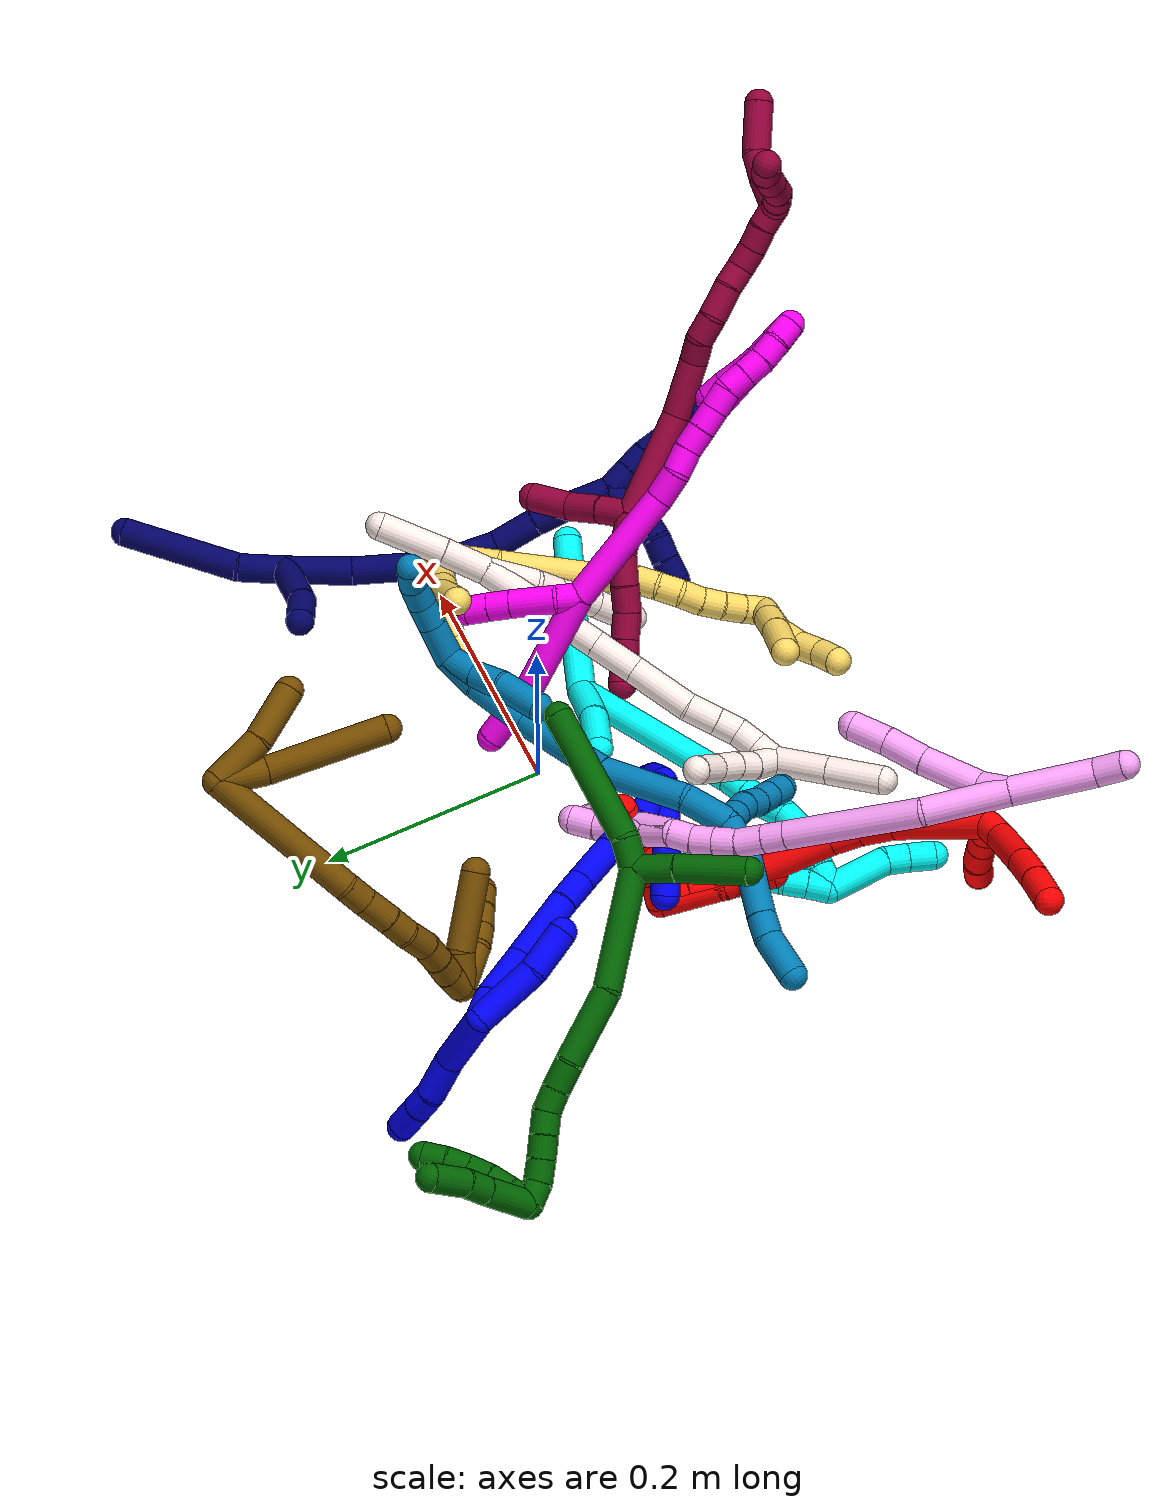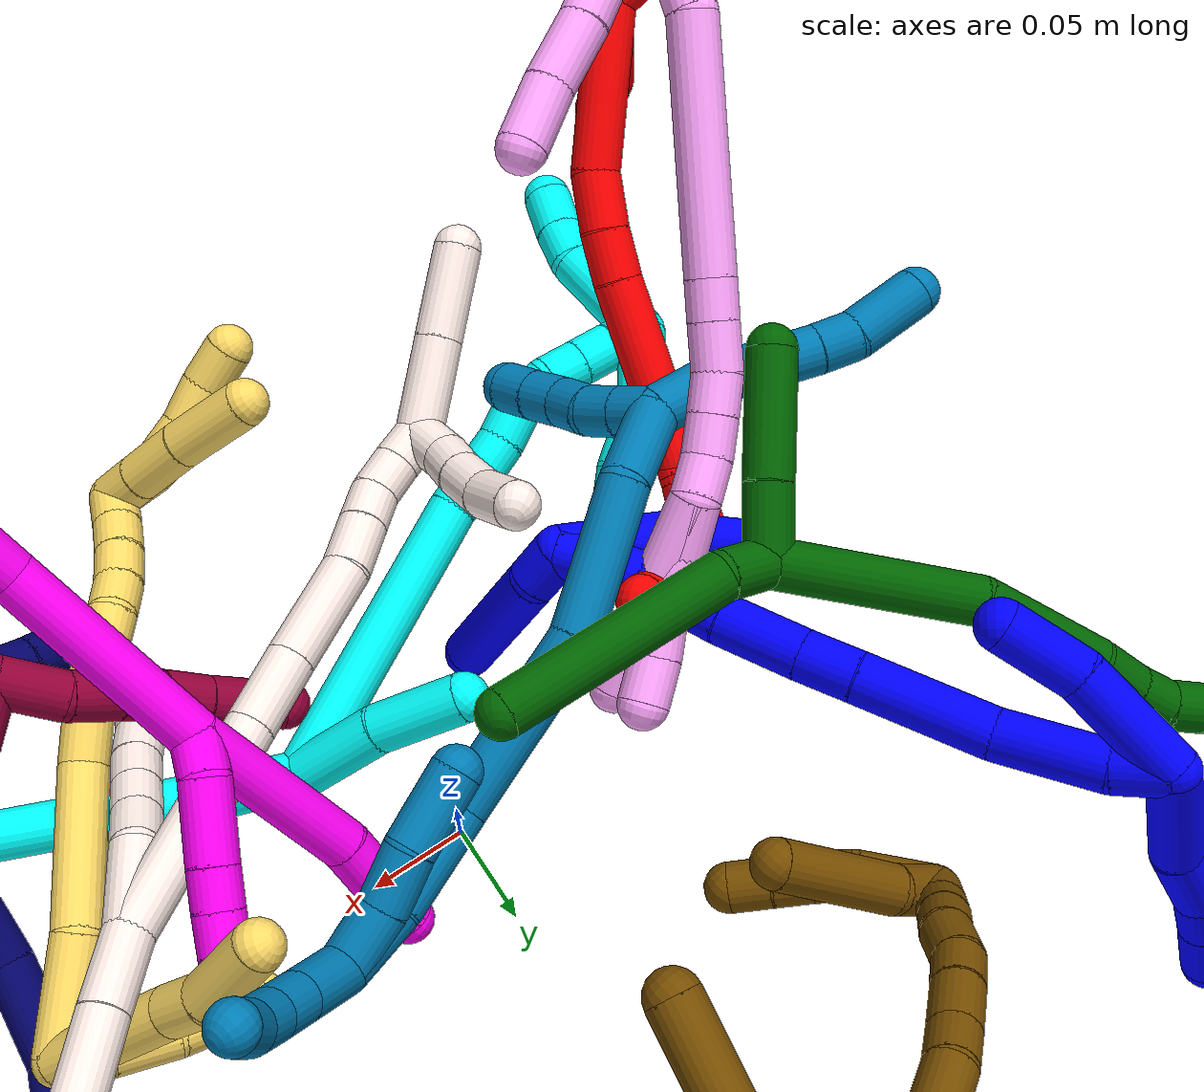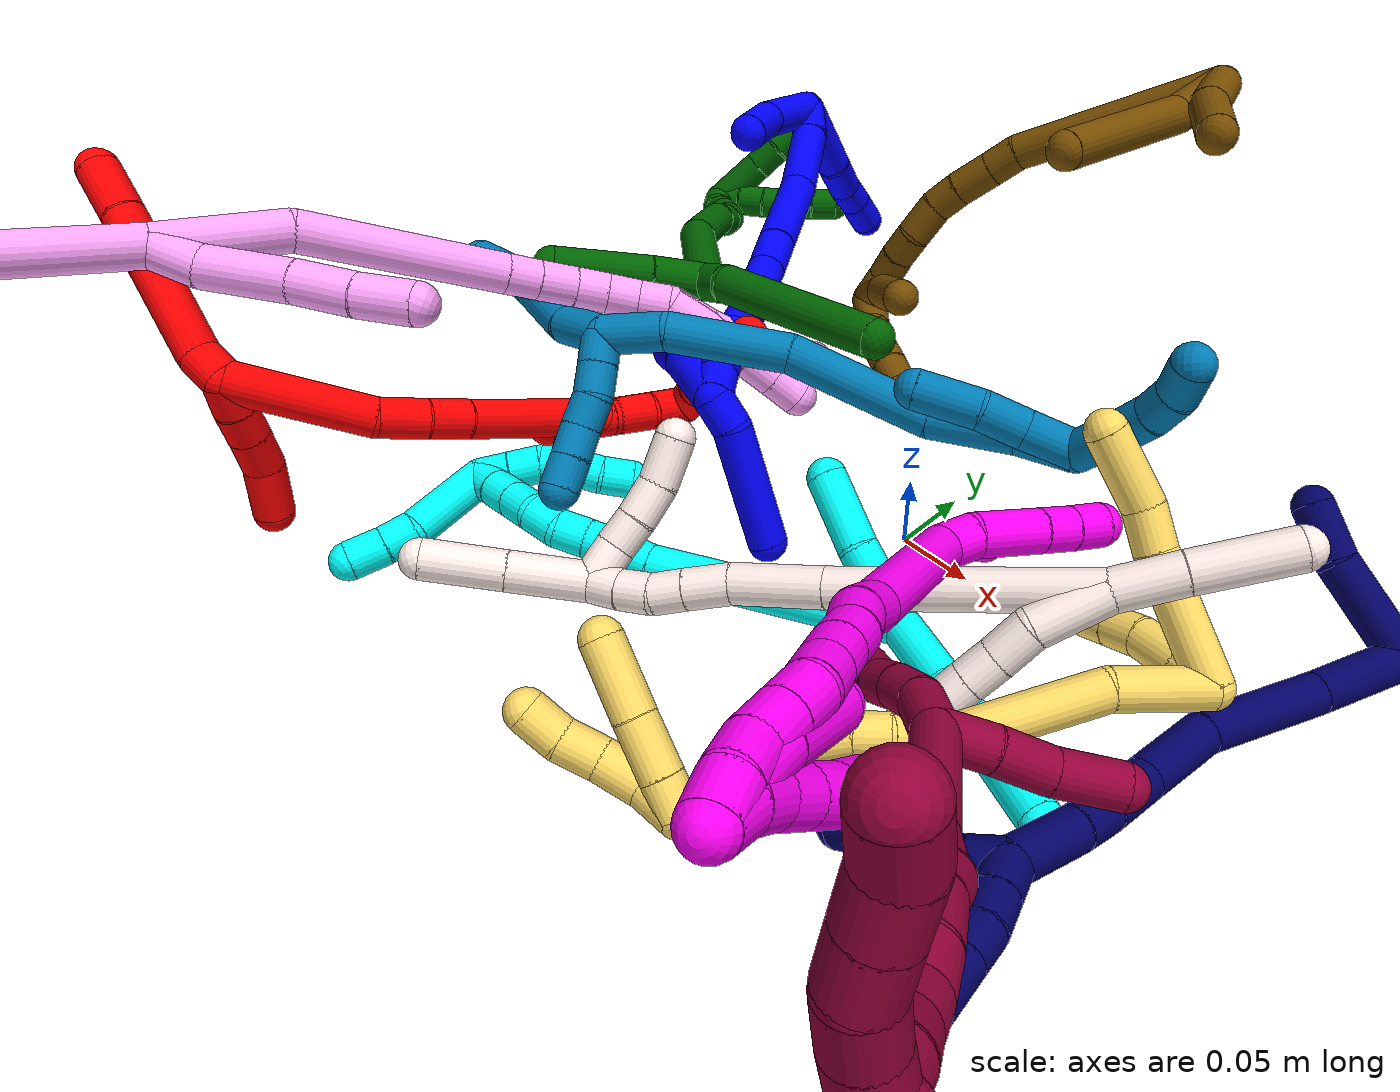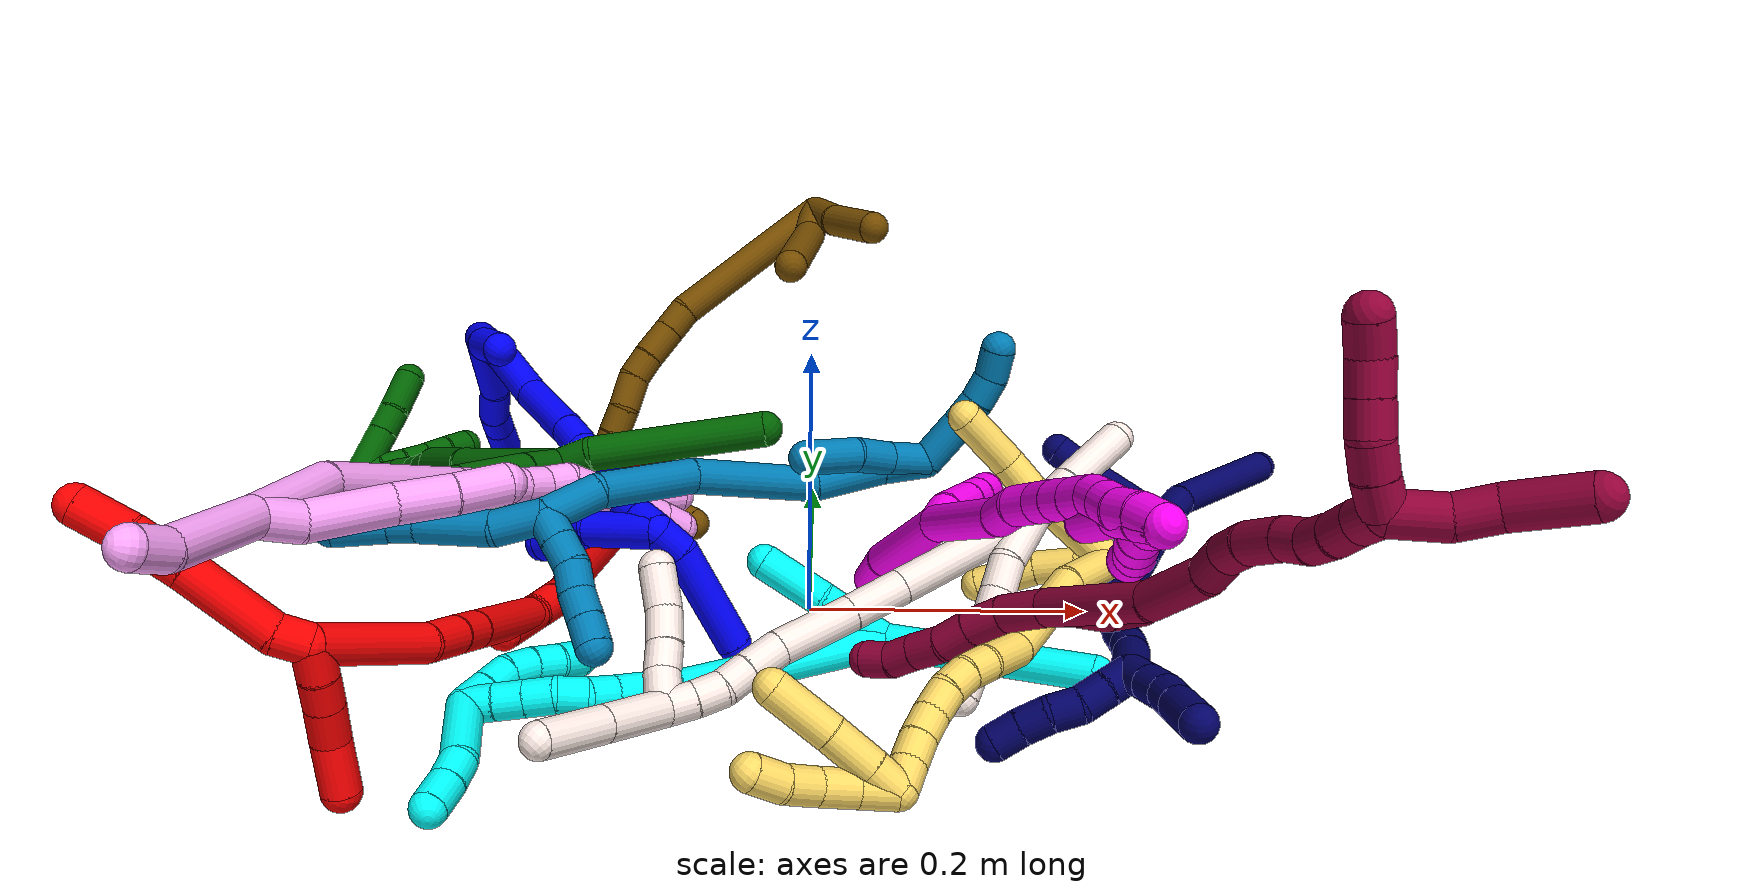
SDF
<sdf version="1.7">
 <world name="default">
  <plugin name="TubeGeneratorPlugin" filename="libtube_generator_plugin.so"/>
  <model name="photoneo_s_sensor">
   <static>1</static>
   <pose>0 0 2 1.57079 1.57079 3.14159</pose>
   <link name="link">
    <inertial><mass>0.1</mass></inertial>
    <sensor name="sensor" type="depth">
     <update_rate>30</update_rate>
     <camera>
      <horizontal_fov>1.22</horizontal_fov>
      <image><width>1920</width><height>1200</height><format>B8G8R8</format></image>
      <clip><near>0.1</near><far>4</far></clip>
      <depth_camera><output>points</output></depth_camera>
     </camera>
     <plugin name="camera_plugin" filename="libgazebo_ros_depth_camera.so">
      <baseline>0.2</baseline>
      <alwaysOn>1</alwaysOn>
      <updateRate>0.0</updateRate>
      <cameraName>camera_ir</cameraName>
      <imageTopicName>/camera/color/image_raw</imageTopicName>
      <cameraInfoTopicName>/camera/color/camera_info</cameraInfoTopicName>
      <depthImageTopicName>/camera/depth/image_raw</depthImageTopicName>
      <depthImageCameraInfoTopicName>/camera/depth/camera_info</depthImageCameraInfoTopicName>
      <pointCloudTopicName>/camera/depth/points</pointCloudTopicName>
      <frameName>fr_optical</frameName>
      <pointCloudCutoff>0.1</pointCloudCutoff>
      <pointCloudCutoffMax>2.0</pointCloudCutoffMax>
      <distortionK1>0</distortionK1>
      <distortionK2>0</distortionK2>
      <distortionK3>0</distortionK3>
      <distortionT1>0</distortionT1>
      <distortionT2>0</distortionT2>
      <CxPrime>0</CxPrime>
      <Cx>0</Cx>
      <Cy>0</Cy>
      <focalLength>0</focalLength>
      <hackBaseline>0</hackBaseline>
     </plugin>
    </sensor>
   </link>
  </model>
  <gravity>0 0 -9.8</gravity>
  <magnetic_field>6e-06 2.3e-05 -4.2e-05</magnetic_field>
  <atmosphere type="adiabatic"/>
  <physics name="default_physics" default="0" type="ode">
   <max_step_size>0.003</max_step_size>
   <real_time_factor>1</real_time_factor>
   <real_time_update_rate>1000</real_time_update_rate>
   <max_contacts>10000</max_contacts>
   <ode>
    <solver>
     <type>quick</type>
     <iters>100</iters>
     <sor>1.3</sor>
     <use_dynamic_moi_rescaling>0</use_dynamic_moi_rescaling>
    </solver>
    <constraints>
     <contact_max_correcting_vel>0</contact_max_correcting_vel>
     <contact_surface_layer>0.001</contact_surface_layer>
     <cfm>0</cfm>
     <erp>0.2</erp>
    </constraints>
   </ode>
  </physics>
  <scene><ambient>0.4 0.4 0.4 1</ambient><background>0.7 0.7 0.7 1</background><shadows>0</shadows></scene>
  <audio><device>default</device></audio>
  <spherical_coordinates>
   <surface_model>EARTH_WGS84</surface_model>
   <latitude_deg>0</latitude_deg>
   <longitude_deg>0</longitude_deg>
   <elevation>0</elevation>
   <heading_deg>0</heading_deg>
  </spherical_coordinates>
  <model name="bin">
   <static>1</static>
   <link name="bottom">
    <collision name="collision-bottom">
     <pose>0 0 -0.01 0 -0 0</pose>
     <geometry><box><size>0.8 0.6 0.02</size></box></geometry>
     <surface>
      <friction><ode><mu>100</mu><mu2>100</mu2></ode></friction>
      <contact><collide_bitmask>65535</collide_bitmask></contact>
     </surface>
    </collision>
   </link>
   <link name="west_wall">
    <collision name="collision-west_wall">
     <pose>-0.41 0 0.1 0 -0 0</pose>
     <geometry><box><size>0.02 0.6 0.2</size></box></geometry>
     <surface>
      <friction><ode><mu>100</mu><mu2>100</mu2></ode></friction>
      <contact><collide_bitmask>65535</collide_bitmask></contact>
     </surface>
    </collision>
   </link>
   <link name="east_wall">
    <collision name="collision-east_wall">
     <pose>0.41 0 0.1 0 -0 0</pose>
     <geometry><box><size>0.02 0.6 0.2</size></box></geometry>
     <surface>
      <friction><ode><mu>100</mu><mu2>100</mu2></ode></friction>
      <contact><collide_bitmask>65535</collide_bitmask></contact>
     </surface>
    </collision>
   </link>
   <link name="south_wall">
    <collision name="collision-south_wall">
     <pose>0 -0.31 0.1 0 -0 0</pose>
     <geometry><box><size>0.8 0.02 0.2</size></box></geometry>
     <surface>
      <friction><ode><mu>100</mu><mu2>100</mu2></ode></friction>
      <contact><collide_bitmask>65535</collide_bitmask></contact>
     </surface>
    </collision>
   </link>
   <link name="north_wall">
    <collision name="collision-north_wall">
     <pose>0 0.31 0.1 0 -0 0</pose>
     <geometry><box><size>0.8 0.02 0.2</size></box></geometry>
     <surface>
      <friction><ode><mu>100</mu><mu2>100</mu2></ode></friction>
      <contact><collide_bitmask>65535</collide_bitmask></contact>
     </surface>
    </collision>
   </link>
  </model>
  <model name="1">
   <static>0</static>
   <link name="1">
    <collision name="collision-cylinder-e_1_2_8">
     <pose>-0.030213 -0.003368 -0.003858 2.42393 -1.40288 -2.30589</pose>
     <geometry><cylinder><radius>0.0125</radius><length>0.061288</length></cylinder></geometry>
     <surface>
      <friction><ode><mu>1.16</mu><mu2>1.16</mu2><slip1>0</slip1><slip2>0</slip2></ode></friction>
      <contact><ode><kp>1e+06</kp><kd>1</kd><max_vel>0</max_vel><min_depth>0.001</min_depth></ode></contact>
     </surface>
    </collision>
    <visual name="visual-cylinder-e_1_2_8">
     <pose>-0.030213 -0.003368 -0.003858 2.42393 -1.40288 -2.30589</pose>
     <geometry><cylinder><radius>0.0125</radius><length>0.061288</length></cylinder></geometry>
     <material><ambient>0 0 1 1</ambient></material>
    </visual>
    <collision name="collision-cylinder-e_2_8_9">
     <pose>-0.079366 -0.009717 -0.005185 0.866705 -1.36719 -0.720896</pose>
     <geometry><cylinder><radius>0.0125</radius><length>0.038679</length></cylinder></geometry>
     <surface>
      <friction><ode><mu>1.16</mu><mu2>1.16</mu2><slip1>0</slip1><slip2>0</slip2></ode></friction>
      <contact><ode><kp>1e+06</kp><kd>1</kd><max_vel>0</max_vel><min_depth>0.001</min_depth></ode></contact>
     </surface>
    </collision>
    <visual name="visual-cylinder-e_2_8_9">
     <pose>-0.079366 -0.009717 -0.005185 0.866705 -1.36719 -0.720896</pose>
     <geometry><cylinder><radius>0.0125</radius><length>0.038679</length></cylinder></geometry>
     <material><ambient>0 0 1 1</ambient></material>
    </visual>
    <collision name="collision-cylinder-e_3_9_10">
     <pose>-0.109248 -0.012904 -0.003028 2.6371 -1.53171 -2.61788</pose>
     <geometry><cylinder><radius>0.0125</radius><length>0.021901</length></cylinder></geometry>
     <surface>
      <friction><ode><mu>1.16</mu><mu2>1.16</mu2><slip1>0</slip1><slip2>0</slip2></ode></friction>
      <contact><ode><kp>1e+06</kp><kd>1</kd><max_vel>0</max_vel><min_depth>0.001</min_depth></ode></contact>
     </surface>
    </collision>
    <visual name="visual-cylinder-e_3_9_10">
     <pose>-0.109248 -0.012904 -0.003028 2.6371 -1.53171 -2.61788</pose>
     <geometry><cylinder><radius>0.0125</radius><length>0.021901</length></cylinder></geometry>
     <material><ambient>0 0 1 1</ambient></material>
    </visual>
    <collision name="collision-cylinder-e_4_10_6">
     <pose>-0.134196 -0.013567 -0.004617 2.78244 -1.47845 -2.74849</pose>
     <geometry><cylinder><radius>0.0125</radius><length>0.028132</length></cylinder></geometry>
     <surface>
      <friction><ode><mu>1.16</mu><mu2>1.16</mu2><slip1>0</slip1><slip2>0</slip2></ode></friction>
      <contact><ode><kp>1e+06</kp><kd>1</kd><max_vel>0</max_vel><min_depth>0.001</min_depth></ode></contact>
     </surface>
    </collision>
    <visual name="visual-cylinder-e_4_10_6">
     <pose>-0.134196 -0.013567 -0.004617 2.78244 -1.47845 -2.74849</pose>
     <geometry><cylinder><radius>0.0125</radius><length>0.028132</length></cylinder></geometry>
     <material><ambient>0 0 1 1</ambient></material>
    </visual>
    <collision name="collision-cylinder-e_1_2_11">
     <pose>0.022497 -0.008481 -0.016967 2.67805 0.870305 2.20203</pose>
     <geometry><cylinder><radius>0.0125</radius><length>0.058853</length></cylinder></geometry>
     <surface>
      <friction><ode><mu>1.16</mu><mu2>1.16</mu2><slip1>0</slip1><slip2>0</slip2></ode></friction>
      <contact><ode><kp>1e+06</kp><kd>1</kd><max_vel>0</max_vel><min_depth>0.001</min_depth></ode></contact>
     </surface>
    </collision>
    <visual name="visual-cylinder-e_1_2_11">
     <pose>0.022497 -0.008481 -0.016967 2.67805 0.870305 2.20203</pose>
     <geometry><cylinder><radius>0.0125</radius><length>0.058853</length></cylinder></geometry>
     <material><ambient>0 0 1 1</ambient></material>
    </visual>
    <collision name="collision-cylinder-e_2_11_5">
     <pose>0.059059 -0.019392 -0.04875 2.97904 0.752735 2.73506</pose>
     <geometry><cylinder><radius>0.0125</radius><length>0.041147</length></cylinder></geometry>
     <surface>
      <friction><ode><mu>1.16</mu><mu2>1.16</mu2><slip1>0</slip1><slip2>0</slip2></ode></friction>
      <contact><ode><kp>1e+06</kp><kd>1</kd><max_vel>0</max_vel><min_depth>0.001</min_depth></ode></contact>
     </surface>
    </collision>
    <visual name="visual-cylinder-e_2_11_5">
     <pose>0.059059 -0.019392 -0.04875 2.97904 0.752735 2.73506</pose>
     <geometry><cylinder><radius>0.0125</radius><length>0.041147</length></cylinder></geometry>
     <material><ambient>0 0 1 1</ambient></material>
    </visual>
    <collision name="collision-cylinder-e_1_2_12">
     <pose>0.001236 -0.000813 -0.01334 3.08072 0.092203 1.97499</pose>
     <geometry><cylinder><radius>0.0125</radius><length>0.026843</length></cylinder></geometry>
     <surface>
      <friction><ode><mu>1.16</mu><mu2>1.16</mu2><slip1>0</slip1><slip2>0</slip2></ode></friction>
      <contact><ode><kp>1e+06</kp><kd>1</kd><max_vel>0</max_vel><min_depth>0.001</min_depth></ode></contact>
     </surface>
    </collision>
    <visual name="visual-cylinder-e_1_2_12">
     <pose>0.001236 -0.000813 -0.01334 3.08072 0.092203 1.97499</pose>
     <geometry><cylinder><radius>0.0125</radius><length>0.026843</length></cylinder></geometry>
     <material><ambient>0 0 1 1</ambient></material>
    </visual>
    <collision name="collision-cylinder-e_2_12_13">
     <pose>0.008437 -0.00789 -0.051951 2.89862 0.225215 1.49428</pose>
     <geometry><cylinder><radius>0.0125</radius><length>0.053423</length></cylinder></geometry>
     <surface>
      <friction><ode><mu>1.16</mu><mu2>1.16</mu2><slip1>0</slip1><slip2>0</slip2></ode></friction>
      <contact><ode><kp>1e+06</kp><kd>1</kd><max_vel>0</max_vel><min_depth>0.001</min_depth></ode></contact>
     </surface>
    </collision>
    <visual name="visual-cylinder-e_2_12_13">
     <pose>0.008437 -0.00789 -0.051951 2.89862 0.225215 1.49428</pose>
     <geometry><cylinder><radius>0.0125</radius><length>0.053423</length></cylinder></geometry>
     <material><ambient>0 0 1 1</ambient></material>
    </visual>
    <collision name="collision-cylinder-e_3_13_14">
     <pose>0.028563 -0.020777 -0.10655 2.91951 0.440181 2.21684</pose>
     <geometry><cylinder><radius>0.0125</radius><length>0.066467</length></cylinder></geometry>
     <surface>
      <friction><ode><mu>1.16</mu><mu2>1.16</mu2><slip1>0</slip1><slip2>0</slip2></ode></friction>
      <contact><ode><kp>1e+06</kp><kd>1</kd><max_vel>0</max_vel><min_depth>0.001</min_depth></ode></contact>
     </surface>
    </collision>
    <visual name="visual-cylinder-e_3_13_14">
     <pose>0.028563 -0.020777 -0.10655 2.91951 0.440181 2.21684</pose>
     <geometry><cylinder><radius>0.0125</radius><length>0.066467</length></cylinder></geometry>
     <material><ambient>0 0 1 1</ambient></material>
    </visual>
    <collision name="collision-cylinder-e_4_14_15">
     <pose>0.04778 -0.030747 -0.148179 2.87588 0.377573 1.92082</pose>
     <geometry><cylinder><radius>0.0125</radius><length>0.02743</length></cylinder></geometry>
     <surface>
      <friction><ode><mu>1.16</mu><mu2>1.16</mu2><slip1>0</slip1><slip2>0</slip2></ode></friction>
      <contact><ode><kp>1e+06</kp><kd>1</kd><max_vel>0</max_vel><min_depth>0.001</min_depth></ode></contact>
     </surface>
    </collision>
    <visual name="visual-cylinder-e_4_14_15">
     <pose>0.04778 -0.030747 -0.148179 2.87588 0.377573 1.92082</pose>
     <geometry><cylinder><radius>0.0125</radius><length>0.02743</length></cylinder></geometry>
     <material><ambient>0 0 1 1</ambient></material>
    </visual>
    <collision name="collision-cylinder-e_5_15_16">
     <pose>0.061237 -0.03928 -0.178644 2.86349 0.418498 1.97619</pose>
     <geometry><cylinder><radius>0.0125</radius><length>0.041346</length></cylinder></geometry>
     <surface>
      <friction><ode><mu>1.16</mu><mu2>1.16</mu2><slip1>0</slip1><slip2>0</slip2></ode></friction>
      <contact><ode><kp>1e+06</kp><kd>1</kd><max_vel>0</max_vel><min_depth>0.001</min_depth></ode></contact>
     </surface>
    </collision>
    <visual name="visual-cylinder-e_5_15_16">
     <pose>0.061237 -0.03928 -0.178644 2.86349 0.418498 1.97619</pose>
     <geometry><cylinder><radius>0.0125</radius><length>0.041346</length></cylinder></geometry>
     <material><ambient>0 0 1 1</ambient></material>
    </visual>
    <collision name="collision-cylinder-e_6_16_17">
     <pose>0.073738 -0.047762 -0.205362 2.77388 0.42048 1.70799</pose>
     <geometry><cylinder><radius>0.0125</radius><length>0.020085</length></cylinder></geometry>
     <surface>
      <friction><ode><mu>1.16</mu><mu2>1.16</mu2><slip1>0</slip1><slip2>0</slip2></ode></friction>
      <contact><ode><kp>1e+06</kp><kd>1</kd><max_vel>0</max_vel><min_depth>0.001</min_depth></ode></contact>
     </surface>
    </collision>
    <visual name="visual-cylinder-e_6_16_17">
     <pose>0.073738 -0.047762 -0.205362 2.77388 0.42048 1.70799</pose>
     <geometry><cylinder><radius>0.0125</radius><length>0.020085</length></cylinder></geometry>
     <material><ambient>0 0 1 1</ambient></material>
    </visual>
    <collision name="collision-cylinder-e_7_17_18">
     <pose>0.082477 -0.054534 -0.223544 2.79508 0.425546 1.77988</pose>
     <geometry><cylinder><radius>0.0125</radius><length>0.022477</length></cylinder></geometry>
     <surface>
      <friction><ode><mu>1.16</mu><mu2>1.16</mu2><slip1>0</slip1><slip2>0</slip2></ode></friction>
      <contact><ode><kp>1e+06</kp><kd>1</kd><max_vel>0</max_vel><min_depth>0.001</min_depth></ode></contact>
     </surface>
    </collision>
    <visual name="visual-cylinder-e_7_17_18">
     <pose>0.082477 -0.054534 -0.223544 2.79508 0.425546 1.77988</pose>
     <geometry><cylinder><radius>0.0125</radius><length>0.022477</length></cylinder></geometry>
     <material><ambient>0 0 1 1</ambient></material>
    </visual>
    <collision name="collision-cylinder-e_8_18_19">
     <pose>0.091584 -0.059356 -0.242489 2.99816 0.443132 2.52416</pose>
     <geometry><cylinder><radius>0.0125</radius><length>0.020839</length></cylinder></geometry>
     <surface>
      <friction><ode><mu>1.16</mu><mu2>1.16</mu2><slip1>0</slip1><slip2>0</slip2></ode></friction>
      <contact><ode><kp>1e+06</kp><kd>1</kd><max_vel>0</max_vel><min_depth>0.001</min_depth></ode></contact>
     </surface>
    </collision>
    <visual name="visual-cylinder-e_8_18_19">
     <pose>0.091584 -0.059356 -0.242489 2.99816 0.443132 2.52416</pose>
     <geometry><cylinder><radius>0.0125</radius><length>0.020839</length></cylinder></geometry>
     <material><ambient>0 0 1 1</ambient></material>
    </visual>
    <collision name="collision-cylinder-e_9_19_1">
     <pose>0.100093 -0.061807 -0.261482 3.02775 0.393359 2.58453</pose>
     <geometry><cylinder><radius>0.0125</radius><length>0.02109</length></cylinder></geometry>
     <surface>
      <friction><ode><mu>1.16</mu><mu2>1.16</mu2><slip1>0</slip1><slip2>0</slip2></ode></friction>
      <contact><ode><kp>1e+06</kp><kd>1</kd><max_vel>0</max_vel><min_depth>0.001</min_depth></ode></contact>
     </surface>
    </collision>
    <visual name="visual-cylinder-e_9_19_1">
     <pose>0.100093 -0.061807 -0.261482 3.02775 0.393359 2.58453</pose>
     <geometry><cylinder><radius>0.0125</radius><length>0.02109</length></cylinder></geometry>
     <material><ambient>0 0 1 1</ambient></material>
    </visual>
    <collision name="collision-cylinder-e_1_1_20">
     <pose>0.097284 -0.061078 -0.279606 -2.92758 -0.670181 2.54316</pose>
     <geometry><cylinder><radius>0.0125</radius><length>0.02206</length></cylinder></geometry>
     <surface>
      <friction><ode><mu>1.16</mu><mu2>1.16</mu2><slip1>0</slip1><slip2>0</slip2></ode></friction>
      <contact><ode><kp>1e+06</kp><kd>1</kd><max_vel>0</max_vel><min_depth>0.001</min_depth></ode></contact>
     </surface>
    </collision>
    <visual name="visual-cylinder-e_1_1_20">
     <pose>0.097284 -0.061078 -0.279606 -2.92758 -0.670181 2.54316</pose>
     <geometry><cylinder><radius>0.0125</radius><length>0.02206</length></cylinder></geometry>
     <material><ambient>0 0 1 1</ambient></material>
    </visual>
    <collision name="collision-cylinder-e_2_20_4">
     <pose>0.063744 -0.064927 -0.315875 2.94001 -0.754401 -2.64172</pose>
     <geometry><cylinder><radius>0.0125</radius><length>0.07794</length></cylinder></geometry>
     <surface>
      <friction><ode><mu>1.16</mu><mu2>1.16</mu2><slip1>0</slip1><slip2>0</slip2></ode></friction>
      <contact><ode><kp>1e+06</kp><kd>1</kd><max_vel>0</max_vel><min_depth>0.001</min_depth></ode></contact>
     </surface>
    </collision>
    <visual name="visual-cylinder-e_2_20_4">
     <pose>0.063744 -0.064927 -0.315875 2.94001 -0.754401 -2.64172</pose>
     <geometry><cylinder><radius>0.0125</radius><length>0.07794</length></cylinder></geometry>
     <material><ambient>0 0 1 1</ambient></material>
    </visual>
    <collision name="collision-cylinder-e_1_1_21">
     <pose>0.095309 -0.075131 -0.249052 0.504882 -0.336167 -0.087482</pose>
     <geometry><cylinder><radius>0.0125</radius><length>0.053511</length></cylinder></geometry>
     <surface>
      <friction><ode><mu>1.16</mu><mu2>1.16</mu2><slip1>0</slip1><slip2>0</slip2></ode></friction>
      <contact><ode><kp>1e+06</kp><kd>1</kd><max_vel>0</max_vel><min_depth>0.001</min_depth></ode></contact>
     </surface>
    </collision>
    <visual name="visual-cylinder-e_1_1_21">
     <pose>0.095309 -0.075131 -0.249052 0.504882 -0.336167 -0.087482</pose>
     <geometry><cylinder><radius>0.0125</radius><length>0.053511</length></cylinder></geometry>
     <material><ambient>0 0 1 1</ambient></material>
    </visual>
    <collision name="collision-cylinder-e_2_21_3">
     <pose>0.072388 -0.098291 -0.21205 0.633565 -0.651499 -0.220567</pose>
     <geometry><cylinder><radius>0.0125</radius><length>0.046489</length></cylinder></geometry>
     <surface>
      <friction><ode><mu>1.16</mu><mu2>1.16</mu2><slip1>0</slip1><slip2>0</slip2></ode></friction>
      <contact><ode><kp>1e+06</kp><kd>1</kd><max_vel>0</max_vel><min_depth>0.001</min_depth></ode></contact>
     </surface>
    </collision>
    <visual name="visual-cylinder-e_2_21_3">
     <pose>0.072388 -0.098291 -0.21205 0.633565 -0.651499 -0.220567</pose>
     <geometry><cylinder><radius>0.0125</radius><length>0.046489</length></cylinder></geometry>
     <material><ambient>0 0 1 1</ambient></material>
    </visual>
    <collision name="collision-sphere-3">
     <pose>0.058293 -0.109234 -0.197153 0 -0 0</pose>
     <geometry><sphere><radius>0.0125</radius></sphere></geometry>
     <surface>
      <friction><ode><mu>1.16</mu><mu2>1.16</mu2><slip1>0</slip1><slip2>0</slip2></ode></friction>
      <contact><ode><kp>1e+06</kp><kd>1</kd><max_vel>0</max_vel><min_depth>0.001</min_depth></ode></contact>
     </surface>
    </collision>
    <visual name="visual-sphere-3">
     <pose>0.058293 -0.109234 -0.197153 0 -0 0</pose>
     <geometry><sphere><radius>0.0125</radius></sphere></geometry>
     <material><ambient>0 0 1 1</ambient></material>
    </visual>
    <collision name="collision-sphere-21">
     <pose>0.086483 -0.087348 -0.226946 0 -0 0</pose>
     <geometry><sphere><radius>0.0125</radius></sphere></geometry>
     <surface>
      <friction><ode><mu>1.16</mu><mu2>1.16</mu2><slip1>0</slip1><slip2>0</slip2></ode></friction>
      <contact><ode><kp>1e+06</kp><kd>1</kd><max_vel>0</max_vel><min_depth>0.001</min_depth></ode></contact>
     </surface>
    </collision>
    <visual name="visual-sphere-21">
     <pose>0.086483 -0.087348 -0.226946 0 -0 0</pose>
     <geometry><sphere><radius>0.0125</radius></sphere></geometry>
     <material><ambient>0 0 1 1</ambient></material>
    </visual>
    <collision name="collision-sphere-4">
     <pose>0.037056 -0.070613 -0.343696 0 -0 0</pose>
     <geometry><sphere><radius>0.0125</radius></sphere></geometry>
     <surface>
      <friction><ode><mu>1.16</mu><mu2>1.16</mu2><slip1>0</slip1><slip2>0</slip2></ode></friction>
      <contact><ode><kp>1e+06</kp><kd>1</kd><max_vel>0</max_vel><min_depth>0.001</min_depth></ode></contact>
     </surface>
    </collision>
    <visual name="visual-sphere-4">
     <pose>0.037056 -0.070613 -0.343696 0 -0 0</pose>
     <geometry><sphere><radius>0.0125</radius></sphere></geometry>
     <material><ambient>0 0 1 1</ambient></material>
    </visual>
    <collision name="collision-sphere-20">
     <pose>0.090433 -0.059242 -0.288053 0 -0 0</pose>
     <geometry><sphere><radius>0.0125</radius></sphere></geometry>
     <surface>
      <friction><ode><mu>1.16</mu><mu2>1.16</mu2><slip1>0</slip1><slip2>0</slip2></ode></friction>
      <contact><ode><kp>1e+06</kp><kd>1</kd><max_vel>0</max_vel><min_depth>0.001</min_depth></ode></contact>
     </surface>
    </collision>
    <visual name="visual-sphere-20">
     <pose>0.090433 -0.059242 -0.288053 0 -0 0</pose>
     <geometry><sphere><radius>0.0125</radius></sphere></geometry>
     <material><ambient>0 0 1 1</ambient></material>
    </visual>
    <collision name="collision-sphere-11">
     <pose>0.044995 -0.016962 -0.033933 0 -0 0</pose>
     <geometry><sphere><radius>0.0125</radius></sphere></geometry>
     <surface>
      <friction><ode><mu>1.16</mu><mu2>1.16</mu2><slip1>0</slip1><slip2>0</slip2></ode></friction>
      <contact><ode><kp>1e+06</kp><kd>1</kd><max_vel>0</max_vel><min_depth>0.001</min_depth></ode></contact>
     </surface>
    </collision>
    <visual name="visual-sphere-11">
     <pose>0.044995 -0.016962 -0.033933 0 -0 0</pose>
     <geometry><sphere><radius>0.0125</radius></sphere></geometry>
     <material><ambient>0 0 1 1</ambient></material>
    </visual>
    <collision name="collision-sphere-6">
     <pose>-0.148202 -0.014023 -0.005831 0 -0 0</pose>
     <geometry><sphere><radius>0.0125</radius></sphere></geometry>
     <surface>
      <friction><ode><mu>1.16</mu><mu2>1.16</mu2><slip1>0</slip1><slip2>0</slip2></ode></friction>
      <contact><ode><kp>1e+06</kp><kd>1</kd><max_vel>0</max_vel><min_depth>0.001</min_depth></ode></contact>
     </surface>
    </collision>
    <visual name="visual-sphere-6">
     <pose>-0.148202 -0.014023 -0.005831 0 -0 0</pose>
     <geometry><sphere><radius>0.0125</radius></sphere></geometry>
     <material><ambient>0 0 1 1</ambient></material>
    </visual>
    <collision name="collision-sphere-10">
     <pose>-0.12019 -0.013111 -0.003403 0 -0 0</pose>
     <geometry><sphere><radius>0.0125</radius></sphere></geometry>
     <surface>
      <friction><ode><mu>1.16</mu><mu2>1.16</mu2><slip1>0</slip1><slip2>0</slip2></ode></friction>
      <contact><ode><kp>1e+06</kp><kd>1</kd><max_vel>0</max_vel><min_depth>0.001</min_depth></ode></contact>
     </surface>
    </collision>
    <visual name="visual-sphere-10">
     <pose>-0.12019 -0.013111 -0.003403 0 -0 0</pose>
     <geometry><sphere><radius>0.0125</radius></sphere></geometry>
     <material><ambient>0 0 1 1</ambient></material>
    </visual>
    <collision name="collision-sphere-9">
     <pose>-0.098306 -0.012697 -0.002653 0 -0 0</pose>
     <geometry><sphere><radius>0.0125</radius></sphere></geometry>
     <surface>
      <friction><ode><mu>1.16</mu><mu2>1.16</mu2><slip1>0</slip1><slip2>0</slip2></ode></friction>
      <contact><ode><kp>1e+06</kp><kd>1</kd><max_vel>0</max_vel><min_depth>0.001</min_depth></ode></contact>
     </surface>
    </collision>
    <visual name="visual-sphere-9">
     <pose>-0.098306 -0.012697 -0.002653 0 -0 0</pose>
     <geometry><sphere><radius>0.0125</radius></sphere></geometry>
     <material><ambient>0 0 1 1</ambient></material>
    </visual>
    <collision name="collision-sphere-2">
     <geometry><sphere><radius>0.0125</radius></sphere></geometry>
     <surface>
      <friction><ode><mu>1.16</mu><mu2>1.16</mu2><slip1>0</slip1><slip2>0</slip2></ode></friction>
      <contact><ode><kp>1e+06</kp><kd>1</kd><max_vel>0</max_vel><min_depth>0.001</min_depth></ode></contact>
     </surface>
    </collision>
    <visual name="visual-sphere-2">
     <geometry><sphere><radius>0.0125</radius></sphere></geometry>
     <material><ambient>0 0 1 1</ambient></material>
    </visual>
    <collision name="collision-sphere-19">
     <pose>0.096051 -0.060701 -0.251805 0 -0 0</pose>
     <geometry><sphere><radius>0.0125</radius></sphere></geometry>
     <surface>
      <friction><ode><mu>1.16</mu><mu2>1.16</mu2><slip1>0</slip1><slip2>0</slip2></ode></friction>
      <contact><ode><kp>1e+06</kp><kd>1</kd><max_vel>0</max_vel><min_depth>0.001</min_depth></ode></contact>
     </surface>
    </collision>
    <visual name="visual-sphere-19">
     <pose>0.096051 -0.060701 -0.251805 0 -0 0</pose>
     <geometry><sphere><radius>0.0125</radius></sphere></geometry>
     <material><ambient>0 0 1 1</ambient></material>
    </visual>
    <collision name="collision-sphere-8">
     <pose>-0.060426 -0.006736 -0.007716 0 -0 0</pose>
     <geometry><sphere><radius>0.0125</radius></sphere></geometry>
     <surface>
      <friction><ode><mu>1.16</mu><mu2>1.16</mu2><slip1>0</slip1><slip2>0</slip2></ode></friction>
      <contact><ode><kp>1e+06</kp><kd>1</kd><max_vel>0</max_vel><min_depth>0.001</min_depth></ode></contact>
     </surface>
    </collision>
    <visual name="visual-sphere-8">
     <pose>-0.060426 -0.006736 -0.007716 0 -0 0</pose>
     <geometry><sphere><radius>0.0125</radius></sphere></geometry>
     <material><ambient>0 0 1 1</ambient></material>
    </visual>
    <collision name="collision-sphere-5">
     <pose>0.073124 -0.021822 -0.063567 0 -0 0</pose>
     <geometry><sphere><radius>0.0125</radius></sphere></geometry>
     <surface>
      <friction><ode><mu>1.16</mu><mu2>1.16</mu2><slip1>0</slip1><slip2>0</slip2></ode></friction>
      <contact><ode><kp>1e+06</kp><kd>1</kd><max_vel>0</max_vel><min_depth>0.001</min_depth></ode></contact>
     </surface>
    </collision>
    <visual name="visual-sphere-5">
     <pose>0.073124 -0.021822 -0.063567 0 -0 0</pose>
     <geometry><sphere><radius>0.0125</radius></sphere></geometry>
     <material><ambient>0 0 1 1</ambient></material>
    </visual>
    <collision name="collision-sphere-12">
     <pose>0.002471 -0.001626 -0.026679 0 -0 0</pose>
     <geometry><sphere><radius>0.0125</radius></sphere></geometry>
     <surface>
      <friction><ode><mu>1.16</mu><mu2>1.16</mu2><slip1>0</slip1><slip2>0</slip2></ode></friction>
      <contact><ode><kp>1e+06</kp><kd>1</kd><max_vel>0</max_vel><min_depth>0.001</min_depth></ode></contact>
     </surface>
    </collision>
    <visual name="visual-sphere-12">
     <pose>0.002471 -0.001626 -0.026679 0 -0 0</pose>
     <geometry><sphere><radius>0.0125</radius></sphere></geometry>
     <material><ambient>0 0 1 1</ambient></material>
    </visual>
    <collision name="collision-sphere-13">
     <pose>0.014402 -0.014154 -0.077223 0 -0 0</pose>
     <geometry><sphere><radius>0.0125</radius></sphere></geometry>
     <surface>
      <friction><ode><mu>1.16</mu><mu2>1.16</mu2><slip1>0</slip1><slip2>0</slip2></ode></friction>
      <contact><ode><kp>1e+06</kp><kd>1</kd><max_vel>0</max_vel><min_depth>0.001</min_depth></ode></contact>
     </surface>
    </collision>
    <visual name="visual-sphere-13">
     <pose>0.014402 -0.014154 -0.077223 0 -0 0</pose>
     <geometry><sphere><radius>0.0125</radius></sphere></geometry>
     <material><ambient>0 0 1 1</ambient></material>
    </visual>
    <collision name="collision-sphere-14">
     <pose>0.042723 -0.027399 -0.135877 0 -0 0</pose>
     <geometry><sphere><radius>0.0125</radius></sphere></geometry>
     <surface>
      <friction><ode><mu>1.16</mu><mu2>1.16</mu2><slip1>0</slip1><slip2>0</slip2></ode></friction>
      <contact><ode><kp>1e+06</kp><kd>1</kd><max_vel>0</max_vel><min_depth>0.001</min_depth></ode></contact>
     </surface>
    </collision>
    <visual name="visual-sphere-14">
     <pose>0.042723 -0.027399 -0.135877 0 -0 0</pose>
     <geometry><sphere><radius>0.0125</radius></sphere></geometry>
     <material><ambient>0 0 1 1</ambient></material>
    </visual>
    <collision name="collision-sphere-15">
     <pose>0.052836 -0.034095 -0.16048 0 -0 0</pose>
     <geometry><sphere><radius>0.0125</radius></sphere></geometry>
     <surface>
      <friction><ode><mu>1.16</mu><mu2>1.16</mu2><slip1>0</slip1><slip2>0</slip2></ode></friction>
      <contact><ode><kp>1e+06</kp><kd>1</kd><max_vel>0</max_vel><min_depth>0.001</min_depth></ode></contact>
     </surface>
    </collision>
    <visual name="visual-sphere-15">
     <pose>0.052836 -0.034095 -0.16048 0 -0 0</pose>
     <geometry><sphere><radius>0.0125</radius></sphere></geometry>
     <material><ambient>0 0 1 1</ambient></material>
    </visual>
    <collision name="collision-sphere-16">
     <pose>0.069639 -0.044466 -0.196807 0 -0 0</pose>
     <geometry><sphere><radius>0.0125</radius></sphere></geometry>
     <surface>
      <friction><ode><mu>1.16</mu><mu2>1.16</mu2><slip1>0</slip1><slip2>0</slip2></ode></friction>
      <contact><ode><kp>1e+06</kp><kd>1</kd><max_vel>0</max_vel><min_depth>0.001</min_depth></ode></contact>
     </surface>
    </collision>
    <visual name="visual-sphere-16">
     <pose>0.069639 -0.044466 -0.196807 0 -0 0</pose>
     <geometry><sphere><radius>0.0125</radius></sphere></geometry>
     <material><ambient>0 0 1 1</ambient></material>
    </visual>
    <collision name="collision-sphere-17">
     <pose>0.077837 -0.051057 -0.213917 0 -0 0</pose>
     <geometry><sphere><radius>0.0125</radius></sphere></geometry>
     <surface>
      <friction><ode><mu>1.16</mu><mu2>1.16</mu2><slip1>0</slip1><slip2>0</slip2></ode></friction>
      <contact><ode><kp>1e+06</kp><kd>1</kd><max_vel>0</max_vel><min_depth>0.001</min_depth></ode></contact>
     </surface>
    </collision>
    <visual name="visual-sphere-17">
     <pose>0.077837 -0.051057 -0.213917 0 -0 0</pose>
     <geometry><sphere><radius>0.0125</radius></sphere></geometry>
     <material><ambient>0 0 1 1</ambient></material>
    </visual>
    <collision name="collision-sphere-18">
     <pose>0.087116 -0.05801 -0.233172 0 -0 0</pose>
     <geometry><sphere><radius>0.0125</radius></sphere></geometry>
     <surface>
      <friction><ode><mu>1.16</mu><mu2>1.16</mu2><slip1>0</slip1><slip2>0</slip2></ode></friction>
      <contact><ode><kp>1e+06</kp><kd>1</kd><max_vel>0</max_vel><min_depth>0.001</min_depth></ode></contact>
     </surface>
    </collision>
    <visual name="visual-sphere-18">
     <pose>0.087116 -0.05801 -0.233172 0 -0 0</pose>
     <geometry><sphere><radius>0.0125</radius></sphere></geometry>
     <material><ambient>0 0 1 1</ambient></material>
    </visual>
    <collision name="collision-sphere-1">
     <pose>0.104135 -0.062914 -0.271159 0 -0 0</pose>
     <geometry><sphere><radius>0.0125</radius></sphere></geometry>
     <surface>
      <friction><ode><mu>1.16</mu><mu2>1.16</mu2><slip1>0</slip1><slip2>0</slip2></ode></friction>
      <contact><ode><kp>1e+06</kp><kd>1</kd><max_vel>0</max_vel><min_depth>0.001</min_depth></ode></contact>
     </surface>
    </collision>
    <visual name="visual-sphere-1">
     <pose>0.104135 -0.062914 -0.271159 0 -0 0</pose>
     <geometry><sphere><radius>0.0125</radius></sphere></geometry>
     <material><ambient>0 0 1 1</ambient></material>
    </visual>
    <inertial>
     <pose>0.029098 -0.035411 -0.131992 0 -0 0</pose>
     <mass>0.75</mass>
     <inertia><ixx>-7e-06</ixx><ixy>0</ixy><ixz>0</ixz><iyy>0.000174</iyy><iyz>0</iyz><izz>4.6e-05</izz></inertia>
    </inertial>
   </link>
   <pose>-0.263575 0.178371 0.141673 0.890366 -0.944767 -1.61672</pose>
  </model>
  <model name="2">
   <static>0</static>
   <link name="2">
    <collision name="collision-cylinder-e_1_2_8">
     <pose>0.002273 0.00666 0.008038 -0.69193 0.214413 -0.077546</pose>
     <geometry><cylinder><radius>0.0125</radius><length>0.021366</length></cylinder></geometry>
     <surface>
      <friction><ode><mu>1.16</mu><mu2>1.16</mu2><slip1>0</slip1><slip2>0</slip2></ode></friction>
      <contact><ode><kp>1e+06</kp><kd>1</kd><max_vel>0</max_vel><min_depth>0.001</min_depth></ode></contact>
     </surface>
    </collision>
    <visual name="visual-cylinder-e_1_2_8">
     <pose>0.002273 0.00666 0.008038 -0.69193 0.214413 -0.077546</pose>
     <geometry><cylinder><radius>0.0125</radius><length>0.021366</length></cylinder></geometry>
     <material><ambient>1 0 0 1</ambient></material>
    </visual>
    <collision name="collision-cylinder-e_2_8_9">
     <pose>0.020258 0.031255 0.034352 -0.775993 0.550335 -0.229768</pose>
     <geometry><cylinder><radius>0.0125</radius><length>0.060086</length></cylinder></geometry>
     <surface>
      <friction><ode><mu>1.16</mu><mu2>1.16</mu2><slip1>0</slip1><slip2>0</slip2></ode></friction>
      <contact><ode><kp>1e+06</kp><kd>1</kd><max_vel>0</max_vel><min_depth>0.001</min_depth></ode></contact>
     </surface>
    </collision>
    <visual name="visual-cylinder-e_2_8_9">
     <pose>0.020258 0.031255 0.034352 -0.775993 0.550335 -0.229768</pose>
     <geometry><cylinder><radius>0.0125</radius><length>0.060086</length></cylinder></geometry>
     <material><ambient>1 0 0 1</ambient></material>
    </visual>
    <collision name="collision-cylinder-e_3_9_10">
     <pose>0.044089 0.060512 0.063224 -0.818457 0.482402 -0.212575</pose>
     <geometry><cylinder><radius>0.0125</radius><length>0.035006</length></cylinder></geometry>
     <surface>
      <friction><ode><mu>1.16</mu><mu2>1.16</mu2><slip1>0</slip1><slip2>0</slip2></ode></friction>
      <contact><ode><kp>1e+06</kp><kd>1</kd><max_vel>0</max_vel><min_depth>0.001</min_depth></ode></contact>
     </surface>
    </collision>
    <visual name="visual-cylinder-e_3_9_10">
     <pose>0.044089 0.060512 0.063224 -0.818457 0.482402 -0.212575</pose>
     <geometry><cylinder><radius>0.0125</radius><length>0.035006</length></cylinder></geometry>
     <material><ambient>1 0 0 1</ambient></material>
    </visual>
    <collision name="collision-cylinder-e_4_10_6">
     <pose>0.058591 0.083655 0.083858 -0.866839 0.390376 -0.182474</pose>
     <geometry><cylinder><radius>0.0125</radius><length>0.033543</length></cylinder></geometry>
     <surface>
      <friction><ode><mu>1.16</mu><mu2>1.16</mu2><slip1>0</slip1><slip2>0</slip2></ode></friction>
      <contact><ode><kp>1e+06</kp><kd>1</kd><max_vel>0</max_vel><min_depth>0.001</min_depth></ode></contact>
     </surface>
    </collision>
    <visual name="visual-cylinder-e_4_10_6">
     <pose>0.058591 0.083655 0.083858 -0.866839 0.390376 -0.182474</pose>
     <geometry><cylinder><radius>0.0125</radius><length>0.033543</length></cylinder></geometry>
     <material><ambient>1 0 0 1</ambient></material>
    </visual>
    <collision name="collision-cylinder-e_1_2_11">
     <pose>-0.009644 0.000663 -0.003988 -2.97694 -1.17387 2.89475</pose>
     <geometry><cylinder><radius>0.0125</radius><length>0.020913</length></cylinder></geometry>
     <surface>
      <friction><ode><mu>1.16</mu><mu2>1.16</mu2><slip1>0</slip1><slip2>0</slip2></ode></friction>
      <contact><ode><kp>1e+06</kp><kd>1</kd><max_vel>0</max_vel><min_depth>0.001</min_depth></ode></contact>
     </surface>
    </collision>
    <visual name="visual-cylinder-e_1_2_11">
     <pose>-0.009644 0.000663 -0.003988 -2.97694 -1.17387 2.89475</pose>
     <geometry><cylinder><radius>0.0125</radius><length>0.020913</length></cylinder></geometry>
     <material><ambient>1 0 0 1</ambient></material>
    </visual>
    <collision name="collision-cylinder-e_2_11_12">
     <pose>-0.028252 0.002859 -0.012267 -2.79837 -1.10048 2.59088</pose>
     <geometry><cylinder><radius>0.0125</radius><length>0.020113</length></cylinder></geometry>
     <surface>
      <friction><ode><mu>1.16</mu><mu2>1.16</mu2><slip1>0</slip1><slip2>0</slip2></ode></friction>
      <contact><ode><kp>1e+06</kp><kd>1</kd><max_vel>0</max_vel><min_depth>0.001</min_depth></ode></contact>
     </surface>
    </collision>
    <visual name="visual-cylinder-e_2_11_12">
     <pose>-0.028252 0.002859 -0.012267 -2.79837 -1.10048 2.59088</pose>
     <geometry><cylinder><radius>0.0125</radius><length>0.020113</length></cylinder></geometry>
     <material><ambient>1 0 0 1</ambient></material>
    </visual>
    <collision name="collision-cylinder-e_3_12_13">
     <pose>-0.048661 0.006378 -0.021672 -2.77125 -1.12382 2.56325</pose>
     <geometry><cylinder><radius>0.0125</radius><length>0.025383</length></cylinder></geometry>
     <surface>
      <friction><ode><mu>1.16</mu><mu2>1.16</mu2><slip1>0</slip1><slip2>0</slip2></ode></friction>
      <contact><ode><kp>1e+06</kp><kd>1</kd><max_vel>0</max_vel><min_depth>0.001</min_depth></ode></contact>
     </surface>
    </collision>
    <visual name="visual-cylinder-e_3_12_13">
     <pose>-0.048661 0.006378 -0.021672 -2.77125 -1.12382 2.56325</pose>
     <geometry><cylinder><radius>0.0125</radius><length>0.025383</length></cylinder></geometry>
     <material><ambient>1 0 0 1</ambient></material>
    </visual>
    <collision name="collision-cylinder-e_4_13_5">
     <pose>-0.076112 0.007304 -0.031762 2.93176 -1.26305 -2.85563</pose>
     <geometry><cylinder><radius>0.0125</radius><length>0.033591</length></cylinder></geometry>
     <surface>
      <friction><ode><mu>1.16</mu><mu2>1.16</mu2><slip1>0</slip1><slip2>0</slip2></ode></friction>
      <contact><ode><kp>1e+06</kp><kd>1</kd><max_vel>0</max_vel><min_depth>0.001</min_depth></ode></contact>
     </surface>
    </collision>
    <visual name="visual-cylinder-e_4_13_5">
     <pose>-0.076112 0.007304 -0.031762 2.93176 -1.26305 -2.85563</pose>
     <geometry><cylinder><radius>0.0125</radius><length>0.033591</length></cylinder></geometry>
     <material><ambient>1 0 0 1</ambient></material>
    </visual>
    <collision name="collision-cylinder-e_1_2_14">
     <pose>-0.00304 0.000808 -0.042838 -3.12274 -0.070828 2.62159</pose>
     <geometry><cylinder><radius>0.0125</radius><length>0.085906</length></cylinder></geometry>
     <surface>
      <friction><ode><mu>1.16</mu><mu2>1.16</mu2><slip1>0</slip1><slip2>0</slip2></ode></friction>
      <contact><ode><kp>1e+06</kp><kd>1</kd><max_vel>0</max_vel><min_depth>0.001</min_depth></ode></contact>
     </surface>
    </collision>
    <visual name="visual-cylinder-e_1_2_14">
     <pose>-0.00304 0.000808 -0.042838 -3.12274 -0.070828 2.62159</pose>
     <geometry><cylinder><radius>0.0125</radius><length>0.085906</length></cylinder></geometry>
     <material><ambient>1 0 0 1</ambient></material>
    </visual>
    <collision name="collision-cylinder-e_2_14_15">
     <pose>-0.005506 0.005488 -0.100039 -2.87823 0.038529 -0.288912</pose>
     <geometry><cylinder><radius>0.0125</radius><length>0.029775</length></cylinder></geometry>
     <surface>
      <friction><ode><mu>1.16</mu><mu2>1.16</mu2><slip1>0</slip1><slip2>0</slip2></ode></friction>
      <contact><ode><kp>1e+06</kp><kd>1</kd><max_vel>0</max_vel><min_depth>0.001</min_depth></ode></contact>
     </surface>
    </collision>
    <visual name="visual-cylinder-e_2_14_15">
     <pose>-0.005506 0.005488 -0.100039 -2.87823 0.038529 -0.288912</pose>
     <geometry><cylinder><radius>0.0125</radius><length>0.029775</length></cylinder></geometry>
     <material><ambient>1 0 0 1</ambient></material>
    </visual>
    <collision name="collision-cylinder-e_3_15_16">
     <pose>-0.005165 0.013983 -0.126376 -2.77319 -0.018125 0.097207</pose>
     <geometry><cylinder><radius>0.0125</radius><length>0.025675</length></cylinder></geometry>
     <surface>
      <friction><ode><mu>1.16</mu><mu2>1.16</mu2><slip1>0</slip1><slip2>0</slip2></ode></friction>
      <contact><ode><kp>1e+06</kp><kd>1</kd><max_vel>0</max_vel><min_depth>0.001</min_depth></ode></contact>
     </surface>
    </collision>
    <visual name="visual-cylinder-e_3_15_16">
     <pose>-0.005165 0.013983 -0.126376 -2.77319 -0.018125 0.097207</pose>
     <geometry><cylinder><radius>0.0125</radius><length>0.025675</length></cylinder></geometry>
     <material><ambient>1 0 0 1</ambient></material>
    </visual>
    <collision name="collision-cylinder-e_4_16_17">
     <pose>-0.007973 0.040501 -0.183676 -2.69157 -0.051121 0.222472</pose>
     <geometry><cylinder><radius>0.0125</radius><length>0.100806</length></cylinder></geometry>
     <surface>
      <friction><ode><mu>1.16</mu><mu2>1.16</mu2><slip1>0</slip1><slip2>0</slip2></ode></friction>
      <contact><ode><kp>1e+06</kp><kd>1</kd><max_vel>0</max_vel><min_depth>0.001</min_depth></ode></contact>
     </surface>
    </collision>
    <visual name="visual-cylinder-e_4_16_17">
     <pose>-0.007973 0.040501 -0.183676 -2.69157 -0.051121 0.222472</pose>
     <geometry><cylinder><radius>0.0125</radius><length>0.100806</length></cylinder></geometry>
     <material><ambient>1 0 0 1</ambient></material>
    </visual>
    <collision name="collision-cylinder-e_5_17_18">
     <pose>-0.007427 0.066908 -0.243184 -2.83364 0.206765 -1.17853</pose>
     <geometry><cylinder><radius>0.0125</radius><length>0.030412</length></cylinder></geometry>
     <surface>
      <friction><ode><mu>1.16</mu><mu2>1.16</mu2><slip1>0</slip1><slip2>0</slip2></ode></friction>
      <contact><ode><kp>1e+06</kp><kd>1</kd><max_vel>0</max_vel><min_depth>0.001</min_depth></ode></contact>
     </surface>
    </collision>
    <visual name="visual-cylinder-e_5_17_18">
     <pose>-0.007427 0.066908 -0.243184 -2.83364 0.206765 -1.17853</pose>
     <geometry><cylinder><radius>0.0125</radius><length>0.030412</length></cylinder></geometry>
     <material><ambient>1 0 0 1</ambient></material>
    </visual>
    <collision name="collision-cylinder-e_6_18_1">
     <pose>-0.002974 0.077959 -0.269345 -2.64186 0.097239 -0.376811</pose>
     <geometry><cylinder><radius>0.0125</radius><length>0.027426</length></cylinder></geometry>
     <surface>
      <friction><ode><mu>1.16</mu><mu2>1.16</mu2><slip1>0</slip1><slip2>0</slip2></ode></friction>
      <contact><ode><kp>1e+06</kp><kd>1</kd><max_vel>0</max_vel><min_depth>0.001</min_depth></ode></contact>
     </surface>
    </collision>
    <visual name="visual-cylinder-e_6_18_1">
     <pose>-0.002974 0.077959 -0.269345 -2.64186 0.097239 -0.376811</pose>
     <geometry><cylinder><radius>0.0125</radius><length>0.027426</length></cylinder></geometry>
     <material><ambient>1 0 0 1</ambient></material>
    </visual>
    <collision name="collision-cylinder-e_1_1_19">
     <pose>0.008562 0.078213 -0.281743 1.63738 1.01771 1.07538</pose>
     <geometry><cylinder><radius>0.0125</radius><length>0.023987</length></cylinder></geometry>
     <surface>
      <friction><ode><mu>1.16</mu><mu2>1.16</mu2><slip1>0</slip1><slip2>0</slip2></ode></friction>
      <contact><ode><kp>1e+06</kp><kd>1</kd><max_vel>0</max_vel><min_depth>0.001</min_depth></ode></contact>
     </surface>
    </collision>
    <visual name="visual-cylinder-e_1_1_19">
     <pose>0.008562 0.078213 -0.281743 1.63738 1.01771 1.07538</pose>
     <geometry><cylinder><radius>0.0125</radius><length>0.023987</length></cylinder></geometry>
     <material><ambient>1 0 0 1</ambient></material>
    </visual>
    <collision name="collision-cylinder-e_2_19_20">
     <pose>0.033263 0.062035 -0.285152 1.86429 0.951455 1.21325</pose>
     <geometry><cylinder><radius>0.0125</radius><length>0.035603</length></cylinder></geometry>
     <surface>
      <friction><ode><mu>1.16</mu><mu2>1.16</mu2><slip1>0</slip1><slip2>0</slip2></ode></friction>
      <contact><ode><kp>1e+06</kp><kd>1</kd><max_vel>0</max_vel><min_depth>0.001</min_depth></ode></contact>
     </surface>
    </collision>
    <visual name="visual-cylinder-e_2_19_20">
     <pose>0.033263 0.062035 -0.285152 1.86429 0.951455 1.21325</pose>
     <geometry><cylinder><radius>0.0125</radius><length>0.035603</length></cylinder></geometry>
     <material><ambient>1 0 0 1</ambient></material>
    </visual>
    <collision name="collision-cylinder-e_3_20_21">
     <pose>0.057315 0.049258 -0.288902 1.8286 1.26822 1.52422</pose>
     <geometry><cylinder><radius>0.0125</radius><length>0.020025</length></cylinder></geometry>
     <surface>
      <friction><ode><mu>1.16</mu><mu2>1.16</mu2><slip1>0</slip1><slip2>0</slip2></ode></friction>
      <contact><ode><kp>1e+06</kp><kd>1</kd><max_vel>0</max_vel><min_depth>0.001</min_depth></ode></contact>
     </surface>
    </collision>
    <visual name="visual-cylinder-e_3_20_21">
     <pose>0.057315 0.049258 -0.288902 1.8286 1.26822 1.52422</pose>
     <geometry><cylinder><radius>0.0125</radius><length>0.020025</length></cylinder></geometry>
     <material><ambient>1 0 0 1</ambient></material>
    </visual>
    <collision name="collision-cylinder-e_4_21_4">
     <pose>0.075672 0.04172 -0.291859 2.01168 1.04164 1.47113</pose>
     <geometry><cylinder><radius>0.0125</radius><length>0.020385</length></cylinder></geometry>
     <surface>
      <friction><ode><mu>1.16</mu><mu2>1.16</mu2><slip1>0</slip1><slip2>0</slip2></ode></friction>
      <contact><ode><kp>1e+06</kp><kd>1</kd><max_vel>0</max_vel><min_depth>0.001</min_depth></ode></contact>
     </surface>
    </collision>
    <visual name="visual-cylinder-e_4_21_4">
     <pose>0.075672 0.04172 -0.291859 2.01168 1.04164 1.47113</pose>
     <geometry><cylinder><radius>0.0125</radius><length>0.020385</length></cylinder></geometry>
     <material><ambient>1 0 0 1</ambient></material>
    </visual>
    <collision name="collision-cylinder-e_1_1_22">
     <pose>-0.005829 0.073439 -0.255867 0.40987 -0.149681 -0.031167</pose>
     <geometry><cylinder><radius>0.0125</radius><length>0.05614</length></cylinder></geometry>
     <surface>
      <friction><ode><mu>1.16</mu><mu2>1.16</mu2><slip1>0</slip1><slip2>0</slip2></ode></friction>
      <contact><ode><kp>1e+06</kp><kd>1</kd><max_vel>0</max_vel><min_depth>0.001</min_depth></ode></contact>
     </surface>
    </collision>
    <visual name="visual-cylinder-e_1_1_22">
     <pose>-0.005829 0.073439 -0.255867 0.40987 -0.149681 -0.031167</pose>
     <geometry><cylinder><radius>0.0125</radius><length>0.05614</length></cylinder></geometry>
     <material><ambient>1 0 0 1</ambient></material>
    </visual>
    <collision name="collision-cylinder-e_2_22_3">
     <pose>-0.013241 0.054384 -0.210245 0.377421 -0.147639 -0.028246</pose>
     <geometry><cylinder><radius>0.0125</radius><length>0.04386</length></cylinder></geometry>
     <surface>
      <friction><ode><mu>1.16</mu><mu2>1.16</mu2><slip1>0</slip1><slip2>0</slip2></ode></friction>
      <contact><ode><kp>1e+06</kp><kd>1</kd><max_vel>0</max_vel><min_depth>0.001</min_depth></ode></contact>
     </surface>
    </collision>
    <visual name="visual-cylinder-e_2_22_3">
     <pose>-0.013241 0.054384 -0.210245 0.377421 -0.147639 -0.028246</pose>
     <geometry><cylinder><radius>0.0125</radius><length>0.04386</length></cylinder></geometry>
     <material><ambient>1 0 0 1</ambient></material>
    </visual>
    <collision name="collision-sphere-3">
     <pose>-0.016467 0.046391 -0.19008 0 -0 0</pose>
     <geometry><sphere><radius>0.0125</radius></sphere></geometry>
     <surface>
      <friction><ode><mu>1.16</mu><mu2>1.16</mu2><slip1>0</slip1><slip2>0</slip2></ode></friction>
      <contact><ode><kp>1e+06</kp><kd>1</kd><max_vel>0</max_vel><min_depth>0.001</min_depth></ode></contact>
     </surface>
    </collision>
    <visual name="visual-sphere-3">
     <pose>-0.016467 0.046391 -0.19008 0 -0 0</pose>
     <geometry><sphere><radius>0.0125</radius></sphere></geometry>
     <material><ambient>1 0 0 1</ambient></material>
    </visual>
    <collision name="collision-sphere-22">
     <pose>-0.010015 0.062378 -0.230409 0 -0 0</pose>
     <geometry><sphere><radius>0.0125</radius></sphere></geometry>
     <surface>
      <friction><ode><mu>1.16</mu><mu2>1.16</mu2><slip1>0</slip1><slip2>0</slip2></ode></friction>
      <contact><ode><kp>1e+06</kp><kd>1</kd><max_vel>0</max_vel><min_depth>0.001</min_depth></ode></contact>
     </surface>
    </collision>
    <visual name="visual-sphere-22">
     <pose>-0.010015 0.062378 -0.230409 0 -0 0</pose>
     <geometry><sphere><radius>0.0125</radius></sphere></geometry>
     <material><ambient>1 0 0 1</ambient></material>
    </visual>
    <collision name="collision-sphere-4">
     <pose>0.08447 0.037066 -0.294054 0 -0 0</pose>
     <geometry><sphere><radius>0.0125</radius></sphere></geometry>
     <surface>
      <friction><ode><mu>1.16</mu><mu2>1.16</mu2><slip1>0</slip1><slip2>0</slip2></ode></friction>
      <contact><ode><kp>1e+06</kp><kd>1</kd><max_vel>0</max_vel><min_depth>0.001</min_depth></ode></contact>
     </surface>
    </collision>
    <visual name="visual-sphere-4">
     <pose>0.08447 0.037066 -0.294054 0 -0 0</pose>
     <geometry><sphere><radius>0.0125</radius></sphere></geometry>
     <material><ambient>1 0 0 1</ambient></material>
    </visual>
    <collision name="collision-sphere-21">
     <pose>0.066873 0.046373 -0.289663 0 -0 0</pose>
     <geometry><sphere><radius>0.0125</radius></sphere></geometry>
     <surface>
      <friction><ode><mu>1.16</mu><mu2>1.16</mu2><slip1>0</slip1><slip2>0</slip2></ode></friction>
      <contact><ode><kp>1e+06</kp><kd>1</kd><max_vel>0</max_vel><min_depth>0.001</min_depth></ode></contact>
     </surface>
    </collision>
    <visual name="visual-sphere-21">
     <pose>0.066873 0.046373 -0.289663 0 -0 0</pose>
     <geometry><sphere><radius>0.0125</radius></sphere></geometry>
     <material><ambient>1 0 0 1</ambient></material>
    </visual>
    <collision name="collision-sphere-20">
     <pose>0.047758 0.052143 -0.288142 0 -0 0</pose>
     <geometry><sphere><radius>0.0125</radius></sphere></geometry>
     <surface>
      <friction><ode><mu>1.16</mu><mu2>1.16</mu2><slip1>0</slip1><slip2>0</slip2></ode></friction>
      <contact><ode><kp>1e+06</kp><kd>1</kd><max_vel>0</max_vel><min_depth>0.001</min_depth></ode></contact>
     </surface>
    </collision>
    <visual name="visual-sphere-20">
     <pose>0.047758 0.052143 -0.288142 0 -0 0</pose>
     <geometry><sphere><radius>0.0125</radius></sphere></geometry>
     <material><ambient>1 0 0 1</ambient></material>
    </visual>
    <collision name="collision-sphere-11">
     <pose>-0.019287 0.001325 -0.007975 0 -0 0</pose>
     <geometry><sphere><radius>0.0125</radius></sphere></geometry>
     <surface>
      <friction><ode><mu>1.16</mu><mu2>1.16</mu2><slip1>0</slip1><slip2>0</slip2></ode></friction>
      <contact><ode><kp>1e+06</kp><kd>1</kd><max_vel>0</max_vel><min_depth>0.001</min_depth></ode></contact>
     </surface>
    </collision>
    <visual name="visual-sphere-11">
     <pose>-0.019287 0.001325 -0.007975 0 -0 0</pose>
     <geometry><sphere><radius>0.0125</radius></sphere></geometry>
     <material><ambient>1 0 0 1</ambient></material>
    </visual>
    <collision name="collision-sphere-6">
     <pose>0.064973 0.095478 0.093896 0 -0 0</pose>
     <geometry><sphere><radius>0.0125</radius></sphere></geometry>
     <surface>
      <friction><ode><mu>1.16</mu><mu2>1.16</mu2><slip1>0</slip1><slip2>0</slip2></ode></friction>
      <contact><ode><kp>1e+06</kp><kd>1</kd><max_vel>0</max_vel><min_depth>0.001</min_depth></ode></contact>
     </surface>
    </collision>
    <visual name="visual-sphere-6">
     <pose>0.064973 0.095478 0.093896 0 -0 0</pose>
     <geometry><sphere><radius>0.0125</radius></sphere></geometry>
     <material><ambient>1 0 0 1</ambient></material>
    </visual>
    <collision name="collision-sphere-10">
     <pose>0.052209 0.071832 0.073819 0 -0 0</pose>
     <geometry><sphere><radius>0.0125</radius></sphere></geometry>
     <surface>
      <friction><ode><mu>1.16</mu><mu2>1.16</mu2><slip1>0</slip1><slip2>0</slip2></ode></friction>
      <contact><ode><kp>1e+06</kp><kd>1</kd><max_vel>0</max_vel><min_depth>0.001</min_depth></ode></contact>
     </surface>
    </collision>
    <visual name="visual-sphere-10">
     <pose>0.052209 0.071832 0.073819 0 -0 0</pose>
     <geometry><sphere><radius>0.0125</radius></sphere></geometry>
     <material><ambient>1 0 0 1</ambient></material>
    </visual>
    <collision name="collision-sphere-9">
     <pose>0.035969 0.049191 0.052628 0 -0 0</pose>
     <geometry><sphere><radius>0.0125</radius></sphere></geometry>
     <surface>
      <friction><ode><mu>1.16</mu><mu2>1.16</mu2><slip1>0</slip1><slip2>0</slip2></ode></friction>
      <contact><ode><kp>1e+06</kp><kd>1</kd><max_vel>0</max_vel><min_depth>0.001</min_depth></ode></contact>
     </surface>
    </collision>
    <visual name="visual-sphere-9">
     <pose>0.035969 0.049191 0.052628 0 -0 0</pose>
     <geometry><sphere><radius>0.0125</radius></sphere></geometry>
     <material><ambient>1 0 0 1</ambient></material>
    </visual>
    <collision name="collision-sphere-2">
     <geometry><sphere><radius>0.0125</radius></sphere></geometry>
     <surface>
      <friction><ode><mu>1.16</mu><mu2>1.16</mu2><slip1>0</slip1><slip2>0</slip2></ode></friction>
      <contact><ode><kp>1e+06</kp><kd>1</kd><max_vel>0</max_vel><min_depth>0.001</min_depth></ode></contact>
     </surface>
    </collision>
    <visual name="visual-sphere-2">
     <geometry><sphere><radius>0.0125</radius></sphere></geometry>
     <material><ambient>1 0 0 1</ambient></material>
    </visual>
    <collision name="collision-sphere-19">
     <pose>0.018768 0.071926 -0.282162 0 -0 0</pose>
     <geometry><sphere><radius>0.0125</radius></sphere></geometry>
     <surface>
      <friction><ode><mu>1.16</mu><mu2>1.16</mu2><slip1>0</slip1><slip2>0</slip2></ode></friction>
      <contact><ode><kp>1e+06</kp><kd>1</kd><max_vel>0</max_vel><min_depth>0.001</min_depth></ode></contact>
     </surface>
    </collision>
    <visual name="visual-sphere-19">
     <pose>0.018768 0.071926 -0.282162 0 -0 0</pose>
     <geometry><sphere><radius>0.0125</radius></sphere></geometry>
     <material><ambient>1 0 0 1</ambient></material>
    </visual>
    <collision name="collision-sphere-8">
     <pose>0.004546 0.01332 0.016075 0 -0 0</pose>
     <geometry><sphere><radius>0.0125</radius></sphere></geometry>
     <surface>
      <friction><ode><mu>1.16</mu><mu2>1.16</mu2><slip1>0</slip1><slip2>0</slip2></ode></friction>
      <contact><ode><kp>1e+06</kp><kd>1</kd><max_vel>0</max_vel><min_depth>0.001</min_depth></ode></contact>
     </surface>
    </collision>
    <visual name="visual-sphere-8">
     <pose>0.004546 0.01332 0.016075 0 -0 0</pose>
     <geometry><sphere><radius>0.0125</radius></sphere></geometry>
     <material><ambient>1 0 0 1</ambient></material>
    </visual>
    <collision name="collision-sphere-12">
     <pose>-0.037216 0.004392 -0.016558 0 -0 0</pose>
     <geometry><sphere><radius>0.0125</radius></sphere></geometry>
     <surface>
      <friction><ode><mu>1.16</mu><mu2>1.16</mu2><slip1>0</slip1><slip2>0</slip2></ode></friction>
      <contact><ode><kp>1e+06</kp><kd>1</kd><max_vel>0</max_vel><min_depth>0.001</min_depth></ode></contact>
     </surface>
    </collision>
    <visual name="visual-sphere-12">
     <pose>-0.037216 0.004392 -0.016558 0 -0 0</pose>
     <geometry><sphere><radius>0.0125</radius></sphere></geometry>
     <material><ambient>1 0 0 1</ambient></material>
    </visual>
    <collision name="collision-sphere-13">
     <pose>-0.060106 0.008363 -0.026786 0 -0 0</pose>
     <geometry><sphere><radius>0.0125</radius></sphere></geometry>
     <surface>
      <friction><ode><mu>1.16</mu><mu2>1.16</mu2><slip1>0</slip1><slip2>0</slip2></ode></friction>
      <contact><ode><kp>1e+06</kp><kd>1</kd><max_vel>0</max_vel><min_depth>0.001</min_depth></ode></contact>
     </surface>
    </collision>
    <visual name="visual-sphere-13">
     <pose>-0.060106 0.008363 -0.026786 0 -0 0</pose>
     <geometry><sphere><radius>0.0125</radius></sphere></geometry>
     <material><ambient>1 0 0 1</ambient></material>
    </visual>
    <collision name="collision-sphere-5">
     <pose>-0.092118 0.006244 -0.036738 0 -0 0</pose>
     <geometry><sphere><radius>0.0125</radius></sphere></geometry>
     <surface>
      <friction><ode><mu>1.16</mu><mu2>1.16</mu2><slip1>0</slip1><slip2>0</slip2></ode></friction>
      <contact><ode><kp>1e+06</kp><kd>1</kd><max_vel>0</max_vel><min_depth>0.001</min_depth></ode></contact>
     </surface>
    </collision>
    <visual name="visual-sphere-5">
     <pose>-0.092118 0.006244 -0.036738 0 -0 0</pose>
     <geometry><sphere><radius>0.0125</radius></sphere></geometry>
     <material><ambient>1 0 0 1</ambient></material>
    </visual>
    <collision name="collision-sphere-14">
     <pose>-0.006079 0.001615 -0.085675 0 -0 0</pose>
     <geometry><sphere><radius>0.0125</radius></sphere></geometry>
     <surface>
      <friction><ode><mu>1.16</mu><mu2>1.16</mu2><slip1>0</slip1><slip2>0</slip2></ode></friction>
      <contact><ode><kp>1e+06</kp><kd>1</kd><max_vel>0</max_vel><min_depth>0.001</min_depth></ode></contact>
     </surface>
    </collision>
    <visual name="visual-sphere-14">
     <pose>-0.006079 0.001615 -0.085675 0 -0 0</pose>
     <geometry><sphere><radius>0.0125</radius></sphere></geometry>
     <material><ambient>1 0 0 1</ambient></material>
    </visual>
    <collision name="collision-sphere-15">
     <pose>-0.004933 0.00936 -0.114402 0 -0 0</pose>
     <geometry><sphere><radius>0.0125</radius></sphere></geometry>
     <surface>
      <friction><ode><mu>1.16</mu><mu2>1.16</mu2><slip1>0</slip1><slip2>0</slip2></ode></friction>
      <contact><ode><kp>1e+06</kp><kd>1</kd><max_vel>0</max_vel><min_depth>0.001</min_depth></ode></contact>
     </surface>
    </collision>
    <visual name="visual-sphere-15">
     <pose>-0.004933 0.00936 -0.114402 0 -0 0</pose>
     <geometry><sphere><radius>0.0125</radius></sphere></geometry>
     <material><ambient>1 0 0 1</ambient></material>
    </visual>
    <collision name="collision-sphere-16">
     <pose>-0.005398 0.018605 -0.138351 0 -0 0</pose>
     <geometry><sphere><radius>0.0125</radius></sphere></geometry>
     <surface>
      <friction><ode><mu>1.16</mu><mu2>1.16</mu2><slip1>0</slip1><slip2>0</slip2></ode></friction>
      <contact><ode><kp>1e+06</kp><kd>1</kd><max_vel>0</max_vel><min_depth>0.001</min_depth></ode></contact>
     </surface>
    </collision>
    <visual name="visual-sphere-16">
     <pose>-0.005398 0.018605 -0.138351 0 -0 0</pose>
     <geometry><sphere><radius>0.0125</radius></sphere></geometry>
     <material><ambient>1 0 0 1</ambient></material>
    </visual>
    <collision name="collision-sphere-17">
     <pose>-0.010549 0.062398 -0.229002 0 -0 0</pose>
     <geometry><sphere><radius>0.0125</radius></sphere></geometry>
     <surface>
      <friction><ode><mu>1.16</mu><mu2>1.16</mu2><slip1>0</slip1><slip2>0</slip2></ode></friction>
      <contact><ode><kp>1e+06</kp><kd>1</kd><max_vel>0</max_vel><min_depth>0.001</min_depth></ode></contact>
     </surface>
    </collision>
    <visual name="visual-sphere-17">
     <pose>-0.010549 0.062398 -0.229002 0 -0 0</pose>
     <geometry><sphere><radius>0.0125</radius></sphere></geometry>
     <material><ambient>1 0 0 1</ambient></material>
    </visual>
    <collision name="collision-sphere-18">
     <pose>-0.004306 0.071419 -0.257366 0 -0 0</pose>
     <geometry><sphere><radius>0.0125</radius></sphere></geometry>
     <surface>
      <friction><ode><mu>1.16</mu><mu2>1.16</mu2><slip1>0</slip1><slip2>0</slip2></ode></friction>
      <contact><ode><kp>1e+06</kp><kd>1</kd><max_vel>0</max_vel><min_depth>0.001</min_depth></ode></contact>
     </surface>
    </collision>
    <visual name="visual-sphere-18">
     <pose>-0.004306 0.071419 -0.257366 0 -0 0</pose>
     <geometry><sphere><radius>0.0125</radius></sphere></geometry>
     <material><ambient>1 0 0 1</ambient></material>
    </visual>
    <collision name="collision-sphere-1">
     <pose>-0.001643 0.084499 -0.281324 0 -0 0</pose>
     <geometry><sphere><radius>0.0125</radius></sphere></geometry>
     <surface>
      <friction><ode><mu>1.16</mu><mu2>1.16</mu2><slip1>0</slip1><slip2>0</slip2></ode></friction>
      <contact><ode><kp>1e+06</kp><kd>1</kd><max_vel>0</max_vel><min_depth>0.001</min_depth></ode></contact>
     </surface>
    </collision>
    <visual name="visual-sphere-1">
     <pose>-0.001643 0.084499 -0.281324 0 -0 0</pose>
     <geometry><sphere><radius>0.0125</radius></sphere></geometry>
     <material><ambient>1 0 0 1</ambient></material>
    </visual>
    <inertial>
     <pose>0.002288 0.038267 -0.120157 0 -0 0</pose>
     <mass>0.75</mass>
     <inertia>
      <ixx>0.000144</ixx>
      <ixy>0</ixy>
      <ixz>0</ixz>
      <iyy>7.6e-05</iyy>
      <iyz>0</iyz>
      <izz>-6.4e-05</izz>
     </inertia>
    </inertial>
   </link>
   <pose>-0.277976 -0.285562 0.13518 -0.34778 -1.20829 1.24408</pose>
  </model>
  <model name="3">
   <static>0</static>
   <link name="3">
    <collision name="collision-cylinder-e_1_2_8">
     <pose>0.019988 0.009242 0.011061 -0.696038 0.946016 -0.367135</pose>
     <geometry><cylinder><radius>0.0125</radius><length>0.049286</length></cylinder></geometry>
     <surface>
      <friction><ode><mu>1.16</mu><mu2>1.16</mu2><slip1>0</slip1><slip2>0</slip2></ode></friction>
      <contact><ode><kp>1e+06</kp><kd>1</kd><max_vel>0</max_vel><min_depth>0.001</min_depth></ode></contact>
     </surface>
    </collision>
    <visual name="visual-cylinder-e_1_2_8">
     <pose>0.019988 0.009242 0.011061 -0.696038 0.946016 -0.367135</pose>
     <geometry><cylinder><radius>0.0125</radius><length>0.049286</length></cylinder></geometry>
     <material><ambient>0.003922 1 0.996078 1</ambient></material>
    </visual>
    <collision name="collision-cylinder-e_2_8_6">
     <pose>0.079408 0.038254 0.046413 -0.683154 0.899581 -0.339967</pose>
     <geometry><cylinder><radius>0.0125</radius><length>0.100714</length></cylinder></geometry>
     <surface>
      <friction><ode><mu>1.16</mu><mu2>1.16</mu2><slip1>0</slip1><slip2>0</slip2></ode></friction>
      <contact><ode><kp>1e+06</kp><kd>1</kd><max_vel>0</max_vel><min_depth>0.001</min_depth></ode></contact>
     </surface>
    </collision>
    <visual name="visual-cylinder-e_2_8_6">
     <pose>0.079408 0.038254 0.046413 -0.683154 0.899581 -0.339967</pose>
     <geometry><cylinder><radius>0.0125</radius><length>0.100714</length></cylinder></geometry>
     <material><ambient>0.003922 1 0.996078 1</ambient></material>
    </visual>
    <collision name="collision-cylinder-e_1_2_9">
     <pose>-0.023924 0.005223 -0.008307 -2.58034 -1.18156 2.32981</pose>
     <geometry><cylinder><radius>0.0125</radius><length>0.051716</length></cylinder></geometry>
     <surface>
      <friction><ode><mu>1.16</mu><mu2>1.16</mu2><slip1>0</slip1><slip2>0</slip2></ode></friction>
      <contact><ode><kp>1e+06</kp><kd>1</kd><max_vel>0</max_vel><min_depth>0.001</min_depth></ode></contact>
     </surface>
    </collision>
    <visual name="visual-cylinder-e_1_2_9">
     <pose>-0.023924 0.005223 -0.008307 -2.58034 -1.18156 2.32981</pose>
     <geometry><cylinder><radius>0.0125</radius><length>0.051716</length></cylinder></geometry>
     <material><ambient>0.003922 1 0.996078 1</ambient></material>
    </visual>
    <collision name="collision-cylinder-e_2_9_5">
     <pose>-0.069159 0.012924 -0.027684 -2.92128 -1.08167 2.77734</pose>
     <geometry><cylinder><radius>0.0125</radius><length>0.048284</length></cylinder></geometry>
     <surface>
      <friction><ode><mu>1.16</mu><mu2>1.16</mu2><slip1>0</slip1><slip2>0</slip2></ode></friction>
      <contact><ode><kp>1e+06</kp><kd>1</kd><max_vel>0</max_vel><min_depth>0.001</min_depth></ode></contact>
     </surface>
    </collision>
    <visual name="visual-cylinder-e_2_9_5">
     <pose>-0.069159 0.012924 -0.027684 -2.92128 -1.08167 2.77734</pose>
     <geometry><cylinder><radius>0.0125</radius><length>0.048284</length></cylinder></geometry>
     <material><ambient>0.003922 1 0.996078 1</ambient></material>
    </visual>
    <collision name="collision-cylinder-e_1_2_10">
     <pose>-0.070498 -0.01993 0.027694 0.623794 -1.12004 -0.398924</pose>
     <geometry><cylinder><radius>0.0125</radius><length>0.156641</length></cylinder></geometry>
     <surface>
      <friction><ode><mu>1.16</mu><mu2>1.16</mu2><slip1>0</slip1><slip2>0</slip2></ode></friction>
      <contact><ode><kp>1e+06</kp><kd>1</kd><max_vel>0</max_vel><min_depth>0.001</min_depth></ode></contact>
     </surface>
    </collision>
    <visual name="visual-cylinder-e_1_2_10">
     <pose>-0.070498 -0.01993 0.027694 0.623794 -1.12004 -0.398924</pose>
     <geometry><cylinder><radius>0.0125</radius><length>0.156641</length></cylinder></geometry>
     <material><ambient>0.003922 1 0.996078 1</ambient></material>
    </visual>
    <collision name="collision-cylinder-e_2_10_11">
     <pose>-0.150663 -0.041771 0.057512 0.732417 -1.28351 -0.558213</pose>
     <geometry><cylinder><radius>0.0125</radius><length>0.020162</length></cylinder></geometry>
     <surface>
      <friction><ode><mu>1.16</mu><mu2>1.16</mu2><slip1>0</slip1><slip2>0</slip2></ode></friction>
      <contact><ode><kp>1e+06</kp><kd>1</kd><max_vel>0</max_vel><min_depth>0.001</min_depth></ode></contact>
     </surface>
    </collision>
    <visual name="visual-cylinder-e_2_10_11">
     <pose>-0.150663 -0.041771 0.057512 0.732417 -1.28351 -0.558213</pose>
     <geometry><cylinder><radius>0.0125</radius><length>0.020162</length></cylinder></geometry>
     <material><ambient>0.003922 1 0.996078 1</ambient></material>
    </visual>
    <collision name="collision-cylinder-e_3_11_12">
     <pose>-0.17122 -0.046128 0.062467 0.712937 -1.23983 -0.519575</pose>
     <geometry><cylinder><radius>0.0125</radius><length>0.023027</length></cylinder></geometry>
     <surface>
      <friction><ode><mu>1.16</mu><mu2>1.16</mu2><slip1>0</slip1><slip2>0</slip2></ode></friction>
      <contact><ode><kp>1e+06</kp><kd>1</kd><max_vel>0</max_vel><min_depth>0.001</min_depth></ode></contact>
     </surface>
    </collision>
    <visual name="visual-cylinder-e_3_11_12">
     <pose>-0.17122 -0.046128 0.062467 0.712937 -1.23983 -0.519575</pose>
     <geometry><cylinder><radius>0.0125</radius><length>0.023027</length></cylinder></geometry>
     <material><ambient>0.003922 1 0.996078 1</ambient></material>
    </visual>
    <collision name="collision-cylinder-e_4_12_13">
     <pose>-0.191462 -0.049445 0.068811 0.242674 -1.20152 -0.166727</pose>
     <geometry><cylinder><radius>0.0125</radius><length>0.020059</length></cylinder></geometry>
     <surface>
      <friction><ode><mu>1.16</mu><mu2>1.16</mu2><slip1>0</slip1><slip2>0</slip2></ode></friction>
      <contact><ode><kp>1e+06</kp><kd>1</kd><max_vel>0</max_vel><min_depth>0.001</min_depth></ode></contact>
     </surface>
    </collision>
    <visual name="visual-cylinder-e_4_12_13">
     <pose>-0.191462 -0.049445 0.068811 0.242674 -1.20152 -0.166727</pose>
     <geometry><cylinder><radius>0.0125</radius><length>0.020059</length></cylinder></geometry>
     <material><ambient>0.003922 1 0.996078 1</ambient></material>
    </visual>
    <collision name="collision-cylinder-e_5_13_14">
     <pose>-0.210634 -0.052362 0.072595 1.43949 -1.36346 -1.23667</pose>
     <geometry><cylinder><radius>0.0125</radius><length>0.020067</length></cylinder></geometry>
     <surface>
      <friction><ode><mu>1.16</mu><mu2>1.16</mu2><slip1>0</slip1><slip2>0</slip2></ode></friction>
      <contact><ode><kp>1e+06</kp><kd>1</kd><max_vel>0</max_vel><min_depth>0.001</min_depth></ode></contact>
     </surface>
    </collision>
    <visual name="visual-cylinder-e_5_13_14">
     <pose>-0.210634 -0.052362 0.072595 1.43949 -1.36346 -1.23667</pose>
     <geometry><cylinder><radius>0.0125</radius><length>0.020067</length></cylinder></geometry>
     <material><ambient>0.003922 1 0.996078 1</ambient></material>
    </visual>
    <collision name="collision-cylinder-e_6_14_15">
     <pose>-0.22915 -0.059228 0.071703 1.80755 -1.05276 -1.27147</pose>
     <geometry><cylinder><radius>0.0125</radius><length>0.02002</length></cylinder></geometry>
     <surface>
      <friction><ode><mu>1.16</mu><mu2>1.16</mu2><slip1>0</slip1><slip2>0</slip2></ode></friction>
      <contact><ode><kp>1e+06</kp><kd>1</kd><max_vel>0</max_vel><min_depth>0.001</min_depth></ode></contact>
     </surface>
    </collision>
    <visual name="visual-cylinder-e_6_14_15">
     <pose>-0.22915 -0.059228 0.071703 1.80755 -1.05276 -1.27147</pose>
     <geometry><cylinder><radius>0.0125</radius><length>0.02002</length></cylinder></geometry>
     <material><ambient>0.003922 1 0.996078 1</ambient></material>
    </visual>
    <collision name="collision-cylinder-e_7_15_16">
     <pose>-0.246588 -0.068805 0.069467 1.79262 -1.06185 -1.2668</pose>
     <geometry><cylinder><radius>0.0125</radius><length>0.020022</length></cylinder></geometry>
     <surface>
      <friction><ode><mu>1.16</mu><mu2>1.16</mu2><slip1>0</slip1><slip2>0</slip2></ode></friction>
      <contact><ode><kp>1e+06</kp><kd>1</kd><max_vel>0</max_vel><min_depth>0.001</min_depth></ode></contact>
     </surface>
    </collision>
    <visual name="visual-cylinder-e_7_15_16">
     <pose>-0.246588 -0.068805 0.069467 1.79262 -1.06185 -1.2668</pose>
     <geometry><cylinder><radius>0.0125</radius><length>0.020022</length></cylinder></geometry>
     <material><ambient>0.003922 1 0.996078 1</ambient></material>
    </visual>
    <collision name="collision-cylinder-e_8_16_1">
     <pose>-0.263822 -0.078615 0.066847 1.86789 -1.01419 -1.2884</pose>
     <geometry><cylinder><radius>0.0125</radius><length>0.020002</length></cylinder></geometry>
     <surface>
      <friction><ode><mu>1.16</mu><mu2>1.16</mu2><slip1>0</slip1><slip2>0</slip2></ode></friction>
      <contact><ode><kp>1e+06</kp><kd>1</kd><max_vel>0</max_vel><min_depth>0.001</min_depth></ode></contact>
     </surface>
    </collision>
    <visual name="visual-cylinder-e_8_16_1">
     <pose>-0.263822 -0.078615 0.066847 1.86789 -1.01419 -1.2884</pose>
     <geometry><cylinder><radius>0.0125</radius><length>0.020002</length></cylinder></geometry>
     <material><ambient>0.003922 1 0.996078 1</ambient></material>
    </visual>
    <collision name="collision-cylinder-e_1_1_17">
     <pose>-0.272994 -0.083891 0.093412 0.007936 -0.024245 -9.6e-05</pose>
     <geometry><cylinder><radius>0.0125</radius><length>0.056241</length></cylinder></geometry>
     <surface>
      <friction><ode><mu>1.16</mu><mu2>1.16</mu2><slip1>0</slip1><slip2>0</slip2></ode></friction>
      <contact><ode><kp>1e+06</kp><kd>1</kd><max_vel>0</max_vel><min_depth>0.001</min_depth></ode></contact>
     </surface>
    </collision>
    <visual name="visual-cylinder-e_1_1_17">
     <pose>-0.272994 -0.083891 0.093412 0.007936 -0.024245 -9.6e-05</pose>
     <geometry><cylinder><radius>0.0125</radius><length>0.056241</length></cylinder></geometry>
     <material><ambient>0.003922 1 0.996078 1</ambient></material>
    </visual>
    <collision name="collision-cylinder-e_2_17_18">
     <pose>-0.276544 -0.085996 0.131146 0.193171 -0.284533 -0.027753</pose>
     <geometry><cylinder><radius>0.0125</radius><length>0.020432</length></cylinder></geometry>
     <surface>
      <friction><ode><mu>1.16</mu><mu2>1.16</mu2><slip1>0</slip1><slip2>0</slip2></ode></friction>
      <contact><ode><kp>1e+06</kp><kd>1</kd><max_vel>0</max_vel><min_depth>0.001</min_depth></ode></contact>
     </surface>
    </collision>
    <visual name="visual-cylinder-e_2_17_18">
     <pose>-0.276544 -0.085996 0.131146 0.193171 -0.284533 -0.027753</pose>
     <geometry><cylinder><radius>0.0125</radius><length>0.020432</length></cylinder></geometry>
     <material><ambient>0.003922 1 0.996078 1</ambient></material>
    </visual>
    <collision name="collision-cylinder-e_3_18_4">
     <pose>-0.283774 -0.089774 0.151419 0.176145 -0.383322 -0.034265</pose>
     <geometry><cylinder><radius>0.0125</radius><length>0.023327</length></cylinder></geometry>
     <surface>
      <friction><ode><mu>1.16</mu><mu2>1.16</mu2><slip1>0</slip1><slip2>0</slip2></ode></friction>
      <contact><ode><kp>1e+06</kp><kd>1</kd><max_vel>0</max_vel><min_depth>0.001</min_depth></ode></contact>
     </surface>
    </collision>
    <visual name="visual-cylinder-e_3_18_4">
     <pose>-0.283774 -0.089774 0.151419 0.176145 -0.383322 -0.034265</pose>
     <geometry><cylinder><radius>0.0125</radius><length>0.023327</length></cylinder></geometry>
     <material><ambient>0.003922 1 0.996078 1</ambient></material>
    </visual>
    <collision name="collision-cylinder-e_1_1_19">
     <pose>-0.266277 -0.080614 0.057935 -2.74858 0.647951 -2.07133</pose>
     <geometry><cylinder><radius>0.0125</radius><length>0.02</length></cylinder></geometry>
     <surface>
      <friction><ode><mu>1.16</mu><mu2>1.16</mu2><slip1>0</slip1><slip2>0</slip2></ode></friction>
      <contact><ode><kp>1e+06</kp><kd>1</kd><max_vel>0</max_vel><min_depth>0.001</min_depth></ode></contact>
     </surface>
    </collision>
    <visual name="visual-cylinder-e_1_1_19">
     <pose>-0.266277 -0.080614 0.057935 -2.74858 0.647951 -2.07133</pose>
     <geometry><cylinder><radius>0.0125</radius><length>0.02</length></cylinder></geometry>
     <material><ambient>0.003922 1 0.996078 1</ambient></material>
    </visual>
    <collision name="collision-cylinder-e_2_19_20">
     <pose>-0.254362 -0.074961 0.042911 -2.81437 0.628576 -2.20175</pose>
     <geometry><cylinder><radius>0.0125</radius><length>0.02</length></cylinder></geometry>
     <surface>
      <friction><ode><mu>1.16</mu><mu2>1.16</mu2><slip1>0</slip1><slip2>0</slip2></ode></friction>
      <contact><ode><kp>1e+06</kp><kd>1</kd><max_vel>0</max_vel><min_depth>0.001</min_depth></ode></contact>
     </surface>
    </collision>
    <visual name="visual-cylinder-e_2_19_20">
     <pose>-0.254362 -0.074961 0.042911 -2.81437 0.628576 -2.20175</pose>
     <geometry><cylinder><radius>0.0125</radius><length>0.02</length></cylinder></geometry>
     <material><ambient>0.003922 1 0.996078 1</ambient></material>
    </visual>
    <collision name="collision-cylinder-e_3_20_21">
     <pose>-0.240343 -0.071249 0.029547 -2.9491 0.950729 -2.77077</pose>
     <geometry><cylinder><radius>0.0125</radius><length>0.02</length></cylinder></geometry>
     <surface>
      <friction><ode><mu>1.16</mu><mu2>1.16</mu2><slip1>0</slip1><slip2>0</slip2></ode></friction>
      <contact><ode><kp>1e+06</kp><kd>1</kd><max_vel>0</max_vel><min_depth>0.001</min_depth></ode></contact>
     </surface>
    </collision>
    <visual name="visual-cylinder-e_3_20_21">
     <pose>-0.240343 -0.071249 0.029547 -2.9491 0.950729 -2.77077</pose>
     <geometry><cylinder><radius>0.0125</radius><length>0.02</length></cylinder></geometry>
     <material><ambient>0.003922 1 0.996078 1</ambient></material>
    </visual>
    <collision name="collision-cylinder-e_4_21_22">
     <pose>-0.223322 -0.069718 0.01927 -3.05018 1.09358 -2.99159</pose>
     <geometry><cylinder><radius>0.0125</radius><length>0.02</length></cylinder></geometry>
     <surface>
      <friction><ode><mu>1.16</mu><mu2>1.16</mu2><slip1>0</slip1><slip2>0</slip2></ode></friction>
      <contact><ode><kp>1e+06</kp><kd>1</kd><max_vel>0</max_vel><min_depth>0.001</min_depth></ode></contact>
     </surface>
    </collision>
    <visual name="visual-cylinder-e_4_21_22">
     <pose>-0.223322 -0.069718 0.01927 -3.05018 1.09358 -2.99159</pose>
     <geometry><cylinder><radius>0.0125</radius><length>0.02</length></cylinder></geometry>
     <material><ambient>0.003922 1 0.996078 1</ambient></material>
    </visual>
    <collision name="collision-cylinder-e_5_22_3">
     <pose>-0.206499 -0.069804 0.008639 3.05833 0.91751 2.97332</pose>
     <geometry><cylinder><radius>0.0125</radius><length>0.02</length></cylinder></geometry>
     <surface>
      <friction><ode><mu>1.16</mu><mu2>1.16</mu2><slip1>0</slip1><slip2>0</slip2></ode></friction>
      <contact><ode><kp>1e+06</kp><kd>1</kd><max_vel>0</max_vel><min_depth>0.001</min_depth></ode></contact>
     </surface>
    </collision>
    <visual name="visual-cylinder-e_5_22_3">
     <pose>-0.206499 -0.069804 0.008639 3.05833 0.91751 2.97332</pose>
     <geometry><cylinder><radius>0.0125</radius><length>0.02</length></cylinder></geometry>
     <material><ambient>0.003922 1 0.996078 1</ambient></material>
    </visual>
    <collision name="collision-sphere-3">
     <pose>-0.198558 -0.07031 0.002582 0 -0 0</pose>
     <geometry><sphere><radius>0.0125</radius></sphere></geometry>
     <surface>
      <friction><ode><mu>1.16</mu><mu2>1.16</mu2><slip1>0</slip1><slip2>0</slip2></ode></friction>
      <contact><ode><kp>1e+06</kp><kd>1</kd><max_vel>0</max_vel><min_depth>0.001</min_depth></ode></contact>
     </surface>
    </collision>
    <visual name="visual-sphere-3">
     <pose>-0.198558 -0.07031 0.002582 0 -0 0</pose>
     <geometry><sphere><radius>0.0125</radius></sphere></geometry>
     <material><ambient>0.003922 1 0.996078 1</ambient></material>
    </visual>
    <collision name="collision-sphere-22">
     <pose>-0.214439 -0.069299 0.014696 0 -0 0</pose>
     <geometry><sphere><radius>0.0125</radius></sphere></geometry>
     <surface>
      <friction><ode><mu>1.16</mu><mu2>1.16</mu2><slip1>0</slip1><slip2>0</slip2></ode></friction>
      <contact><ode><kp>1e+06</kp><kd>1</kd><max_vel>0</max_vel><min_depth>0.001</min_depth></ode></contact>
     </surface>
    </collision>
    <visual name="visual-sphere-22">
     <pose>-0.214439 -0.069299 0.014696 0 -0 0</pose>
     <geometry><sphere><radius>0.0125</radius></sphere></geometry>
     <material><ambient>0.003922 1 0.996078 1</ambient></material>
    </visual>
    <collision name="collision-sphere-21">
     <pose>-0.232205 -0.070137 0.023844 0 -0 0</pose>
     <geometry><sphere><radius>0.0125</radius></sphere></geometry>
     <surface>
      <friction><ode><mu>1.16</mu><mu2>1.16</mu2><slip1>0</slip1><slip2>0</slip2></ode></friction>
      <contact><ode><kp>1e+06</kp><kd>1</kd><max_vel>0</max_vel><min_depth>0.001</min_depth></ode></contact>
     </surface>
    </collision>
    <visual name="visual-sphere-21">
     <pose>-0.232205 -0.070137 0.023844 0 -0 0</pose>
     <geometry><sphere><radius>0.0125</radius></sphere></geometry>
     <material><ambient>0.003922 1 0.996078 1</ambient></material>
    </visual>
    <collision name="collision-sphere-20">
     <pose>-0.248482 -0.072361 0.035251 0 -0 0</pose>
     <geometry><sphere><radius>0.0125</radius></sphere></geometry>
     <surface>
      <friction><ode><mu>1.16</mu><mu2>1.16</mu2><slip1>0</slip1><slip2>0</slip2></ode></friction>
      <contact><ode><kp>1e+06</kp><kd>1</kd><max_vel>0</max_vel><min_depth>0.001</min_depth></ode></contact>
     </surface>
    </collision>
    <visual name="visual-sphere-20">
     <pose>-0.248482 -0.072361 0.035251 0 -0 0</pose>
     <geometry><sphere><radius>0.0125</radius></sphere></geometry>
     <material><ambient>0.003922 1 0.996078 1</ambient></material>
    </visual>
    <collision name="collision-sphere-19">
     <pose>-0.260242 -0.07756 0.05057 0 -0 0</pose>
     <geometry><sphere><radius>0.0125</radius></sphere></geometry>
     <surface>
      <friction><ode><mu>1.16</mu><mu2>1.16</mu2><slip1>0</slip1><slip2>0</slip2></ode></friction>
      <contact><ode><kp>1e+06</kp><kd>1</kd><max_vel>0</max_vel><min_depth>0.001</min_depth></ode></contact>
     </surface>
    </collision>
    <visual name="visual-sphere-19">
     <pose>-0.260242 -0.07756 0.05057 0 -0 0</pose>
     <geometry><sphere><radius>0.0125</radius></sphere></geometry>
     <material><ambient>0.003922 1 0.996078 1</ambient></material>
    </visual>
    <collision name="collision-sphere-10">
     <pose>-0.140996 -0.039861 0.055389 0 -0 0</pose>
     <geometry><sphere><radius>0.0125</radius></sphere></geometry>
     <surface>
      <friction><ode><mu>1.16</mu><mu2>1.16</mu2><slip1>0</slip1><slip2>0</slip2></ode></friction>
      <contact><ode><kp>1e+06</kp><kd>1</kd><max_vel>0</max_vel><min_depth>0.001</min_depth></ode></contact>
     </surface>
    </collision>
    <visual name="visual-sphere-10">
     <pose>-0.140996 -0.039861 0.055389 0 -0 0</pose>
     <geometry><sphere><radius>0.0125</radius></sphere></geometry>
     <material><ambient>0.003922 1 0.996078 1</ambient></material>
    </visual>
    <collision name="collision-sphere-5">
     <pose>-0.09047 0.015403 -0.038753 0 -0 0</pose>
     <geometry><sphere><radius>0.0125</radius></sphere></geometry>
     <surface>
      <friction><ode><mu>1.16</mu><mu2>1.16</mu2><slip1>0</slip1><slip2>0</slip2></ode></friction>
      <contact><ode><kp>1e+06</kp><kd>1</kd><max_vel>0</max_vel><min_depth>0.001</min_depth></ode></contact>
     </surface>
    </collision>
    <visual name="visual-sphere-5">
     <pose>-0.09047 0.015403 -0.038753 0 -0 0</pose>
     <geometry><sphere><radius>0.0125</radius></sphere></geometry>
     <material><ambient>0.003922 1 0.996078 1</ambient></material>
    </visual>
    <collision name="collision-sphere-6">
     <pose>0.118841 0.058024 0.070704 0 -0 0</pose>
     <geometry><sphere><radius>0.0125</radius></sphere></geometry>
     <surface>
      <friction><ode><mu>1.16</mu><mu2>1.16</mu2><slip1>0</slip1><slip2>0</slip2></ode></friction>
      <contact><ode><kp>1e+06</kp><kd>1</kd><max_vel>0</max_vel><min_depth>0.001</min_depth></ode></contact>
     </surface>
    </collision>
    <visual name="visual-sphere-6">
     <pose>0.118841 0.058024 0.070704 0 -0 0</pose>
     <geometry><sphere><radius>0.0125</radius></sphere></geometry>
     <material><ambient>0.003922 1 0.996078 1</ambient></material>
    </visual>
    <collision name="collision-sphere-9">
     <pose>-0.047847 0.010445 -0.016615 0 -0 0</pose>
     <geometry><sphere><radius>0.0125</radius></sphere></geometry>
     <surface>
      <friction><ode><mu>1.16</mu><mu2>1.16</mu2><slip1>0</slip1><slip2>0</slip2></ode></friction>
      <contact><ode><kp>1e+06</kp><kd>1</kd><max_vel>0</max_vel><min_depth>0.001</min_depth></ode></contact>
     </surface>
    </collision>
    <visual name="visual-sphere-9">
     <pose>-0.047847 0.010445 -0.016615 0 -0 0</pose>
     <geometry><sphere><radius>0.0125</radius></sphere></geometry>
     <material><ambient>0.003922 1 0.996078 1</ambient></material>
    </visual>
    <collision name="collision-sphere-2">
     <geometry><sphere><radius>0.0125</radius></sphere></geometry>
     <surface>
      <friction><ode><mu>1.16</mu><mu2>1.16</mu2><slip1>0</slip1><slip2>0</slip2></ode></friction>
      <contact><ode><kp>1e+06</kp><kd>1</kd><max_vel>0</max_vel><min_depth>0.001</min_depth></ode></contact>
     </surface>
    </collision>
    <visual name="visual-sphere-2">
     <geometry><sphere><radius>0.0125</radius></sphere></geometry>
     <material><ambient>0.003922 1 0.996078 1</ambient></material>
    </visual>
    <collision name="collision-sphere-8">
     <pose>0.039975 0.018484 0.022122 0 -0 0</pose>
     <geometry><sphere><radius>0.0125</radius></sphere></geometry>
     <surface>
      <friction><ode><mu>1.16</mu><mu2>1.16</mu2><slip1>0</slip1><slip2>0</slip2></ode></friction>
      <contact><ode><kp>1e+06</kp><kd>1</kd><max_vel>0</max_vel><min_depth>0.001</min_depth></ode></contact>
     </surface>
    </collision>
    <visual name="visual-sphere-8">
     <pose>0.039975 0.018484 0.022122 0 -0 0</pose>
     <geometry><sphere><radius>0.0125</radius></sphere></geometry>
     <material><ambient>0.003922 1 0.996078 1</ambient></material>
    </visual>
    <collision name="collision-sphere-11">
     <pose>-0.160331 -0.04368 0.059636 0 -0 0</pose>
     <geometry><sphere><radius>0.0125</radius></sphere></geometry>
     <surface>
      <friction><ode><mu>1.16</mu><mu2>1.16</mu2><slip1>0</slip1><slip2>0</slip2></ode></friction>
      <contact><ode><kp>1e+06</kp><kd>1</kd><max_vel>0</max_vel><min_depth>0.001</min_depth></ode></contact>
     </surface>
    </collision>
    <visual name="visual-sphere-11">
     <pose>-0.160331 -0.04368 0.059636 0 -0 0</pose>
     <geometry><sphere><radius>0.0125</radius></sphere></geometry>
     <material><ambient>0.003922 1 0.996078 1</ambient></material>
    </visual>
    <collision name="collision-sphere-12">
     <pose>-0.182109 -0.048575 0.065297 0 -0 0</pose>
     <geometry><sphere><radius>0.0125</radius></sphere></geometry>
     <surface>
      <friction><ode><mu>1.16</mu><mu2>1.16</mu2><slip1>0</slip1><slip2>0</slip2></ode></friction>
      <contact><ode><kp>1e+06</kp><kd>1</kd><max_vel>0</max_vel><min_depth>0.001</min_depth></ode></contact>
     </surface>
    </collision>
    <visual name="visual-sphere-12">
     <pose>-0.182109 -0.048575 0.065297 0 -0 0</pose>
     <geometry><sphere><radius>0.0125</radius></sphere></geometry>
     <material><ambient>0.003922 1 0.996078 1</ambient></material>
    </visual>
    <collision name="collision-sphere-13">
     <pose>-0.200816 -0.050315 0.072325 0 -0 0</pose>
     <geometry><sphere><radius>0.0125</radius></sphere></geometry>
     <surface>
      <friction><ode><mu>1.16</mu><mu2>1.16</mu2><slip1>0</slip1><slip2>0</slip2></ode></friction>
      <contact><ode><kp>1e+06</kp><kd>1</kd><max_vel>0</max_vel><min_depth>0.001</min_depth></ode></contact>
     </surface>
    </collision>
    <visual name="visual-sphere-13">
     <pose>-0.200816 -0.050315 0.072325 0 -0 0</pose>
     <geometry><sphere><radius>0.0125</radius></sphere></geometry>
     <material><ambient>0.003922 1 0.996078 1</ambient></material>
    </visual>
    <collision name="collision-sphere-14">
     <pose>-0.220453 -0.05441 0.072866 0 -0 0</pose>
     <geometry><sphere><radius>0.0125</radius></sphere></geometry>
     <surface>
      <friction><ode><mu>1.16</mu><mu2>1.16</mu2><slip1>0</slip1><slip2>0</slip2></ode></friction>
      <contact><ode><kp>1e+06</kp><kd>1</kd><max_vel>0</max_vel><min_depth>0.001</min_depth></ode></contact>
     </surface>
    </collision>
    <visual name="visual-sphere-14">
     <pose>-0.220453 -0.05441 0.072866 0 -0 0</pose>
     <geometry><sphere><radius>0.0125</radius></sphere></geometry>
     <material><ambient>0.003922 1 0.996078 1</ambient></material>
    </visual>
    <collision name="collision-sphere-15">
     <pose>-0.237846 -0.064047 0.07054 0 -0 0</pose>
     <geometry><sphere><radius>0.0125</radius></sphere></geometry>
     <surface>
      <friction><ode><mu>1.16</mu><mu2>1.16</mu2><slip1>0</slip1><slip2>0</slip2></ode></friction>
      <contact><ode><kp>1e+06</kp><kd>1</kd><max_vel>0</max_vel><min_depth>0.001</min_depth></ode></contact>
     </surface>
    </collision>
    <visual name="visual-sphere-15">
     <pose>-0.237846 -0.064047 0.07054 0 -0 0</pose>
     <geometry><sphere><radius>0.0125</radius></sphere></geometry>
     <material><ambient>0.003922 1 0.996078 1</ambient></material>
    </visual>
    <collision name="collision-sphere-16">
     <pose>-0.25533 -0.073563 0.068394 0 -0 0</pose>
     <geometry><sphere><radius>0.0125</radius></sphere></geometry>
     <surface>
      <friction><ode><mu>1.16</mu><mu2>1.16</mu2><slip1>0</slip1><slip2>0</slip2></ode></friction>
      <contact><ode><kp>1e+06</kp><kd>1</kd><max_vel>0</max_vel><min_depth>0.001</min_depth></ode></contact>
     </surface>
    </collision>
    <visual name="visual-sphere-16">
     <pose>-0.25533 -0.073563 0.068394 0 -0 0</pose>
     <geometry><sphere><radius>0.0125</radius></sphere></geometry>
     <material><ambient>0.003922 1 0.996078 1</ambient></material>
    </visual>
    <collision name="collision-sphere-1">
     <pose>-0.272313 -0.083668 0.065301 0 -0 0</pose>
     <geometry><sphere><radius>0.0125</radius></sphere></geometry>
     <surface>
      <friction><ode><mu>1.16</mu><mu2>1.16</mu2><slip1>0</slip1><slip2>0</slip2></ode></friction>
      <contact><ode><kp>1e+06</kp><kd>1</kd><max_vel>0</max_vel><min_depth>0.001</min_depth></ode></contact>
     </surface>
    </collision>
    <visual name="visual-sphere-1">
     <pose>-0.272313 -0.083668 0.065301 0 -0 0</pose>
     <geometry><sphere><radius>0.0125</radius></sphere></geometry>
     <material><ambient>0.003922 1 0.996078 1</ambient></material>
    </visual>
    <collision name="collision-sphere-18">
     <pose>-0.279412 -0.087878 0.140769 0 -0 0</pose>
     <geometry><sphere><radius>0.0125</radius></sphere></geometry>
     <surface>
      <friction><ode><mu>1.16</mu><mu2>1.16</mu2><slip1>0</slip1><slip2>0</slip2></ode></friction>
      <contact><ode><kp>1e+06</kp><kd>1</kd><max_vel>0</max_vel><min_depth>0.001</min_depth></ode></contact>
     </surface>
    </collision>
    <visual name="visual-sphere-18">
     <pose>-0.279412 -0.087878 0.140769 0 -0 0</pose>
     <geometry><sphere><radius>0.0125</radius></sphere></geometry>
     <material><ambient>0.003922 1 0.996078 1</ambient></material>
    </visual>
    <collision name="collision-sphere-17">
     <pose>-0.273676 -0.084114 0.121523 0 -0 0</pose>
     <geometry><sphere><radius>0.0125</radius></sphere></geometry>
     <surface>
      <friction><ode><mu>1.16</mu><mu2>1.16</mu2><slip1>0</slip1><slip2>0</slip2></ode></friction>
      <contact><ode><kp>1e+06</kp><kd>1</kd><max_vel>0</max_vel><min_depth>0.001</min_depth></ode></contact>
     </surface>
    </collision>
    <visual name="visual-sphere-17">
     <pose>-0.273676 -0.084114 0.121523 0 -0 0</pose>
     <geometry><sphere><radius>0.0125</radius></sphere></geometry>
     <material><ambient>0.003922 1 0.996078 1</ambient></material>
    </visual>
    <collision name="collision-sphere-4">
     <pose>-0.288136 -0.091669 0.162068 0 -0 0</pose>
     <geometry><sphere><radius>0.0125</radius></sphere></geometry>
     <surface>
      <friction><ode><mu>1.16</mu><mu2>1.16</mu2><slip1>0</slip1><slip2>0</slip2></ode></friction>
      <contact><ode><kp>1e+06</kp><kd>1</kd><max_vel>0</max_vel><min_depth>0.001</min_depth></ode></contact>
     </surface>
    </collision>
    <visual name="visual-sphere-4">
     <pose>-0.288136 -0.091669 0.162068 0 -0 0</pose>
     <geometry><sphere><radius>0.0125</radius></sphere></geometry>
     <material><ambient>0.003922 1 0.996078 1</ambient></material>
    </visual>
    <inertial>
     <pose>-0.117234 -0.029198 0.042695 0 -0 0</pose>
     <mass>0.75</mass>
     <inertia>
      <ixx>0.00011</ixx>
      <ixy>0</ixy>
      <ixz>0</ixz>
      <iyy>0.000385</iyy>
      <iyz>0</iyz>
      <izz>0.000296</izz>
     </inertia>
    </inertial>
   </link>
   <pose>0.051994 -0.065846 0.012405 1.65894 0.348195 0.164194</pose>
  </model>
  <model name="4">
   <static>0</static>
   <link name="4">
    <collision name="collision-cylinder-e_1_2_8">
     <pose>0.000173 4.8e-05 -0.013869 -3.13812 0.012501 -2.5994</pose>
     <geometry><cylinder><radius>0.0125</radius><length>0.027741</length></cylinder></geometry>
     <surface>
      <friction><ode><mu>1.16</mu><mu2>1.16</mu2><slip1>0</slip1><slip2>0</slip2></ode></friction>
      <contact><ode><kp>1e+06</kp><kd>1</kd><max_vel>0</max_vel><min_depth>0.001</min_depth></ode></contact>
     </surface>
    </collision>
    <visual name="visual-cylinder-e_1_2_8">
     <pose>0.000173 4.8e-05 -0.013869 -3.13812 0.012501 -2.5994</pose>
     <geometry><cylinder><radius>0.0125</radius><length>0.027741</length></cylinder></geometry>
     <material><ambient>1 0.65098 0.996078 1</ambient></material>
    </visual>
    <collision name="collision-cylinder-e_2_8_9">
     <pose>0.007073 0.006196 -0.052746 -2.90234 0.255606 -1.63753</pose>
     <geometry><cylinder><radius>0.0125</radius><length>0.053209</length></cylinder></geometry>
     <surface>
      <friction><ode><mu>1.16</mu><mu2>1.16</mu2><slip1>0</slip1><slip2>0</slip2></ode></friction>
      <contact><ode><kp>1e+06</kp><kd>1</kd><max_vel>0</max_vel><min_depth>0.001</min_depth></ode></contact>
     </surface>
    </collision>
    <visual name="visual-cylinder-e_2_8_9">
     <pose>0.007073 0.006196 -0.052746 -2.90234 0.255606 -1.63753</pose>
     <geometry><cylinder><radius>0.0125</radius><length>0.053209</length></cylinder></geometry>
     <material><ambient>1 0.65098 0.996078 1</ambient></material>
    </visual>
    <collision name="collision-cylinder-e_3_9_10">
     <pose>0.019489 0.015453 -0.094467 -2.95492 0.322795 -2.098</pose>
     <geometry><cylinder><radius>0.0125</radius><length>0.035872</length></cylinder></geometry>
     <surface>
      <friction><ode><mu>1.16</mu><mu2>1.16</mu2><slip1>0</slip1><slip2>0</slip2></ode></friction>
      <contact><ode><kp>1e+06</kp><kd>1</kd><max_vel>0</max_vel><min_depth>0.001</min_depth></ode></contact>
     </surface>
    </collision>
    <visual name="visual-cylinder-e_3_9_10">
     <pose>0.019489 0.015453 -0.094467 -2.95492 0.322795 -2.098</pose>
     <geometry><cylinder><radius>0.0125</radius><length>0.035872</length></cylinder></geometry>
     <material><ambient>1 0.65098 0.996078 1</ambient></material>
    </visual>
    <collision name="collision-cylinder-e_4_10_6">
     <pose>0.029402 0.02265 -0.126706 -2.88705 0.25742 -1.58214</pose>
     <geometry><cylinder><radius>0.0125</radius><length>0.033177</length></cylinder></geometry>
     <surface>
      <friction><ode><mu>1.16</mu><mu2>1.16</mu2><slip1>0</slip1><slip2>0</slip2></ode></friction>
      <contact><ode><kp>1e+06</kp><kd>1</kd><max_vel>0</max_vel><min_depth>0.001</min_depth></ode></contact>
     </surface>
    </collision>
    <visual name="visual-cylinder-e_4_10_6">
     <pose>0.029402 0.02265 -0.126706 -2.88705 0.25742 -1.58214</pose>
     <geometry><cylinder><radius>0.0125</radius><length>0.033177</length></cylinder></geometry>
     <material><ambient>1 0.65098 0.996078 1</ambient></material>
    </visual>
    <collision name="collision-cylinder-e_1_2_11">
     <pose>0.012506 -0.016503 0.030571 0.495003 0.345535 0.088133</pose>
     <geometry><cylinder><radius>0.0125</radius><length>0.073847</length></cylinder></geometry>
     <surface>
      <friction><ode><mu>1.16</mu><mu2>1.16</mu2><slip1>0</slip1><slip2>0</slip2></ode></friction>
      <contact><ode><kp>1e+06</kp><kd>1</kd><max_vel>0</max_vel><min_depth>0.001</min_depth></ode></contact>
     </surface>
    </collision>
    <visual name="visual-cylinder-e_1_2_11">
     <pose>0.012506 -0.016503 0.030571 0.495003 0.345535 0.088133</pose>
     <geometry><cylinder><radius>0.0125</radius><length>0.073847</length></cylinder></geometry>
     <material><ambient>1 0.65098 0.996078 1</ambient></material>
    </visual>
    <collision name="collision-cylinder-e_2_11_5">
     <pose>0.029977 -0.035025 0.07307 0.167632 0.389457 0.033136</pose>
     <geometry><cylinder><radius>0.0125</radius><length>0.026153</length></cylinder></geometry>
     <surface>
      <friction><ode><mu>1.16</mu><mu2>1.16</mu2><slip1>0</slip1><slip2>0</slip2></ode></friction>
      <contact><ode><kp>1e+06</kp><kd>1</kd><max_vel>0</max_vel><min_depth>0.001</min_depth></ode></contact>
     </surface>
    </collision>
    <visual name="visual-cylinder-e_2_11_5">
     <pose>0.029977 -0.035025 0.07307 0.167632 0.389457 0.033136</pose>
     <geometry><cylinder><radius>0.0125</radius><length>0.026153</length></cylinder></geometry>
     <material><ambient>1 0.65098 0.996078 1</ambient></material>
    </visual>
    <collision name="collision-cylinder-e_1_2_12">
     <pose>-0.013003 0.018099 -0.029311 -2.58843 -0.360924 1.14251</pose>
     <geometry><cylinder><radius>0.0125</radius><length>0.073642</length></cylinder></geometry>
     <surface>
      <friction><ode><mu>1.16</mu><mu2>1.16</mu2><slip1>0</slip1><slip2>0</slip2></ode></friction>
      <contact><ode><kp>1e+06</kp><kd>1</kd><max_vel>0</max_vel><min_depth>0.001</min_depth></ode></contact>
     </surface>
    </collision>
    <visual name="visual-cylinder-e_1_2_12">
     <pose>-0.013003 0.018099 -0.029311 -2.58843 -0.360924 1.14251</pose>
     <geometry><cylinder><radius>0.0125</radius><length>0.073642</length></cylinder></geometry>
     <material><ambient>1 0.65098 0.996078 1</ambient></material>
    </visual>
    <collision name="collision-cylinder-e_2_12_13">
     <pose>-0.044514 0.048376 -0.115553 -2.93086 -0.307801 1.94484</pose>
     <geometry><cylinder><radius>0.0125</radius><length>0.122181</length></cylinder></geometry>
     <surface>
      <friction><ode><mu>1.16</mu><mu2>1.16</mu2><slip1>0</slip1><slip2>0</slip2></ode></friction>
      <contact><ode><kp>1e+06</kp><kd>1</kd><max_vel>0</max_vel><min_depth>0.001</min_depth></ode></contact>
     </surface>
    </collision>
    <visual name="visual-cylinder-e_2_12_13">
     <pose>-0.044514 0.048376 -0.115553 -2.93086 -0.307801 1.94484</pose>
     <geometry><cylinder><radius>0.0125</radius><length>0.122181</length></cylinder></geometry>
     <material><ambient>1 0.65098 0.996078 1</ambient></material>
    </visual>
    <collision name="collision-cylinder-e_3_13_14">
     <pose>-0.066017 0.062553 -0.181815 -2.93051 -0.304073 1.93176</pose>
     <geometry><cylinder><radius>0.0125</radius><length>0.020002</length></cylinder></geometry>
     <surface>
      <friction><ode><mu>1.16</mu><mu2>1.16</mu2><slip1>0</slip1><slip2>0</slip2></ode></friction>
      <contact><ode><kp>1e+06</kp><kd>1</kd><max_vel>0</max_vel><min_depth>0.001</min_depth></ode></contact>
     </surface>
    </collision>
    <visual name="visual-cylinder-e_3_13_14">
     <pose>-0.066017 0.062553 -0.181815 -2.93051 -0.304073 1.93176</pose>
     <geometry><cylinder><radius>0.0125</radius><length>0.020002</length></cylinder></geometry>
     <material><ambient>1 0.65098 0.996078 1</ambient></material>
    </visual>
    <collision name="collision-cylinder-e_4_14_15">
     <pose>-0.07262 0.067129 -0.202277 -2.91415 -0.305969 1.86649</pose>
     <geometry><cylinder><radius>0.0125</radius><length>0.023965</length></cylinder></geometry>
     <surface>
      <friction><ode><mu>1.16</mu><mu2>1.16</mu2><slip1>0</slip1><slip2>0</slip2></ode></friction>
      <contact><ode><kp>1e+06</kp><kd>1</kd><max_vel>0</max_vel><min_depth>0.001</min_depth></ode></contact>
     </surface>
    </collision>
    <visual name="visual-cylinder-e_4_14_15">
     <pose>-0.07262 0.067129 -0.202277 -2.91415 -0.305969 1.86649</pose>
     <geometry><cylinder><radius>0.0125</radius><length>0.023965</length></cylinder></geometry>
     <material><ambient>1 0.65098 0.996078 1</ambient></material>
    </visual>
    <collision name="collision-cylinder-e_5_15_16">
     <pose>-0.077041 0.071835 -0.223242 -2.92825 -0.080487 0.719365</pose>
     <geometry><cylinder><radius>0.0125</radius><length>0.020188</length></cylinder></geometry>
     <surface>
      <friction><ode><mu>1.16</mu><mu2>1.16</mu2><slip1>0</slip1><slip2>0</slip2></ode></friction>
      <contact><ode><kp>1e+06</kp><kd>1</kd><max_vel>0</max_vel><min_depth>0.001</min_depth></ode></contact>
     </surface>
    </collision>
    <visual name="visual-cylinder-e_5_15_16">
     <pose>-0.077041 0.071835 -0.223242 -2.92825 -0.080487 0.719365</pose>
     <geometry><cylinder><radius>0.0125</radius><length>0.020188</length></cylinder></geometry>
     <material><ambient>1 0.65098 0.996078 1</ambient></material>
    </visual>
    <collision name="collision-cylinder-e_6_16_17">
     <pose>-0.078469 0.075916 -0.242865 -2.94487 -0.061644 0.60567</pose>
     <geometry><cylinder><radius>0.0125</radius><length>0.020002</length></cylinder></geometry>
     <surface>
      <friction><ode><mu>1.16</mu><mu2>1.16</mu2><slip1>0</slip1><slip2>0</slip2></ode></friction>
      <contact><ode><kp>1e+06</kp><kd>1</kd><max_vel>0</max_vel><min_depth>0.001</min_depth></ode></contact>
     </surface>
    </collision>
    <visual name="visual-cylinder-e_6_16_17">
     <pose>-0.078469 0.075916 -0.242865 -2.94487 -0.061644 0.60567</pose>
     <geometry><cylinder><radius>0.0125</radius><length>0.020002</length></cylinder></geometry>
     <material><ambient>1 0.65098 0.996078 1</ambient></material>
    </visual>
    <collision name="collision-cylinder-e_7_17_1">
     <pose>-0.077874 0.080108 -0.262335 -2.91421 0.121255 -0.977231</pose>
     <geometry><cylinder><radius>0.0125</radius><length>0.02002</length></cylinder></geometry>
     <surface>
      <friction><ode><mu>1.16</mu><mu2>1.16</mu2><slip1>0</slip1><slip2>0</slip2></ode></friction>
      <contact><ode><kp>1e+06</kp><kd>1</kd><max_vel>0</max_vel><min_depth>0.001</min_depth></ode></contact>
     </surface>
    </collision>
    <visual name="visual-cylinder-e_7_17_1">
     <pose>-0.077874 0.080108 -0.262335 -2.91421 0.121255 -0.977231</pose>
     <geometry><cylinder><radius>0.0125</radius><length>0.02002</length></cylinder></geometry>
     <material><ambient>1 0.65098 0.996078 1</ambient></material>
    </visual>
    <collision name="collision-cylinder-e_1_1_18">
     <pose>-0.078591 0.08048 -0.285496 3.00396 -0.14071 -1.59296</pose>
     <geometry><cylinder><radius>0.0125</radius><length>0.027488</length></cylinder></geometry>
     <surface>
      <friction><ode><mu>1.16</mu><mu2>1.16</mu2><slip1>0</slip1><slip2>0</slip2></ode></friction>
      <contact><ode><kp>1e+06</kp><kd>1</kd><max_vel>0</max_vel><min_depth>0.001</min_depth></ode></contact>
     </surface>
    </collision>
    <visual name="visual-cylinder-e_1_1_18">
     <pose>-0.078591 0.08048 -0.285496 3.00396 -0.14071 -1.59296</pose>
     <geometry><cylinder><radius>0.0125</radius><length>0.027488</length></cylinder></geometry>
     <material><ambient>1 0.65098 0.996078 1</ambient></material>
    </visual>
    <collision name="collision-cylinder-e_2_18_19">
     <pose>-0.080848 0.078165 -0.313609 3.11098 -0.022508 -1.26791</pose>
     <geometry><cylinder><radius>0.0125</radius><length>0.029288</length></cylinder></geometry>
     <surface>
      <friction><ode><mu>1.16</mu><mu2>1.16</mu2><slip1>0</slip1><slip2>0</slip2></ode></friction>
      <contact><ode><kp>1e+06</kp><kd>1</kd><max_vel>0</max_vel><min_depth>0.001</min_depth></ode></contact>
     </surface>
    </collision>
    <visual name="visual-cylinder-e_2_18_19">
     <pose>-0.080848 0.078165 -0.313609 3.11098 -0.022508 -1.26791</pose>
     <geometry><cylinder><radius>0.0125</radius><length>0.029288</length></cylinder></geometry>
     <material><ambient>1 0.65098 0.996078 1</ambient></material>
    </visual>
    <collision name="collision-cylinder-e_3_19_20">
     <pose>-0.081879 0.079489 -0.338409 -2.96903 -0.067871 0.748031</pose>
     <geometry><cylinder><radius>0.0125</radius><length>0.020688</length></cylinder></geometry>
     <surface>
      <friction><ode><mu>1.16</mu><mu2>1.16</mu2><slip1>0</slip1><slip2>0</slip2></ode></friction>
      <contact><ode><kp>1e+06</kp><kd>1</kd><max_vel>0</max_vel><min_depth>0.001</min_depth></ode></contact>
     </surface>
    </collision>
    <visual name="visual-cylinder-e_3_19_20">
     <pose>-0.081879 0.079489 -0.338409 -2.96903 -0.067871 0.748031</pose>
     <geometry><cylinder><radius>0.0125</radius><length>0.020688</length></cylinder></geometry>
     <material><ambient>1 0.65098 0.996078 1</ambient></material>
    </visual>
    <collision name="collision-cylinder-e_4_20_4">
     <pose>-0.081617 0.083422 -0.359593 -2.94787 0.0856 -0.830296</pose>
     <geometry><cylinder><radius>0.0125</radius><length>0.022536</length></cylinder></geometry>
     <surface>
      <friction><ode><mu>1.16</mu><mu2>1.16</mu2><slip1>0</slip1><slip2>0</slip2></ode></friction>
      <contact><ode><kp>1e+06</kp><kd>1</kd><max_vel>0</max_vel><min_depth>0.001</min_depth></ode></contact>
     </surface>
    </collision>
    <visual name="visual-cylinder-e_4_20_4">
     <pose>-0.081617 0.083422 -0.359593 -2.94787 0.0856 -0.830296</pose>
     <geometry><cylinder><radius>0.0125</radius><length>0.022536</length></cylinder></geometry>
     <material><ambient>1 0.65098 0.996078 1</ambient></material>
    </visual>
    <collision name="collision-cylinder-e_1_1_21">
     <pose>-0.076804 0.076476 -0.300957 2.94143 -0.004763 -0.047422</pose>
     <geometry><cylinder><radius>0.0125</radius><length>0.059062</length></cylinder></geometry>
     <surface>
      <friction><ode><mu>1.16</mu><mu2>1.16</mu2><slip1>0</slip1><slip2>0</slip2></ode></friction>
      <contact><ode><kp>1e+06</kp><kd>1</kd><max_vel>0</max_vel><min_depth>0.001</min_depth></ode></contact>
     </surface>
    </collision>
    <visual name="visual-cylinder-e_1_1_21">
     <pose>-0.076804 0.076476 -0.300957 2.94143 -0.004763 -0.047422</pose>
     <geometry><cylinder><radius>0.0125</radius><length>0.059062</length></cylinder></geometry>
     <material><ambient>1 0.65098 0.996078 1</ambient></material>
    </visual>
    <collision name="collision-cylinder-e_2_21_22">
     <pose>-0.077646 0.068113 -0.339993 2.89958 -0.067303 -0.540168</pose>
     <geometry><cylinder><radius>0.0125</radius><length>0.020842</length></cylinder></geometry>
     <surface>
      <friction><ode><mu>1.16</mu><mu2>1.16</mu2><slip1>0</slip1><slip2>0</slip2></ode></friction>
      <contact><ode><kp>1e+06</kp><kd>1</kd><max_vel>0</max_vel><min_depth>0.001</min_depth></ode></contact>
     </surface>
    </collision>
    <visual name="visual-cylinder-e_2_21_22">
     <pose>-0.077646 0.068113 -0.339993 2.89958 -0.067303 -0.540168</pose>
     <geometry><cylinder><radius>0.0125</radius><length>0.020842</length></cylinder></geometry>
     <material><ambient>1 0.65098 0.996078 1</ambient></material>
    </visual>
    <collision name="collision-cylinder-e_3_22_3">
     <pose>-0.07894 0.063133 -0.359804 2.89093 -0.059111 -0.46096</pose>
     <geometry><cylinder><radius>0.0125</radius><length>0.020096</length></cylinder></geometry>
     <surface>
      <friction><ode><mu>1.16</mu><mu2>1.16</mu2><slip1>0</slip1><slip2>0</slip2></ode></friction>
      <contact><ode><kp>1e+06</kp><kd>1</kd><max_vel>0</max_vel><min_depth>0.001</min_depth></ode></contact>
     </surface>
    </collision>
    <visual name="visual-cylinder-e_3_22_3">
     <pose>-0.07894 0.063133 -0.359804 2.89093 -0.059111 -0.46096</pose>
     <geometry><cylinder><radius>0.0125</radius><length>0.020096</length></cylinder></geometry>
     <material><ambient>1 0.65098 0.996078 1</ambient></material>
    </visual>
    <collision name="collision-sphere-3">
     <pose>-0.079534 0.060645 -0.369521 0 -0 0</pose>
     <geometry><sphere><radius>0.0125</radius></sphere></geometry>
     <surface>
      <friction><ode><mu>1.16</mu><mu2>1.16</mu2><slip1>0</slip1><slip2>0</slip2></ode></friction>
      <contact><ode><kp>1e+06</kp><kd>1</kd><max_vel>0</max_vel><min_depth>0.001</min_depth></ode></contact>
     </surface>
    </collision>
    <visual name="visual-sphere-3">
     <pose>-0.079534 0.060645 -0.369521 0 -0 0</pose>
     <geometry><sphere><radius>0.0125</radius></sphere></geometry>
     <material><ambient>1 0.65098 0.996078 1</ambient></material>
    </visual>
    <collision name="collision-sphere-22">
     <pose>-0.078346 0.065621 -0.350087 0 -0 0</pose>
     <geometry><sphere><radius>0.0125</radius></sphere></geometry>
     <surface>
      <friction><ode><mu>1.16</mu><mu2>1.16</mu2><slip1>0</slip1><slip2>0</slip2></ode></friction>
      <contact><ode><kp>1e+06</kp><kd>1</kd><max_vel>0</max_vel><min_depth>0.001</min_depth></ode></contact>
     </surface>
    </collision>
    <visual name="visual-sphere-22">
     <pose>-0.078346 0.065621 -0.350087 0 -0 0</pose>
     <geometry><sphere><radius>0.0125</radius></sphere></geometry>
     <material><ambient>1 0.65098 0.996078 1</ambient></material>
    </visual>
    <collision name="collision-sphere-21">
     <pose>-0.076945 0.070604 -0.329899 0 -0 0</pose>
     <geometry><sphere><radius>0.0125</radius></sphere></geometry>
     <surface>
      <friction><ode><mu>1.16</mu><mu2>1.16</mu2><slip1>0</slip1><slip2>0</slip2></ode></friction>
      <contact><ode><kp>1e+06</kp><kd>1</kd><max_vel>0</max_vel><min_depth>0.001</min_depth></ode></contact>
     </surface>
    </collision>
    <visual name="visual-sphere-21">
     <pose>-0.076945 0.070604 -0.329899 0 -0 0</pose>
     <geometry><sphere><radius>0.0125</radius></sphere></geometry>
     <material><ambient>1 0.65098 0.996078 1</ambient></material>
    </visual>
    <collision name="collision-sphere-4">
     <pose>-0.080654 0.085584 -0.37061 0 -0 0</pose>
     <geometry><sphere><radius>0.0125</radius></sphere></geometry>
     <surface>
      <friction><ode><mu>1.16</mu><mu2>1.16</mu2><slip1>0</slip1><slip2>0</slip2></ode></friction>
      <contact><ode><kp>1e+06</kp><kd>1</kd><max_vel>0</max_vel><min_depth>0.001</min_depth></ode></contact>
     </surface>
    </collision>
    <visual name="visual-sphere-4">
     <pose>-0.080654 0.085584 -0.37061 0 -0 0</pose>
     <geometry><sphere><radius>0.0125</radius></sphere></geometry>
     <material><ambient>1 0.65098 0.996078 1</ambient></material>
    </visual>
    <collision name="collision-sphere-20">
     <pose>-0.082581 0.081261 -0.348576 0 -0 0</pose>
     <geometry><sphere><radius>0.0125</radius></sphere></geometry>
     <surface>
      <friction><ode><mu>1.16</mu><mu2>1.16</mu2><slip1>0</slip1><slip2>0</slip2></ode></friction>
      <contact><ode><kp>1e+06</kp><kd>1</kd><max_vel>0</max_vel><min_depth>0.001</min_depth></ode></contact>
     </surface>
    </collision>
    <visual name="visual-sphere-20">
     <pose>-0.082581 0.081261 -0.348576 0 -0 0</pose>
     <geometry><sphere><radius>0.0125</radius></sphere></geometry>
     <material><ambient>1 0.65098 0.996078 1</ambient></material>
    </visual>
    <collision name="collision-sphere-11">
     <pose>0.025012 -0.033006 0.061142 0 -0 0</pose>
     <geometry><sphere><radius>0.0125</radius></sphere></geometry>
     <surface>
      <friction><ode><mu>1.16</mu><mu2>1.16</mu2><slip1>0</slip1><slip2>0</slip2></ode></friction>
      <contact><ode><kp>1e+06</kp><kd>1</kd><max_vel>0</max_vel><min_depth>0.001</min_depth></ode></contact>
     </surface>
    </collision>
    <visual name="visual-sphere-11">
     <pose>0.025012 -0.033006 0.061142 0 -0 0</pose>
     <geometry><sphere><radius>0.0125</radius></sphere></geometry>
     <material><ambient>1 0.65098 0.996078 1</ambient></material>
    </visual>
    <collision name="collision-sphere-6">
     <pose>0.033626 0.026689 -0.142232 0 -0 0</pose>
     <geometry><sphere><radius>0.0125</radius></sphere></geometry>
     <surface>
      <friction><ode><mu>1.16</mu><mu2>1.16</mu2><slip1>0</slip1><slip2>0</slip2></ode></friction>
      <contact><ode><kp>1e+06</kp><kd>1</kd><max_vel>0</max_vel><min_depth>0.001</min_depth></ode></contact>
     </surface>
    </collision>
    <visual name="visual-sphere-6">
     <pose>0.033626 0.026689 -0.142232 0 -0 0</pose>
     <geometry><sphere><radius>0.0125</radius></sphere></geometry>
     <material><ambient>1 0.65098 0.996078 1</ambient></material>
    </visual>
    <collision name="collision-sphere-10">
     <pose>0.025179 0.01861 -0.111181 0 -0 0</pose>
     <geometry><sphere><radius>0.0125</radius></sphere></geometry>
     <surface>
      <friction><ode><mu>1.16</mu><mu2>1.16</mu2><slip1>0</slip1><slip2>0</slip2></ode></friction>
      <contact><ode><kp>1e+06</kp><kd>1</kd><max_vel>0</max_vel><min_depth>0.001</min_depth></ode></contact>
     </surface>
    </collision>
    <visual name="visual-sphere-10">
     <pose>0.025179 0.01861 -0.111181 0 -0 0</pose>
     <geometry><sphere><radius>0.0125</radius></sphere></geometry>
     <material><ambient>1 0.65098 0.996078 1</ambient></material>
    </visual>
    <collision name="collision-sphere-9">
     <pose>0.0138 0.012296 -0.077753 0 -0 0</pose>
     <geometry><sphere><radius>0.0125</radius></sphere></geometry>
     <surface>
      <friction><ode><mu>1.16</mu><mu2>1.16</mu2><slip1>0</slip1><slip2>0</slip2></ode></friction>
      <contact><ode><kp>1e+06</kp><kd>1</kd><max_vel>0</max_vel><min_depth>0.001</min_depth></ode></contact>
     </surface>
    </collision>
    <visual name="visual-sphere-9">
     <pose>0.0138 0.012296 -0.077753 0 -0 0</pose>
     <geometry><sphere><radius>0.0125</radius></sphere></geometry>
     <material><ambient>1 0.65098 0.996078 1</ambient></material>
    </visual>
    <collision name="collision-sphere-2">
     <geometry><sphere><radius>0.0125</radius></sphere></geometry>
     <surface>
      <friction><ode><mu>1.16</mu><mu2>1.16</mu2><slip1>0</slip1><slip2>0</slip2></ode></friction>
      <contact><ode><kp>1e+06</kp><kd>1</kd><max_vel>0</max_vel><min_depth>0.001</min_depth></ode></contact>
     </surface>
    </collision>
    <visual name="visual-sphere-2">
     <geometry><sphere><radius>0.0125</radius></sphere></geometry>
     <material><ambient>1 0.65098 0.996078 1</ambient></material>
    </visual>
    <collision name="collision-sphere-19">
     <pose>-0.081178 0.077717 -0.328243 0 -0 0</pose>
     <geometry><sphere><radius>0.0125</radius></sphere></geometry>
     <surface>
      <friction><ode><mu>1.16</mu><mu2>1.16</mu2><slip1>0</slip1><slip2>0</slip2></ode></friction>
      <contact><ode><kp>1e+06</kp><kd>1</kd><max_vel>0</max_vel><min_depth>0.001</min_depth></ode></contact>
     </surface>
    </collision>
    <visual name="visual-sphere-19">
     <pose>-0.081178 0.077717 -0.328243 0 -0 0</pose>
     <geometry><sphere><radius>0.0125</radius></sphere></geometry>
     <material><ambient>1 0.65098 0.996078 1</ambient></material>
    </visual>
    <collision name="collision-sphere-8">
     <pose>0.000347 9.6e-05 -0.027739 0 -0 0</pose>
     <geometry><sphere><radius>0.0125</radius></sphere></geometry>
     <surface>
      <friction><ode><mu>1.16</mu><mu2>1.16</mu2><slip1>0</slip1><slip2>0</slip2></ode></friction>
      <contact><ode><kp>1e+06</kp><kd>1</kd><max_vel>0</max_vel><min_depth>0.001</min_depth></ode></contact>
     </surface>
    </collision>
    <visual name="visual-sphere-8">
     <pose>0.000347 9.6e-05 -0.027739 0 -0 0</pose>
     <geometry><sphere><radius>0.0125</radius></sphere></geometry>
     <material><ambient>1 0.65098 0.996078 1</ambient></material>
    </visual>
    <collision name="collision-sphere-5">
     <pose>0.034942 -0.037043 0.084997 0 -0 0</pose>
     <geometry><sphere><radius>0.0125</radius></sphere></geometry>
     <surface>
      <friction><ode><mu>1.16</mu><mu2>1.16</mu2><slip1>0</slip1><slip2>0</slip2></ode></friction>
      <contact><ode><kp>1e+06</kp><kd>1</kd><max_vel>0</max_vel><min_depth>0.001</min_depth></ode></contact>
     </surface>
    </collision>
    <visual name="visual-sphere-5">
     <pose>0.034942 -0.037043 0.084997 0 -0 0</pose>
     <geometry><sphere><radius>0.0125</radius></sphere></geometry>
     <material><ambient>1 0.65098 0.996078 1</ambient></material>
    </visual>
    <collision name="collision-sphere-12">
     <pose>-0.026006 0.036197 -0.058622 0 -0 0</pose>
     <geometry><sphere><radius>0.0125</radius></sphere></geometry>
     <surface>
      <friction><ode><mu>1.16</mu><mu2>1.16</mu2><slip1>0</slip1><slip2>0</slip2></ode></friction>
      <contact><ode><kp>1e+06</kp><kd>1</kd><max_vel>0</max_vel><min_depth>0.001</min_depth></ode></contact>
     </surface>
    </collision>
    <visual name="visual-sphere-12">
     <pose>-0.026006 0.036197 -0.058622 0 -0 0</pose>
     <geometry><sphere><radius>0.0125</radius></sphere></geometry>
     <material><ambient>1 0.65098 0.996078 1</ambient></material>
    </visual>
    <collision name="collision-sphere-13">
     <pose>-0.063022 0.060554 -0.172485 0 -0 0</pose>
     <geometry><sphere><radius>0.0125</radius></sphere></geometry>
     <surface>
      <friction><ode><mu>1.16</mu><mu2>1.16</mu2><slip1>0</slip1><slip2>0</slip2></ode></friction>
      <contact><ode><kp>1e+06</kp><kd>1</kd><max_vel>0</max_vel><min_depth>0.001</min_depth></ode></contact>
     </surface>
    </collision>
    <visual name="visual-sphere-13">
     <pose>-0.063022 0.060554 -0.172485 0 -0 0</pose>
     <geometry><sphere><radius>0.0125</radius></sphere></geometry>
     <material><ambient>1 0.65098 0.996078 1</ambient></material>
    </visual>
    <collision name="collision-sphere-14">
     <pose>-0.069011 0.064552 -0.191146 0 -0 0</pose>
     <geometry><sphere><radius>0.0125</radius></sphere></geometry>
     <surface>
      <friction><ode><mu>1.16</mu><mu2>1.16</mu2><slip1>0</slip1><slip2>0</slip2></ode></friction>
      <contact><ode><kp>1e+06</kp><kd>1</kd><max_vel>0</max_vel><min_depth>0.001</min_depth></ode></contact>
     </surface>
    </collision>
    <visual name="visual-sphere-14">
     <pose>-0.069011 0.064552 -0.191146 0 -0 0</pose>
     <geometry><sphere><radius>0.0125</radius></sphere></geometry>
     <material><ambient>1 0.65098 0.996078 1</ambient></material>
    </visual>
    <collision name="collision-sphere-15">
     <pose>-0.07623 0.069705 -0.213409 0 -0 0</pose>
     <geometry><sphere><radius>0.0125</radius></sphere></geometry>
     <surface>
      <friction><ode><mu>1.16</mu><mu2>1.16</mu2><slip1>0</slip1><slip2>0</slip2></ode></friction>
      <contact><ode><kp>1e+06</kp><kd>1</kd><max_vel>0</max_vel><min_depth>0.001</min_depth></ode></contact>
     </surface>
    </collision>
    <visual name="visual-sphere-15">
     <pose>-0.07623 0.069705 -0.213409 0 -0 0</pose>
     <geometry><sphere><radius>0.0125</radius></sphere></geometry>
     <material><ambient>1 0.65098 0.996078 1</ambient></material>
    </visual>
    <collision name="collision-sphere-16">
     <pose>-0.077853 0.073965 -0.233076 0 -0 0</pose>
     <geometry><sphere><radius>0.0125</radius></sphere></geometry>
     <surface>
      <friction><ode><mu>1.16</mu><mu2>1.16</mu2><slip1>0</slip1><slip2>0</slip2></ode></friction>
      <contact><ode><kp>1e+06</kp><kd>1</kd><max_vel>0</max_vel><min_depth>0.001</min_depth></ode></contact>
     </surface>
    </collision>
    <visual name="visual-sphere-16">
     <pose>-0.077853 0.073965 -0.233076 0 -0 0</pose>
     <geometry><sphere><radius>0.0125</radius></sphere></geometry>
     <material><ambient>1 0.65098 0.996078 1</ambient></material>
    </visual>
    <collision name="collision-sphere-17">
     <pose>-0.079085 0.077868 -0.252655 0 -0 0</pose>
     <geometry><sphere><radius>0.0125</radius></sphere></geometry>
     <surface>
      <friction><ode><mu>1.16</mu><mu2>1.16</mu2><slip1>0</slip1><slip2>0</slip2></ode></friction>
      <contact><ode><kp>1e+06</kp><kd>1</kd><max_vel>0</max_vel><min_depth>0.001</min_depth></ode></contact>
     </surface>
    </collision>
    <visual name="visual-sphere-17">
     <pose>-0.079085 0.077868 -0.252655 0 -0 0</pose>
     <geometry><sphere><radius>0.0125</radius></sphere></geometry>
     <material><ambient>1 0.65098 0.996078 1</ambient></material>
    </visual>
    <collision name="collision-sphere-1">
     <pose>-0.076663 0.082348 -0.272016 0 -0 0</pose>
     <geometry><sphere><radius>0.0125</radius></sphere></geometry>
     <surface>
      <friction><ode><mu>1.16</mu><mu2>1.16</mu2><slip1>0</slip1><slip2>0</slip2></ode></friction>
      <contact><ode><kp>1e+06</kp><kd>1</kd><max_vel>0</max_vel><min_depth>0.001</min_depth></ode></contact>
     </surface>
    </collision>
    <visual name="visual-sphere-1">
     <pose>-0.076663 0.082348 -0.272016 0 -0 0</pose>
     <geometry><sphere><radius>0.0125</radius></sphere></geometry>
     <material><ambient>1 0.65098 0.996078 1</ambient></material>
    </visual>
    <collision name="collision-sphere-18">
     <pose>-0.080519 0.078613 -0.298976 0 -0 0</pose>
     <geometry><sphere><radius>0.0125</radius></sphere></geometry>
     <surface>
      <friction><ode><mu>1.16</mu><mu2>1.16</mu2><slip1>0</slip1><slip2>0</slip2></ode></friction>
      <contact><ode><kp>1e+06</kp><kd>1</kd><max_vel>0</max_vel><min_depth>0.001</min_depth></ode></contact>
     </surface>
    </collision>
    <visual name="visual-sphere-18">
     <pose>-0.080519 0.078613 -0.298976 0 -0 0</pose>
     <geometry><sphere><radius>0.0125</radius></sphere></geometry>
     <material><ambient>1 0.65098 0.996078 1</ambient></material>
    </visual>
    <inertial>
     <pose>-0.034907 0.039212 -0.146963 0 -0 0</pose>
     <mass>0.75</mass>
     <inertia>
      <ixx>0.00016</ixx>
      <ixy>0</ixy>
      <ixz>0</ixz>
      <iyy>0.000223</iyy>
      <iyz>0</iyz>
      <izz>-3.4e-05</izz>
     </inertia>
    </inertial>
   </link>
   <pose>-0.298258 -0.29129 0.218292 1.06016 -0.611098 -0.597295</pose>
  </model>
  <model name="5">
   <static>0</static>
   <link name="5">
    <collision name="collision-cylinder-e_1_2_8">
     <pose>-0.000613 0.001011 -0.038886 -3.11559 -0.015749 1.08902</pose>
     <geometry><cylinder><radius>0.0125</radius><length>0.077808</length></cylinder></geometry>
     <surface>
      <friction><ode><mu>1.16</mu><mu2>1.16</mu2><slip1>0</slip1><slip2>0</slip2></ode></friction>
      <contact><ode><kp>1e+06</kp><kd>1</kd><max_vel>0</max_vel><min_depth>0.001</min_depth></ode></contact>
     </surface>
    </collision>
    <visual name="visual-cylinder-e_1_2_8">
     <pose>-0.000613 0.001011 -0.038886 -3.11559 -0.015749 1.08902</pose>
     <geometry><cylinder><radius>0.0125</radius><length>0.077808</length></cylinder></geometry>
     <material><ambient>1 0.858824 0.4 1</ambient></material>
    </visual>
    <collision name="collision-cylinder-e_2_8_9">
     <pose>-0.001825 0.004065 -0.090389 -2.98115 -0.046912 0.567868</pose>
     <geometry><cylinder><radius>0.0125</radius><length>0.02559</length></cylinder></geometry>
     <surface>
      <friction><ode><mu>1.16</mu><mu2>1.16</mu2><slip1>0</slip1><slip2>0</slip2></ode></friction>
      <contact><ode><kp>1e+06</kp><kd>1</kd><max_vel>0</max_vel><min_depth>0.001</min_depth></ode></contact>
     </surface>
    </collision>
    <visual name="visual-cylinder-e_2_8_9">
     <pose>-0.001825 0.004065 -0.090389 -2.98115 -0.046912 0.567868</pose>
     <geometry><cylinder><radius>0.0125</radius><length>0.02559</length></cylinder></geometry>
     <material><ambient>1 0.858824 0.4 1</ambient></material>
    </visual>
    <collision name="collision-cylinder-e_3_9_6">
     <pose>-0.009133 0.00614 -0.12532 -3.14011 -0.291999 3.13147</pose>
     <geometry><cylinder><radius>0.0125</radius><length>0.046602</length></cylinder></geometry>
     <surface>
      <friction><ode><mu>1.16</mu><mu2>1.16</mu2><slip1>0</slip1><slip2>0</slip2></ode></friction>
      <contact><ode><kp>1e+06</kp><kd>1</kd><max_vel>0</max_vel><min_depth>0.001</min_depth></ode></contact>
     </surface>
    </collision>
    <visual name="visual-cylinder-e_3_9_6">
     <pose>-0.009133 0.00614 -0.12532 -3.14011 -0.291999 3.13147</pose>
     <geometry><cylinder><radius>0.0125</radius><length>0.046602</length></cylinder></geometry>
     <material><ambient>1 0.858824 0.4 1</ambient></material>
    </visual>
    <collision name="collision-cylinder-e_1_2_10">
     <pose>0.007307 -0.006156 -0.007511 2.45505 0.645083 1.5037</pose>
     <geometry><cylinder><radius>0.0125</radius><length>0.024307</length></cylinder></geometry>
     <surface>
      <friction><ode><mu>1.16</mu><mu2>1.16</mu2><slip1>0</slip1><slip2>0</slip2></ode></friction>
      <contact><ode><kp>1e+06</kp><kd>1</kd><max_vel>0</max_vel><min_depth>0.001</min_depth></ode></contact>
     </surface>
    </collision>
    <visual name="visual-cylinder-e_1_2_10">
     <pose>0.007307 -0.006156 -0.007511 2.45505 0.645083 1.5037</pose>
     <geometry><cylinder><radius>0.0125</radius><length>0.024307</length></cylinder></geometry>
     <material><ambient>1 0.858824 0.4 1</ambient></material>
    </visual>
    <collision name="collision-cylinder-e_2_10_11">
     <pose>0.022949 -0.021107 -0.024994 2.41879 0.559893 1.30046</pose>
     <geometry><cylinder><radius>0.0125</radius><length>0.031386</length></cylinder></geometry>
     <surface>
      <friction><ode><mu>1.16</mu><mu2>1.16</mu2><slip1>0</slip1><slip2>0</slip2></ode></friction>
      <contact><ode><kp>1e+06</kp><kd>1</kd><max_vel>0</max_vel><min_depth>0.001</min_depth></ode></contact>
     </surface>
    </collision>
    <visual name="visual-cylinder-e_2_10_11">
     <pose>0.022949 -0.021107 -0.024994 2.41879 0.559893 1.30046</pose>
     <geometry><cylinder><radius>0.0125</radius><length>0.031386</length></cylinder></geometry>
     <material><ambient>1 0.858824 0.4 1</ambient></material>
    </visual>
    <collision name="collision-cylinder-e_3_11_12">
     <pose>0.03658 -0.037559 -0.040452 2.19249 0.51226 0.942896</pose>
     <geometry><cylinder><radius>0.0125</radius><length>0.021612</length></cylinder></geometry>
     <surface>
      <friction><ode><mu>1.16</mu><mu2>1.16</mu2><slip1>0</slip1><slip2>0</slip2></ode></friction>
      <contact><ode><kp>1e+06</kp><kd>1</kd><max_vel>0</max_vel><min_depth>0.001</min_depth></ode></contact>
     </surface>
    </collision>
    <visual name="visual-cylinder-e_3_11_12">
     <pose>0.03658 -0.037559 -0.040452 2.19249 0.51226 0.942896</pose>
     <geometry><cylinder><radius>0.0125</radius><length>0.021612</length></cylinder></geometry>
     <material><ambient>1 0.858824 0.4 1</ambient></material>
    </visual>
    <collision name="collision-cylinder-e_4_12_5">
     <pose>0.047478 -0.053222 -0.051707 2.19524 0.516247 0.952229</pose>
     <geometry><cylinder><radius>0.0125</radius><length>0.022695</length></cylinder></geometry>
     <surface>
      <friction><ode><mu>1.16</mu><mu2>1.16</mu2><slip1>0</slip1><slip2>0</slip2></ode></friction>
      <contact><ode><kp>1e+06</kp><kd>1</kd><max_vel>0</max_vel><min_depth>0.001</min_depth></ode></contact>
     </surface>
    </collision>
    <visual name="visual-cylinder-e_4_12_5">
     <pose>0.047478 -0.053222 -0.051707 2.19524 0.516247 0.952229</pose>
     <geometry><cylinder><radius>0.0125</radius><length>0.022695</length></cylinder></geometry>
     <material><ambient>1 0.858824 0.4 1</ambient></material>
    </visual>
    <collision name="collision-cylinder-e_1_2_13">
     <pose>-0.015724 -0.02212 -0.010486 2.01348 -0.570953 -0.868766</pose>
     <geometry><cylinder><radius>0.0125</radius><length>0.058189</length></cylinder></geometry>
     <surface>
      <friction><ode><mu>1.16</mu><mu2>1.16</mu2><slip1>0</slip1><slip2>0</slip2></ode></friction>
      <contact><ode><kp>1e+06</kp><kd>1</kd><max_vel>0</max_vel><min_depth>0.001</min_depth></ode></contact>
     </surface>
    </collision>
    <visual name="visual-cylinder-e_1_2_13">
     <pose>-0.015724 -0.02212 -0.010486 2.01348 -0.570953 -0.868766</pose>
     <geometry><cylinder><radius>0.0125</radius><length>0.058189</length></cylinder></geometry>
     <material><ambient>1 0.858824 0.4 1</ambient></material>
    </visual>
    <collision name="collision-cylinder-e_2_13_14">
     <pose>-0.052167 -0.080494 -0.024965 1.68048 -0.516611 -0.573547</pose>
     <geometry><cylinder><radius>0.0125</radius><length>0.083895</length></cylinder></geometry>
     <surface>
      <friction><ode><mu>1.16</mu><mu2>1.16</mu2><slip1>0</slip1><slip2>0</slip2></ode></friction>
      <contact><ode><kp>1e+06</kp><kd>1</kd><max_vel>0</max_vel><min_depth>0.001</min_depth></ode></contact>
     </surface>
    </collision>
    <visual name="visual-cylinder-e_2_13_14">
     <pose>-0.052167 -0.080494 -0.024965 1.68048 -0.516611 -0.573547</pose>
     <geometry><cylinder><radius>0.0125</radius><length>0.083895</length></cylinder></geometry>
     <material><ambient>1 0.858824 0.4 1</ambient></material>
    </visual>
    <collision name="collision-cylinder-e_3_14_15">
     <pose>-0.084118 -0.130149 -0.035951 2.05179 -0.639039 -0.999327</pose>
     <geometry><cylinder><radius>0.0125</radius><length>0.037666</length></cylinder></geometry>
     <surface>
      <friction><ode><mu>1.16</mu><mu2>1.16</mu2><slip1>0</slip1><slip2>0</slip2></ode></friction>
      <contact><ode><kp>1e+06</kp><kd>1</kd><max_vel>0</max_vel><min_depth>0.001</min_depth></ode></contact>
     </surface>
    </collision>
    <visual name="visual-cylinder-e_3_14_15">
     <pose>-0.084118 -0.130149 -0.035951 2.05179 -0.639039 -0.999327</pose>
     <geometry><cylinder><radius>0.0125</radius><length>0.037666</length></cylinder></geometry>
     <material><ambient>1 0.858824 0.4 1</ambient></material>
    </visual>
    <collision name="collision-cylinder-e_4_15_16">
     <pose>-0.099464 -0.151805 -0.046986 2.0261 -0.420873 -0.659789</pose>
     <geometry><cylinder><radius>0.0125</radius><length>0.020138</length></cylinder></geometry>
     <surface>
      <friction><ode><mu>1.16</mu><mu2>1.16</mu2><slip1>0</slip1><slip2>0</slip2></ode></friction>
      <contact><ode><kp>1e+06</kp><kd>1</kd><max_vel>0</max_vel><min_depth>0.001</min_depth></ode></contact>
     </surface>
    </collision>
    <visual name="visual-cylinder-e_4_15_16">
     <pose>-0.099464 -0.151805 -0.046986 2.0261 -0.420873 -0.659789</pose>
     <geometry><cylinder><radius>0.0125</radius><length>0.020138</length></cylinder></geometry>
     <material><ambient>1 0.858824 0.4 1</ambient></material>
    </visual>
    <collision name="collision-cylinder-e_5_16_17">
     <pose>-0.106979 -0.169299 -0.053055 1.7868 -0.345065 -0.426707</pose>
     <geometry><cylinder><radius>0.0125</radius><length>0.020106</length></cylinder></geometry>
     <surface>
      <friction><ode><mu>1.16</mu><mu2>1.16</mu2><slip1>0</slip1><slip2>0</slip2></ode></friction>
      <contact><ode><kp>1e+06</kp><kd>1</kd><max_vel>0</max_vel><min_depth>0.001</min_depth></ode></contact>
     </surface>
    </collision>
    <visual name="visual-cylinder-e_5_16_17">
     <pose>-0.106979 -0.169299 -0.053055 1.7868 -0.345065 -0.426707</pose>
     <geometry><cylinder><radius>0.0125</radius><length>0.020106</length></cylinder></geometry>
     <material><ambient>1 0.858824 0.4 1</ambient></material>
    </visual>
    <collision name="collision-cylinder-e_6_17_18">
     <pose>-0.112592 -0.188285 -0.054684 1.52991 -0.223073 -0.214204</pose>
     <geometry><cylinder><radius>0.0125</radius><length>0.020001</length></cylinder></geometry>
     <surface>
      <friction><ode><mu>1.16</mu><mu2>1.16</mu2><slip1>0</slip1><slip2>0</slip2></ode></friction>
      <contact><ode><kp>1e+06</kp><kd>1</kd><max_vel>0</max_vel><min_depth>0.001</min_depth></ode></contact>
     </surface>
    </collision>
    <visual name="visual-cylinder-e_6_17_18">
     <pose>-0.112592 -0.188285 -0.054684 1.52991 -0.223073 -0.214204</pose>
     <geometry><cylinder><radius>0.0125</radius><length>0.020001</length></cylinder></geometry>
     <material><ambient>1 0.858824 0.4 1</ambient></material>
    </visual>
    <collision name="collision-cylinder-e_7_18_19">
     <pose>-0.118391 -0.207329 -0.053448 1.48099 -0.36673 -0.335806</pose>
     <geometry><cylinder><radius>0.0125</radius><length>0.020005</length></cylinder></geometry>
     <surface>
      <friction><ode><mu>1.16</mu><mu2>1.16</mu2><slip1>0</slip1><slip2>0</slip2></ode></friction>
      <contact><ode><kp>1e+06</kp><kd>1</kd><max_vel>0</max_vel><min_depth>0.001</min_depth></ode></contact>
     </surface>
    </collision>
    <visual name="visual-cylinder-e_7_18_19">
     <pose>-0.118391 -0.207329 -0.053448 1.48099 -0.36673 -0.335806</pose>
     <geometry><cylinder><radius>0.0125</radius><length>0.020005</length></cylinder></geometry>
     <material><ambient>1 0.858824 0.4 1</ambient></material>
    </visual>
    <collision name="collision-cylinder-e_8_19_20">
     <pose>-0.125629 -0.22575 -0.050747 1.36919 -0.373796 -0.30631</pose>
     <geometry><cylinder><radius>0.0125</radius><length>0.02</length></cylinder></geometry>
     <surface>
      <friction><ode><mu>1.16</mu><mu2>1.16</mu2><slip1>0</slip1><slip2>0</slip2></ode></friction>
      <contact><ode><kp>1e+06</kp><kd>1</kd><max_vel>0</max_vel><min_depth>0.001</min_depth></ode></contact>
     </surface>
    </collision>
    <visual name="visual-cylinder-e_8_19_20">
     <pose>-0.125629 -0.22575 -0.050747 1.36919 -0.373796 -0.30631</pose>
     <geometry><cylinder><radius>0.0125</radius><length>0.02</length></cylinder></geometry>
     <material><ambient>1 0.858824 0.4 1</ambient></material>
    </visual>
    <collision name="collision-cylinder-e_9_20_1">
     <pose>-0.133507 -0.243749 -0.047064 1.36879 -0.436422 -0.35799</pose>
     <geometry><cylinder><radius>0.0125</radius><length>0.02</length></cylinder></geometry>
     <surface>
      <friction><ode><mu>1.16</mu><mu2>1.16</mu2><slip1>0</slip1><slip2>0</slip2></ode></friction>
      <contact><ode><kp>1e+06</kp><kd>1</kd><max_vel>0</max_vel><min_depth>0.001</min_depth></ode></contact>
     </surface>
    </collision>
    <visual name="visual-cylinder-e_9_20_1">
     <pose>-0.133507 -0.243749 -0.047064 1.36879 -0.436422 -0.35799</pose>
     <geometry><cylinder><radius>0.0125</radius><length>0.02</length></cylinder></geometry>
     <material><ambient>1 0.858824 0.4 1</ambient></material>
    </visual>
    <collision name="collision-cylinder-e_1_1_21">
     <pose>-0.136224 -0.259997 -0.055267 2.50753 0.120825 0.364615</pose>
     <geometry><cylinder><radius>0.0125</radius><length>0.025062</length></cylinder></geometry>
     <surface>
      <friction><ode><mu>1.16</mu><mu2>1.16</mu2><slip1>0</slip1><slip2>0</slip2></ode></friction>
      <contact><ode><kp>1e+06</kp><kd>1</kd><max_vel>0</max_vel><min_depth>0.001</min_depth></ode></contact>
     </surface>
    </collision>
    <visual name="visual-cylinder-e_1_1_21">
     <pose>-0.136224 -0.259997 -0.055267 2.50753 0.120825 0.364615</pose>
     <geometry><cylinder><radius>0.0125</radius><length>0.025062</length></cylinder></geometry>
     <material><ambient>1 0.858824 0.4 1</ambient></material>
    </visual>
    <collision name="collision-cylinder-e_2_21_22">
     <pose>-0.137672 -0.275447 -0.076084 2.49901 -0.215945 -0.629698</pose>
     <geometry><cylinder><radius>0.0125</radius><length>0.02761</length></cylinder></geometry>
     <surface>
      <friction><ode><mu>1.16</mu><mu2>1.16</mu2><slip1>0</slip1><slip2>0</slip2></ode></friction>
      <contact><ode><kp>1e+06</kp><kd>1</kd><max_vel>0</max_vel><min_depth>0.001</min_depth></ode></contact>
     </surface>
    </collision>
    <visual name="visual-cylinder-e_2_21_22">
     <pose>-0.137672 -0.275447 -0.076084 2.49901 -0.215945 -0.629698</pose>
     <geometry><cylinder><radius>0.0125</radius><length>0.02761</length></cylinder></geometry>
     <material><ambient>1 0.858824 0.4 1</ambient></material>
    </visual>
    <collision name="collision-cylinder-e_3_22_23">
     <pose>-0.145224 -0.290086 -0.095902 2.5131 -0.390667 -1.09368</pose>
     <geometry><cylinder><radius>0.0125</radius><length>0.024129</length></cylinder></geometry>
     <surface>
      <friction><ode><mu>1.16</mu><mu2>1.16</mu2><slip1>0</slip1><slip2>0</slip2></ode></friction>
      <contact><ode><kp>1e+06</kp><kd>1</kd><max_vel>0</max_vel><min_depth>0.001</min_depth></ode></contact>
     </surface>
    </collision>
    <visual name="visual-cylinder-e_3_22_23">
     <pose>-0.145224 -0.290086 -0.095902 2.5131 -0.390667 -1.09368</pose>
     <geometry><cylinder><radius>0.0125</radius><length>0.024129</length></cylinder></geometry>
     <material><ambient>1 0.858824 0.4 1</ambient></material>
    </visual>
    <collision name="collision-cylinder-e_4_23_4">
     <pose>-0.153476 -0.30091 -0.115075 2.74372 -0.3208 -1.35256</pose>
     <geometry><cylinder><radius>0.0125</radius><length>0.0232</length></cylinder></geometry>
     <surface>
      <friction><ode><mu>1.16</mu><mu2>1.16</mu2><slip1>0</slip1><slip2>0</slip2></ode></friction>
      <contact><ode><kp>1e+06</kp><kd>1</kd><max_vel>0</max_vel><min_depth>0.001</min_depth></ode></contact>
     </surface>
    </collision>
    <visual name="visual-cylinder-e_4_23_4">
     <pose>-0.153476 -0.30091 -0.115075 2.74372 -0.3208 -1.35256</pose>
     <geometry><cylinder><radius>0.0125</radius><length>0.0232</length></cylinder></geometry>
     <material><ambient>1 0.858824 0.4 1</ambient></material>
    </visual>
    <collision name="collision-cylinder-e_1_1_24">
     <pose>-0.138746 -0.25266 -0.056116 3.13862 -0.092759 -3.07766</pose>
     <geometry><cylinder><radius>0.0125</radius><length>0.021834</length></cylinder></geometry>
     <surface>
      <friction><ode><mu>1.16</mu><mu2>1.16</mu2><slip1>0</slip1><slip2>0</slip2></ode></friction>
      <contact><ode><kp>1e+06</kp><kd>1</kd><max_vel>0</max_vel><min_depth>0.001</min_depth></ode></contact>
     </surface>
    </collision>
    <visual name="visual-cylinder-e_1_1_24">
     <pose>-0.138746 -0.25266 -0.056116 3.13862 -0.092759 -3.07766</pose>
     <geometry><cylinder><radius>0.0125</radius><length>0.021834</length></cylinder></geometry>
     <material><ambient>1 0.858824 0.4 1</ambient></material>
    </visual>
    <collision name="collision-cylinder-e_2_24_25">
     <pose>-0.141042 -0.253103 -0.083727 3.11706 -0.076598 -2.52191</pose>
     <geometry><cylinder><radius>0.0125</radius><length>0.033591</length></cylinder></geometry>
     <surface>
      <friction><ode><mu>1.16</mu><mu2>1.16</mu2><slip1>0</slip1><slip2>0</slip2></ode></friction>
      <contact><ode><kp>1e+06</kp><kd>1</kd><max_vel>0</max_vel><min_depth>0.001</min_depth></ode></contact>
     </surface>
    </collision>
    <visual name="visual-cylinder-e_2_24_25">
     <pose>-0.141042 -0.253103 -0.083727 3.11706 -0.076598 -2.52191</pose>
     <geometry><cylinder><radius>0.0125</radius><length>0.033591</length></cylinder></geometry>
     <material><ambient>1 0.858824 0.4 1</ambient></material>
    </visual>
    <collision name="collision-cylinder-e_3_25_3">
     <pose>-0.142602 -0.254402 -0.122736 3.10174 -0.012324 -0.59979</pose>
     <geometry><cylinder><radius>0.0125</radius><length>0.044575</length></cylinder></geometry>
     <surface>
      <friction><ode><mu>1.16</mu><mu2>1.16</mu2><slip1>0</slip1><slip2>0</slip2></ode></friction>
      <contact><ode><kp>1e+06</kp><kd>1</kd><max_vel>0</max_vel><min_depth>0.001</min_depth></ode></contact>
     </surface>
    </collision>
    <visual name="visual-cylinder-e_3_25_3">
     <pose>-0.142602 -0.254402 -0.122736 3.10174 -0.012324 -0.59979</pose>
     <geometry><cylinder><radius>0.0125</radius><length>0.044575</length></cylinder></geometry>
     <material><ambient>1 0.858824 0.4 1</ambient></material>
    </visual>
    <collision name="collision-sphere-3">
     <pose>-0.142877 -0.25529 -0.145005 0 -0 0</pose>
     <geometry><sphere><radius>0.0125</radius></sphere></geometry>
     <surface>
      <friction><ode><mu>1.16</mu><mu2>1.16</mu2><slip1>0</slip1><slip2>0</slip2></ode></friction>
      <contact><ode><kp>1e+06</kp><kd>1</kd><max_vel>0</max_vel><min_depth>0.001</min_depth></ode></contact>
     </surface>
    </collision>
    <visual name="visual-sphere-3">
     <pose>-0.142877 -0.25529 -0.145005 0 -0 0</pose>
     <geometry><sphere><radius>0.0125</radius></sphere></geometry>
     <material><ambient>1 0.858824 0.4 1</ambient></material>
    </visual>
    <collision name="collision-sphere-25">
     <pose>-0.142327 -0.253514 -0.100468 0 -0 0</pose>
     <geometry><sphere><radius>0.0125</radius></sphere></geometry>
     <surface>
      <friction><ode><mu>1.16</mu><mu2>1.16</mu2><slip1>0</slip1><slip2>0</slip2></ode></friction>
      <contact><ode><kp>1e+06</kp><kd>1</kd><max_vel>0</max_vel><min_depth>0.001</min_depth></ode></contact>
     </surface>
    </collision>
    <visual name="visual-sphere-25">
     <pose>-0.142327 -0.253514 -0.100468 0 -0 0</pose>
     <geometry><sphere><radius>0.0125</radius></sphere></geometry>
     <material><ambient>1 0.858824 0.4 1</ambient></material>
    </visual>
    <collision name="collision-sphere-24">
     <pose>-0.139757 -0.252692 -0.066986 0 -0 0</pose>
     <geometry><sphere><radius>0.0125</radius></sphere></geometry>
     <surface>
      <friction><ode><mu>1.16</mu><mu2>1.16</mu2><slip1>0</slip1><slip2>0</slip2></ode></friction>
      <contact><ode><kp>1e+06</kp><kd>1</kd><max_vel>0</max_vel><min_depth>0.001</min_depth></ode></contact>
     </surface>
    </collision>
    <visual name="visual-sphere-24">
     <pose>-0.139757 -0.252692 -0.066986 0 -0 0</pose>
     <geometry><sphere><radius>0.0125</radius></sphere></geometry>
     <material><ambient>1 0.858824 0.4 1</ambient></material>
    </visual>
    <collision name="collision-sphere-4">
     <pose>-0.157134 -0.305175 -0.125223 0 -0 0</pose>
     <geometry><sphere><radius>0.0125</radius></sphere></geometry>
     <surface>
      <friction><ode><mu>1.16</mu><mu2>1.16</mu2><slip1>0</slip1><slip2>0</slip2></ode></friction>
      <contact><ode><kp>1e+06</kp><kd>1</kd><max_vel>0</max_vel><min_depth>0.001</min_depth></ode></contact>
     </surface>
    </collision>
    <visual name="visual-sphere-4">
     <pose>-0.157134 -0.305175 -0.125223 0 -0 0</pose>
     <geometry><sphere><radius>0.0125</radius></sphere></geometry>
     <material><ambient>1 0.858824 0.4 1</ambient></material>
    </visual>
    <collision name="collision-sphere-23">
     <pose>-0.149818 -0.296645 -0.104926 0 -0 0</pose>
     <geometry><sphere><radius>0.0125</radius></sphere></geometry>
     <surface>
      <friction><ode><mu>1.16</mu><mu2>1.16</mu2><slip1>0</slip1><slip2>0</slip2></ode></friction>
      <contact><ode><kp>1e+06</kp><kd>1</kd><max_vel>0</max_vel><min_depth>0.001</min_depth></ode></contact>
     </surface>
    </collision>
    <visual name="visual-sphere-23">
     <pose>-0.149818 -0.296645 -0.104926 0 -0 0</pose>
     <geometry><sphere><radius>0.0125</radius></sphere></geometry>
     <material><ambient>1 0.858824 0.4 1</ambient></material>
    </visual>
    <collision name="collision-sphere-22">
     <pose>-0.14063 -0.283528 -0.086879 0 -0 0</pose>
     <geometry><sphere><radius>0.0125</radius></sphere></geometry>
     <surface>
      <friction><ode><mu>1.16</mu><mu2>1.16</mu2><slip1>0</slip1><slip2>0</slip2></ode></friction>
      <contact><ode><kp>1e+06</kp><kd>1</kd><max_vel>0</max_vel><min_depth>0.001</min_depth></ode></contact>
     </surface>
    </collision>
    <visual name="visual-sphere-22">
     <pose>-0.14063 -0.283528 -0.086879 0 -0 0</pose>
     <geometry><sphere><radius>0.0125</radius></sphere></geometry>
     <material><ambient>1 0.858824 0.4 1</ambient></material>
    </visual>
    <collision name="collision-sphere-21">
     <pose>-0.134714 -0.267367 -0.065289 0 -0 0</pose>
     <geometry><sphere><radius>0.0125</radius></sphere></geometry>
     <surface>
      <friction><ode><mu>1.16</mu><mu2>1.16</mu2><slip1>0</slip1><slip2>0</slip2></ode></friction>
      <contact><ode><kp>1e+06</kp><kd>1</kd><max_vel>0</max_vel><min_depth>0.001</min_depth></ode></contact>
     </surface>
    </collision>
    <visual name="visual-sphere-21">
     <pose>-0.134714 -0.267367 -0.065289 0 -0 0</pose>
     <geometry><sphere><radius>0.0125</radius></sphere></geometry>
     <material><ambient>1 0.858824 0.4 1</ambient></material>
    </visual>
    <collision name="collision-sphere-1">
     <pose>-0.137734 -0.252628 -0.045246 0 -0 0</pose>
     <geometry><sphere><radius>0.0125</radius></sphere></geometry>
     <surface>
      <friction><ode><mu>1.16</mu><mu2>1.16</mu2><slip1>0</slip1><slip2>0</slip2></ode></friction>
      <contact><ode><kp>1e+06</kp><kd>1</kd><max_vel>0</max_vel><min_depth>0.001</min_depth></ode></contact>
     </surface>
    </collision>
    <visual name="visual-sphere-1">
     <pose>-0.137734 -0.252628 -0.045246 0 -0 0</pose>
     <geometry><sphere><radius>0.0125</radius></sphere></geometry>
     <material><ambient>1 0.858824 0.4 1</ambient></material>
    </visual>
    <collision name="collision-sphere-11">
     <pose>0.031284 -0.029902 -0.034966 0 -0 0</pose>
     <geometry><sphere><radius>0.0125</radius></sphere></geometry>
     <surface>
      <friction><ode><mu>1.16</mu><mu2>1.16</mu2><slip1>0</slip1><slip2>0</slip2></ode></friction>
      <contact><ode><kp>1e+06</kp><kd>1</kd><max_vel>0</max_vel><min_depth>0.001</min_depth></ode></contact>
     </surface>
    </collision>
    <visual name="visual-sphere-11">
     <pose>0.031284 -0.029902 -0.034966 0 -0 0</pose>
     <geometry><sphere><radius>0.0125</radius></sphere></geometry>
     <material><ambient>1 0.858824 0.4 1</ambient></material>
    </visual>
    <collision name="collision-sphere-10">
     <pose>0.014615 -0.012311 -0.015022 0 -0 0</pose>
     <geometry><sphere><radius>0.0125</radius></sphere></geometry>
     <surface>
      <friction><ode><mu>1.16</mu><mu2>1.16</mu2><slip1>0</slip1><slip2>0</slip2></ode></friction>
      <contact><ode><kp>1e+06</kp><kd>1</kd><max_vel>0</max_vel><min_depth>0.001</min_depth></ode></contact>
     </surface>
    </collision>
    <visual name="visual-sphere-10">
     <pose>0.014615 -0.012311 -0.015022 0 -0 0</pose>
     <geometry><sphere><radius>0.0125</radius></sphere></geometry>
     <material><ambient>1 0.858824 0.4 1</ambient></material>
    </visual>
    <collision name="collision-sphere-6">
     <pose>-0.015841 0.006173 -0.147635 0 -0 0</pose>
     <geometry><sphere><radius>0.0125</radius></sphere></geometry>
     <surface>
      <friction><ode><mu>1.16</mu><mu2>1.16</mu2><slip1>0</slip1><slip2>0</slip2></ode></friction>
      <contact><ode><kp>1e+06</kp><kd>1</kd><max_vel>0</max_vel><min_depth>0.001</min_depth></ode></contact>
     </surface>
    </collision>
    <visual name="visual-sphere-6">
     <pose>-0.015841 0.006173 -0.147635 0 -0 0</pose>
     <geometry><sphere><radius>0.0125</radius></sphere></geometry>
     <material><ambient>1 0.858824 0.4 1</ambient></material>
    </visual>
    <collision name="collision-sphere-9">
     <pose>-0.002425 0.006107 -0.103006 0 -0 0</pose>
     <geometry><sphere><radius>0.0125</radius></sphere></geometry>
     <surface>
      <friction><ode><mu>1.16</mu><mu2>1.16</mu2><slip1>0</slip1><slip2>0</slip2></ode></friction>
      <contact><ode><kp>1e+06</kp><kd>1</kd><max_vel>0</max_vel><min_depth>0.001</min_depth></ode></contact>
     </surface>
    </collision>
    <visual name="visual-sphere-9">
     <pose>-0.002425 0.006107 -0.103006 0 -0 0</pose>
     <geometry><sphere><radius>0.0125</radius></sphere></geometry>
     <material><ambient>1 0.858824 0.4 1</ambient></material>
    </visual>
    <collision name="collision-sphere-2">
     <geometry><sphere><radius>0.0125</radius></sphere></geometry>
     <surface>
      <friction><ode><mu>1.16</mu><mu2>1.16</mu2><slip1>0</slip1><slip2>0</slip2></ode></friction>
      <contact><ode><kp>1e+06</kp><kd>1</kd><max_vel>0</max_vel><min_depth>0.001</min_depth></ode></contact>
     </surface>
    </collision>
    <visual name="visual-sphere-2">
     <geometry><sphere><radius>0.0125</radius></sphere></geometry>
     <material><ambient>1 0.858824 0.4 1</ambient></material>
    </visual>
    <collision name="collision-sphere-19">
     <pose>-0.121977 -0.216629 -0.052611 0 -0 0</pose>
     <geometry><sphere><radius>0.0125</radius></sphere></geometry>
     <surface>
      <friction><ode><mu>1.16</mu><mu2>1.16</mu2><slip1>0</slip1><slip2>0</slip2></ode></friction>
      <contact><ode><kp>1e+06</kp><kd>1</kd><max_vel>0</max_vel><min_depth>0.001</min_depth></ode></contact>
     </surface>
    </collision>
    <visual name="visual-sphere-19">
     <pose>-0.121977 -0.216629 -0.052611 0 -0 0</pose>
     <geometry><sphere><radius>0.0125</radius></sphere></geometry>
     <material><ambient>1 0.858824 0.4 1</ambient></material>
    </visual>
    <collision name="collision-sphere-8">
     <pose>-0.001225 0.002023 -0.077772 0 -0 0</pose>
     <geometry><sphere><radius>0.0125</radius></sphere></geometry>
     <surface>
      <friction><ode><mu>1.16</mu><mu2>1.16</mu2><slip1>0</slip1><slip2>0</slip2></ode></friction>
      <contact><ode><kp>1e+06</kp><kd>1</kd><max_vel>0</max_vel><min_depth>0.001</min_depth></ode></contact>
     </surface>
    </collision>
    <visual name="visual-sphere-8">
     <pose>-0.001225 0.002023 -0.077772 0 -0 0</pose>
     <geometry><sphere><radius>0.0125</radius></sphere></geometry>
     <material><ambient>1 0.858824 0.4 1</ambient></material>
    </visual>
    <collision name="collision-sphere-12">
     <pose>0.041877 -0.045216 -0.045937 0 -0 0</pose>
     <geometry><sphere><radius>0.0125</radius></sphere></geometry>
     <surface>
      <friction><ode><mu>1.16</mu><mu2>1.16</mu2><slip1>0</slip1><slip2>0</slip2></ode></friction>
      <contact><ode><kp>1e+06</kp><kd>1</kd><max_vel>0</max_vel><min_depth>0.001</min_depth></ode></contact>
     </surface>
    </collision>
    <visual name="visual-sphere-12">
     <pose>0.041877 -0.045216 -0.045937 0 -0 0</pose>
     <geometry><sphere><radius>0.0125</radius></sphere></geometry>
     <material><ambient>1 0.858824 0.4 1</ambient></material>
    </visual>
    <collision name="collision-sphere-5">
     <pose>0.05308 -0.061229 -0.057477 0 -0 0</pose>
     <geometry><sphere><radius>0.0125</radius></sphere></geometry>
     <surface>
      <friction><ode><mu>1.16</mu><mu2>1.16</mu2><slip1>0</slip1><slip2>0</slip2></ode></friction>
      <contact><ode><kp>1e+06</kp><kd>1</kd><max_vel>0</max_vel><min_depth>0.001</min_depth></ode></contact>
     </surface>
    </collision>
    <visual name="visual-sphere-5">
     <pose>0.05308 -0.061229 -0.057477 0 -0 0</pose>
     <geometry><sphere><radius>0.0125</radius></sphere></geometry>
     <material><ambient>1 0.858824 0.4 1</ambient></material>
    </visual>
    <collision name="collision-sphere-13">
     <pose>-0.031447 -0.04424 -0.020972 0 -0 0</pose>
     <geometry><sphere><radius>0.0125</radius></sphere></geometry>
     <surface>
      <friction><ode><mu>1.16</mu><mu2>1.16</mu2><slip1>0</slip1><slip2>0</slip2></ode></friction>
      <contact><ode><kp>1e+06</kp><kd>1</kd><max_vel>0</max_vel><min_depth>0.001</min_depth></ode></contact>
     </surface>
    </collision>
    <visual name="visual-sphere-13">
     <pose>-0.031447 -0.04424 -0.020972 0 -0 0</pose>
     <geometry><sphere><radius>0.0125</radius></sphere></geometry>
     <material><ambient>1 0.858824 0.4 1</ambient></material>
    </visual>
    <collision name="collision-sphere-14">
     <pose>-0.072886 -0.116748 -0.028958 0 -0 0</pose>
     <geometry><sphere><radius>0.0125</radius></sphere></geometry>
     <surface>
      <friction><ode><mu>1.16</mu><mu2>1.16</mu2><slip1>0</slip1><slip2>0</slip2></ode></friction>
      <contact><ode><kp>1e+06</kp><kd>1</kd><max_vel>0</max_vel><min_depth>0.001</min_depth></ode></contact>
     </surface>
    </collision>
    <visual name="visual-sphere-14">
     <pose>-0.072886 -0.116748 -0.028958 0 -0 0</pose>
     <geometry><sphere><radius>0.0125</radius></sphere></geometry>
     <material><ambient>1 0.858824 0.4 1</ambient></material>
    </visual>
    <collision name="collision-sphere-15">
     <pose>-0.095351 -0.143551 -0.042945 0 -0 0</pose>
     <geometry><sphere><radius>0.0125</radius></sphere></geometry>
     <surface>
      <friction><ode><mu>1.16</mu><mu2>1.16</mu2><slip1>0</slip1><slip2>0</slip2></ode></friction>
      <contact><ode><kp>1e+06</kp><kd>1</kd><max_vel>0</max_vel><min_depth>0.001</min_depth></ode></contact>
     </surface>
    </collision>
    <visual name="visual-sphere-15">
     <pose>-0.095351 -0.143551 -0.042945 0 -0 0</pose>
     <geometry><sphere><radius>0.0125</radius></sphere></geometry>
     <material><ambient>1 0.858824 0.4 1</ambient></material>
    </visual>
    <collision name="collision-sphere-16">
     <pose>-0.103578 -0.160059 -0.051028 0 -0 0</pose>
     <geometry><sphere><radius>0.0125</radius></sphere></geometry>
     <surface>
      <friction><ode><mu>1.16</mu><mu2>1.16</mu2><slip1>0</slip1><slip2>0</slip2></ode></friction>
      <contact><ode><kp>1e+06</kp><kd>1</kd><max_vel>0</max_vel><min_depth>0.001</min_depth></ode></contact>
     </surface>
    </collision>
    <visual name="visual-sphere-16">
     <pose>-0.103578 -0.160059 -0.051028 0 -0 0</pose>
     <geometry><sphere><radius>0.0125</radius></sphere></geometry>
     <material><ambient>1 0.858824 0.4 1</ambient></material>
    </visual>
    <collision name="collision-sphere-17">
     <pose>-0.110379 -0.17854 -0.055083 0 -0 0</pose>
     <geometry><sphere><radius>0.0125</radius></sphere></geometry>
     <surface>
      <friction><ode><mu>1.16</mu><mu2>1.16</mu2><slip1>0</slip1><slip2>0</slip2></ode></friction>
      <contact><ode><kp>1e+06</kp><kd>1</kd><max_vel>0</max_vel><min_depth>0.001</min_depth></ode></contact>
     </surface>
    </collision>
    <visual name="visual-sphere-17">
     <pose>-0.110379 -0.17854 -0.055083 0 -0 0</pose>
     <geometry><sphere><radius>0.0125</radius></sphere></geometry>
     <material><ambient>1 0.858824 0.4 1</ambient></material>
    </visual>
    <collision name="collision-sphere-18">
     <pose>-0.114804 -0.198029 -0.054286 0 -0 0</pose>
     <geometry><sphere><radius>0.0125</radius></sphere></geometry>
     <surface>
      <friction><ode><mu>1.16</mu><mu2>1.16</mu2><slip1>0</slip1><slip2>0</slip2></ode></friction>
      <contact><ode><kp>1e+06</kp><kd>1</kd><max_vel>0</max_vel><min_depth>0.001</min_depth></ode></contact>
     </surface>
    </collision>
    <visual name="visual-sphere-18">
     <pose>-0.114804 -0.198029 -0.054286 0 -0 0</pose>
     <geometry><sphere><radius>0.0125</radius></sphere></geometry>
     <material><ambient>1 0.858824 0.4 1</ambient></material>
    </visual>
    <collision name="collision-sphere-20">
     <pose>-0.12928 -0.234871 -0.048883 0 -0 0</pose>
     <geometry><sphere><radius>0.0125</radius></sphere></geometry>
     <surface>
      <friction><ode><mu>1.16</mu><mu2>1.16</mu2><slip1>0</slip1><slip2>0</slip2></ode></friction>
      <contact><ode><kp>1e+06</kp><kd>1</kd><max_vel>0</max_vel><min_depth>0.001</min_depth></ode></contact>
     </surface>
    </collision>
    <visual name="visual-sphere-20">
     <pose>-0.12928 -0.234871 -0.048883 0 -0 0</pose>
     <geometry><sphere><radius>0.0125</radius></sphere></geometry>
     <material><ambient>1 0.858824 0.4 1</ambient></material>
    </visual>
    <inertial>
     <pose>-0.064766 -0.123373 -0.056484 0 -0 0</pose>
     <mass>0.75</mass>
     <inertia><ixx>6.1e-05</ixx><ixy>0</ixy><ixz>0</ixz><iyy>-4.1e-05</iyy><iyz>0</iyz><izz>9.1e-05</izz></inertia>
    </inertial>
   </link>
   <pose>0.215782 -0.002772 0.04296 2.39494 0.630461 1.83164</pose>
  </model>
  <model name="6">
   <static>0</static>
   <link name="6">
    <collision name="collision-cylinder-e_1_2_8">
     <pose>0.009047 0.006454 0.007432 -0.715055 0.743253 -0.289165</pose>
     <geometry><cylinder><radius>0.0125</radius><length>0.026739</length></cylinder></geometry>
     <surface>
      <friction><ode><mu>1.16</mu><mu2>1.16</mu2><slip1>0</slip1><slip2>0</slip2></ode></friction>
      <contact><ode><kp>1e+06</kp><kd>1</kd><max_vel>0</max_vel><min_depth>0.001</min_depth></ode></contact>
     </surface>
    </collision>
    <visual name="visual-cylinder-e_1_2_8">
     <pose>0.009047 0.006454 0.007432 -0.715055 0.743253 -0.289165</pose>
     <geometry><cylinder><radius>0.0125</radius><length>0.026739</length></cylinder></geometry>
     <material><ambient>0 0.392157 0.003922 1</ambient></material>
    </visual>
    <collision name="collision-cylinder-e_2_8_6">
     <pose>0.043958 0.054624 0.052136 -0.841616 0.433073 -0.196273</pose>
     <geometry><cylinder><radius>0.0125</radius><length>0.123261</length></cylinder></geometry>
     <surface>
      <friction><ode><mu>1.16</mu><mu2>1.16</mu2><slip1>0</slip1><slip2>0</slip2></ode></friction>
      <contact><ode><kp>1e+06</kp><kd>1</kd><max_vel>0</max_vel><min_depth>0.001</min_depth></ode></contact>
     </surface>
    </collision>
    <visual name="visual-cylinder-e_2_8_6">
     <pose>0.043958 0.054624 0.052136 -0.841616 0.433073 -0.196273</pose>
     <geometry><cylinder><radius>0.0125</radius><length>0.123261</length></cylinder></geometry>
     <material><ambient>0 0.392157 0.003922 1</ambient></material>
    </visual>
    <collision name="collision-cylinder-e_1_2_9">
     <pose>0.009606 -0.007332 -0.013978 2.65848 0.546703 1.69973</pose>
     <geometry><cylinder><radius>0.0125</radius><length>0.036954</length></cylinder></geometry>
     <surface>
      <friction><ode><mu>1.16</mu><mu2>1.16</mu2><slip1>0</slip1><slip2>0</slip2></ode></friction>
      <contact><ode><kp>1e+06</kp><kd>1</kd><max_vel>0</max_vel><min_depth>0.001</min_depth></ode></contact>
     </surface>
    </collision>
    <visual name="visual-cylinder-e_1_2_9">
     <pose>0.009606 -0.007332 -0.013978 2.65848 0.546703 1.69973</pose>
     <geometry><cylinder><radius>0.0125</radius><length>0.036954</length></cylinder></geometry>
     <material><ambient>0 0.392157 0.003922 1</ambient></material>
    </visual>
    <collision name="collision-cylinder-e_2_9_5">
     <pose>0.033852 -0.02686 -0.053067 2.68949 0.48299 1.63929</pose>
     <geometry><cylinder><radius>0.0125</radius><length>0.063046</length></cylinder></geometry>
     <surface>
      <friction><ode><mu>1.16</mu><mu2>1.16</mu2><slip1>0</slip1><slip2>0</slip2></ode></friction>
      <contact><ode><kp>1e+06</kp><kd>1</kd><max_vel>0</max_vel><min_depth>0.001</min_depth></ode></contact>
     </surface>
    </collision>
    <visual name="visual-cylinder-e_2_9_5">
     <pose>0.033852 -0.02686 -0.053067 2.68949 0.48299 1.63929</pose>
     <geometry><cylinder><radius>0.0125</radius><length>0.063046</length></cylinder></geometry>
     <material><ambient>0 0.392157 0.003922 1</ambient></material>
    </visual>
    <collision name="collision-cylinder-e_1_2_10">
     <pose>-0.044047 -0.030446 -0.003506 1.68543 -0.962901 -1.06022</pose>
     <geometry><cylinder><radius>0.0125</radius><length>0.10732</length></cylinder></geometry>
     <surface>
      <friction><ode><mu>1.16</mu><mu2>1.16</mu2><slip1>0</slip1><slip2>0</slip2></ode></friction>
      <contact><ode><kp>1e+06</kp><kd>1</kd><max_vel>0</max_vel><min_depth>0.001</min_depth></ode></contact>
     </surface>
    </collision>
    <visual name="visual-cylinder-e_1_2_10">
     <pose>-0.044047 -0.030446 -0.003506 1.68543 -0.962901 -1.06022</pose>
     <geometry><cylinder><radius>0.0125</radius><length>0.10732</length></cylinder></geometry>
     <material><ambient>0 0.392157 0.003922 1</ambient></material>
    </visual>
    <collision name="collision-cylinder-e_2_10_11">
     <pose>-0.118604 -0.073834 -0.002019 1.20264 -1.14411 -0.831937</pose>
     <geometry><cylinder><radius>0.0125</radius><length>0.067031</length></cylinder></geometry>
     <surface>
      <friction><ode><mu>1.16</mu><mu2>1.16</mu2><slip1>0</slip1><slip2>0</slip2></ode></friction>
      <contact><ode><kp>1e+06</kp><kd>1</kd><max_vel>0</max_vel><min_depth>0.001</min_depth></ode></contact>
     </surface>
    </collision>
    <visual name="visual-cylinder-e_2_10_11">
     <pose>-0.118604 -0.073834 -0.002019 1.20264 -1.14411 -0.831937</pose>
     <geometry><cylinder><radius>0.0125</radius><length>0.067031</length></cylinder></geometry>
     <material><ambient>0 0.392157 0.003922 1</ambient></material>
    </visual>
    <collision name="collision-cylinder-e_3_11_12">
     <pose>-0.161343 -0.089541 0.003806 1.27831 -1.3388 -1.06326</pose>
     <geometry><cylinder><radius>0.0125</radius><length>0.02513</length></cylinder></geometry>
     <surface>
      <friction><ode><mu>1.16</mu><mu2>1.16</mu2><slip1>0</slip1><slip2>0</slip2></ode></friction>
      <contact><ode><kp>1e+06</kp><kd>1</kd><max_vel>0</max_vel><min_depth>0.001</min_depth></ode></contact>
     </surface>
    </collision>
    <visual name="visual-cylinder-e_3_11_12">
     <pose>-0.161343 -0.089541 0.003806 1.27831 -1.3388 -1.06326</pose>
     <geometry><cylinder><radius>0.0125</radius><length>0.02513</length></cylinder></geometry>
     <material><ambient>0 0.392157 0.003922 1</ambient></material>
    </visual>
    <collision name="collision-cylinder-e_4_12_13">
     <pose>-0.183204 -0.095689 0.005074 1.44288 -1.23062 -1.11254</pose>
     <geometry><cylinder><radius>0.0125</radius><length>0.020437</length></cylinder></geometry>
     <surface>
      <friction><ode><mu>1.16</mu><mu2>1.16</mu2><slip1>0</slip1><slip2>0</slip2></ode></friction>
      <contact><ode><kp>1e+06</kp><kd>1</kd><max_vel>0</max_vel><min_depth>0.001</min_depth></ode></contact>
     </surface>
    </collision>
    <visual name="visual-cylinder-e_4_12_13">
     <pose>-0.183204 -0.095689 0.005074 1.44288 -1.23062 -1.11254</pose>
     <geometry><cylinder><radius>0.0125</radius><length>0.020437</length></cylinder></geometry>
     <material><ambient>0 0.392157 0.003922 1</ambient></material>
    </visual>
    <collision name="collision-cylinder-e_5_13_14">
     <pose>-0.201123 -0.104384 0.003628 1.91084 -0.973421 -1.28512</pose>
     <geometry><cylinder><radius>0.0125</radius><length>0.020042</length></cylinder></geometry>
     <surface>
      <friction><ode><mu>1.16</mu><mu2>1.16</mu2><slip1>0</slip1><slip2>0</slip2></ode></friction>
      <contact><ode><kp>1e+06</kp><kd>1</kd><max_vel>0</max_vel><min_depth>0.001</min_depth></ode></contact>
     </surface>
    </collision>
    <visual name="visual-cylinder-e_5_13_14">
     <pose>-0.201123 -0.104384 0.003628 1.91084 -0.973421 -1.28512</pose>
     <geometry><cylinder><radius>0.0125</radius><length>0.020042</length></cylinder></geometry>
     <material><ambient>0 0.392157 0.003922 1</ambient></material>
    </visual>
    <collision name="collision-cylinder-e_6_14_15">
     <pose>-0.217955 -0.114476 -0.000376 1.98924 -1.02174 -1.42363</pose>
     <geometry><cylinder><radius>0.0125</radius><length>0.020037</length></cylinder></geometry>
     <surface>
      <friction><ode><mu>1.16</mu><mu2>1.16</mu2><slip1>0</slip1><slip2>0</slip2></ode></friction>
      <contact><ode><kp>1e+06</kp><kd>1</kd><max_vel>0</max_vel><min_depth>0.001</min_depth></ode></contact>
     </surface>
    </collision>
    <visual name="visual-cylinder-e_6_14_15">
     <pose>-0.217955 -0.114476 -0.000376 1.98924 -1.02174 -1.42363</pose>
     <geometry><cylinder><radius>0.0125</radius><length>0.020037</length></cylinder></geometry>
     <material><ambient>0 0.392157 0.003922 1</ambient></material>
    </visual>
    <collision name="collision-cylinder-e_7_15_16">
     <pose>-0.235171 -0.123896 -0.00431 1.94244 -1.04918 -1.40505</pose>
     <geometry><cylinder><radius>0.0125</radius><length>0.020001</length></cylinder></geometry>
     <surface>
      <friction><ode><mu>1.16</mu><mu2>1.16</mu2><slip1>0</slip1><slip2>0</slip2></ode></friction>
      <contact><ode><kp>1e+06</kp><kd>1</kd><max_vel>0</max_vel><min_depth>0.001</min_depth></ode></contact>
     </surface>
    </collision>
    <visual name="visual-cylinder-e_7_15_16">
     <pose>-0.235171 -0.123896 -0.00431 1.94244 -1.04918 -1.40505</pose>
     <geometry><cylinder><radius>0.0125</radius><length>0.020001</length></cylinder></geometry>
     <material><ambient>0 0.392157 0.003922 1</ambient></material>
    </visual>
    <collision name="collision-cylinder-e_8_16_1">
     <pose>-0.251927 -0.134294 -0.004885 1.35943 -0.941502 -0.78041</pose>
     <geometry><cylinder><radius>0.0125</radius><length>0.020001</length></cylinder></geometry>
     <surface>
      <friction><ode><mu>1.16</mu><mu2>1.16</mu2><slip1>0</slip1><slip2>0</slip2></ode></friction>
      <contact><ode><kp>1e+06</kp><kd>1</kd><max_vel>0</max_vel><min_depth>0.001</min_depth></ode></contact>
     </surface>
    </collision>
    <visual name="visual-cylinder-e_8_16_1">
     <pose>-0.251927 -0.134294 -0.004885 1.35943 -0.941502 -0.78041</pose>
     <geometry><cylinder><radius>0.0125</radius><length>0.020001</length></cylinder></geometry>
     <material><ambient>0 0.392157 0.003922 1</ambient></material>
    </visual>
    <collision name="collision-cylinder-e_1_1_17">
     <pose>-0.258314 -0.14547 0.017666 0.249023 0.077048 0.009648</pose>
     <geometry><cylinder><radius>0.0125</radius><length>0.04412</length></cylinder></geometry>
     <surface>
      <friction><ode><mu>1.16</mu><mu2>1.16</mu2><slip1>0</slip1><slip2>0</slip2></ode></friction>
      <contact><ode><kp>1e+06</kp><kd>1</kd><max_vel>0</max_vel><min_depth>0.001</min_depth></ode></contact>
     </surface>
    </collision>
    <visual name="visual-cylinder-e_1_1_17">
     <pose>-0.258314 -0.14547 0.017666 0.249023 0.077048 0.009648</pose>
     <geometry><cylinder><radius>0.0125</radius><length>0.04412</length></cylinder></geometry>
     <material><ambient>0 0.392157 0.003922 1</ambient></material>
    </visual>
    <collision name="collision-cylinder-e_2_17_18">
     <pose>-0.255208 -0.153474 0.049232 0.246878 0.132427 0.016454</pose>
     <geometry><cylinder><radius>0.0125</radius><length>0.021327</length></cylinder></geometry>
     <surface>
      <friction><ode><mu>1.16</mu><mu2>1.16</mu2><slip1>0</slip1><slip2>0</slip2></ode></friction>
      <contact><ode><kp>1e+06</kp><kd>1</kd><max_vel>0</max_vel><min_depth>0.001</min_depth></ode></contact>
     </surface>
    </collision>
    <visual name="visual-cylinder-e_2_17_18">
     <pose>-0.255208 -0.153474 0.049232 0.246878 0.132427 0.016454</pose>
     <geometry><cylinder><radius>0.0125</radius><length>0.021327</length></cylinder></geometry>
     <material><ambient>0 0.392157 0.003922 1</ambient></material>
    </visual>
    <collision name="collision-cylinder-e_3_18_4">
     <pose>-0.25469 -0.161171 0.07596 0.300961 -0.051548 -0.007818</pose>
     <geometry><cylinder><radius>0.0125</radius><length>0.034553</length></cylinder></geometry>
     <surface>
      <friction><ode><mu>1.16</mu><mu2>1.16</mu2><slip1>0</slip1><slip2>0</slip2></ode></friction>
      <contact><ode><kp>1e+06</kp><kd>1</kd><max_vel>0</max_vel><min_depth>0.001</min_depth></ode></contact>
     </surface>
    </collision>
    <visual name="visual-cylinder-e_3_18_4">
     <pose>-0.25469 -0.161171 0.07596 0.300961 -0.051548 -0.007818</pose>
     <geometry><cylinder><radius>0.0125</radius><length>0.034553</length></cylinder></geometry>
     <material><ambient>0 0.392157 0.003922 1</ambient></material>
    </visual>
    <collision name="collision-cylinder-e_1_1_19">
     <pose>-0.259081 -0.135331 0.005118 -0.493701 0.093287 -0.023523</pose>
     <geometry><cylinder><radius>0.0125</radius><length>0.02</length></cylinder></geometry>
     <surface>
      <friction><ode><mu>1.16</mu><mu2>1.16</mu2><slip1>0</slip1><slip2>0</slip2></ode></friction>
      <contact><ode><kp>1e+06</kp><kd>1</kd><max_vel>0</max_vel><min_depth>0.001</min_depth></ode></contact>
     </surface>
    </collision>
    <visual name="visual-cylinder-e_1_1_19">
     <pose>-0.259081 -0.135331 0.005118 -0.493701 0.093287 -0.023523</pose>
     <geometry><cylinder><radius>0.0125</radius><length>0.02</length></cylinder></geometry>
     <material><ambient>0 0.392157 0.003922 1</ambient></material>
    </visual>
    <collision name="collision-cylinder-e_2_19_20">
     <pose>-0.258218 -0.125245 0.022322 -0.56665 -0.006859 0.001997</pose>
     <geometry><cylinder><radius>0.0125</radius><length>0.02</length></cylinder></geometry>
     <surface>
      <friction><ode><mu>1.16</mu><mu2>1.16</mu2><slip1>0</slip1><slip2>0</slip2></ode></friction>
      <contact><ode><kp>1e+06</kp><kd>1</kd><max_vel>0</max_vel><min_depth>0.001</min_depth></ode></contact>
     </surface>
    </collision>
    <visual name="visual-cylinder-e_2_19_20">
     <pose>-0.258218 -0.125245 0.022322 -0.56665 -0.006859 0.001997</pose>
     <geometry><cylinder><radius>0.0125</radius><length>0.02</length></cylinder></geometry>
     <material><ambient>0 0.392157 0.003922 1</ambient></material>
    </visual>
    <collision name="collision-cylinder-e_3_20_21">
     <pose>-0.259548 -0.115016 0.039406 -0.512087 -0.126451 0.033145</pose>
     <geometry><cylinder><radius>0.0125</radius><length>0.02</length></cylinder></geometry>
     <surface>
      <friction><ode><mu>1.16</mu><mu2>1.16</mu2><slip1>0</slip1><slip2>0</slip2></ode></friction>
      <contact><ode><kp>1e+06</kp><kd>1</kd><max_vel>0</max_vel><min_depth>0.001</min_depth></ode></contact>
     </surface>
    </collision>
    <visual name="visual-cylinder-e_3_20_21">
     <pose>-0.259548 -0.115016 0.039406 -0.512087 -0.126451 0.033145</pose>
     <geometry><cylinder><radius>0.0125</radius><length>0.02</length></cylinder></geometry>
     <material><ambient>0 0.392157 0.003922 1</ambient></material>
    </visual>
    <collision name="collision-cylinder-e_4_21_22">
     <pose>-0.262483 -0.106164 0.057069 -0.416831 -0.168269 0.035667</pose>
     <geometry><cylinder><radius>0.0125</radius><length>0.02</length></cylinder></geometry>
     <surface>
      <friction><ode><mu>1.16</mu><mu2>1.16</mu2><slip1>0</slip1><slip2>0</slip2></ode></friction>
      <contact><ode><kp>1e+06</kp><kd>1</kd><max_vel>0</max_vel><min_depth>0.001</min_depth></ode></contact>
     </surface>
    </collision>
    <visual name="visual-cylinder-e_4_21_22">
     <pose>-0.262483 -0.106164 0.057069 -0.416831 -0.168269 0.035667</pose>
     <geometry><cylinder><radius>0.0125</radius><length>0.02</length></cylinder></geometry>
     <material><ambient>0 0.392157 0.003922 1</ambient></material>
    </visual>
    <collision name="collision-cylinder-e_5_22_3">
     <pose>-0.267171 -0.098453 0.074863 -0.400672 -0.306059 0.062618</pose>
     <geometry><cylinder><radius>0.0125</radius><length>0.02</length></cylinder></geometry>
     <surface>
      <friction><ode><mu>1.16</mu><mu2>1.16</mu2><slip1>0</slip1><slip2>0</slip2></ode></friction>
      <contact><ode><kp>1e+06</kp><kd>1</kd><max_vel>0</max_vel><min_depth>0.001</min_depth></ode></contact>
     </surface>
    </collision>
    <visual name="visual-cylinder-e_5_22_3">
     <pose>-0.267171 -0.098453 0.074863 -0.400672 -0.306059 0.062618</pose>
     <geometry><cylinder><radius>0.0125</radius><length>0.02</length></cylinder></geometry>
     <material><ambient>0 0.392157 0.003922 1</ambient></material>
    </visual>
    <collision name="collision-sphere-3">
     <pose>-0.270184 -0.094734 0.083644 0 -0 0</pose>
     <geometry><sphere><radius>0.0125</radius></sphere></geometry>
     <surface>
      <friction><ode><mu>1.16</mu><mu2>1.16</mu2><slip1>0</slip1><slip2>0</slip2></ode></friction>
      <contact><ode><kp>1e+06</kp><kd>1</kd><max_vel>0</max_vel><min_depth>0.001</min_depth></ode></contact>
     </surface>
    </collision>
    <visual name="visual-sphere-3">
     <pose>-0.270184 -0.094734 0.083644 0 -0 0</pose>
     <geometry><sphere><radius>0.0125</radius></sphere></geometry>
     <material><ambient>0 0.392157 0.003922 1</ambient></material>
    </visual>
    <collision name="collision-sphere-22">
     <pose>-0.264158 -0.102172 0.066083 0 -0 0</pose>
     <geometry><sphere><radius>0.0125</radius></sphere></geometry>
     <surface>
      <friction><ode><mu>1.16</mu><mu2>1.16</mu2><slip1>0</slip1><slip2>0</slip2></ode></friction>
      <contact><ode><kp>1e+06</kp><kd>1</kd><max_vel>0</max_vel><min_depth>0.001</min_depth></ode></contact>
     </surface>
    </collision>
    <visual name="visual-sphere-22">
     <pose>-0.264158 -0.102172 0.066083 0 -0 0</pose>
     <geometry><sphere><radius>0.0125</radius></sphere></geometry>
     <material><ambient>0 0.392157 0.003922 1</ambient></material>
    </visual>
    <collision name="collision-sphere-21">
     <pose>-0.260809 -0.110155 0.048054 0 -0 0</pose>
     <geometry><sphere><radius>0.0125</radius></sphere></geometry>
     <surface>
      <friction><ode><mu>1.16</mu><mu2>1.16</mu2><slip1>0</slip1><slip2>0</slip2></ode></friction>
      <contact><ode><kp>1e+06</kp><kd>1</kd><max_vel>0</max_vel><min_depth>0.001</min_depth></ode></contact>
     </surface>
    </collision>
    <visual name="visual-sphere-21">
     <pose>-0.260809 -0.110155 0.048054 0 -0 0</pose>
     <geometry><sphere><radius>0.0125</radius></sphere></geometry>
     <material><ambient>0 0.392157 0.003922 1</ambient></material>
    </visual>
    <collision name="collision-sphere-20">
     <pose>-0.258286 -0.119877 0.030759 0 -0 0</pose>
     <geometry><sphere><radius>0.0125</radius></sphere></geometry>
     <surface>
      <friction><ode><mu>1.16</mu><mu2>1.16</mu2><slip1>0</slip1><slip2>0</slip2></ode></friction>
      <contact><ode><kp>1e+06</kp><kd>1</kd><max_vel>0</max_vel><min_depth>0.001</min_depth></ode></contact>
     </surface>
    </collision>
    <visual name="visual-sphere-20">
     <pose>-0.258286 -0.119877 0.030759 0 -0 0</pose>
     <geometry><sphere><radius>0.0125</radius></sphere></geometry>
     <material><ambient>0 0.392157 0.003922 1</ambient></material>
    </visual>
    <collision name="collision-sphere-19">
     <pose>-0.258149 -0.130613 0.013885 0 -0 0</pose>
     <geometry><sphere><radius>0.0125</radius></sphere></geometry>
     <surface>
      <friction><ode><mu>1.16</mu><mu2>1.16</mu2><slip1>0</slip1><slip2>0</slip2></ode></friction>
      <contact><ode><kp>1e+06</kp><kd>1</kd><max_vel>0</max_vel><min_depth>0.001</min_depth></ode></contact>
     </surface>
    </collision>
    <visual name="visual-sphere-19">
     <pose>-0.258149 -0.130613 0.013885 0 -0 0</pose>
     <geometry><sphere><radius>0.0125</radius></sphere></geometry>
     <material><ambient>0 0.392157 0.003922 1</ambient></material>
    </visual>
    <collision name="collision-sphere-10">
     <pose>-0.088094 -0.060892 -0.007011 0 -0 0</pose>
     <geometry><sphere><radius>0.0125</radius></sphere></geometry>
     <surface>
      <friction><ode><mu>1.16</mu><mu2>1.16</mu2><slip1>0</slip1><slip2>0</slip2></ode></friction>
      <contact><ode><kp>1e+06</kp><kd>1</kd><max_vel>0</max_vel><min_depth>0.001</min_depth></ode></contact>
     </surface>
    </collision>
    <visual name="visual-sphere-10">
     <pose>-0.088094 -0.060892 -0.007011 0 -0 0</pose>
     <geometry><sphere><radius>0.0125</radius></sphere></geometry>
     <material><ambient>0 0.392157 0.003922 1</ambient></material>
    </visual>
    <collision name="collision-sphere-5">
     <pose>0.048492 -0.039056 -0.078179 0 -0 0</pose>
     <geometry><sphere><radius>0.0125</radius></sphere></geometry>
     <surface>
      <friction><ode><mu>1.16</mu><mu2>1.16</mu2><slip1>0</slip1><slip2>0</slip2></ode></friction>
      <contact><ode><kp>1e+06</kp><kd>1</kd><max_vel>0</max_vel><min_depth>0.001</min_depth></ode></contact>
     </surface>
    </collision>
    <visual name="visual-sphere-5">
     <pose>0.048492 -0.039056 -0.078179 0 -0 0</pose>
     <geometry><sphere><radius>0.0125</radius></sphere></geometry>
     <material><ambient>0 0.392157 0.003922 1</ambient></material>
    </visual>
    <collision name="collision-sphere-6">
     <pose>0.069822 0.09634 0.089407 0 -0 0</pose>
     <geometry><sphere><radius>0.0125</radius></sphere></geometry>
     <surface>
      <friction><ode><mu>1.16</mu><mu2>1.16</mu2><slip1>0</slip1><slip2>0</slip2></ode></friction>
      <contact><ode><kp>1e+06</kp><kd>1</kd><max_vel>0</max_vel><min_depth>0.001</min_depth></ode></contact>
     </surface>
    </collision>
    <visual name="visual-sphere-6">
     <pose>0.069822 0.09634 0.089407 0 -0 0</pose>
     <geometry><sphere><radius>0.0125</radius></sphere></geometry>
     <material><ambient>0 0.392157 0.003922 1</ambient></material>
    </visual>
    <collision name="collision-sphere-9">
     <pose>0.019212 -0.014664 -0.027955 0 -0 0</pose>
     <geometry><sphere><radius>0.0125</radius></sphere></geometry>
     <surface>
      <friction><ode><mu>1.16</mu><mu2>1.16</mu2><slip1>0</slip1><slip2>0</slip2></ode></friction>
      <contact><ode><kp>1e+06</kp><kd>1</kd><max_vel>0</max_vel><min_depth>0.001</min_depth></ode></contact>
     </surface>
    </collision>
    <visual name="visual-sphere-9">
     <pose>0.019212 -0.014664 -0.027955 0 -0 0</pose>
     <geometry><sphere><radius>0.0125</radius></sphere></geometry>
     <material><ambient>0 0.392157 0.003922 1</ambient></material>
    </visual>
    <collision name="collision-sphere-2">
     <geometry><sphere><radius>0.0125</radius></sphere></geometry>
     <surface>
      <friction><ode><mu>1.16</mu><mu2>1.16</mu2><slip1>0</slip1><slip2>0</slip2></ode></friction>
      <contact><ode><kp>1e+06</kp><kd>1</kd><max_vel>0</max_vel><min_depth>0.001</min_depth></ode></contact>
     </surface>
    </collision>
    <visual name="visual-sphere-2">
     <geometry><sphere><radius>0.0125</radius></sphere></geometry>
     <material><ambient>0 0.392157 0.003922 1</ambient></material>
    </visual>
    <collision name="collision-sphere-8">
     <pose>0.018094 0.012908 0.014865 0 -0 0</pose>
     <geometry><sphere><radius>0.0125</radius></sphere></geometry>
     <surface>
      <friction><ode><mu>1.16</mu><mu2>1.16</mu2><slip1>0</slip1><slip2>0</slip2></ode></friction>
      <contact><ode><kp>1e+06</kp><kd>1</kd><max_vel>0</max_vel><min_depth>0.001</min_depth></ode></contact>
     </surface>
    </collision>
    <visual name="visual-sphere-8">
     <pose>0.018094 0.012908 0.014865 0 -0 0</pose>
     <geometry><sphere><radius>0.0125</radius></sphere></geometry>
     <material><ambient>0 0.392157 0.003922 1</ambient></material>
    </visual>
    <collision name="collision-sphere-11">
     <pose>-0.149115 -0.086775 0.002973 0 -0 0</pose>
     <geometry><sphere><radius>0.0125</radius></sphere></geometry>
     <surface>
      <friction><ode><mu>1.16</mu><mu2>1.16</mu2><slip1>0</slip1><slip2>0</slip2></ode></friction>
      <contact><ode><kp>1e+06</kp><kd>1</kd><max_vel>0</max_vel><min_depth>0.001</min_depth></ode></contact>
     </surface>
    </collision>
    <visual name="visual-sphere-11">
     <pose>-0.149115 -0.086775 0.002973 0 -0 0</pose>
     <geometry><sphere><radius>0.0125</radius></sphere></geometry>
     <material><ambient>0 0.392157 0.003922 1</ambient></material>
    </visual>
    <collision name="collision-sphere-12">
     <pose>-0.173571 -0.092307 0.004639 0 -0 0</pose>
     <geometry><sphere><radius>0.0125</radius></sphere></geometry>
     <surface>
      <friction><ode><mu>1.16</mu><mu2>1.16</mu2><slip1>0</slip1><slip2>0</slip2></ode></friction>
      <contact><ode><kp>1e+06</kp><kd>1</kd><max_vel>0</max_vel><min_depth>0.001</min_depth></ode></contact>
     </surface>
    </collision>
    <visual name="visual-sphere-12">
     <pose>-0.173571 -0.092307 0.004639 0 -0 0</pose>
     <geometry><sphere><radius>0.0125</radius></sphere></geometry>
     <material><ambient>0 0.392157 0.003922 1</ambient></material>
    </visual>
    <collision name="collision-sphere-13">
     <pose>-0.192837 -0.09907 0.005508 0 -0 0</pose>
     <geometry><sphere><radius>0.0125</radius></sphere></geometry>
     <surface>
      <friction><ode><mu>1.16</mu><mu2>1.16</mu2><slip1>0</slip1><slip2>0</slip2></ode></friction>
      <contact><ode><kp>1e+06</kp><kd>1</kd><max_vel>0</max_vel><min_depth>0.001</min_depth></ode></contact>
     </surface>
    </collision>
    <visual name="visual-sphere-13">
     <pose>-0.192837 -0.09907 0.005508 0 -0 0</pose>
     <geometry><sphere><radius>0.0125</radius></sphere></geometry>
     <material><ambient>0 0.392157 0.003922 1</ambient></material>
    </visual>
    <collision name="collision-sphere-14">
     <pose>-0.209409 -0.109698 0.001748 0 -0 0</pose>
     <geometry><sphere><radius>0.0125</radius></sphere></geometry>
     <surface>
      <friction><ode><mu>1.16</mu><mu2>1.16</mu2><slip1>0</slip1><slip2>0</slip2></ode></friction>
      <contact><ode><kp>1e+06</kp><kd>1</kd><max_vel>0</max_vel><min_depth>0.001</min_depth></ode></contact>
     </surface>
    </collision>
    <visual name="visual-sphere-14">
     <pose>-0.209409 -0.109698 0.001748 0 -0 0</pose>
     <geometry><sphere><radius>0.0125</radius></sphere></geometry>
     <material><ambient>0 0.392157 0.003922 1</ambient></material>
    </visual>
    <collision name="collision-sphere-15">
     <pose>-0.226501 -0.119253 -0.002501 0 -0 0</pose>
     <geometry><sphere><radius>0.0125</radius></sphere></geometry>
     <surface>
      <friction><ode><mu>1.16</mu><mu2>1.16</mu2><slip1>0</slip1><slip2>0</slip2></ode></friction>
      <contact><ode><kp>1e+06</kp><kd>1</kd><max_vel>0</max_vel><min_depth>0.001</min_depth></ode></contact>
     </surface>
    </collision>
    <visual name="visual-sphere-15">
     <pose>-0.226501 -0.119253 -0.002501 0 -0 0</pose>
     <geometry><sphere><radius>0.0125</radius></sphere></geometry>
     <material><ambient>0 0.392157 0.003922 1</ambient></material>
    </visual>
    <collision name="collision-sphere-16">
     <pose>-0.243842 -0.128539 -0.00612 0 -0 0</pose>
     <geometry><sphere><radius>0.0125</radius></sphere></geometry>
     <surface>
      <friction><ode><mu>1.16</mu><mu2>1.16</mu2><slip1>0</slip1><slip2>0</slip2></ode></friction>
      <contact><ode><kp>1e+06</kp><kd>1</kd><max_vel>0</max_vel><min_depth>0.001</min_depth></ode></contact>
     </surface>
    </collision>
    <visual name="visual-sphere-16">
     <pose>-0.243842 -0.128539 -0.00612 0 -0 0</pose>
     <geometry><sphere><radius>0.0125</radius></sphere></geometry>
     <material><ambient>0 0.392157 0.003922 1</ambient></material>
    </visual>
    <collision name="collision-sphere-1">
     <pose>-0.260012 -0.140049 -0.00365 0 -0 0</pose>
     <geometry><sphere><radius>0.0125</radius></sphere></geometry>
     <surface>
      <friction><ode><mu>1.16</mu><mu2>1.16</mu2><slip1>0</slip1><slip2>0</slip2></ode></friction>
      <contact><ode><kp>1e+06</kp><kd>1</kd><max_vel>0</max_vel><min_depth>0.001</min_depth></ode></contact>
     </surface>
    </collision>
    <visual name="visual-sphere-1">
     <pose>-0.260012 -0.140049 -0.00365 0 -0 0</pose>
     <geometry><sphere><radius>0.0125</radius></sphere></geometry>
     <material><ambient>0 0.392157 0.003922 1</ambient></material>
    </visual>
    <collision name="collision-sphere-18">
     <pose>-0.2538 -0.156057 0.059481 0 -0 0</pose>
     <geometry><sphere><radius>0.0125</radius></sphere></geometry>
     <surface>
      <friction><ode><mu>1.16</mu><mu2>1.16</mu2><slip1>0</slip1><slip2>0</slip2></ode></friction>
      <contact><ode><kp>1e+06</kp><kd>1</kd><max_vel>0</max_vel><min_depth>0.001</min_depth></ode></contact>
     </surface>
    </collision>
    <visual name="visual-sphere-18">
     <pose>-0.2538 -0.156057 0.059481 0 -0 0</pose>
     <geometry><sphere><radius>0.0125</radius></sphere></geometry>
     <material><ambient>0 0.392157 0.003922 1</ambient></material>
    </visual>
    <collision name="collision-sphere-17">
     <pose>-0.256616 -0.150891 0.038983 0 -0 0</pose>
     <geometry><sphere><radius>0.0125</radius></sphere></geometry>
     <surface>
      <friction><ode><mu>1.16</mu><mu2>1.16</mu2><slip1>0</slip1><slip2>0</slip2></ode></friction>
      <contact><ode><kp>1e+06</kp><kd>1</kd><max_vel>0</max_vel><min_depth>0.001</min_depth></ode></contact>
     </surface>
    </collision>
    <visual name="visual-sphere-17">
     <pose>-0.256616 -0.150891 0.038983 0 -0 0</pose>
     <geometry><sphere><radius>0.0125</radius></sphere></geometry>
     <material><ambient>0 0.392157 0.003922 1</ambient></material>
    </visual>
    <collision name="collision-sphere-4">
     <pose>-0.255581 -0.166286 0.092438 0 -0 0</pose>
     <geometry><sphere><radius>0.0125</radius></sphere></geometry>
     <surface>
      <friction><ode><mu>1.16</mu><mu2>1.16</mu2><slip1>0</slip1><slip2>0</slip2></ode></friction>
      <contact><ode><kp>1e+06</kp><kd>1</kd><max_vel>0</max_vel><min_depth>0.001</min_depth></ode></contact>
     </surface>
    </collision>
    <visual name="visual-sphere-4">
     <pose>-0.255581 -0.166286 0.092438 0 -0 0</pose>
     <geometry><sphere><radius>0.0125</radius></sphere></geometry>
     <material><ambient>0 0.392157 0.003922 1</ambient></material>
    </visual>
    <inertial>
     <pose>-0.10965 -0.058527 0.014349 0 -0 0</pose>
     <mass>0.75</mass>
     <inertia>
      <ixx>0.000124</ixx>
      <ixy>0</ixy>
      <ixz>0</ixz>
      <iyy>0.000175</iyy>
      <iyz>0</iyz>
      <izz>3.1e-05</izz>
     </inertia>
    </inertial>
   </link>
   <pose>-0.177972 -0.004449 0.11545 -0.949576 -0.776135 -1.08202</pose>
  </model>
  <model name="7">
   <static>0</static>
   <link name="7">
    <collision name="collision-cylinder-e_1_2_8">
     <pose>0.010897 0.016905 -0.003972 -1.80158 0.560428 -0.696852</pose>
     <geometry><cylinder><radius>0.0125</radius><length>0.041002</length></cylinder></geometry>
     <surface>
      <friction><ode><mu>1.16</mu><mu2>1.16</mu2><slip1>0</slip1><slip2>0</slip2></ode></friction>
      <contact><ode><kp>1e+06</kp><kd>1</kd><max_vel>0</max_vel><min_depth>0.001</min_depth></ode></contact>
     </surface>
    </collision>
    <visual name="visual-cylinder-e_1_2_8">
     <pose>0.010897 0.016905 -0.003972 -1.80158 0.560428 -0.696852</pose>
     <geometry><cylinder><radius>0.0125</radius><length>0.041002</length></cylinder></geometry>
     <material><ambient>0.003922 0 0.403922 1</ambient></material>
    </visual>
    <collision name="collision-cylinder-e_2_8_6">
     <pose>0.063462 0.066486 -0.020837 -1.94659 0.870337 -1.1987</pose>
     <geometry><cylinder><radius>0.0125</radius><length>0.108998</length></cylinder></geometry>
     <surface>
      <friction><ode><mu>1.16</mu><mu2>1.16</mu2><slip1>0</slip1><slip2>0</slip2></ode></friction>
      <contact><ode><kp>1e+06</kp><kd>1</kd><max_vel>0</max_vel><min_depth>0.001</min_depth></ode></contact>
     </surface>
    </collision>
    <visual name="visual-cylinder-e_2_8_6">
     <pose>0.063462 0.066486 -0.020837 -1.94659 0.870337 -1.1987</pose>
     <geometry><cylinder><radius>0.0125</radius><length>0.108998</length></cylinder></geometry>
     <material><ambient>0.003922 0 0.403922 1</ambient></material>
    </visual>
    <collision name="collision-cylinder-e_1_2_9">
     <pose>-0.025437 0.009231 0.017941 -0.47519 -0.900203 0.232963</pose>
     <geometry><cylinder><radius>0.0125</radius><length>0.064935</length></cylinder></geometry>
     <surface>
      <friction><ode><mu>1.16</mu><mu2>1.16</mu2><slip1>0</slip1><slip2>0</slip2></ode></friction>
      <contact><ode><kp>1e+06</kp><kd>1</kd><max_vel>0</max_vel><min_depth>0.001</min_depth></ode></contact>
     </surface>
    </collision>
    <visual name="visual-cylinder-e_1_2_9">
     <pose>-0.025437 0.009231 0.017941 -0.47519 -0.900203 0.232963</pose>
     <geometry><cylinder><radius>0.0125</radius><length>0.064935</length></cylinder></geometry>
     <material><ambient>0.003922 0 0.403922 1</ambient></material>
    </visual>
    <collision name="collision-cylinder-e_2_9_5">
     <pose>-0.063288 0.027872 0.043928 -0.863441 -0.786799 0.377856</pose>
     <geometry><cylinder><radius>0.0125</radius><length>0.035065</length></cylinder></geometry>
     <surface>
      <friction><ode><mu>1.16</mu><mu2>1.16</mu2><slip1>0</slip1><slip2>0</slip2></ode></friction>
      <contact><ode><kp>1e+06</kp><kd>1</kd><max_vel>0</max_vel><min_depth>0.001</min_depth></ode></contact>
     </surface>
    </collision>
    <visual name="visual-cylinder-e_2_9_5">
     <pose>-0.063288 0.027872 0.043928 -0.863441 -0.786799 0.377856</pose>
     <geometry><cylinder><radius>0.0125</radius><length>0.035065</length></cylinder></geometry>
     <material><ambient>0.003922 0 0.403922 1</ambient></material>
    </visual>
    <collision name="collision-cylinder-e_1_2_10">
     <pose>-0.013657 -0.025541 0.003913 1.41879 -0.486218 -0.419564</pose>
     <geometry><cylinder><radius>0.0125</radius><length>0.058453</length></cylinder></geometry>
     <surface>
      <friction><ode><mu>1.16</mu><mu2>1.16</mu2><slip1>0</slip1><slip2>0</slip2></ode></friction>
      <contact><ode><kp>1e+06</kp><kd>1</kd><max_vel>0</max_vel><min_depth>0.001</min_depth></ode></contact>
     </surface>
    </collision>
    <visual name="visual-cylinder-e_1_2_10">
     <pose>-0.013657 -0.025541 0.003913 1.41879 -0.486218 -0.419564</pose>
     <geometry><cylinder><radius>0.0125</radius><length>0.058453</length></cylinder></geometry>
     <material><ambient>0.003922 0 0.403922 1</ambient></material>
    </visual>
    <collision name="collision-cylinder-e_2_10_11">
     <pose>-0.044143 -0.084623 0.018006 1.27609 -0.447624 -0.334421</pose>
     <geometry><cylinder><radius>0.0125</radius><length>0.077764</length></cylinder></geometry>
     <surface>
      <friction><ode><mu>1.16</mu><mu2>1.16</mu2><slip1>0</slip1><slip2>0</slip2></ode></friction>
      <contact><ode><kp>1e+06</kp><kd>1</kd><max_vel>0</max_vel><min_depth>0.001</min_depth></ode></contact>
     </surface>
    </collision>
    <visual name="visual-cylinder-e_2_10_11">
     <pose>-0.044143 -0.084623 0.018006 1.27609 -0.447624 -0.334421</pose>
     <geometry><cylinder><radius>0.0125</radius><length>0.077764</length></cylinder></geometry>
     <material><ambient>0.003922 0 0.403922 1</ambient></material>
    </visual>
    <collision name="collision-cylinder-e_3_11_12">
     <pose>-0.06505 -0.142796 0.035344 1.28806 -0.157625 -0.118456</pose>
     <geometry><cylinder><radius>0.0125</radius><length>0.051946</length></cylinder></geometry>
     <surface>
      <friction><ode><mu>1.16</mu><mu2>1.16</mu2><slip1>0</slip1><slip2>0</slip2></ode></friction>
      <contact><ode><kp>1e+06</kp><kd>1</kd><max_vel>0</max_vel><min_depth>0.001</min_depth></ode></contact>
     </surface>
    </collision>
    <visual name="visual-cylinder-e_3_11_12">
     <pose>-0.06505 -0.142796 0.035344 1.28806 -0.157625 -0.118456</pose>
     <geometry><cylinder><radius>0.0125</radius><length>0.051946</length></cylinder></geometry>
     <material><ambient>0.003922 0 0.403922 1</ambient></material>
    </visual>
    <collision name="collision-cylinder-e_4_12_13">
     <pose>-0.070035 -0.184705 0.052247 1.05715 -0.045769 -0.026732</pose>
     <geometry><cylinder><radius>0.0125</radius><length>0.039715</length></cylinder></geometry>
     <surface>
      <friction><ode><mu>1.16</mu><mu2>1.16</mu2><slip1>0</slip1><slip2>0</slip2></ode></friction>
      <contact><ode><kp>1e+06</kp><kd>1</kd><max_vel>0</max_vel><min_depth>0.001</min_depth></ode></contact>
     </surface>
    </collision>
    <visual name="visual-cylinder-e_4_12_13">
     <pose>-0.070035 -0.184705 0.052247 1.05715 -0.045769 -0.026732</pose>
     <geometry><cylinder><radius>0.0125</radius><length>0.039715</length></cylinder></geometry>
     <material><ambient>0.003922 0 0.403922 1</ambient></material>
    </visual>
    <collision name="collision-cylinder-e_5_13_14">
     <pose>-0.072402 -0.213043 0.068112 1.06554 -0.114843 -0.067766</pose>
     <geometry><cylinder><radius>0.0125</radius><length>0.025449</length></cylinder></geometry>
     <surface>
      <friction><ode><mu>1.16</mu><mu2>1.16</mu2><slip1>0</slip1><slip2>0</slip2></ode></friction>
      <contact><ode><kp>1e+06</kp><kd>1</kd><max_vel>0</max_vel><min_depth>0.001</min_depth></ode></contact>
     </surface>
    </collision>
    <visual name="visual-cylinder-e_5_13_14">
     <pose>-0.072402 -0.213043 0.068112 1.06554 -0.114843 -0.067766</pose>
     <geometry><cylinder><radius>0.0125</radius><length>0.025449</length></cylinder></geometry>
     <material><ambient>0.003922 0 0.403922 1</ambient></material>
    </visual>
    <collision name="collision-cylinder-e_6_14_1">
     <pose>-0.078548 -0.244249 0.08504 1.07832 -0.202252 -0.12127</pose>
     <geometry><cylinder><radius>0.0125</radius><length>0.046673</length></cylinder></geometry>
     <surface>
      <friction><ode><mu>1.16</mu><mu2>1.16</mu2><slip1>0</slip1><slip2>0</slip2></ode></friction>
      <contact><ode><kp>1e+06</kp><kd>1</kd><max_vel>0</max_vel><min_depth>0.001</min_depth></ode></contact>
     </surface>
    </collision>
    <visual name="visual-cylinder-e_6_14_1">
     <pose>-0.078548 -0.244249 0.08504 1.07832 -0.202252 -0.12127</pose>
     <geometry><cylinder><radius>0.0125</radius><length>0.046673</length></cylinder></geometry>
     <material><ambient>0.003922 0 0.403922 1</ambient></material>
    </visual>
    <collision name="collision-cylinder-e_1_1_15">
     <pose>-0.092031 -0.268962 0.094518 1.85414 -1.07483 -1.34237</pose>
     <geometry><cylinder><radius>0.0125</radius><length>0.02</length></cylinder></geometry>
     <surface>
      <friction><ode><mu>1.16</mu><mu2>1.16</mu2><slip1>0</slip1><slip2>0</slip2></ode></friction>
      <contact><ode><kp>1e+06</kp><kd>1</kd><max_vel>0</max_vel><min_depth>0.001</min_depth></ode></contact>
     </surface>
    </collision>
    <visual name="visual-cylinder-e_1_1_15">
     <pose>-0.092031 -0.268962 0.094518 1.85414 -1.07483 -1.34237</pose>
     <geometry><cylinder><radius>0.0125</radius><length>0.02</length></cylinder></geometry>
     <material><ambient>0.003922 0 0.403922 1</ambient></material>
    </visual>
    <collision name="collision-cylinder-e_2_15_16">
     <pose>-0.109733 -0.27754 0.091045 2.06146 -1.09886 -1.59193</pose>
     <geometry><cylinder><radius>0.0125</radius><length>0.02</length></cylinder></geometry>
     <surface>
      <friction><ode><mu>1.16</mu><mu2>1.16</mu2><slip1>0</slip1><slip2>0</slip2></ode></friction>
      <contact><ode><kp>1e+06</kp><kd>1</kd><max_vel>0</max_vel><min_depth>0.001</min_depth></ode></contact>
     </surface>
    </collision>
    <visual name="visual-cylinder-e_2_15_16">
     <pose>-0.109733 -0.27754 0.091045 2.06146 -1.09886 -1.59193</pose>
     <geometry><cylinder><radius>0.0125</radius><length>0.02</length></cylinder></geometry>
     <material><ambient>0.003922 0 0.403922 1</ambient></material>
    </visual>
    <collision name="collision-cylinder-e_3_16_17">
     <pose>-0.128481 -0.282583 0.087459 2.52097 -1.39229 -2.40883</pose>
     <geometry><cylinder><radius>0.0125</radius><length>0.02</length></cylinder></geometry>
     <surface>
      <friction><ode><mu>1.16</mu><mu2>1.16</mu2><slip1>0</slip1><slip2>0</slip2></ode></friction>
      <contact><ode><kp>1e+06</kp><kd>1</kd><max_vel>0</max_vel><min_depth>0.001</min_depth></ode></contact>
     </surface>
    </collision>
    <visual name="visual-cylinder-e_3_16_17">
     <pose>-0.128481 -0.282583 0.087459 2.52097 -1.39229 -2.40883</pose>
     <geometry><cylinder><radius>0.0125</radius><length>0.02</length></cylinder></geometry>
     <material><ambient>0.003922 0 0.403922 1</ambient></material>
    </visual>
    <collision name="collision-cylinder-e_4_17_18">
     <pose>-0.147466 -0.283935 0.08198 3.06252 -1.15412 -3.0202</pose>
     <geometry><cylinder><radius>0.0125</radius><length>0.02</length></cylinder></geometry>
     <surface>
      <friction><ode><mu>1.16</mu><mu2>1.16</mu2><slip1>0</slip1><slip2>0</slip2></ode></friction>
      <contact><ode><kp>1e+06</kp><kd>1</kd><max_vel>0</max_vel><min_depth>0.001</min_depth></ode></contact>
     </surface>
    </collision>
    <visual name="visual-cylinder-e_4_17_18">
     <pose>-0.147466 -0.283935 0.08198 3.06252 -1.15412 -3.0202</pose>
     <geometry><cylinder><radius>0.0125</radius><length>0.02</length></cylinder></geometry>
     <material><ambient>0.003922 0 0.403922 1</ambient></material>
    </visual>
    <collision name="collision-cylinder-e_5_18_4">
     <pose>-0.165488 -0.285644 0.073558 2.83487 -1.09254 -2.64365</pose>
     <geometry><cylinder><radius>0.0125</radius><length>0.02</length></cylinder></geometry>
     <surface>
      <friction><ode><mu>1.16</mu><mu2>1.16</mu2><slip1>0</slip1><slip2>0</slip2></ode></friction>
      <contact><ode><kp>1e+06</kp><kd>1</kd><max_vel>0</max_vel><min_depth>0.001</min_depth></ode></contact>
     </surface>
    </collision>
    <visual name="visual-cylinder-e_5_18_4">
     <pose>-0.165488 -0.285644 0.073558 2.83487 -1.09254 -2.64365</pose>
     <geometry><cylinder><radius>0.0125</radius><length>0.02</length></cylinder></geometry>
     <material><ambient>0.003922 0 0.403922 1</ambient></material>
    </visual>
    <collision name="collision-cylinder-e_1_1_19">
     <pose>-0.079817 -0.274536 0.100513 1.13977 0.297158 0.191249</pose>
     <geometry><cylinder><radius>0.0125</radius><length>0.023353</length></cylinder></geometry>
     <surface>
      <friction><ode><mu>1.16</mu><mu2>1.16</mu2><slip1>0</slip1><slip2>0</slip2></ode></friction>
      <contact><ode><kp>1e+06</kp><kd>1</kd><max_vel>0</max_vel><min_depth>0.001</min_depth></ode></contact>
     </surface>
    </collision>
    <visual name="visual-cylinder-e_1_1_19">
     <pose>-0.079817 -0.274536 0.100513 1.13977 0.297158 0.191249</pose>
     <geometry><cylinder><radius>0.0125</radius><length>0.023353</length></cylinder></geometry>
     <material><ambient>0.003922 0 0.403922 1</ambient></material>
    </visual>
    <collision name="collision-cylinder-e_2_19_20">
     <pose>-0.073315 -0.293889 0.109283 1.15146 0.296704 0.193406</pose>
     <geometry><cylinder><radius>0.0125</radius><length>0.021087</length></cylinder></geometry>
     <surface>
      <friction><ode><mu>1.16</mu><mu2>1.16</mu2><slip1>0</slip1><slip2>0</slip2></ode></friction>
      <contact><ode><kp>1e+06</kp><kd>1</kd><max_vel>0</max_vel><min_depth>0.001</min_depth></ode></contact>
     </surface>
    </collision>
    <visual name="visual-cylinder-e_2_19_20">
     <pose>-0.073315 -0.293889 0.109283 1.15146 0.296704 0.193406</pose>
     <geometry><cylinder><radius>0.0125</radius><length>0.021087</length></cylinder></geometry>
     <material><ambient>0.003922 0 0.403922 1</ambient></material>
    </visual>
    <collision name="collision-cylinder-e_3_20_21">
     <pose>-0.069023 -0.312613 0.117534 1.15986 0.115997 0.076035</pose>
     <geometry><cylinder><radius>0.0125</radius><length>0.020899</length></cylinder></geometry>
     <surface>
      <friction><ode><mu>1.16</mu><mu2>1.16</mu2><slip1>0</slip1><slip2>0</slip2></ode></friction>
      <contact><ode><kp>1e+06</kp><kd>1</kd><max_vel>0</max_vel><min_depth>0.001</min_depth></ode></contact>
     </surface>
    </collision>
    <visual name="visual-cylinder-e_3_20_21">
     <pose>-0.069023 -0.312613 0.117534 1.15986 0.115997 0.076035</pose>
     <geometry><cylinder><radius>0.0125</radius><length>0.020899</length></cylinder></geometry>
     <material><ambient>0.003922 0 0.403922 1</ambient></material>
    </visual>
    <collision name="collision-cylinder-e_4_21_3">
     <pose>-0.065689 -0.337789 0.128794 1.14443 0.12289 0.079212</pose>
     <geometry><cylinder><radius>0.0125</radius><length>0.034661</length></cylinder></geometry>
     <surface>
      <friction><ode><mu>1.16</mu><mu2>1.16</mu2><slip1>0</slip1><slip2>0</slip2></ode></friction>
      <contact><ode><kp>1e+06</kp><kd>1</kd><max_vel>0</max_vel><min_depth>0.001</min_depth></ode></contact>
     </surface>
    </collision>
    <visual name="visual-cylinder-e_4_21_3">
     <pose>-0.065689 -0.337789 0.128794 1.14443 0.12289 0.079212</pose>
     <geometry><cylinder><radius>0.0125</radius><length>0.034661</length></cylinder></geometry>
     <material><ambient>0.003922 0 0.403922 1</ambient></material>
    </visual>
    <collision name="collision-sphere-3">
     <pose>-0.063565 -0.353449 0.135907 0 -0 0</pose>
     <geometry><sphere><radius>0.0125</radius></sphere></geometry>
     <surface>
      <friction><ode><mu>1.16</mu><mu2>1.16</mu2><slip1>0</slip1><slip2>0</slip2></ode></friction>
      <contact><ode><kp>1e+06</kp><kd>1</kd><max_vel>0</max_vel><min_depth>0.001</min_depth></ode></contact>
     </surface>
    </collision>
    <visual name="visual-sphere-3">
     <pose>-0.063565 -0.353449 0.135907 0 -0 0</pose>
     <geometry><sphere><radius>0.0125</radius></sphere></geometry>
     <material><ambient>0.003922 0 0.403922 1</ambient></material>
    </visual>
    <collision name="collision-sphere-21">
     <pose>-0.067814 -0.322128 0.12168 0 -0 0</pose>
     <geometry><sphere><radius>0.0125</radius></sphere></geometry>
     <surface>
      <friction><ode><mu>1.16</mu><mu2>1.16</mu2><slip1>0</slip1><slip2>0</slip2></ode></friction>
      <contact><ode><kp>1e+06</kp><kd>1</kd><max_vel>0</max_vel><min_depth>0.001</min_depth></ode></contact>
     </surface>
    </collision>
    <visual name="visual-sphere-21">
     <pose>-0.067814 -0.322128 0.12168 0 -0 0</pose>
     <geometry><sphere><radius>0.0125</radius></sphere></geometry>
     <material><ambient>0.003922 0 0.403922 1</ambient></material>
    </visual>
    <collision name="collision-sphere-20">
     <pose>-0.070232 -0.303098 0.113388 0 -0 0</pose>
     <geometry><sphere><radius>0.0125</radius></sphere></geometry>
     <surface>
      <friction><ode><mu>1.16</mu><mu2>1.16</mu2><slip1>0</slip1><slip2>0</slip2></ode></friction>
      <contact><ode><kp>1e+06</kp><kd>1</kd><max_vel>0</max_vel><min_depth>0.001</min_depth></ode></contact>
     </surface>
    </collision>
    <visual name="visual-sphere-20">
     <pose>-0.070232 -0.303098 0.113388 0 -0 0</pose>
     <geometry><sphere><radius>0.0125</radius></sphere></geometry>
     <material><ambient>0.003922 0 0.403922 1</ambient></material>
    </visual>
    <collision name="collision-sphere-19">
     <pose>-0.076398 -0.28468 0.105178 0 -0 0</pose>
     <geometry><sphere><radius>0.0125</radius></sphere></geometry>
     <surface>
      <friction><ode><mu>1.16</mu><mu2>1.16</mu2><slip1>0</slip1><slip2>0</slip2></ode></friction>
      <contact><ode><kp>1e+06</kp><kd>1</kd><max_vel>0</max_vel><min_depth>0.001</min_depth></ode></contact>
     </surface>
    </collision>
    <visual name="visual-sphere-19">
     <pose>-0.076398 -0.28468 0.105178 0 -0 0</pose>
     <geometry><sphere><radius>0.0125</radius></sphere></geometry>
     <material><ambient>0.003922 0 0.403922 1</ambient></material>
    </visual>
    <collision name="collision-sphere-10">
     <pose>-0.027314 -0.051083 0.007825 0 -0 0</pose>
     <geometry><sphere><radius>0.0125</radius></sphere></geometry>
     <surface>
      <friction><ode><mu>1.16</mu><mu2>1.16</mu2><slip1>0</slip1><slip2>0</slip2></ode></friction>
      <contact><ode><kp>1e+06</kp><kd>1</kd><max_vel>0</max_vel><min_depth>0.001</min_depth></ode></contact>
     </surface>
    </collision>
    <visual name="visual-sphere-10">
     <pose>-0.027314 -0.051083 0.007825 0 -0 0</pose>
     <geometry><sphere><radius>0.0125</radius></sphere></geometry>
     <material><ambient>0.003922 0 0.403922 1</ambient></material>
    </visual>
    <collision name="collision-sphere-5">
     <pose>-0.075703 0.037282 0.051973 0 -0 0</pose>
     <geometry><sphere><radius>0.0125</radius></sphere></geometry>
     <surface>
      <friction><ode><mu>1.16</mu><mu2>1.16</mu2><slip1>0</slip1><slip2>0</slip2></ode></friction>
      <contact><ode><kp>1e+06</kp><kd>1</kd><max_vel>0</max_vel><min_depth>0.001</min_depth></ode></contact>
     </surface>
    </collision>
    <visual name="visual-sphere-5">
     <pose>-0.075703 0.037282 0.051973 0 -0 0</pose>
     <geometry><sphere><radius>0.0125</radius></sphere></geometry>
     <material><ambient>0.003922 0 0.403922 1</ambient></material>
    </visual>
    <collision name="collision-sphere-6">
     <pose>0.105128 0.099163 -0.033729 0 -0 0</pose>
     <geometry><sphere><radius>0.0125</radius></sphere></geometry>
     <surface>
      <friction><ode><mu>1.16</mu><mu2>1.16</mu2><slip1>0</slip1><slip2>0</slip2></ode></friction>
      <contact><ode><kp>1e+06</kp><kd>1</kd><max_vel>0</max_vel><min_depth>0.001</min_depth></ode></contact>
     </surface>
    </collision>
    <visual name="visual-sphere-6">
     <pose>0.105128 0.099163 -0.033729 0 -0 0</pose>
     <geometry><sphere><radius>0.0125</radius></sphere></geometry>
     <material><ambient>0.003922 0 0.403922 1</ambient></material>
    </visual>
    <collision name="collision-sphere-9">
     <pose>-0.050874 0.018462 0.035883 0 -0 0</pose>
     <geometry><sphere><radius>0.0125</radius></sphere></geometry>
     <surface>
      <friction><ode><mu>1.16</mu><mu2>1.16</mu2><slip1>0</slip1><slip2>0</slip2></ode></friction>
      <contact><ode><kp>1e+06</kp><kd>1</kd><max_vel>0</max_vel><min_depth>0.001</min_depth></ode></contact>
     </surface>
    </collision>
    <visual name="visual-sphere-9">
     <pose>-0.050874 0.018462 0.035883 0 -0 0</pose>
     <geometry><sphere><radius>0.0125</radius></sphere></geometry>
     <material><ambient>0.003922 0 0.403922 1</ambient></material>
    </visual>
    <collision name="collision-sphere-2">
     <geometry><sphere><radius>0.0125</radius></sphere></geometry>
     <surface>
      <friction><ode><mu>1.16</mu><mu2>1.16</mu2><slip1>0</slip1><slip2>0</slip2></ode></friction>
      <contact><ode><kp>1e+06</kp><kd>1</kd><max_vel>0</max_vel><min_depth>0.001</min_depth></ode></contact>
     </surface>
    </collision>
    <visual name="visual-sphere-2">
     <geometry><sphere><radius>0.0125</radius></sphere></geometry>
     <material><ambient>0.003922 0 0.403922 1</ambient></material>
    </visual>
    <collision name="collision-sphere-8">
     <pose>0.021795 0.033809 -0.007944 0 -0 0</pose>
     <geometry><sphere><radius>0.0125</radius></sphere></geometry>
     <surface>
      <friction><ode><mu>1.16</mu><mu2>1.16</mu2><slip1>0</slip1><slip2>0</slip2></ode></friction>
      <contact><ode><kp>1e+06</kp><kd>1</kd><max_vel>0</max_vel><min_depth>0.001</min_depth></ode></contact>
     </surface>
    </collision>
    <visual name="visual-sphere-8">
     <pose>0.021795 0.033809 -0.007944 0 -0 0</pose>
     <geometry><sphere><radius>0.0125</radius></sphere></geometry>
     <material><ambient>0.003922 0 0.403922 1</ambient></material>
    </visual>
    <collision name="collision-sphere-11">
     <pose>-0.060973 -0.118163 0.028187 0 -0 0</pose>
     <geometry><sphere><radius>0.0125</radius></sphere></geometry>
     <surface>
      <friction><ode><mu>1.16</mu><mu2>1.16</mu2><slip1>0</slip1><slip2>0</slip2></ode></friction>
      <contact><ode><kp>1e+06</kp><kd>1</kd><max_vel>0</max_vel><min_depth>0.001</min_depth></ode></contact>
     </surface>
    </collision>
    <visual name="visual-sphere-11">
     <pose>-0.060973 -0.118163 0.028187 0 -0 0</pose>
     <geometry><sphere><radius>0.0125</radius></sphere></geometry>
     <material><ambient>0.003922 0 0.403922 1</ambient></material>
    </visual>
    <collision name="collision-sphere-12">
     <pose>-0.069127 -0.167428 0.0425 0 -0 0</pose>
     <geometry><sphere><radius>0.0125</radius></sphere></geometry>
     <surface>
      <friction><ode><mu>1.16</mu><mu2>1.16</mu2><slip1>0</slip1><slip2>0</slip2></ode></friction>
      <contact><ode><kp>1e+06</kp><kd>1</kd><max_vel>0</max_vel><min_depth>0.001</min_depth></ode></contact>
     </surface>
    </collision>
    <visual name="visual-sphere-12">
     <pose>-0.069127 -0.167428 0.0425 0 -0 0</pose>
     <geometry><sphere><radius>0.0125</radius></sphere></geometry>
     <material><ambient>0.003922 0 0.403922 1</ambient></material>
    </visual>
    <collision name="collision-sphere-13">
     <pose>-0.070944 -0.201982 0.061994 0 -0 0</pose>
     <geometry><sphere><radius>0.0125</radius></sphere></geometry>
     <surface>
      <friction><ode><mu>1.16</mu><mu2>1.16</mu2><slip1>0</slip1><slip2>0</slip2></ode></friction>
      <contact><ode><kp>1e+06</kp><kd>1</kd><max_vel>0</max_vel><min_depth>0.001</min_depth></ode></contact>
     </surface>
    </collision>
    <visual name="visual-sphere-13">
     <pose>-0.070944 -0.201982 0.061994 0 -0 0</pose>
     <geometry><sphere><radius>0.0125</radius></sphere></geometry>
     <material><ambient>0.003922 0 0.403922 1</ambient></material>
    </visual>
    <collision name="collision-sphere-14">
     <pose>-0.07386 -0.224105 0.074231 0 -0 0</pose>
     <geometry><sphere><radius>0.0125</radius></sphere></geometry>
     <surface>
      <friction><ode><mu>1.16</mu><mu2>1.16</mu2><slip1>0</slip1><slip2>0</slip2></ode></friction>
      <contact><ode><kp>1e+06</kp><kd>1</kd><max_vel>0</max_vel><min_depth>0.001</min_depth></ode></contact>
     </surface>
    </collision>
    <visual name="visual-sphere-14">
     <pose>-0.07386 -0.224105 0.074231 0 -0 0</pose>
     <geometry><sphere><radius>0.0125</radius></sphere></geometry>
     <material><ambient>0.003922 0 0.403922 1</ambient></material>
    </visual>
    <collision name="collision-sphere-1">
     <pose>-0.083235 -0.264393 0.095848 0 -0 0</pose>
     <geometry><sphere><radius>0.0125</radius></sphere></geometry>
     <surface>
      <friction><ode><mu>1.16</mu><mu2>1.16</mu2><slip1>0</slip1><slip2>0</slip2></ode></friction>
      <contact><ode><kp>1e+06</kp><kd>1</kd><max_vel>0</max_vel><min_depth>0.001</min_depth></ode></contact>
     </surface>
    </collision>
    <visual name="visual-sphere-1">
     <pose>-0.083235 -0.264393 0.095848 0 -0 0</pose>
     <geometry><sphere><radius>0.0125</radius></sphere></geometry>
     <material><ambient>0.003922 0 0.403922 1</ambient></material>
    </visual>
    <collision name="collision-sphere-18">
     <pose>-0.15661 -0.284255 0.077945 0 -0 0</pose>
     <geometry><sphere><radius>0.0125</radius></sphere></geometry>
     <surface>
      <friction><ode><mu>1.16</mu><mu2>1.16</mu2><slip1>0</slip1><slip2>0</slip2></ode></friction>
      <contact><ode><kp>1e+06</kp><kd>1</kd><max_vel>0</max_vel><min_depth>0.001</min_depth></ode></contact>
     </surface>
    </collision>
    <visual name="visual-sphere-18">
     <pose>-0.15661 -0.284255 0.077945 0 -0 0</pose>
     <geometry><sphere><radius>0.0125</radius></sphere></geometry>
     <material><ambient>0.003922 0 0.403922 1</ambient></material>
    </visual>
    <collision name="collision-sphere-15">
     <pose>-0.100826 -0.273531 0.093188 0 -0 0</pose>
     <geometry><sphere><radius>0.0125</radius></sphere></geometry>
     <surface>
      <friction><ode><mu>1.16</mu><mu2>1.16</mu2><slip1>0</slip1><slip2>0</slip2></ode></friction>
      <contact><ode><kp>1e+06</kp><kd>1</kd><max_vel>0</max_vel><min_depth>0.001</min_depth></ode></contact>
     </surface>
    </collision>
    <visual name="visual-sphere-15">
     <pose>-0.100826 -0.273531 0.093188 0 -0 0</pose>
     <geometry><sphere><radius>0.0125</radius></sphere></geometry>
     <material><ambient>0.003922 0 0.403922 1</ambient></material>
    </visual>
    <collision name="collision-sphere-16">
     <pose>-0.118639 -0.28155 0.088903 0 -0 0</pose>
     <geometry><sphere><radius>0.0125</radius></sphere></geometry>
     <surface>
      <friction><ode><mu>1.16</mu><mu2>1.16</mu2><slip1>0</slip1><slip2>0</slip2></ode></friction>
      <contact><ode><kp>1e+06</kp><kd>1</kd><max_vel>0</max_vel><min_depth>0.001</min_depth></ode></contact>
     </surface>
    </collision>
    <visual name="visual-sphere-16">
     <pose>-0.118639 -0.28155 0.088903 0 -0 0</pose>
     <geometry><sphere><radius>0.0125</radius></sphere></geometry>
     <material><ambient>0.003922 0 0.403922 1</ambient></material>
    </visual>
    <collision name="collision-sphere-17">
     <pose>-0.138322 -0.283615 0.086014 0 -0 0</pose>
     <geometry><sphere><radius>0.0125</radius></sphere></geometry>
     <surface>
      <friction><ode><mu>1.16</mu><mu2>1.16</mu2><slip1>0</slip1><slip2>0</slip2></ode></friction>
      <contact><ode><kp>1e+06</kp><kd>1</kd><max_vel>0</max_vel><min_depth>0.001</min_depth></ode></contact>
     </surface>
    </collision>
    <visual name="visual-sphere-17">
     <pose>-0.138322 -0.283615 0.086014 0 -0 0</pose>
     <geometry><sphere><radius>0.0125</radius></sphere></geometry>
     <material><ambient>0.003922 0 0.403922 1</ambient></material>
    </visual>
    <collision name="collision-sphere-4">
     <pose>-0.174366 -0.287034 0.06917 0 -0 0</pose>
     <geometry><sphere><radius>0.0125</radius></sphere></geometry>
     <surface>
      <friction><ode><mu>1.16</mu><mu2>1.16</mu2><slip1>0</slip1><slip2>0</slip2></ode></friction>
      <contact><ode><kp>1e+06</kp><kd>1</kd><max_vel>0</max_vel><min_depth>0.001</min_depth></ode></contact>
     </surface>
    </collision>
    <visual name="visual-sphere-4">
     <pose>-0.174366 -0.287034 0.06917 0 -0 0</pose>
     <geometry><sphere><radius>0.0125</radius></sphere></geometry>
     <material><ambient>0.003922 0 0.403922 1</ambient></material>
    </visual>
    <inertial>
     <pose>-0.043201 -0.118606 0.042209 0 -0 0</pose>
     <mass>0.75</mass>
     <inertia><ixx>4.3e-05</ixx><ixy>0</ixy><ixz>0</ixz><iyy>2.8e-05</iyy><iyz>0</iyz><izz>-9e-06</izz></inertia>
    </inertial>
   </link>
   <pose>0.274663 0.115692 0.016395 0.197293 -0.094253 0.063634</pose>
  </model>
  <model name="8">
   <static>0</static>
   <link name="8">
    <collision name="collision-cylinder-e_1_2_8">
     <pose>-0.00708 0.001627 -0.016108 -3.04095 -0.412233 2.66886</pose>
     <geometry><cylinder><radius>0.0125</radius><length>0.03534</length></cylinder></geometry>
     <surface>
      <friction><ode><mu>1.16</mu><mu2>1.16</mu2><slip1>0</slip1><slip2>0</slip2></ode></friction>
      <contact><ode><kp>1e+06</kp><kd>1</kd><max_vel>0</max_vel><min_depth>0.001</min_depth></ode></contact>
     </surface>
    </collision>
    <visual name="visual-cylinder-e_1_2_8">
     <pose>-0.00708 0.001627 -0.016108 -3.04095 -0.412233 2.66886</pose>
     <geometry><cylinder><radius>0.0125</radius><length>0.03534</length></cylinder></geometry>
     <material><ambient>0.584314 0 0.227451 1</ambient></material>
    </visual>
    <collision name="collision-cylinder-e_2_8_9">
     <pose>-0.020189 0.000476 -0.043799 2.90626 -0.468607 -2.2219</pose>
     <geometry><cylinder><radius>0.0125</radius><length>0.026701</length></cylinder></geometry>
     <surface>
      <friction><ode><mu>1.16</mu><mu2>1.16</mu2><slip1>0</slip1><slip2>0</slip2></ode></friction>
      <contact><ode><kp>1e+06</kp><kd>1</kd><max_vel>0</max_vel><min_depth>0.001</min_depth></ode></contact>
     </surface>
    </collision>
    <visual name="visual-cylinder-e_2_8_9">
     <pose>-0.020189 0.000476 -0.043799 2.90626 -0.468607 -2.2219</pose>
     <geometry><cylinder><radius>0.0125</radius><length>0.026701</length></cylinder></geometry>
     <material><ambient>0.584314 0 0.227451 1</ambient></material>
    </visual>
    <collision name="collision-cylinder-e_3_9_10">
     <pose>-0.030769 -0.005724 -0.065817 2.8247 -0.392783 -1.78832</pose>
     <geometry><cylinder><radius>0.0125</radius><length>0.023774</length></cylinder></geometry>
     <surface>
      <friction><ode><mu>1.16</mu><mu2>1.16</mu2><slip1>0</slip1><slip2>0</slip2></ode></friction>
      <contact><ode><kp>1e+06</kp><kd>1</kd><max_vel>0</max_vel><min_depth>0.001</min_depth></ode></contact>
     </surface>
    </collision>
    <visual name="visual-cylinder-e_3_9_10">
     <pose>-0.030769 -0.005724 -0.065817 2.8247 -0.392783 -1.78832</pose>
     <geometry><cylinder><radius>0.0125</radius><length>0.023774</length></cylinder></geometry>
     <material><ambient>0.584314 0 0.227451 1</ambient></material>
    </visual>
    <collision name="collision-cylinder-e_4_10_11">
     <pose>-0.040214 -0.009722 -0.08693 3.08763 -0.4293 -2.89526</pose>
     <geometry><cylinder><radius>0.0125</radius><length>0.023522</length></cylinder></geometry>
     <surface>
      <friction><ode><mu>1.16</mu><mu2>1.16</mu2><slip1>0</slip1><slip2>0</slip2></ode></friction>
      <contact><ode><kp>1e+06</kp><kd>1</kd><max_vel>0</max_vel><min_depth>0.001</min_depth></ode></contact>
     </surface>
    </collision>
    <visual name="visual-cylinder-e_4_10_11">
     <pose>-0.040214 -0.009722 -0.08693 3.08763 -0.4293 -2.89526</pose>
     <geometry><cylinder><radius>0.0125</radius><length>0.023522</length></cylinder></geometry>
     <material><ambient>0.584314 0 0.227451 1</ambient></material>
    </visual>
    <collision name="collision-cylinder-e_5_11_12">
     <pose>-0.049482 -0.011482 -0.106866 3.01448 -0.438143 -2.58475</pose>
     <geometry><cylinder><radius>0.0125</radius><length>0.020611</length></cylinder></geometry>
     <surface>
      <friction><ode><mu>1.16</mu><mu2>1.16</mu2><slip1>0</slip1><slip2>0</slip2></ode></friction>
      <contact><ode><kp>1e+06</kp><kd>1</kd><max_vel>0</max_vel><min_depth>0.001</min_depth></ode></contact>
     </surface>
    </collision>
    <visual name="visual-cylinder-e_5_11_12">
     <pose>-0.049482 -0.011482 -0.106866 3.01448 -0.438143 -2.58475</pose>
     <geometry><cylinder><radius>0.0125</radius><length>0.020611</length></cylinder></geometry>
     <material><ambient>0.584314 0 0.227451 1</ambient></material>
    </visual>
    <collision name="collision-cylinder-e_6_12_6">
     <pose>-0.059892 -0.011622 -0.124058 -3.01093 -0.646322 2.75575</pose>
     <geometry><cylinder><radius>0.0125</radius><length>0.020051</length></cylinder></geometry>
     <surface>
      <friction><ode><mu>1.16</mu><mu2>1.16</mu2><slip1>0</slip1><slip2>0</slip2></ode></friction>
      <contact><ode><kp>1e+06</kp><kd>1</kd><max_vel>0</max_vel><min_depth>0.001</min_depth></ode></contact>
     </surface>
    </collision>
    <visual name="visual-cylinder-e_6_12_6">
     <pose>-0.059892 -0.011622 -0.124058 -3.01093 -0.646322 2.75575</pose>
     <geometry><cylinder><radius>0.0125</radius><length>0.020051</length></cylinder></geometry>
     <material><ambient>0.584314 0 0.227451 1</ambient></material>
    </visual>
    <collision name="collision-cylinder-e_1_2_13">
     <pose>0.01273 0.00645 -0.004902 -2.22069 1.00405 -1.672</pose>
     <geometry><cylinder><radius>0.0125</radius><length>0.030179</length></cylinder></geometry>
     <surface>
      <friction><ode><mu>1.16</mu><mu2>1.16</mu2><slip1>0</slip1><slip2>0</slip2></ode></friction>
      <contact><ode><kp>1e+06</kp><kd>1</kd><max_vel>0</max_vel><min_depth>0.001</min_depth></ode></contact>
     </surface>
    </collision>
    <visual name="visual-cylinder-e_1_2_13">
     <pose>0.01273 0.00645 -0.004902 -2.22069 1.00405 -1.672</pose>
     <geometry><cylinder><radius>0.0125</radius><length>0.030179</length></cylinder></geometry>
     <material><ambient>0.584314 0 0.227451 1</ambient></material>
    </visual>
    <collision name="collision-cylinder-e_2_13_14">
     <pose>0.039249 0.018538 -0.016207 -2.41966 1.01672 -1.95066</pose>
     <geometry><cylinder><radius>0.0125</radius><length>0.032429</length></cylinder></geometry>
     <surface>
      <friction><ode><mu>1.16</mu><mu2>1.16</mu2><slip1>0</slip1><slip2>0</slip2></ode></friction>
      <contact><ode><kp>1e+06</kp><kd>1</kd><max_vel>0</max_vel><min_depth>0.001</min_depth></ode></contact>
     </surface>
    </collision>
    <visual name="visual-cylinder-e_2_13_14">
     <pose>0.039249 0.018538 -0.016207 -2.41966 1.01672 -1.95066</pose>
     <geometry><cylinder><radius>0.0125</radius><length>0.032429</length></cylinder></geometry>
     <material><ambient>0.584314 0 0.227451 1</ambient></material>
    </visual>
    <collision name="collision-cylinder-e_3_14_5">
     <pose>0.068375 0.033853 -0.027154 -2.00977 0.962019 -1.37555</pose>
     <geometry><cylinder><radius>0.0125</radius><length>0.037393</length></cylinder></geometry>
     <surface>
      <friction><ode><mu>1.16</mu><mu2>1.16</mu2><slip1>0</slip1><slip2>0</slip2></ode></friction>
      <contact><ode><kp>1e+06</kp><kd>1</kd><max_vel>0</max_vel><min_depth>0.001</min_depth></ode></contact>
     </surface>
    </collision>
    <visual name="visual-cylinder-e_3_14_5">
     <pose>0.068375 0.033853 -0.027154 -2.00977 0.962019 -1.37555</pose>
     <geometry><cylinder><radius>0.0125</radius><length>0.037393</length></cylinder></geometry>
     <material><ambient>0.584314 0 0.227451 1</ambient></material>
    </visual>
    <collision name="collision-cylinder-e_1_2_15">
     <pose>0.011459 -0.011565 0.044361 0.255029 0.244945 0.03156</pose>
     <geometry><cylinder><radius>0.0125</radius><length>0.094509</length></cylinder></geometry>
     <surface>
      <friction><ode><mu>1.16</mu><mu2>1.16</mu2><slip1>0</slip1><slip2>0</slip2></ode></friction>
      <contact><ode><kp>1e+06</kp><kd>1</kd><max_vel>0</max_vel><min_depth>0.001</min_depth></ode></contact>
     </surface>
    </collision>
    <visual name="visual-cylinder-e_1_2_15">
     <pose>0.011459 -0.011565 0.044361 0.255029 0.244945 0.03156</pose>
     <geometry><cylinder><radius>0.0125</radius><length>0.094509</length></cylinder></geometry>
     <material><ambient>0.584314 0 0.227451 1</ambient></material>
    </visual>
    <collision name="collision-cylinder-e_2_15_16">
     <pose>0.026606 -0.023717 0.114087 0.023107 0.14433 0.00167</pose>
     <geometry><cylinder><radius>0.0125</radius><length>0.051275</length></cylinder></geometry>
     <surface>
      <friction><ode><mu>1.16</mu><mu2>1.16</mu2><slip1>0</slip1><slip2>0</slip2></ode></friction>
      <contact><ode><kp>1e+06</kp><kd>1</kd><max_vel>0</max_vel><min_depth>0.001</min_depth></ode></contact>
     </surface>
    </collision>
    <visual name="visual-cylinder-e_2_15_16">
     <pose>0.026606 -0.023717 0.114087 0.023107 0.14433 0.00167</pose>
     <geometry><cylinder><radius>0.0125</radius><length>0.051275</length></cylinder></geometry>
     <material><ambient>0.584314 0 0.227451 1</ambient></material>
    </visual>
    <collision name="collision-cylinder-e_3_16_17">
     <pose>0.029574 -0.022339 0.149899 -0.185797 -0.067614 0.006302</pose>
     <geometry><cylinder><radius>0.0125</radius><length>0.02131</length></cylinder></geometry>
     <surface>
      <friction><ode><mu>1.16</mu><mu2>1.16</mu2><slip1>0</slip1><slip2>0</slip2></ode></friction>
      <contact><ode><kp>1e+06</kp><kd>1</kd><max_vel>0</max_vel><min_depth>0.001</min_depth></ode></contact>
     </surface>
    </collision>
    <visual name="visual-cylinder-e_3_16_17">
     <pose>0.029574 -0.022339 0.149899 -0.185797 -0.067614 0.006302</pose>
     <geometry><cylinder><radius>0.0125</radius><length>0.02131</length></cylinder></geometry>
     <material><ambient>0.584314 0 0.227451 1</ambient></material>
    </visual>
    <collision name="collision-cylinder-e_4_17_18">
     <pose>0.02842 -0.022087 0.171561 0.151462 -0.0382 -0.002899</pose>
     <geometry><cylinder><radius>0.0125</radius><length>0.022706</length></cylinder></geometry>
     <surface>
      <friction><ode><mu>1.16</mu><mu2>1.16</mu2><slip1>0</slip1><slip2>0</slip2></ode></friction>
      <contact><ode><kp>1e+06</kp><kd>1</kd><max_vel>0</max_vel><min_depth>0.001</min_depth></ode></contact>
     </surface>
    </collision>
    <visual name="visual-cylinder-e_4_17_18">
     <pose>0.02842 -0.022087 0.171561 0.151462 -0.0382 -0.002899</pose>
     <geometry><cylinder><radius>0.0125</radius><length>0.022706</length></cylinder></geometry>
     <material><ambient>0.584314 0 0.227451 1</ambient></material>
    </visual>
    <collision name="collision-cylinder-e_5_18_19">
     <pose>0.030685 -0.027479 0.196639 0.259448 0.185915 0.024323</pose>
     <geometry><cylinder><radius>0.0125</radius><length>0.02919</length></cylinder></geometry>
     <surface>
      <friction><ode><mu>1.16</mu><mu2>1.16</mu2><slip1>0</slip1><slip2>0</slip2></ode></friction>
      <contact><ode><kp>1e+06</kp><kd>1</kd><max_vel>0</max_vel><min_depth>0.001</min_depth></ode></contact>
     </surface>
    </collision>
    <visual name="visual-cylinder-e_5_18_19">
     <pose>0.030685 -0.027479 0.196639 0.259448 0.185915 0.024323</pose>
     <geometry><cylinder><radius>0.0125</radius><length>0.02919</length></cylinder></geometry>
     <material><ambient>0.584314 0 0.227451 1</ambient></material>
    </visual>
    <collision name="collision-cylinder-e_6_19_20">
     <pose>0.035586 -0.035322 0.219393 0.438023 0.220766 0.049329</pose>
     <geometry><cylinder><radius>0.0125</radius><length>0.020123</length></cylinder></geometry>
     <surface>
      <friction><ode><mu>1.16</mu><mu2>1.16</mu2><slip1>0</slip1><slip2>0</slip2></ode></friction>
      <contact><ode><kp>1e+06</kp><kd>1</kd><max_vel>0</max_vel><min_depth>0.001</min_depth></ode></contact>
     </surface>
    </collision>
    <visual name="visual-cylinder-e_6_19_20">
     <pose>0.035586 -0.035322 0.219393 0.438023 0.220766 0.049329</pose>
     <geometry><cylinder><radius>0.0125</radius><length>0.020123</length></cylinder></geometry>
     <material><ambient>0.584314 0 0.227451 1</ambient></material>
    </visual>
    <collision name="collision-cylinder-e_7_20_21">
     <pose>0.037958 -0.041716 0.238186 0.221528 0.016696 0.001857</pose>
     <geometry><cylinder><radius>0.0125</radius><length>0.020303</length></cylinder></geometry>
     <surface>
      <friction><ode><mu>1.16</mu><mu2>1.16</mu2><slip1>0</slip1><slip2>0</slip2></ode></friction>
      <contact><ode><kp>1e+06</kp><kd>1</kd><max_vel>0</max_vel><min_depth>0.001</min_depth></ode></contact>
     </surface>
    </collision>
    <visual name="visual-cylinder-e_7_20_21">
     <pose>0.037958 -0.041716 0.238186 0.221528 0.016696 0.001857</pose>
     <geometry><cylinder><radius>0.0125</radius><length>0.020303</length></cylinder></geometry>
     <material><ambient>0.584314 0 0.227451 1</ambient></material>
    </visual>
    <collision name="collision-cylinder-e_8_21_22">
     <pose>0.038178 -0.044728 0.258332 0.076158 0.004889 0.000186</pose>
     <geometry><cylinder><radius>0.0125</radius><length>0.020549</length></cylinder></geometry>
     <surface>
      <friction><ode><mu>1.16</mu><mu2>1.16</mu2><slip1>0</slip1><slip2>0</slip2></ode></friction>
      <contact><ode><kp>1e+06</kp><kd>1</kd><max_vel>0</max_vel><min_depth>0.001</min_depth></ode></contact>
     </surface>
    </collision>
    <visual name="visual-cylinder-e_8_21_22">
     <pose>0.038178 -0.044728 0.258332 0.076158 0.004889 0.000186</pose>
     <geometry><cylinder><radius>0.0125</radius><length>0.020549</length></cylinder></geometry>
     <material><ambient>0.584314 0 0.227451 1</ambient></material>
    </visual>
    <collision name="collision-cylinder-e_9_22_1">
     <pose>0.037966 -0.047642 0.278361 0.214534 -0.026159 -0.002817</pose>
     <geometry><cylinder><radius>0.0125</radius><length>0.020035</length></cylinder></geometry>
     <surface>
      <friction><ode><mu>1.16</mu><mu2>1.16</mu2><slip1>0</slip1><slip2>0</slip2></ode></friction>
      <contact><ode><kp>1e+06</kp><kd>1</kd><max_vel>0</max_vel><min_depth>0.001</min_depth></ode></contact>
     </surface>
    </collision>
    <visual name="visual-cylinder-e_9_22_1">
     <pose>0.037966 -0.047642 0.278361 0.214534 -0.026159 -0.002817</pose>
     <geometry><cylinder><radius>0.0125</radius><length>0.020035</length></cylinder></geometry>
     <material><ambient>0.584314 0 0.227451 1</ambient></material>
    </visual>
    <collision name="collision-cylinder-e_1_1_23">
     <pose>0.051809 -0.048891 0.295301 -0.122715 1.09829 -0.075152</pose>
     <geometry><cylinder><radius>0.0125</radius><length>0.031681</length></cylinder></geometry>
     <surface>
      <friction><ode><mu>1.16</mu><mu2>1.16</mu2><slip1>0</slip1><slip2>0</slip2></ode></friction>
      <contact><ode><kp>1e+06</kp><kd>1</kd><max_vel>0</max_vel><min_depth>0.001</min_depth></ode></contact>
     </surface>
    </collision>
    <visual name="visual-cylinder-e_1_1_23">
     <pose>0.051809 -0.048891 0.295301 -0.122715 1.09829 -0.075152</pose>
     <geometry><cylinder><radius>0.0125</radius><length>0.031681</length></cylinder></geometry>
     <material><ambient>0.584314 0 0.227451 1</ambient></material>
    </visual>
    <collision name="collision-cylinder-e_2_23_24">
     <pose>0.074461 -0.04559 0.310573 -0.289676 0.789986 -0.121469</pose>
     <geometry><cylinder><radius>0.0125</radius><length>0.024065</length></cylinder></geometry>
     <surface>
      <friction><ode><mu>1.16</mu><mu2>1.16</mu2><slip1>0</slip1><slip2>0</slip2></ode></friction>
      <contact><ode><kp>1e+06</kp><kd>1</kd><max_vel>0</max_vel><min_depth>0.001</min_depth></ode></contact>
     </surface>
    </collision>
    <visual name="visual-cylinder-e_2_23_24">
     <pose>0.074461 -0.04559 0.310573 -0.289676 0.789986 -0.121469</pose>
     <geometry><cylinder><radius>0.0125</radius><length>0.024065</length></cylinder></geometry>
     <material><ambient>0.584314 0 0.227451 1</ambient></material>
    </visual>
    <collision name="collision-cylinder-e_3_24_4">
     <pose>0.095433 -0.043961 0.336981 0.043168 0.596226 0.013266</pose>
     <geometry><cylinder><radius>0.0125</radius><length>0.044254</length></cylinder></geometry>
     <surface>
      <friction><ode><mu>1.16</mu><mu2>1.16</mu2><slip1>0</slip1><slip2>0</slip2></ode></friction>
      <contact><ode><kp>1e+06</kp><kd>1</kd><max_vel>0</max_vel><min_depth>0.001</min_depth></ode></contact>
     </surface>
    </collision>
    <visual name="visual-cylinder-e_3_24_4">
     <pose>0.095433 -0.043961 0.336981 0.043168 0.596226 0.013266</pose>
     <geometry><cylinder><radius>0.0125</radius><length>0.044254</length></cylinder></geometry>
     <material><ambient>0.584314 0 0.227451 1</ambient></material>
    </visual>
    <collision name="collision-cylinder-e_1_1_25">
     <pose>0.031082 -0.044497 0.293466 -0.781273 -0.723773 0.30929</pose>
     <geometry><cylinder><radius>0.0125</radius><length>0.02</length></cylinder></geometry>
     <surface>
      <friction><ode><mu>1.16</mu><mu2>1.16</mu2><slip1>0</slip1><slip2>0</slip2></ode></friction>
      <contact><ode><kp>1e+06</kp><kd>1</kd><max_vel>0</max_vel><min_depth>0.001</min_depth></ode></contact>
     </surface>
    </collision>
    <visual name="visual-cylinder-e_1_1_25">
     <pose>0.031082 -0.044497 0.293466 -0.781273 -0.723773 0.30929</pose>
     <geometry><cylinder><radius>0.0125</radius><length>0.02</length></cylinder></geometry>
     <material><ambient>0.584314 0 0.227451 1</ambient></material>
    </visual>
    <collision name="collision-cylinder-e_2_25_26">
     <pose>0.018677 -0.033535 0.304637 -0.771082 -0.616666 0.257095</pose>
     <geometry><cylinder><radius>0.0125</radius><length>0.02</length></cylinder></geometry>
     <surface>
      <friction><ode><mu>1.16</mu><mu2>1.16</mu2><slip1>0</slip1><slip2>0</slip2></ode></friction>
      <contact><ode><kp>1e+06</kp><kd>1</kd><max_vel>0</max_vel><min_depth>0.001</min_depth></ode></contact>
     </surface>
    </collision>
    <visual name="visual-cylinder-e_2_25_26">
     <pose>0.018677 -0.033535 0.304637 -0.771082 -0.616666 0.257095</pose>
     <geometry><cylinder><radius>0.0125</radius><length>0.02</length></cylinder></geometry>
     <material><ambient>0.584314 0 0.227451 1</ambient></material>
    </visual>
    <collision name="collision-cylinder-e_3_26_27">
     <pose>0.008931 -0.020056 0.315341 -1.01384 -0.40742 0.228432</pose>
     <geometry><cylinder><radius>0.0125</radius><length>0.02</length></cylinder></geometry>
     <surface>
      <friction><ode><mu>1.16</mu><mu2>1.16</mu2><slip1>0</slip1><slip2>0</slip2></ode></friction>
      <contact><ode><kp>1e+06</kp><kd>1</kd><max_vel>0</max_vel><min_depth>0.001</min_depth></ode></contact>
     </surface>
    </collision>
    <visual name="visual-cylinder-e_3_26_27">
     <pose>0.008931 -0.020056 0.315341 -1.01384 -0.40742 0.228432</pose>
     <geometry><cylinder><radius>0.0125</radius><length>0.02</length></cylinder></geometry>
     <material><ambient>0.584314 0 0.227451 1</ambient></material>
    </visual>
    <collision name="collision-cylinder-e_4_27_28">
     <pose>0.001089 -0.00446 0.3251 -1.00951 -0.398425 0.222166</pose>
     <geometry><cylinder><radius>0.0125</radius><length>0.02</length></cylinder></geometry>
     <surface>
      <friction><ode><mu>1.16</mu><mu2>1.16</mu2><slip1>0</slip1><slip2>0</slip2></ode></friction>
      <contact><ode><kp>1e+06</kp><kd>1</kd><max_vel>0</max_vel><min_depth>0.001</min_depth></ode></contact>
     </surface>
    </collision>
    <visual name="visual-cylinder-e_4_27_28">
     <pose>0.001089 -0.00446 0.3251 -1.00951 -0.398425 0.222166</pose>
     <geometry><cylinder><radius>0.0125</radius><length>0.02</length></cylinder></geometry>
     <material><ambient>0.584314 0 0.227451 1</ambient></material>
    </visual>
    <collision name="collision-cylinder-e_5_28_3">
     <pose>-0.008142 0.008896 0.336372 -0.717303 -0.564641 0.216622</pose>
     <geometry><cylinder><radius>0.0125</radius><length>0.02</length></cylinder></geometry>
     <surface>
      <friction><ode><mu>1.16</mu><mu2>1.16</mu2><slip1>0</slip1><slip2>0</slip2></ode></friction>
      <contact><ode><kp>1e+06</kp><kd>1</kd><max_vel>0</max_vel><min_depth>0.001</min_depth></ode></contact>
     </surface>
    </collision>
    <visual name="visual-cylinder-e_5_28_3">
     <pose>-0.008142 0.008896 0.336372 -0.717303 -0.564641 0.216622</pose>
     <geometry><cylinder><radius>0.0125</radius><length>0.02</length></cylinder></geometry>
     <material><ambient>0.584314 0 0.227451 1</ambient></material>
    </visual>
    <collision name="collision-sphere-3">
     <pose>-0.013493 0.014449 0.342739 0 -0 0</pose>
     <geometry><sphere><radius>0.0125</radius></sphere></geometry>
     <surface>
      <friction><ode><mu>1.16</mu><mu2>1.16</mu2><slip1>0</slip1><slip2>0</slip2></ode></friction>
      <contact><ode><kp>1e+06</kp><kd>1</kd><max_vel>0</max_vel><min_depth>0.001</min_depth></ode></contact>
     </surface>
    </collision>
    <visual name="visual-sphere-3">
     <pose>-0.013493 0.014449 0.342739 0 -0 0</pose>
     <geometry><sphere><radius>0.0125</radius></sphere></geometry>
     <material><ambient>0.584314 0 0.227451 1</ambient></material>
    </visual>
    <collision name="collision-sphere-28">
     <pose>-0.002791 0.003343 0.330006 0 -0 0</pose>
     <geometry><sphere><radius>0.0125</radius></sphere></geometry>
     <surface>
      <friction><ode><mu>1.16</mu><mu2>1.16</mu2><slip1>0</slip1><slip2>0</slip2></ode></friction>
      <contact><ode><kp>1e+06</kp><kd>1</kd><max_vel>0</max_vel><min_depth>0.001</min_depth></ode></contact>
     </surface>
    </collision>
    <visual name="visual-sphere-28">
     <pose>-0.002791 0.003343 0.330006 0 -0 0</pose>
     <geometry><sphere><radius>0.0125</radius></sphere></geometry>
     <material><ambient>0.584314 0 0.227451 1</ambient></material>
    </visual>
    <collision name="collision-sphere-27">
     <pose>0.004969 -0.012262 0.320195 0 -0 0</pose>
     <geometry><sphere><radius>0.0125</radius></sphere></geometry>
     <surface>
      <friction><ode><mu>1.16</mu><mu2>1.16</mu2><slip1>0</slip1><slip2>0</slip2></ode></friction>
      <contact><ode><kp>1e+06</kp><kd>1</kd><max_vel>0</max_vel><min_depth>0.001</min_depth></ode></contact>
     </surface>
    </collision>
    <visual name="visual-sphere-27">
     <pose>0.004969 -0.012262 0.320195 0 -0 0</pose>
     <geometry><sphere><radius>0.0125</radius></sphere></geometry>
     <material><ambient>0.584314 0 0.227451 1</ambient></material>
    </visual>
    <collision name="collision-sphere-26">
     <pose>0.012894 -0.02785 0.310488 0 -0 0</pose>
     <geometry><sphere><radius>0.0125</radius></sphere></geometry>
     <surface>
      <friction><ode><mu>1.16</mu><mu2>1.16</mu2><slip1>0</slip1><slip2>0</slip2></ode></friction>
      <contact><ode><kp>1e+06</kp><kd>1</kd><max_vel>0</max_vel><min_depth>0.001</min_depth></ode></contact>
     </surface>
    </collision>
    <visual name="visual-sphere-26">
     <pose>0.012894 -0.02785 0.310488 0 -0 0</pose>
     <geometry><sphere><radius>0.0125</radius></sphere></geometry>
     <material><ambient>0.584314 0 0.227451 1</ambient></material>
    </visual>
    <collision name="collision-sphere-25">
     <pose>0.02446 -0.039221 0.298786 0 -0 0</pose>
     <geometry><sphere><radius>0.0125</radius></sphere></geometry>
     <surface>
      <friction><ode><mu>1.16</mu><mu2>1.16</mu2><slip1>0</slip1><slip2>0</slip2></ode></friction>
      <contact><ode><kp>1e+06</kp><kd>1</kd><max_vel>0</max_vel><min_depth>0.001</min_depth></ode></contact>
     </surface>
    </collision>
    <visual name="visual-sphere-25">
     <pose>0.02446 -0.039221 0.298786 0 -0 0</pose>
     <geometry><sphere><radius>0.0125</radius></sphere></geometry>
     <material><ambient>0.584314 0 0.227451 1</ambient></material>
    </visual>
    <collision name="collision-sphere-4">
     <pose>0.107858 -0.044751 0.355273 0 -0 0</pose>
     <geometry><sphere><radius>0.0125</radius></sphere></geometry>
     <surface>
      <friction><ode><mu>1.16</mu><mu2>1.16</mu2><slip1>0</slip1><slip2>0</slip2></ode></friction>
      <contact><ode><kp>1e+06</kp><kd>1</kd><max_vel>0</max_vel><min_depth>0.001</min_depth></ode></contact>
     </surface>
    </collision>
    <visual name="visual-sphere-4">
     <pose>0.107858 -0.044751 0.355273 0 -0 0</pose>
     <geometry><sphere><radius>0.0125</radius></sphere></geometry>
     <material><ambient>0.584314 0 0.227451 1</ambient></material>
    </visual>
    <collision name="collision-sphere-24">
     <pose>0.083009 -0.043171 0.318689 0 -0 0</pose>
     <geometry><sphere><radius>0.0125</radius></sphere></geometry>
     <surface>
      <friction><ode><mu>1.16</mu><mu2>1.16</mu2><slip1>0</slip1><slip2>0</slip2></ode></friction>
      <contact><ode><kp>1e+06</kp><kd>1</kd><max_vel>0</max_vel><min_depth>0.001</min_depth></ode></contact>
     </surface>
    </collision>
    <visual name="visual-sphere-24">
     <pose>0.083009 -0.043171 0.318689 0 -0 0</pose>
     <geometry><sphere><radius>0.0125</radius></sphere></geometry>
     <material><ambient>0.584314 0 0.227451 1</ambient></material>
    </visual>
    <collision name="collision-sphere-23">
     <pose>0.065914 -0.048009 0.302456 0 -0 0</pose>
     <geometry><sphere><radius>0.0125</radius></sphere></geometry>
     <surface>
      <friction><ode><mu>1.16</mu><mu2>1.16</mu2><slip1>0</slip1><slip2>0</slip2></ode></friction>
      <contact><ode><kp>1e+06</kp><kd>1</kd><max_vel>0</max_vel><min_depth>0.001</min_depth></ode></contact>
     </surface>
    </collision>
    <visual name="visual-sphere-23">
     <pose>0.065914 -0.048009 0.302456 0 -0 0</pose>
     <geometry><sphere><radius>0.0125</radius></sphere></geometry>
     <material><ambient>0.584314 0 0.227451 1</ambient></material>
    </visual>
    <collision name="collision-sphere-1">
     <pose>0.037704 -0.049774 0.288146 0 -0 0</pose>
     <geometry><sphere><radius>0.0125</radius></sphere></geometry>
     <surface>
      <friction><ode><mu>1.16</mu><mu2>1.16</mu2><slip1>0</slip1><slip2>0</slip2></ode></friction>
      <contact><ode><kp>1e+06</kp><kd>1</kd><max_vel>0</max_vel><min_depth>0.001</min_depth></ode></contact>
     </surface>
    </collision>
    <visual name="visual-sphere-1">
     <pose>0.037704 -0.049774 0.288146 0 -0 0</pose>
     <geometry><sphere><radius>0.0125</radius></sphere></geometry>
     <material><ambient>0.584314 0 0.227451 1</ambient></material>
    </visual>
    <collision name="collision-sphere-22">
     <pose>0.038228 -0.04551 0.268577 0 -0 0</pose>
     <geometry><sphere><radius>0.0125</radius></sphere></geometry>
     <surface>
      <friction><ode><mu>1.16</mu><mu2>1.16</mu2><slip1>0</slip1><slip2>0</slip2></ode></friction>
      <contact><ode><kp>1e+06</kp><kd>1</kd><max_vel>0</max_vel><min_depth>0.001</min_depth></ode></contact>
     </surface>
    </collision>
    <visual name="visual-sphere-22">
     <pose>0.038228 -0.04551 0.268577 0 -0 0</pose>
     <geometry><sphere><radius>0.0125</radius></sphere></geometry>
     <material><ambient>0.584314 0 0.227451 1</ambient></material>
    </visual>
    <collision name="collision-sphere-21">
     <pose>0.038128 -0.043947 0.248088 0 -0 0</pose>
     <geometry><sphere><radius>0.0125</radius></sphere></geometry>
     <surface>
      <friction><ode><mu>1.16</mu><mu2>1.16</mu2><slip1>0</slip1><slip2>0</slip2></ode></friction>
      <contact><ode><kp>1e+06</kp><kd>1</kd><max_vel>0</max_vel><min_depth>0.001</min_depth></ode></contact>
     </surface>
    </collision>
    <visual name="visual-sphere-21">
     <pose>0.038128 -0.043947 0.248088 0 -0 0</pose>
     <geometry><sphere><radius>0.0125</radius></sphere></geometry>
     <material><ambient>0.584314 0 0.227451 1</ambient></material>
    </visual>
    <collision name="collision-sphere-12">
     <pose>-0.053854 -0.012665 -0.116122 0 -0 0</pose>
     <geometry><sphere><radius>0.0125</radius></sphere></geometry>
     <surface>
      <friction><ode><mu>1.16</mu><mu2>1.16</mu2><slip1>0</slip1><slip2>0</slip2></ode></friction>
      <contact><ode><kp>1e+06</kp><kd>1</kd><max_vel>0</max_vel><min_depth>0.001</min_depth></ode></contact>
     </surface>
    </collision>
    <visual name="visual-sphere-12">
     <pose>-0.053854 -0.012665 -0.116122 0 -0 0</pose>
     <geometry><sphere><radius>0.0125</radius></sphere></geometry>
     <material><ambient>0.584314 0 0.227451 1</ambient></material>
    </visual>
    <collision name="collision-sphere-11">
     <pose>-0.045109 -0.010299 -0.097609 0 -0 0</pose>
     <geometry><sphere><radius>0.0125</radius></sphere></geometry>
     <surface>
      <friction><ode><mu>1.16</mu><mu2>1.16</mu2><slip1>0</slip1><slip2>0</slip2></ode></friction>
      <contact><ode><kp>1e+06</kp><kd>1</kd><max_vel>0</max_vel><min_depth>0.001</min_depth></ode></contact>
     </surface>
    </collision>
    <visual name="visual-sphere-11">
     <pose>-0.045109 -0.010299 -0.097609 0 -0 0</pose>
     <geometry><sphere><radius>0.0125</radius></sphere></geometry>
     <material><ambient>0.584314 0 0.227451 1</ambient></material>
    </visual>
    <collision name="collision-sphere-10">
     <pose>-0.035319 -0.009146 -0.076252 0 -0 0</pose>
     <geometry><sphere><radius>0.0125</radius></sphere></geometry>
     <surface>
      <friction><ode><mu>1.16</mu><mu2>1.16</mu2><slip1>0</slip1><slip2>0</slip2></ode></friction>
      <contact><ode><kp>1e+06</kp><kd>1</kd><max_vel>0</max_vel><min_depth>0.001</min_depth></ode></contact>
     </surface>
    </collision>
    <visual name="visual-sphere-10">
     <pose>-0.035319 -0.009146 -0.076252 0 -0 0</pose>
     <geometry><sphere><radius>0.0125</radius></sphere></geometry>
     <material><ambient>0.584314 0 0.227451 1</ambient></material>
    </visual>
    <collision name="collision-sphere-9">
     <pose>-0.026219 -0.002301 -0.055382 0 -0 0</pose>
     <geometry><sphere><radius>0.0125</radius></sphere></geometry>
     <surface>
      <friction><ode><mu>1.16</mu><mu2>1.16</mu2><slip1>0</slip1><slip2>0</slip2></ode></friction>
      <contact><ode><kp>1e+06</kp><kd>1</kd><max_vel>0</max_vel><min_depth>0.001</min_depth></ode></contact>
     </surface>
    </collision>
    <visual name="visual-sphere-9">
     <pose>-0.026219 -0.002301 -0.055382 0 -0 0</pose>
     <geometry><sphere><radius>0.0125</radius></sphere></geometry>
     <material><ambient>0.584314 0 0.227451 1</ambient></material>
    </visual>
    <collision name="collision-sphere-2">
     <geometry><sphere><radius>0.0125</radius></sphere></geometry>
     <surface>
      <friction><ode><mu>1.16</mu><mu2>1.16</mu2><slip1>0</slip1><slip2>0</slip2></ode></friction>
      <contact><ode><kp>1e+06</kp><kd>1</kd><max_vel>0</max_vel><min_depth>0.001</min_depth></ode></contact>
     </surface>
    </collision>
    <visual name="visual-sphere-2">
     <geometry><sphere><radius>0.0125</radius></sphere></geometry>
     <material><ambient>0.584314 0 0.227451 1</ambient></material>
    </visual>
    <collision name="collision-sphere-19">
     <pose>0.033382 -0.031158 0.210503 0 -0 0</pose>
     <geometry><sphere><radius>0.0125</radius></sphere></geometry>
     <surface>
      <friction><ode><mu>1.16</mu><mu2>1.16</mu2><slip1>0</slip1><slip2>0</slip2></ode></friction>
      <contact><ode><kp>1e+06</kp><kd>1</kd><max_vel>0</max_vel><min_depth>0.001</min_depth></ode></contact>
     </surface>
    </collision>
    <visual name="visual-sphere-19">
     <pose>0.033382 -0.031158 0.210503 0 -0 0</pose>
     <geometry><sphere><radius>0.0125</radius></sphere></geometry>
     <material><ambient>0.584314 0 0.227451 1</ambient></material>
    </visual>
    <collision name="collision-sphere-8">
     <pose>-0.014159 0.003253 -0.032216 0 -0 0</pose>
     <geometry><sphere><radius>0.0125</radius></sphere></geometry>
     <surface>
      <friction><ode><mu>1.16</mu><mu2>1.16</mu2><slip1>0</slip1><slip2>0</slip2></ode></friction>
      <contact><ode><kp>1e+06</kp><kd>1</kd><max_vel>0</max_vel><min_depth>0.001</min_depth></ode></contact>
     </surface>
    </collision>
    <visual name="visual-sphere-8">
     <pose>-0.014159 0.003253 -0.032216 0 -0 0</pose>
     <geometry><sphere><radius>0.0125</radius></sphere></geometry>
     <material><ambient>0.584314 0 0.227451 1</ambient></material>
    </visual>
    <collision name="collision-sphere-6">
     <pose>-0.06593 -0.01058 -0.131993 0 -0 0</pose>
     <geometry><sphere><radius>0.0125</radius></sphere></geometry>
     <surface>
      <friction><ode><mu>1.16</mu><mu2>1.16</mu2><slip1>0</slip1><slip2>0</slip2></ode></friction>
      <contact><ode><kp>1e+06</kp><kd>1</kd><max_vel>0</max_vel><min_depth>0.001</min_depth></ode></contact>
     </surface>
    </collision>
    <visual name="visual-sphere-6">
     <pose>-0.06593 -0.01058 -0.131993 0 -0 0</pose>
     <geometry><sphere><radius>0.0125</radius></sphere></geometry>
     <material><ambient>0.584314 0 0.227451 1</ambient></material>
    </visual>
    <collision name="collision-sphere-13">
     <pose>0.02546 0.0129 -0.009804 0 -0 0</pose>
     <geometry><sphere><radius>0.0125</radius></sphere></geometry>
     <surface>
      <friction><ode><mu>1.16</mu><mu2>1.16</mu2><slip1>0</slip1><slip2>0</slip2></ode></friction>
      <contact><ode><kp>1e+06</kp><kd>1</kd><max_vel>0</max_vel><min_depth>0.001</min_depth></ode></contact>
     </surface>
    </collision>
    <visual name="visual-sphere-13">
     <pose>0.02546 0.0129 -0.009804 0 -0 0</pose>
     <geometry><sphere><radius>0.0125</radius></sphere></geometry>
     <material><ambient>0.584314 0 0.227451 1</ambient></material>
    </visual>
    <collision name="collision-sphere-14">
     <pose>0.053037 0.024175 -0.02261 0 -0 0</pose>
     <geometry><sphere><radius>0.0125</radius></sphere></geometry>
     <surface>
      <friction><ode><mu>1.16</mu><mu2>1.16</mu2><slip1>0</slip1><slip2>0</slip2></ode></friction>
      <contact><ode><kp>1e+06</kp><kd>1</kd><max_vel>0</max_vel><min_depth>0.001</min_depth></ode></contact>
     </surface>
    </collision>
    <visual name="visual-sphere-14">
     <pose>0.053037 0.024175 -0.02261 0 -0 0</pose>
     <geometry><sphere><radius>0.0125</radius></sphere></geometry>
     <material><ambient>0.584314 0 0.227451 1</ambient></material>
    </visual>
    <collision name="collision-sphere-5">
     <pose>0.083712 0.043532 -0.031698 0 -0 0</pose>
     <geometry><sphere><radius>0.0125</radius></sphere></geometry>
     <surface>
      <friction><ode><mu>1.16</mu><mu2>1.16</mu2><slip1>0</slip1><slip2>0</slip2></ode></friction>
      <contact><ode><kp>1e+06</kp><kd>1</kd><max_vel>0</max_vel><min_depth>0.001</min_depth></ode></contact>
     </surface>
    </collision>
    <visual name="visual-sphere-5">
     <pose>0.083712 0.043532 -0.031698 0 -0 0</pose>
     <geometry><sphere><radius>0.0125</radius></sphere></geometry>
     <material><ambient>0.584314 0 0.227451 1</ambient></material>
    </visual>
    <collision name="collision-sphere-15">
     <pose>0.022919 -0.023131 0.088723 0 -0 0</pose>
     <geometry><sphere><radius>0.0125</radius></sphere></geometry>
     <surface>
      <friction><ode><mu>1.16</mu><mu2>1.16</mu2><slip1>0</slip1><slip2>0</slip2></ode></friction>
      <contact><ode><kp>1e+06</kp><kd>1</kd><max_vel>0</max_vel><min_depth>0.001</min_depth></ode></contact>
     </surface>
    </collision>
    <visual name="visual-sphere-15">
     <pose>0.022919 -0.023131 0.088723 0 -0 0</pose>
     <geometry><sphere><radius>0.0125</radius></sphere></geometry>
     <material><ambient>0.584314 0 0.227451 1</ambient></material>
    </visual>
    <collision name="collision-sphere-16">
     <pose>0.030294 -0.024303 0.139451 0 -0 0</pose>
     <geometry><sphere><radius>0.0125</radius></sphere></geometry>
     <surface>
      <friction><ode><mu>1.16</mu><mu2>1.16</mu2><slip1>0</slip1><slip2>0</slip2></ode></friction>
      <contact><ode><kp>1e+06</kp><kd>1</kd><max_vel>0</max_vel><min_depth>0.001</min_depth></ode></contact>
     </surface>
    </collision>
    <visual name="visual-sphere-16">
     <pose>0.030294 -0.024303 0.139451 0 -0 0</pose>
     <geometry><sphere><radius>0.0125</radius></sphere></geometry>
     <material><ambient>0.584314 0 0.227451 1</ambient></material>
    </visual>
    <collision name="collision-sphere-17">
     <pose>0.028854 -0.020375 0.160347 0 -0 0</pose>
     <geometry><sphere><radius>0.0125</radius></sphere></geometry>
     <surface>
      <friction><ode><mu>1.16</mu><mu2>1.16</mu2><slip1>0</slip1><slip2>0</slip2></ode></friction>
      <contact><ode><kp>1e+06</kp><kd>1</kd><max_vel>0</max_vel><min_depth>0.001</min_depth></ode></contact>
     </surface>
    </collision>
    <visual name="visual-sphere-17">
     <pose>0.028854 -0.020375 0.160347 0 -0 0</pose>
     <geometry><sphere><radius>0.0125</radius></sphere></geometry>
     <material><ambient>0.584314 0 0.227451 1</ambient></material>
    </visual>
    <collision name="collision-sphere-18">
     <pose>0.027987 -0.023799 0.182776 0 -0 0</pose>
     <geometry><sphere><radius>0.0125</radius></sphere></geometry>
     <surface>
      <friction><ode><mu>1.16</mu><mu2>1.16</mu2><slip1>0</slip1><slip2>0</slip2></ode></friction>
      <contact><ode><kp>1e+06</kp><kd>1</kd><max_vel>0</max_vel><min_depth>0.001</min_depth></ode></contact>
     </surface>
    </collision>
    <visual name="visual-sphere-18">
     <pose>0.027987 -0.023799 0.182776 0 -0 0</pose>
     <geometry><sphere><radius>0.0125</radius></sphere></geometry>
     <material><ambient>0.584314 0 0.227451 1</ambient></material>
    </visual>
    <collision name="collision-sphere-20">
     <pose>0.037789 -0.039486 0.228284 0 -0 0</pose>
     <geometry><sphere><radius>0.0125</radius></sphere></geometry>
     <surface>
      <friction><ode><mu>1.16</mu><mu2>1.16</mu2><slip1>0</slip1><slip2>0</slip2></ode></friction>
      <contact><ode><kp>1e+06</kp><kd>1</kd><max_vel>0</max_vel><min_depth>0.001</min_depth></ode></contact>
     </surface>
    </collision>
    <visual name="visual-sphere-20">
     <pose>0.037789 -0.039486 0.228284 0 -0 0</pose>
     <geometry><sphere><radius>0.0125</radius></sphere></geometry>
     <material><ambient>0.584314 0 0.227451 1</ambient></material>
    </visual>
    <inertial>
     <pose>0.021155 -0.016916 0.126028 0 -0 0</pose>
     <mass>0.75</mass>
     <inertia><ixx>0.000104</ixx><ixy>0</ixy><ixz>0</ixz><iyy>0.000137</iyy><iyz>0</iyz><izz>-2e-06</izz></inertia>
    </inertial>
   </link>
   <pose>0.150645 -0.161 0.09375 0.642453 0.412696 0.084163</pose>
  </model>
  <model name="9">
   <static>0</static>
   <link name="9">
    <collision name="collision-cylinder-e_1_2_8">
     <pose>-0.003801 0.002553 -0.017281 -2.99493 -0.214232 1.94289</pose>
     <geometry><cylinder><radius>0.0125</radius><length>0.035754</length></cylinder></geometry>
     <surface>
      <friction><ode><mu>1.16</mu><mu2>1.16</mu2><slip1>0</slip1><slip2>0</slip2></ode></friction>
      <contact><ode><kp>1e+06</kp><kd>1</kd><max_vel>0</max_vel><min_depth>0.001</min_depth></ode></contact>
     </surface>
    </collision>
    <visual name="visual-cylinder-e_1_2_8">
     <pose>-0.003801 0.002553 -0.017281 -2.99493 -0.214232 1.94289</pose>
     <geometry><cylinder><radius>0.0125</radius><length>0.035754</length></cylinder></geometry>
     <material><ambient>0 0.490196 0.709804 1</ambient></material>
    </visual>
    <collision name="collision-cylinder-e_2_8_9">
     <pose>-0.018888 0.014871 -0.057192 -2.73423 -0.429416 1.62506</pose>
     <geometry><cylinder><radius>0.0125</radius><length>0.054219</length></cylinder></geometry>
     <surface>
      <friction><ode><mu>1.16</mu><mu2>1.16</mu2><slip1>0</slip1><slip2>0</slip2></ode></friction>
      <contact><ode><kp>1e+06</kp><kd>1</kd><max_vel>0</max_vel><min_depth>0.001</min_depth></ode></contact>
     </surface>
    </collision>
    <visual name="visual-cylinder-e_2_8_9">
     <pose>-0.018888 0.014871 -0.057192 -2.73423 -0.429416 1.62506</pose>
     <geometry><cylinder><radius>0.0125</radius><length>0.054219</length></cylinder></geometry>
     <material><ambient>0 0.490196 0.709804 1</ambient></material>
    </visual>
    <collision name="collision-cylinder-e_3_9_10">
     <pose>-0.034316 0.027725 -0.088781 -2.80953 -0.412095 1.79001</pose>
     <geometry><cylinder><radius>0.0125</radius><length>0.02068</length></cylinder></geometry>
     <surface>
      <friction><ode><mu>1.16</mu><mu2>1.16</mu2><slip1>0</slip1><slip2>0</slip2></ode></friction>
      <contact><ode><kp>1e+06</kp><kd>1</kd><max_vel>0</max_vel><min_depth>0.001</min_depth></ode></contact>
     </surface>
    </collision>
    <visual name="visual-cylinder-e_3_9_10">
     <pose>-0.034316 0.027725 -0.088781 -2.80953 -0.412095 1.79001</pose>
     <geometry><cylinder><radius>0.0125</radius><length>0.02068</length></cylinder></geometry>
     <material><ambient>0 0.490196 0.709804 1</ambient></material>
    </visual>
    <collision name="collision-cylinder-e_4_10_6">
     <pose>-0.046298 0.031823 -0.115753 -3.08561 -0.409884 2.87379</pose>
     <geometry><cylinder><radius>0.0125</radius><length>0.039347</length></cylinder></geometry>
     <surface>
      <friction><ode><mu>1.16</mu><mu2>1.16</mu2><slip1>0</slip1><slip2>0</slip2></ode></friction>
      <contact><ode><kp>1e+06</kp><kd>1</kd><max_vel>0</max_vel><min_depth>0.001</min_depth></ode></contact>
     </surface>
    </collision>
    <visual name="visual-cylinder-e_4_10_6">
     <pose>-0.046298 0.031823 -0.115753 -3.08561 -0.409884 2.87379</pose>
     <geometry><cylinder><radius>0.0125</radius><length>0.039347</length></cylinder></geometry>
     <material><ambient>0 0.490196 0.709804 1</ambient></material>
    </visual>
    <collision name="collision-cylinder-e_1_2_11">
     <pose>0.008554 -0.005144 0.000603 1.45418 1.02634 0.929483</pose>
     <geometry><cylinder><radius>0.0125</radius><length>0.02</length></cylinder></geometry>
     <surface>
      <friction><ode><mu>1.16</mu><mu2>1.16</mu2><slip1>0</slip1><slip2>0</slip2></ode></friction>
      <contact><ode><kp>1e+06</kp><kd>1</kd><max_vel>0</max_vel><min_depth>0.001</min_depth></ode></contact>
     </surface>
    </collision>
    <visual name="visual-cylinder-e_1_2_11">
     <pose>0.008554 -0.005144 0.000603 1.45418 1.02634 0.929483</pose>
     <geometry><cylinder><radius>0.0125</radius><length>0.02</length></cylinder></geometry>
     <material><ambient>0 0.490196 0.709804 1</ambient></material>
    </visual>
    <collision name="collision-cylinder-e_2_11_12">
     <pose>0.025571 -0.015592 0.001714 1.4752 1.00897 0.930059</pose>
     <geometry><cylinder><radius>0.0125</radius><length>0.02</length></cylinder></geometry>
     <surface>
      <friction><ode><mu>1.16</mu><mu2>1.16</mu2><slip1>0</slip1><slip2>0</slip2></ode></friction>
      <contact><ode><kp>1e+06</kp><kd>1</kd><max_vel>0</max_vel><min_depth>0.001</min_depth></ode></contact>
     </surface>
    </collision>
    <visual name="visual-cylinder-e_2_11_12">
     <pose>0.025571 -0.015592 0.001714 1.4752 1.00897 0.930059</pose>
     <geometry><cylinder><radius>0.0125</radius><length>0.02</length></cylinder></geometry>
     <material><ambient>0 0.490196 0.709804 1</ambient></material>
    </visual>
    <collision name="collision-cylinder-e_3_12_13">
     <pose>0.04199 -0.026502 -7.2e-05 1.95923 0.919981 1.27163</pose>
     <geometry><cylinder><radius>0.0125</radius><length>0.02</length></cylinder></geometry>
     <surface>
      <friction><ode><mu>1.16</mu><mu2>1.16</mu2><slip1>0</slip1><slip2>0</slip2></ode></friction>
      <contact><ode><kp>1e+06</kp><kd>1</kd><max_vel>0</max_vel><min_depth>0.001</min_depth></ode></contact>
     </surface>
    </collision>
    <visual name="visual-cylinder-e_3_12_13">
     <pose>0.04199 -0.026502 -7.2e-05 1.95923 0.919981 1.27163</pose>
     <geometry><cylinder><radius>0.0125</radius><length>0.02</length></cylinder></geometry>
     <material><ambient>0 0.490196 0.709804 1</ambient></material>
    </visual>
    <collision name="collision-cylinder-e_4_13_14">
     <pose>0.057776 -0.038277 -0.003164 1.69935 0.899545 1.00446</pose>
     <geometry><cylinder><radius>0.0125</radius><length>0.02</length></cylinder></geometry>
     <surface>
      <friction><ode><mu>1.16</mu><mu2>1.16</mu2><slip1>0</slip1><slip2>0</slip2></ode></friction>
      <contact><ode><kp>1e+06</kp><kd>1</kd><max_vel>0</max_vel><min_depth>0.001</min_depth></ode></contact>
     </surface>
    </collision>
    <visual name="visual-cylinder-e_4_13_14">
     <pose>0.057776 -0.038277 -0.003164 1.69935 0.899545 1.00446</pose>
     <geometry><cylinder><radius>0.0125</radius><length>0.02</length></cylinder></geometry>
     <material><ambient>0 0.490196 0.709804 1</ambient></material>
    </visual>
    <collision name="collision-cylinder-e_5_14_5">
     <pose>0.073309 -0.050731 -0.005038 1.74034 0.879224 1.01741</pose>
     <geometry><cylinder><radius>0.0125</radius><length>0.02</length></cylinder></geometry>
     <surface>
      <friction><ode><mu>1.16</mu><mu2>1.16</mu2><slip1>0</slip1><slip2>0</slip2></ode></friction>
      <contact><ode><kp>1e+06</kp><kd>1</kd><max_vel>0</max_vel><min_depth>0.001</min_depth></ode></contact>
     </surface>
    </collision>
    <visual name="visual-cylinder-e_5_14_5">
     <pose>0.073309 -0.050731 -0.005038 1.74034 0.879224 1.01741</pose>
     <geometry><cylinder><radius>0.0125</radius><length>0.02</length></cylinder></geometry>
     <material><ambient>0 0.490196 0.709804 1</ambient></material>
    </visual>
    <collision name="collision-cylinder-e_1_2_15">
     <pose>0.002221 0.008626 0.018654 -0.433137 0.107669 -0.023711</pose>
     <geometry><cylinder><radius>0.0125</radius><length>0.041343</length></cylinder></geometry>
     <surface>
      <friction><ode><mu>1.16</mu><mu2>1.16</mu2><slip1>0</slip1><slip2>0</slip2></ode></friction>
      <contact><ode><kp>1e+06</kp><kd>1</kd><max_vel>0</max_vel><min_depth>0.001</min_depth></ode></contact>
     </surface>
    </collision>
    <visual name="visual-cylinder-e_1_2_15">
     <pose>0.002221 0.008626 0.018654 -0.433137 0.107669 -0.023711</pose>
     <geometry><cylinder><radius>0.0125</radius><length>0.041343</length></cylinder></geometry>
     <material><ambient>0 0.490196 0.709804 1</ambient></material>
    </visual>
    <collision name="collision-cylinder-e_2_15_16">
     <pose>0.018258 0.038136 0.066428 -0.622152 0.367965 -0.119517</pose>
     <geometry><cylinder><radius>0.0125</radius><length>0.076811</length></cylinder></geometry>
     <surface>
      <friction><ode><mu>1.16</mu><mu2>1.16</mu2><slip1>0</slip1><slip2>0</slip2></ode></friction>
      <contact><ode><kp>1e+06</kp><kd>1</kd><max_vel>0</max_vel><min_depth>0.001</min_depth></ode></contact>
     </surface>
    </collision>
    <visual name="visual-cylinder-e_2_15_16">
     <pose>0.018258 0.038136 0.066428 -0.622152 0.367965 -0.119517</pose>
     <geometry><cylinder><radius>0.0125</radius><length>0.076811</length></cylinder></geometry>
     <material><ambient>0 0.490196 0.709804 1</ambient></material>
    </visual>
    <collision name="collision-cylinder-e_3_16_17">
     <pose>0.05747 0.072943 0.131769 -0.36699 0.57951 -0.110549</pose>
     <geometry><cylinder><radius>0.0125</radius><length>0.092754</length></cylinder></geometry>
     <surface>
      <friction><ode><mu>1.16</mu><mu2>1.16</mu2><slip1>0</slip1><slip2>0</slip2></ode></friction>
      <contact><ode><kp>1e+06</kp><kd>1</kd><max_vel>0</max_vel><min_depth>0.001</min_depth></ode></contact>
     </surface>
    </collision>
    <visual name="visual-cylinder-e_3_16_17">
     <pose>0.05747 0.072943 0.131769 -0.36699 0.57951 -0.110549</pose>
     <geometry><cylinder><radius>0.0125</radius><length>0.092754</length></cylinder></geometry>
     <material><ambient>0 0.490196 0.709804 1</ambient></material>
    </visual>
    <collision name="collision-cylinder-e_4_17_18">
     <pose>0.090654 0.094531 0.192704 -0.300722 0.292353 -0.044604</pose>
     <geometry><cylinder><radius>0.0125</radius><length>0.054043</length></cylinder></geometry>
     <surface>
      <friction><ode><mu>1.16</mu><mu2>1.16</mu2><slip1>0</slip1><slip2>0</slip2></ode></friction>
      <contact><ode><kp>1e+06</kp><kd>1</kd><max_vel>0</max_vel><min_depth>0.001</min_depth></ode></contact>
     </surface>
    </collision>
    <visual name="visual-cylinder-e_4_17_18">
     <pose>0.090654 0.094531 0.192704 -0.300722 0.292353 -0.044604</pose>
     <geometry><cylinder><radius>0.0125</radius><length>0.054043</length></cylinder></geometry>
     <material><ambient>0 0.490196 0.709804 1</ambient></material>
    </visual>
    <collision name="collision-cylinder-e_5_18_1">
     <pose>0.104689 0.104995 0.23355 -0.171833 0.364497 -0.031743</pose>
     <geometry><cylinder><radius>0.0125</radius><length>0.035049</length></cylinder></geometry>
     <surface>
      <friction><ode><mu>1.16</mu><mu2>1.16</mu2><slip1>0</slip1><slip2>0</slip2></ode></friction>
      <contact><ode><kp>1e+06</kp><kd>1</kd><max_vel>0</max_vel><min_depth>0.001</min_depth></ode></contact>
     </surface>
    </collision>
    <visual name="visual-cylinder-e_5_18_1">
     <pose>0.104689 0.104995 0.23355 -0.171833 0.364497 -0.031743</pose>
     <geometry><cylinder><radius>0.0125</radius><length>0.035049</length></cylinder></geometry>
     <material><ambient>0 0.490196 0.709804 1</ambient></material>
    </visual>
    <collision name="collision-cylinder-e_1_1_19">
     <pose>0.102567 0.102878 0.23719 2.76656 -0.557459 -1.97063</pose>
     <geometry><cylinder><radius>0.0125</radius><length>0.03164</length></cylinder></geometry>
     <surface>
      <friction><ode><mu>1.16</mu><mu2>1.16</mu2><slip1>0</slip1><slip2>0</slip2></ode></friction>
      <contact><ode><kp>1e+06</kp><kd>1</kd><max_vel>0</max_vel><min_depth>0.001</min_depth></ode></contact>
     </surface>
    </collision>
    <visual name="visual-cylinder-e_1_1_19">
     <pose>0.102567 0.102878 0.23719 2.76656 -0.557459 -1.97063</pose>
     <geometry><cylinder><radius>0.0125</radius><length>0.03164</length></cylinder></geometry>
     <material><ambient>0 0.490196 0.709804 1</ambient></material>
    </visual>
    <collision name="collision-cylinder-e_2_19_20">
     <pose>0.086131 0.091548 0.214952 2.55973 -0.604977 -1.61212</pose>
     <geometry><cylinder><radius>0.0125</radius><length>0.028367</length></cylinder></geometry>
     <surface>
      <friction><ode><mu>1.16</mu><mu2>1.16</mu2><slip1>0</slip1><slip2>0</slip2></ode></friction>
      <contact><ode><kp>1e+06</kp><kd>1</kd><max_vel>0</max_vel><min_depth>0.001</min_depth></ode></contact>
     </surface>
    </collision>
    <visual name="visual-cylinder-e_2_19_20">
     <pose>0.086131 0.091548 0.214952 2.55973 -0.604977 -1.61212</pose>
     <geometry><cylinder><radius>0.0125</radius><length>0.028367</length></cylinder></geometry>
     <material><ambient>0 0.490196 0.709804 1</ambient></material>
    </visual>
    <collision name="collision-cylinder-e_3_20_4">
     <pose>0.069329 0.078203 0.188608 2.74587 -0.452077 -1.70758</pose>
     <geometry><cylinder><radius>0.0125</radius><length>0.039993</length></cylinder></geometry>
     <surface>
      <friction><ode><mu>1.16</mu><mu2>1.16</mu2><slip1>0</slip1><slip2>0</slip2></ode></friction>
      <contact><ode><kp>1e+06</kp><kd>1</kd><max_vel>0</max_vel><min_depth>0.001</min_depth></ode></contact>
     </surface>
    </collision>
    <visual name="visual-cylinder-e_3_20_4">
     <pose>0.069329 0.078203 0.188608 2.74587 -0.452077 -1.70758</pose>
     <geometry><cylinder><radius>0.0125</radius><length>0.039993</length></cylinder></geometry>
     <material><ambient>0 0.490196 0.709804 1</ambient></material>
    </visual>
    <collision name="collision-cylinder-e_1_1_21">
     <pose>0.103954 0.10534 0.266072 0.148664 -0.39875 -0.030092</pose>
     <geometry><cylinder><radius>0.0125</radius><length>0.035968</length></cylinder></geometry>
     <surface>
      <friction><ode><mu>1.16</mu><mu2>1.16</mu2><slip1>0</slip1><slip2>0</slip2></ode></friction>
      <contact><ode><kp>1e+06</kp><kd>1</kd><max_vel>0</max_vel><min_depth>0.001</min_depth></ode></contact>
     </surface>
    </collision>
    <visual name="visual-cylinder-e_1_1_21">
     <pose>0.103954 0.10534 0.266072 0.148664 -0.39875 -0.030092</pose>
     <geometry><cylinder><radius>0.0125</radius><length>0.035968</length></cylinder></geometry>
     <material><ambient>0 0.490196 0.709804 1</ambient></material>
    </visual>
    <collision name="collision-cylinder-e_2_21_22">
     <pose>0.092295 0.101403 0.292024 0.153857 -0.45015 -0.035292</pose>
     <geometry><cylinder><radius>0.0125</radius><length>0.021494</length></cylinder></geometry>
     <surface>
      <friction><ode><mu>1.16</mu><mu2>1.16</mu2><slip1>0</slip1><slip2>0</slip2></ode></friction>
      <contact><ode><kp>1e+06</kp><kd>1</kd><max_vel>0</max_vel><min_depth>0.001</min_depth></ode></contact>
     </surface>
    </collision>
    <visual name="visual-cylinder-e_2_21_22">
     <pose>0.092295 0.101403 0.292024 0.153857 -0.45015 -0.035292</pose>
     <geometry><cylinder><radius>0.0125</radius><length>0.021494</length></cylinder></geometry>
     <material><ambient>0 0.490196 0.709804 1</ambient></material>
    </visual>
    <collision name="collision-cylinder-e_3_22_23">
     <pose>0.081767 0.098359 0.309827 0.187171 -0.609221 -0.059001</pose>
     <geometry><cylinder><radius>0.0125</radius><length>0.020455</length></cylinder></geometry>
     <surface>
      <friction><ode><mu>1.16</mu><mu2>1.16</mu2><slip1>0</slip1><slip2>0</slip2></ode></friction>
      <contact><ode><kp>1e+06</kp><kd>1</kd><max_vel>0</max_vel><min_depth>0.001</min_depth></ode></contact>
     </surface>
    </collision>
    <visual name="visual-cylinder-e_3_22_23">
     <pose>0.081767 0.098359 0.309827 0.187171 -0.609221 -0.059001</pose>
     <geometry><cylinder><radius>0.0125</radius><length>0.020455</length></cylinder></geometry>
     <material><ambient>0 0.490196 0.709804 1</ambient></material>
    </visual>
    <collision name="collision-cylinder-e_4_23_3">
     <pose>0.06741 0.093877 0.324476 0.427801 -0.879119 -0.203589</pose>
     <geometry><cylinder><radius>0.0125</radius><length>0.022084</length></cylinder></geometry>
     <surface>
      <friction><ode><mu>1.16</mu><mu2>1.16</mu2><slip1>0</slip1><slip2>0</slip2></ode></friction>
      <contact><ode><kp>1e+06</kp><kd>1</kd><max_vel>0</max_vel><min_depth>0.001</min_depth></ode></contact>
     </surface>
    </collision>
    <visual name="visual-cylinder-e_4_23_3">
     <pose>0.06741 0.093877 0.324476 0.427801 -0.879119 -0.203589</pose>
     <geometry><cylinder><radius>0.0125</radius><length>0.022084</length></cylinder></geometry>
     <material><ambient>0 0.490196 0.709804 1</ambient></material>
    </visual>
    <collision name="collision-sphere-3">
     <pose>0.058906 0.090955 0.330885 0 -0 0</pose>
     <geometry><sphere><radius>0.0125</radius></sphere></geometry>
     <surface>
      <friction><ode><mu>1.16</mu><mu2>1.16</mu2><slip1>0</slip1><slip2>0</slip2></ode></friction>
      <contact><ode><kp>1e+06</kp><kd>1</kd><max_vel>0</max_vel><min_depth>0.001</min_depth></ode></contact>
     </surface>
    </collision>
    <visual name="visual-sphere-3">
     <pose>0.058906 0.090955 0.330885 0 -0 0</pose>
     <geometry><sphere><radius>0.0125</radius></sphere></geometry>
     <material><ambient>0 0.490196 0.709804 1</ambient></material>
    </visual>
    <collision name="collision-sphere-23">
     <pose>0.075914 0.096798 0.318068 0 -0 0</pose>
     <geometry><sphere><radius>0.0125</radius></sphere></geometry>
     <surface>
      <friction><ode><mu>1.16</mu><mu2>1.16</mu2><slip1>0</slip1><slip2>0</slip2></ode></friction>
      <contact><ode><kp>1e+06</kp><kd>1</kd><max_vel>0</max_vel><min_depth>0.001</min_depth></ode></contact>
     </surface>
    </collision>
    <visual name="visual-sphere-23">
     <pose>0.075914 0.096798 0.318068 0 -0 0</pose>
     <geometry><sphere><radius>0.0125</radius></sphere></geometry>
     <material><ambient>0 0.490196 0.709804 1</ambient></material>
    </visual>
    <collision name="collision-sphere-22">
     <pose>0.087619 0.09992 0.301586 0 -0 0</pose>
     <geometry><sphere><radius>0.0125</radius></sphere></geometry>
     <surface>
      <friction><ode><mu>1.16</mu><mu2>1.16</mu2><slip1>0</slip1><slip2>0</slip2></ode></friction>
      <contact><ode><kp>1e+06</kp><kd>1</kd><max_vel>0</max_vel><min_depth>0.001</min_depth></ode></contact>
     </surface>
    </collision>
    <visual name="visual-sphere-22">
     <pose>0.087619 0.09992 0.301586 0 -0 0</pose>
     <geometry><sphere><radius>0.0125</radius></sphere></geometry>
     <material><ambient>0 0.490196 0.709804 1</ambient></material>
    </visual>
    <collision name="collision-sphere-21">
     <pose>0.096971 0.102886 0.282462 0 -0 0</pose>
     <geometry><sphere><radius>0.0125</radius></sphere></geometry>
     <surface>
      <friction><ode><mu>1.16</mu><mu2>1.16</mu2><slip1>0</slip1><slip2>0</slip2></ode></friction>
      <contact><ode><kp>1e+06</kp><kd>1</kd><max_vel>0</max_vel><min_depth>0.001</min_depth></ode></contact>
     </surface>
    </collision>
    <visual name="visual-sphere-21">
     <pose>0.096971 0.102886 0.282462 0 -0 0</pose>
     <geometry><sphere><radius>0.0125</radius></sphere></geometry>
     <material><ambient>0 0.490196 0.709804 1</ambient></material>
    </visual>
    <collision name="collision-sphere-4">
     <pose>0.060594 0.071269 0.172011 0 -0 0</pose>
     <geometry><sphere><radius>0.0125</radius></sphere></geometry>
     <surface>
      <friction><ode><mu>1.16</mu><mu2>1.16</mu2><slip1>0</slip1><slip2>0</slip2></ode></friction>
      <contact><ode><kp>1e+06</kp><kd>1</kd><max_vel>0</max_vel><min_depth>0.001</min_depth></ode></contact>
     </surface>
    </collision>
    <visual name="visual-sphere-4">
     <pose>0.060594 0.071269 0.172011 0 -0 0</pose>
     <geometry><sphere><radius>0.0125</radius></sphere></geometry>
     <material><ambient>0 0.490196 0.709804 1</ambient></material>
    </visual>
    <collision name="collision-sphere-20">
     <pose>0.078064 0.085137 0.205206 0 -0 0</pose>
     <geometry><sphere><radius>0.0125</radius></sphere></geometry>
     <surface>
      <friction><ode><mu>1.16</mu><mu2>1.16</mu2><slip1>0</slip1><slip2>0</slip2></ode></friction>
      <contact><ode><kp>1e+06</kp><kd>1</kd><max_vel>0</max_vel><min_depth>0.001</min_depth></ode></contact>
     </surface>
    </collision>
    <visual name="visual-sphere-20">
     <pose>0.078064 0.085137 0.205206 0 -0 0</pose>
     <geometry><sphere><radius>0.0125</radius></sphere></geometry>
     <material><ambient>0 0.490196 0.709804 1</ambient></material>
    </visual>
    <collision name="collision-sphere-11">
     <pose>0.017108 -0.010289 0.001205 0 -0 0</pose>
     <geometry><sphere><radius>0.0125</radius></sphere></geometry>
     <surface>
      <friction><ode><mu>1.16</mu><mu2>1.16</mu2><slip1>0</slip1><slip2>0</slip2></ode></friction>
      <contact><ode><kp>1e+06</kp><kd>1</kd><max_vel>0</max_vel><min_depth>0.001</min_depth></ode></contact>
     </surface>
    </collision>
    <visual name="visual-sphere-11">
     <pose>0.017108 -0.010289 0.001205 0 -0 0</pose>
     <geometry><sphere><radius>0.0125</radius></sphere></geometry>
     <material><ambient>0 0.490196 0.709804 1</ambient></material>
    </visual>
    <collision name="collision-sphere-6">
     <pose>-0.054138 0.032833 -0.133769 0 -0 0</pose>
     <geometry><sphere><radius>0.0125</radius></sphere></geometry>
     <surface>
      <friction><ode><mu>1.16</mu><mu2>1.16</mu2><slip1>0</slip1><slip2>0</slip2></ode></friction>
      <contact><ode><kp>1e+06</kp><kd>1</kd><max_vel>0</max_vel><min_depth>0.001</min_depth></ode></contact>
     </surface>
    </collision>
    <visual name="visual-sphere-6">
     <pose>-0.054138 0.032833 -0.133769 0 -0 0</pose>
     <geometry><sphere><radius>0.0125</radius></sphere></geometry>
     <material><ambient>0 0.490196 0.709804 1</ambient></material>
    </visual>
    <collision name="collision-sphere-10">
     <pose>-0.038458 0.030813 -0.097738 0 -0 0</pose>
     <geometry><sphere><radius>0.0125</radius></sphere></geometry>
     <surface>
      <friction><ode><mu>1.16</mu><mu2>1.16</mu2><slip1>0</slip1><slip2>0</slip2></ode></friction>
      <contact><ode><kp>1e+06</kp><kd>1</kd><max_vel>0</max_vel><min_depth>0.001</min_depth></ode></contact>
     </surface>
    </collision>
    <visual name="visual-sphere-10">
     <pose>-0.038458 0.030813 -0.097738 0 -0 0</pose>
     <geometry><sphere><radius>0.0125</radius></sphere></geometry>
     <material><ambient>0 0.490196 0.709804 1</ambient></material>
    </visual>
    <collision name="collision-sphere-9">
     <pose>-0.030175 0.024636 -0.079824 0 -0 0</pose>
     <geometry><sphere><radius>0.0125</radius></sphere></geometry>
     <surface>
      <friction><ode><mu>1.16</mu><mu2>1.16</mu2><slip1>0</slip1><slip2>0</slip2></ode></friction>
      <contact><ode><kp>1e+06</kp><kd>1</kd><max_vel>0</max_vel><min_depth>0.001</min_depth></ode></contact>
     </surface>
    </collision>
    <visual name="visual-sphere-9">
     <pose>-0.030175 0.024636 -0.079824 0 -0 0</pose>
     <geometry><sphere><radius>0.0125</radius></sphere></geometry>
     <material><ambient>0 0.490196 0.709804 1</ambient></material>
    </visual>
    <collision name="collision-sphere-2">
     <geometry><sphere><radius>0.0125</radius></sphere></geometry>
     <surface>
      <friction><ode><mu>1.16</mu><mu2>1.16</mu2><slip1>0</slip1><slip2>0</slip2></ode></friction>
      <contact><ode><kp>1e+06</kp><kd>1</kd><max_vel>0</max_vel><min_depth>0.001</min_depth></ode></contact>
     </surface>
    </collision>
    <visual name="visual-sphere-2">
     <geometry><sphere><radius>0.0125</radius></sphere></geometry>
     <material><ambient>0 0.490196 0.709804 1</ambient></material>
    </visual>
    <collision name="collision-sphere-19">
     <pose>0.094198 0.09796 0.224699 0 -0 0</pose>
     <geometry><sphere><radius>0.0125</radius></sphere></geometry>
     <surface>
      <friction><ode><mu>1.16</mu><mu2>1.16</mu2><slip1>0</slip1><slip2>0</slip2></ode></friction>
      <contact><ode><kp>1e+06</kp><kd>1</kd><max_vel>0</max_vel><min_depth>0.001</min_depth></ode></contact>
     </surface>
    </collision>
    <visual name="visual-sphere-19">
     <pose>0.094198 0.09796 0.224699 0 -0 0</pose>
     <geometry><sphere><radius>0.0125</radius></sphere></geometry>
     <material><ambient>0 0.490196 0.709804 1</ambient></material>
    </visual>
    <collision name="collision-sphere-8">
     <pose>-0.007601 0.005105 -0.034561 0 -0 0</pose>
     <geometry><sphere><radius>0.0125</radius></sphere></geometry>
     <surface>
      <friction><ode><mu>1.16</mu><mu2>1.16</mu2><slip1>0</slip1><slip2>0</slip2></ode></friction>
      <contact><ode><kp>1e+06</kp><kd>1</kd><max_vel>0</max_vel><min_depth>0.001</min_depth></ode></contact>
     </surface>
    </collision>
    <visual name="visual-sphere-8">
     <pose>-0.007601 0.005105 -0.034561 0 -0 0</pose>
     <geometry><sphere><radius>0.0125</radius></sphere></geometry>
     <material><ambient>0 0.490196 0.709804 1</ambient></material>
    </visual>
    <collision name="collision-sphere-12">
     <pose>0.034034 -0.020895 0.002222 0 -0 0</pose>
     <geometry><sphere><radius>0.0125</radius></sphere></geometry>
     <surface>
      <friction><ode><mu>1.16</mu><mu2>1.16</mu2><slip1>0</slip1><slip2>0</slip2></ode></friction>
      <contact><ode><kp>1e+06</kp><kd>1</kd><max_vel>0</max_vel><min_depth>0.001</min_depth></ode></contact>
     </surface>
    </collision>
    <visual name="visual-sphere-12">
     <pose>0.034034 -0.020895 0.002222 0 -0 0</pose>
     <geometry><sphere><radius>0.0125</radius></sphere></geometry>
     <material><ambient>0 0.490196 0.709804 1</ambient></material>
    </visual>
    <collision name="collision-sphere-13">
     <pose>0.049946 -0.032109 -0.002367 0 -0 0</pose>
     <geometry><sphere><radius>0.0125</radius></sphere></geometry>
     <surface>
      <friction><ode><mu>1.16</mu><mu2>1.16</mu2><slip1>0</slip1><slip2>0</slip2></ode></friction>
      <contact><ode><kp>1e+06</kp><kd>1</kd><max_vel>0</max_vel><min_depth>0.001</min_depth></ode></contact>
     </surface>
    </collision>
    <visual name="visual-sphere-13">
     <pose>0.049946 -0.032109 -0.002367 0 -0 0</pose>
     <geometry><sphere><radius>0.0125</radius></sphere></geometry>
     <material><ambient>0 0.490196 0.709804 1</ambient></material>
    </visual>
    <collision name="collision-sphere-14">
     <pose>0.065607 -0.044445 -0.003961 0 -0 0</pose>
     <geometry><sphere><radius>0.0125</radius></sphere></geometry>
     <surface>
      <friction><ode><mu>1.16</mu><mu2>1.16</mu2><slip1>0</slip1><slip2>0</slip2></ode></friction>
      <contact><ode><kp>1e+06</kp><kd>1</kd><max_vel>0</max_vel><min_depth>0.001</min_depth></ode></contact>
     </surface>
    </collision>
    <visual name="visual-sphere-14">
     <pose>0.065607 -0.044445 -0.003961 0 -0 0</pose>
     <geometry><sphere><radius>0.0125</radius></sphere></geometry>
     <material><ambient>0 0.490196 0.709804 1</ambient></material>
    </visual>
    <collision name="collision-sphere-5">
     <pose>0.081011 -0.057017 -0.006114 0 -0 0</pose>
     <geometry><sphere><radius>0.0125</radius></sphere></geometry>
     <surface>
      <friction><ode><mu>1.16</mu><mu2>1.16</mu2><slip1>0</slip1><slip2>0</slip2></ode></friction>
      <contact><ode><kp>1e+06</kp><kd>1</kd><max_vel>0</max_vel><min_depth>0.001</min_depth></ode></contact>
     </surface>
    </collision>
    <visual name="visual-sphere-5">
     <pose>0.081011 -0.057017 -0.006114 0 -0 0</pose>
     <geometry><sphere><radius>0.0125</radius></sphere></geometry>
     <material><ambient>0 0.490196 0.709804 1</ambient></material>
    </visual>
    <collision name="collision-sphere-15">
     <pose>0.004443 0.017252 0.037308 0 -0 0</pose>
     <geometry><sphere><radius>0.0125</radius></sphere></geometry>
     <surface>
      <friction><ode><mu>1.16</mu><mu2>1.16</mu2><slip1>0</slip1><slip2>0</slip2></ode></friction>
      <contact><ode><kp>1e+06</kp><kd>1</kd><max_vel>0</max_vel><min_depth>0.001</min_depth></ode></contact>
     </surface>
    </collision>
    <visual name="visual-sphere-15">
     <pose>0.004443 0.017252 0.037308 0 -0 0</pose>
     <geometry><sphere><radius>0.0125</radius></sphere></geometry>
     <material><ambient>0 0.490196 0.709804 1</ambient></material>
    </visual>
    <collision name="collision-sphere-16">
     <pose>0.032073 0.05902 0.095548 0 -0 0</pose>
     <geometry><sphere><radius>0.0125</radius></sphere></geometry>
     <surface>
      <friction><ode><mu>1.16</mu><mu2>1.16</mu2><slip1>0</slip1><slip2>0</slip2></ode></friction>
      <contact><ode><kp>1e+06</kp><kd>1</kd><max_vel>0</max_vel><min_depth>0.001</min_depth></ode></contact>
     </surface>
    </collision>
    <visual name="visual-sphere-16">
     <pose>0.032073 0.05902 0.095548 0 -0 0</pose>
     <geometry><sphere><radius>0.0125</radius></sphere></geometry>
     <material><ambient>0 0.490196 0.709804 1</ambient></material>
    </visual>
    <collision name="collision-sphere-17">
     <pose>0.082866 0.086867 0.16799 0 -0 0</pose>
     <geometry><sphere><radius>0.0125</radius></sphere></geometry>
     <surface>
      <friction><ode><mu>1.16</mu><mu2>1.16</mu2><slip1>0</slip1><slip2>0</slip2></ode></friction>
      <contact><ode><kp>1e+06</kp><kd>1</kd><max_vel>0</max_vel><min_depth>0.001</min_depth></ode></contact>
     </surface>
    </collision>
    <visual name="visual-sphere-17">
     <pose>0.082866 0.086867 0.16799 0 -0 0</pose>
     <geometry><sphere><radius>0.0125</radius></sphere></geometry>
     <material><ambient>0 0.490196 0.709804 1</ambient></material>
    </visual>
    <collision name="collision-sphere-18">
     <pose>0.098442 0.102196 0.217418 0 -0 0</pose>
     <geometry><sphere><radius>0.0125</radius></sphere></geometry>
     <surface>
      <friction><ode><mu>1.16</mu><mu2>1.16</mu2><slip1>0</slip1><slip2>0</slip2></ode></friction>
      <contact><ode><kp>1e+06</kp><kd>1</kd><max_vel>0</max_vel><min_depth>0.001</min_depth></ode></contact>
     </surface>
    </collision>
    <visual name="visual-sphere-18">
     <pose>0.098442 0.102196 0.217418 0 -0 0</pose>
     <geometry><sphere><radius>0.0125</radius></sphere></geometry>
     <material><ambient>0 0.490196 0.709804 1</ambient></material>
    </visual>
    <collision name="collision-sphere-1">
     <pose>0.110936 0.107795 0.249682 0 -0 0</pose>
     <geometry><sphere><radius>0.0125</radius></sphere></geometry>
     <surface>
      <friction><ode><mu>1.16</mu><mu2>1.16</mu2><slip1>0</slip1><slip2>0</slip2></ode></friction>
      <contact><ode><kp>1e+06</kp><kd>1</kd><max_vel>0</max_vel><min_depth>0.001</min_depth></ode></contact>
     </surface>
    </collision>
    <visual name="visual-sphere-1">
     <pose>0.110936 0.107795 0.249682 0 -0 0</pose>
     <geometry><sphere><radius>0.0125</radius></sphere></geometry>
     <material><ambient>0 0.490196 0.709804 1</ambient></material>
    </visual>
    <inertial>
     <pose>0.044255 0.050495 0.102616 0 -0 0</pose>
     <mass>0.75</mass>
     <inertia>
      <ixx>0.000127</ixx>
      <ixy>0</ixy>
      <ixz>0</ixz>
      <iyy>0.000162</iyy>
      <iyz>0</iyz>
      <izz>-8.2e-05</izz>
     </inertia>
    </inertial>
   </link>
   <pose>-0.174588 -0.094111 0.121261 -0.568093 1.05464 -0.385625</pose>
  </model>
  <model name="10">
   <static>0</static>
   <link name="10">
    <collision name="collision-cylinder-e_1_2_8">
     <pose>0.000406 -0.000766 -0.047744 3.12555 0.008507 0.975188</pose>
     <geometry><cylinder><radius>0.0125</radius><length>0.095505</length></cylinder></geometry>
     <surface>
      <friction><ode><mu>1.16</mu><mu2>1.16</mu2><slip1>0</slip1><slip2>0</slip2></ode></friction>
      <contact><ode><kp>1e+06</kp><kd>1</kd><max_vel>0</max_vel><min_depth>0.001</min_depth></ode></contact>
     </surface>
    </collision>
    <visual name="visual-cylinder-e_1_2_8">
     <pose>0.000406 -0.000766 -0.047744 3.12555 0.008507 0.975188</pose>
     <geometry><cylinder><radius>0.0125</radius><length>0.095505</length></cylinder></geometry>
     <material><ambient>1 0 0.964706 1</ambient></material>
    </visual>
    <collision name="collision-cylinder-e_2_8_6">
     <pose>0.005719 0.00039 -0.122222 -3.06983 0.181077 -2.38856</pose>
     <geometry><cylinder><radius>0.0125</radius><length>0.054495</length></cylinder></geometry>
     <surface>
      <friction><ode><mu>1.16</mu><mu2>1.16</mu2><slip1>0</slip1><slip2>0</slip2></ode></friction>
      <contact><ode><kp>1e+06</kp><kd>1</kd><max_vel>0</max_vel><min_depth>0.001</min_depth></ode></contact>
     </surface>
    </collision>
    <visual name="visual-cylinder-e_2_8_6">
     <pose>0.005719 0.00039 -0.122222 -3.06983 0.181077 -2.38856</pose>
     <geometry><cylinder><radius>0.0125</radius><length>0.054495</length></cylinder></geometry>
     <material><ambient>1 0 0.964706 1</ambient></material>
    </visual>
    <collision name="collision-cylinder-e_1_2_9">
     <pose>0.002044 0.008286 -0.00549 -2.15594 0.202794 -0.374484</pose>
     <geometry><cylinder><radius>0.0125</radius><length>0.020296</length></cylinder></geometry>
     <surface>
      <friction><ode><mu>1.16</mu><mu2>1.16</mu2><slip1>0</slip1><slip2>0</slip2></ode></friction>
      <contact><ode><kp>1e+06</kp><kd>1</kd><max_vel>0</max_vel><min_depth>0.001</min_depth></ode></contact>
     </surface>
    </collision>
    <visual name="visual-cylinder-e_1_2_9">
     <pose>0.002044 0.008286 -0.00549 -2.15594 0.202794 -0.374484</pose>
     <geometry><cylinder><radius>0.0125</radius><length>0.020296</length></cylinder></geometry>
     <material><ambient>1 0 0.964706 1</ambient></material>
    </visual>
    <collision name="collision-cylinder-e_2_9_10">
     <pose>0.012459 0.030172 -0.02275 -2.28419 0.435647 -0.901967</pose>
     <geometry><cylinder><radius>0.0125</radius><length>0.039676</length></cylinder></geometry>
     <surface>
      <friction><ode><mu>1.16</mu><mu2>1.16</mu2><slip1>0</slip1><slip2>0</slip2></ode></friction>
      <contact><ode><kp>1e+06</kp><kd>1</kd><max_vel>0</max_vel><min_depth>0.001</min_depth></ode></contact>
     </surface>
    </collision>
    <visual name="visual-cylinder-e_2_9_10">
     <pose>0.012459 0.030172 -0.02275 -2.28419 0.435647 -0.901967</pose>
     <geometry><cylinder><radius>0.0125</radius><length>0.039676</length></cylinder></geometry>
     <material><ambient>1 0 0.964706 1</ambient></material>
    </visual>
    <collision name="collision-cylinder-e_3_10_11">
     <pose>0.024926 0.050443 -0.040746 -2.32175 0.421769 -0.915474</pose>
     <geometry><cylinder><radius>0.0125</radius><length>0.020004</length></cylinder></geometry>
     <surface>
      <friction><ode><mu>1.16</mu><mu2>1.16</mu2><slip1>0</slip1><slip2>0</slip2></ode></friction>
      <contact><ode><kp>1e+06</kp><kd>1</kd><max_vel>0</max_vel><min_depth>0.001</min_depth></ode></contact>
     </surface>
    </collision>
    <visual name="visual-cylinder-e_3_10_11">
     <pose>0.024926 0.050443 -0.040746 -2.32175 0.421769 -0.915474</pose>
     <geometry><cylinder><radius>0.0125</radius><length>0.020004</length></cylinder></geometry>
     <material><ambient>1 0 0.964706 1</ambient></material>
    </visual>
    <collision name="collision-cylinder-e_4_11_5">
     <pose>0.032779 0.063879 -0.053324 -2.3246 0.384826 -0.845871</pose>
     <geometry><cylinder><radius>0.0125</radius><length>0.020024</length></cylinder></geometry>
     <surface>
      <friction><ode><mu>1.16</mu><mu2>1.16</mu2><slip1>0</slip1><slip2>0</slip2></ode></friction>
      <contact><ode><kp>1e+06</kp><kd>1</kd><max_vel>0</max_vel><min_depth>0.001</min_depth></ode></contact>
     </surface>
    </collision>
    <visual name="visual-cylinder-e_4_11_5">
     <pose>0.032779 0.063879 -0.053324 -2.3246 0.384826 -0.845871</pose>
     <geometry><cylinder><radius>0.0125</radius><length>0.020024</length></cylinder></geometry>
     <material><ambient>1 0 0.964706 1</ambient></material>
    </visual>
    <collision name="collision-cylinder-e_1_2_12">
     <pose>0.003166 -0.012155 0.053238 0.224469 0.057907 0.006528</pose>
     <geometry><cylinder><radius>0.0125</radius><length>0.109399</length></cylinder></geometry>
     <surface>
      <friction><ode><mu>1.16</mu><mu2>1.16</mu2><slip1>0</slip1><slip2>0</slip2></ode></friction>
      <contact><ode><kp>1e+06</kp><kd>1</kd><max_vel>0</max_vel><min_depth>0.001</min_depth></ode></contact>
     </surface>
    </collision>
    <visual name="visual-cylinder-e_1_2_12">
     <pose>0.003166 -0.012155 0.053238 0.224469 0.057907 0.006528</pose>
     <geometry><cylinder><radius>0.0125</radius><length>0.109399</length></cylinder></geometry>
     <material><ambient>1 0 0.964706 1</ambient></material>
    </visual>
    <collision name="collision-cylinder-e_2_12_13">
     <pose>0.005644 -0.025064 0.120101 0.055281 -0.050321 -0.001392</pose>
     <geometry><cylinder><radius>0.0125</radius><length>0.027327</length></cylinder></geometry>
     <surface>
      <friction><ode><mu>1.16</mu><mu2>1.16</mu2><slip1>0</slip1><slip2>0</slip2></ode></friction>
      <contact><ode><kp>1e+06</kp><kd>1</kd><max_vel>0</max_vel><min_depth>0.001</min_depth></ode></contact>
     </surface>
    </collision>
    <visual name="visual-cylinder-e_2_12_13">
     <pose>0.005644 -0.025064 0.120101 0.055281 -0.050321 -0.001392</pose>
     <geometry><cylinder><radius>0.0125</radius><length>0.027327</length></cylinder></geometry>
     <material><ambient>1 0 0.964706 1</ambient></material>
    </visual>
    <collision name="collision-cylinder-e_3_13_14">
     <pose>0.007637 -0.026345 0.144359 0.049505 0.24667 0.006138</pose>
     <geometry><cylinder><radius>0.0125</radius><length>0.021956</length></cylinder></geometry>
     <surface>
      <friction><ode><mu>1.16</mu><mu2>1.16</mu2><slip1>0</slip1><slip2>0</slip2></ode></friction>
      <contact><ode><kp>1e+06</kp><kd>1</kd><max_vel>0</max_vel><min_depth>0.001</min_depth></ode></contact>
     </surface>
    </collision>
    <visual name="visual-cylinder-e_3_13_14">
     <pose>0.007637 -0.026345 0.144359 0.049505 0.24667 0.006138</pose>
     <geometry><cylinder><radius>0.0125</radius><length>0.021956</length></cylinder></geometry>
     <material><ambient>1 0 0.964706 1</ambient></material>
    </visual>
    <collision name="collision-cylinder-e_4_14_15">
     <pose>0.01145 -0.028615 0.165237 0.168539 0.108494 0.009173</pose>
     <geometry><cylinder><radius>0.0125</radius><length>0.020909</length></cylinder></geometry>
     <surface>
      <friction><ode><mu>1.16</mu><mu2>1.16</mu2><slip1>0</slip1><slip2>0</slip2></ode></friction>
      <contact><ode><kp>1e+06</kp><kd>1</kd><max_vel>0</max_vel><min_depth>0.001</min_depth></ode></contact>
     </surface>
    </collision>
    <visual name="visual-cylinder-e_4_14_15">
     <pose>0.01145 -0.028615 0.165237 0.168539 0.108494 0.009173</pose>
     <geometry><cylinder><radius>0.0125</radius><length>0.020909</length></cylinder></geometry>
     <material><ambient>1 0 0.964706 1</ambient></material>
    </visual>
    <collision name="collision-cylinder-e_5_15_16">
     <pose>0.014139 -0.032047 0.185314 0.170086 0.154809 0.013223</pose>
     <geometry><cylinder><radius>0.0125</radius><length>0.020193</length></cylinder></geometry>
     <surface>
      <friction><ode><mu>1.16</mu><mu2>1.16</mu2><slip1>0</slip1><slip2>0</slip2></ode></friction>
      <contact><ode><kp>1e+06</kp><kd>1</kd><max_vel>0</max_vel><min_depth>0.001</min_depth></ode></contact>
     </surface>
    </collision>
    <visual name="visual-cylinder-e_5_15_16">
     <pose>0.014139 -0.032047 0.185314 0.170086 0.154809 0.013223</pose>
     <geometry><cylinder><radius>0.0125</radius><length>0.020193</length></cylinder></geometry>
     <material><ambient>1 0 0.964706 1</ambient></material>
    </visual>
    <collision name="collision-cylinder-e_6_16_17">
     <pose>0.017241 -0.035107 0.205031 0.137879 0.153644 0.01063</pose>
     <geometry><cylinder><radius>0.0125</radius><length>0.020197</length></cylinder></geometry>
     <surface>
      <friction><ode><mu>1.16</mu><mu2>1.16</mu2><slip1>0</slip1><slip2>0</slip2></ode></friction>
      <contact><ode><kp>1e+06</kp><kd>1</kd><max_vel>0</max_vel><min_depth>0.001</min_depth></ode></contact>
     </surface>
    </collision>
    <visual name="visual-cylinder-e_6_16_17">
     <pose>0.017241 -0.035107 0.205031 0.137879 0.153644 0.01063</pose>
     <geometry><cylinder><radius>0.0125</radius><length>0.020197</length></cylinder></geometry>
     <material><ambient>1 0 0.964706 1</ambient></material>
    </visual>
    <collision name="collision-cylinder-e_7_17_18">
     <pose>0.019853 -0.040828 0.223867 0.452317 0.106778 0.024591</pose>
     <geometry><cylinder><radius>0.0125</radius><length>0.020018</length></cylinder></geometry>
     <surface>
      <friction><ode><mu>1.16</mu><mu2>1.16</mu2><slip1>0</slip1><slip2>0</slip2></ode></friction>
      <contact><ode><kp>1e+06</kp><kd>1</kd><max_vel>0</max_vel><min_depth>0.001</min_depth></ode></contact>
     </surface>
    </collision>
    <visual name="visual-cylinder-e_7_17_18">
     <pose>0.019853 -0.040828 0.223867 0.452317 0.106778 0.024591</pose>
     <geometry><cylinder><radius>0.0125</radius><length>0.020018</length></cylinder></geometry>
     <material><ambient>1 0 0.964706 1</ambient></material>
    </visual>
    <collision name="collision-cylinder-e_8_18_19">
     <pose>0.022064 -0.049726 0.241651 0.475522 0.114634 0.02781</pose>
     <geometry><cylinder><radius>0.0125</radius><length>0.020001</length></cylinder></geometry>
     <surface>
      <friction><ode><mu>1.16</mu><mu2>1.16</mu2><slip1>0</slip1><slip2>0</slip2></ode></friction>
      <contact><ode><kp>1e+06</kp><kd>1</kd><max_vel>0</max_vel><min_depth>0.001</min_depth></ode></contact>
     </surface>
    </collision>
    <visual name="visual-cylinder-e_8_18_19">
     <pose>0.022064 -0.049726 0.241651 0.475522 0.114634 0.02781</pose>
     <geometry><cylinder><radius>0.0125</radius><length>0.020001</length></cylinder></geometry>
     <material><ambient>1 0 0.964706 1</ambient></material>
    </visual>
    <collision name="collision-cylinder-e_9_19_20">
     <pose>0.025595 -0.057189 0.259747 0.304818 0.241078 0.037206</pose>
     <geometry><cylinder><radius>0.0125</radius><length>0.02</length></cylinder></geometry>
     <surface>
      <friction><ode><mu>1.16</mu><mu2>1.16</mu2><slip1>0</slip1><slip2>0</slip2></ode></friction>
      <contact><ode><kp>1e+06</kp><kd>1</kd><max_vel>0</max_vel><min_depth>0.001</min_depth></ode></contact>
     </surface>
    </collision>
    <visual name="visual-cylinder-e_9_19_20">
     <pose>0.025595 -0.057189 0.259747 0.304818 0.241078 0.037206</pose>
     <geometry><cylinder><radius>0.0125</radius><length>0.02</length></cylinder></geometry>
     <material><ambient>1 0 0.964706 1</ambient></material>
    </visual>
    <collision name="collision-cylinder-e_10_20_1">
     <pose>0.031773 -0.063893 0.277453 0.421936 0.388715 0.084259</pose>
     <geometry><cylinder><radius>0.0125</radius><length>0.02</length></cylinder></geometry>
     <surface>
      <friction><ode><mu>1.16</mu><mu2>1.16</mu2><slip1>0</slip1><slip2>0</slip2></ode></friction>
      <contact><ode><kp>1e+06</kp><kd>1</kd><max_vel>0</max_vel><min_depth>0.001</min_depth></ode></contact>
     </surface>
    </collision>
    <visual name="visual-cylinder-e_10_20_1">
     <pose>0.031773 -0.063893 0.277453 0.421936 0.388715 0.084259</pose>
     <geometry><cylinder><radius>0.0125</radius><length>0.02</length></cylinder></geometry>
     <material><ambient>1 0 0.964706 1</ambient></material>
    </visual>
    <collision name="collision-cylinder-e_1_1_21">
     <pose>0.035777 -0.065049 0.276251 -2.87505 0.021394 -0.159248</pose>
     <geometry><cylinder><radius>0.0125</radius><length>0.02</length></cylinder></geometry>
     <surface>
      <friction><ode><mu>1.16</mu><mu2>1.16</mu2><slip1>0</slip1><slip2>0</slip2></ode></friction>
      <contact><ode><kp>1e+06</kp><kd>1</kd><max_vel>0</max_vel><min_depth>0.001</min_depth></ode></contact>
     </surface>
    </collision>
    <visual name="visual-cylinder-e_1_1_21">
     <pose>0.035777 -0.065049 0.276251 -2.87505 0.021394 -0.159248</pose>
     <geometry><cylinder><radius>0.0125</radius><length>0.02</length></cylinder></geometry>
     <material><ambient>1 0 0.964706 1</ambient></material>
    </visual>
    <collision name="collision-cylinder-e_2_21_22">
     <pose>0.038383 -0.061243 0.256967 -3.02047 0.24156 -2.21494</pose>
     <geometry><cylinder><radius>0.0125</radius><length>0.02</length></cylinder></geometry>
     <surface>
      <friction><ode><mu>1.16</mu><mu2>1.16</mu2><slip1>0</slip1><slip2>0</slip2></ode></friction>
      <contact><ode><kp>1e+06</kp><kd>1</kd><max_vel>0</max_vel><min_depth>0.001</min_depth></ode></contact>
     </surface>
    </collision>
    <visual name="visual-cylinder-e_2_21_22">
     <pose>0.038383 -0.061243 0.256967 -3.02047 0.24156 -2.21494</pose>
     <geometry><cylinder><radius>0.0125</radius><length>0.02</length></cylinder></geometry>
     <material><ambient>1 0 0.964706 1</ambient></material>
    </visual>
    <collision name="collision-cylinder-e_3_22_23">
     <pose>0.044435 -0.058363 0.238181 -2.95716 0.374736 -2.23395</pose>
     <geometry><cylinder><radius>0.0125</radius><length>0.02</length></cylinder></geometry>
     <surface>
      <friction><ode><mu>1.16</mu><mu2>1.16</mu2><slip1>0</slip1><slip2>0</slip2></ode></friction>
      <contact><ode><kp>1e+06</kp><kd>1</kd><max_vel>0</max_vel><min_depth>0.001</min_depth></ode></contact>
     </surface>
    </collision>
    <visual name="visual-cylinder-e_3_22_23">
     <pose>0.044435 -0.058363 0.238181 -2.95716 0.374736 -2.23395</pose>
     <geometry><cylinder><radius>0.0125</radius><length>0.02</length></cylinder></geometry>
     <material><ambient>1 0 0.964706 1</ambient></material>
    </visual>
    <collision name="collision-cylinder-e_4_23_24">
     <pose>0.051948 -0.054342 0.220099 -2.88808 0.395426 -2.00842</pose>
     <geometry><cylinder><radius>0.0125</radius><length>0.02</length></cylinder></geometry>
     <surface>
      <friction><ode><mu>1.16</mu><mu2>1.16</mu2><slip1>0</slip1><slip2>0</slip2></ode></friction>
      <contact><ode><kp>1e+06</kp><kd>1</kd><max_vel>0</max_vel><min_depth>0.001</min_depth></ode></contact>
     </surface>
    </collision>
    <visual name="visual-cylinder-e_4_23_24">
     <pose>0.051948 -0.054342 0.220099 -2.88808 0.395426 -2.00842</pose>
     <geometry><cylinder><radius>0.0125</radius><length>0.02</length></cylinder></geometry>
     <material><ambient>1 0 0.964706 1</ambient></material>
    </visual>
    <collision name="collision-cylinder-e_5_24_4">
     <pose>0.058365 -0.049627 0.201803 -2.89057 0.259469 -1.60425</pose>
     <geometry><cylinder><radius>0.0125</radius><length>0.02</length></cylinder></geometry>
     <surface>
      <friction><ode><mu>1.16</mu><mu2>1.16</mu2><slip1>0</slip1><slip2>0</slip2></ode></friction>
      <contact><ode><kp>1e+06</kp><kd>1</kd><max_vel>0</max_vel><min_depth>0.001</min_depth></ode></contact>
     </surface>
    </collision>
    <visual name="visual-cylinder-e_5_24_4">
     <pose>0.058365 -0.049627 0.201803 -2.89057 0.259469 -1.60425</pose>
     <geometry><cylinder><radius>0.0125</radius><length>0.02</length></cylinder></geometry>
     <material><ambient>1 0 0.964706 1</ambient></material>
    </visual>
    <collision name="collision-cylinder-e_1_1_25">
     <pose>0.032932 -0.064723 0.276676 -2.831 -0.265318 1.41171</pose>
     <geometry><cylinder><radius>0.0125</radius><length>0.020068</length></cylinder></geometry>
     <surface>
      <friction><ode><mu>1.16</mu><mu2>1.16</mu2><slip1>0</slip1><slip2>0</slip2></ode></friction>
      <contact><ode><kp>1e+06</kp><kd>1</kd><max_vel>0</max_vel><min_depth>0.001</min_depth></ode></contact>
     </surface>
    </collision>
    <visual name="visual-cylinder-e_1_1_25">
     <pose>0.032932 -0.064723 0.276676 -2.831 -0.265318 1.41171</pose>
     <geometry><cylinder><radius>0.0125</radius><length>0.020068</length></cylinder></geometry>
     <material><ambient>1 0 0.964706 1</ambient></material>
    </visual>
    <collision name="collision-cylinder-e_2_25_26">
     <pose>0.028901 -0.056386 0.252905 -2.78759 -0.089982 0.493141</pose>
     <geometry><cylinder><radius>0.0125</radius><length>0.031153</length></cylinder></geometry>
     <surface>
      <friction><ode><mu>1.16</mu><mu2>1.16</mu2><slip1>0</slip1><slip2>0</slip2></ode></friction>
      <contact><ode><kp>1e+06</kp><kd>1</kd><max_vel>0</max_vel><min_depth>0.001</min_depth></ode></contact>
     </surface>
    </collision>
    <visual name="visual-cylinder-e_2_25_26">
     <pose>0.028901 -0.056386 0.252905 -2.78759 -0.089982 0.493141</pose>
     <geometry><cylinder><radius>0.0125</radius><length>0.031153</length></cylinder></geometry>
     <material><ambient>1 0 0.964706 1</ambient></material>
    </visual>
    <collision name="collision-cylinder-e_3_26_3">
     <pose>0.028265 -0.045405 0.214628 -2.90965 0.031327 -0.267338</pose>
     <geometry><cylinder><radius>0.0125</radius><length>0.048779</length></cylinder></geometry>
     <surface>
      <friction><ode><mu>1.16</mu><mu2>1.16</mu2><slip1>0</slip1><slip2>0</slip2></ode></friction>
      <contact><ode><kp>1e+06</kp><kd>1</kd><max_vel>0</max_vel><min_depth>0.001</min_depth></ode></contact>
     </surface>
    </collision>
    <visual name="visual-cylinder-e_3_26_3">
     <pose>0.028265 -0.045405 0.214628 -2.90965 0.031327 -0.267338</pose>
     <geometry><cylinder><radius>0.0125</radius><length>0.048779</length></cylinder></geometry>
     <material><ambient>1 0 0.964706 1</ambient></material>
    </visual>
    <collision name="collision-sphere-3">
     <pose>0.029029 -0.039801 0.190903 0 -0 0</pose>
     <geometry><sphere><radius>0.0125</radius></sphere></geometry>
     <surface>
      <friction><ode><mu>1.16</mu><mu2>1.16</mu2><slip1>0</slip1><slip2>0</slip2></ode></friction>
      <contact><ode><kp>1e+06</kp><kd>1</kd><max_vel>0</max_vel><min_depth>0.001</min_depth></ode></contact>
     </surface>
    </collision>
    <visual name="visual-sphere-3">
     <pose>0.029029 -0.039801 0.190903 0 -0 0</pose>
     <geometry><sphere><radius>0.0125</radius></sphere></geometry>
     <material><ambient>1 0 0.964706 1</ambient></material>
    </visual>
    <collision name="collision-sphere-26">
     <pose>0.027501 -0.051008 0.238353 0 -0 0</pose>
     <geometry><sphere><radius>0.0125</radius></sphere></geometry>
     <surface>
      <friction><ode><mu>1.16</mu><mu2>1.16</mu2><slip1>0</slip1><slip2>0</slip2></ode></friction>
      <contact><ode><kp>1e+06</kp><kd>1</kd><max_vel>0</max_vel><min_depth>0.001</min_depth></ode></contact>
     </surface>
    </collision>
    <visual name="visual-sphere-26">
     <pose>0.027501 -0.051008 0.238353 0 -0 0</pose>
     <geometry><sphere><radius>0.0125</radius></sphere></geometry>
     <material><ambient>1 0 0.964706 1</ambient></material>
    </visual>
    <collision name="collision-sphere-25">
     <pose>0.030301 -0.061764 0.267456 0 -0 0</pose>
     <geometry><sphere><radius>0.0125</radius></sphere></geometry>
     <surface>
      <friction><ode><mu>1.16</mu><mu2>1.16</mu2><slip1>0</slip1><slip2>0</slip2></ode></friction>
      <contact><ode><kp>1e+06</kp><kd>1</kd><max_vel>0</max_vel><min_depth>0.001</min_depth></ode></contact>
     </surface>
    </collision>
    <visual name="visual-sphere-25">
     <pose>0.030301 -0.061764 0.267456 0 -0 0</pose>
     <geometry><sphere><radius>0.0125</radius></sphere></geometry>
     <material><ambient>1 0 0.964706 1</ambient></material>
    </visual>
    <collision name="collision-sphere-4">
     <pose>0.060931 -0.047226 0.192441 0 -0 0</pose>
     <geometry><sphere><radius>0.0125</radius></sphere></geometry>
     <surface>
      <friction><ode><mu>1.16</mu><mu2>1.16</mu2><slip1>0</slip1><slip2>0</slip2></ode></friction>
      <contact><ode><kp>1e+06</kp><kd>1</kd><max_vel>0</max_vel><min_depth>0.001</min_depth></ode></contact>
     </surface>
    </collision>
    <visual name="visual-sphere-4">
     <pose>0.060931 -0.047226 0.192441 0 -0 0</pose>
     <geometry><sphere><radius>0.0125</radius></sphere></geometry>
     <material><ambient>1 0 0.964706 1</ambient></material>
    </visual>
    <collision name="collision-sphere-24">
     <pose>0.0558 -0.052027 0.211166 0 -0 0</pose>
     <geometry><sphere><radius>0.0125</radius></sphere></geometry>
     <surface>
      <friction><ode><mu>1.16</mu><mu2>1.16</mu2><slip1>0</slip1><slip2>0</slip2></ode></friction>
      <contact><ode><kp>1e+06</kp><kd>1</kd><max_vel>0</max_vel><min_depth>0.001</min_depth></ode></contact>
     </surface>
    </collision>
    <visual name="visual-sphere-24">
     <pose>0.0558 -0.052027 0.211166 0 -0 0</pose>
     <geometry><sphere><radius>0.0125</radius></sphere></geometry>
     <material><ambient>1 0 0.964706 1</ambient></material>
    </visual>
    <collision name="collision-sphere-23">
     <pose>0.048096 -0.056656 0.229032 0 -0 0</pose>
     <geometry><sphere><radius>0.0125</radius></sphere></geometry>
     <surface>
      <friction><ode><mu>1.16</mu><mu2>1.16</mu2><slip1>0</slip1><slip2>0</slip2></ode></friction>
      <contact><ode><kp>1e+06</kp><kd>1</kd><max_vel>0</max_vel><min_depth>0.001</min_depth></ode></contact>
     </surface>
    </collision>
    <visual name="visual-sphere-23">
     <pose>0.048096 -0.056656 0.229032 0 -0 0</pose>
     <geometry><sphere><radius>0.0125</radius></sphere></geometry>
     <material><ambient>1 0 0.964706 1</ambient></material>
    </visual>
    <collision name="collision-sphere-22">
     <pose>0.040775 -0.06007 0.247329 0 -0 0</pose>
     <geometry><sphere><radius>0.0125</radius></sphere></geometry>
     <surface>
      <friction><ode><mu>1.16</mu><mu2>1.16</mu2><slip1>0</slip1><slip2>0</slip2></ode></friction>
      <contact><ode><kp>1e+06</kp><kd>1</kd><max_vel>0</max_vel><min_depth>0.001</min_depth></ode></contact>
     </surface>
    </collision>
    <visual name="visual-sphere-22">
     <pose>0.040775 -0.06007 0.247329 0 -0 0</pose>
     <geometry><sphere><radius>0.0125</radius></sphere></geometry>
     <material><ambient>1 0 0.964706 1</ambient></material>
    </visual>
    <collision name="collision-sphere-21">
     <pose>0.035991 -0.062416 0.266606 0 -0 0</pose>
     <geometry><sphere><radius>0.0125</radius></sphere></geometry>
     <surface>
      <friction><ode><mu>1.16</mu><mu2>1.16</mu2><slip1>0</slip1><slip2>0</slip2></ode></friction>
      <contact><ode><kp>1e+06</kp><kd>1</kd><max_vel>0</max_vel><min_depth>0.001</min_depth></ode></contact>
     </surface>
    </collision>
    <visual name="visual-sphere-21">
     <pose>0.035991 -0.062416 0.266606 0 -0 0</pose>
     <geometry><sphere><radius>0.0125</radius></sphere></geometry>
     <material><ambient>1 0 0.964706 1</ambient></material>
    </visual>
    <collision name="collision-sphere-1">
     <pose>0.035563 -0.067683 0.285895 0 -0 0</pose>
     <geometry><sphere><radius>0.0125</radius></sphere></geometry>
     <surface>
      <friction><ode><mu>1.16</mu><mu2>1.16</mu2><slip1>0</slip1><slip2>0</slip2></ode></friction>
      <contact><ode><kp>1e+06</kp><kd>1</kd><max_vel>0</max_vel><min_depth>0.001</min_depth></ode></contact>
     </surface>
    </collision>
    <visual name="visual-sphere-1">
     <pose>0.035563 -0.067683 0.285895 0 -0 0</pose>
     <geometry><sphere><radius>0.0125</radius></sphere></geometry>
     <material><ambient>1 0 0.964706 1</ambient></material>
    </visual>
    <collision name="collision-sphere-11">
     <pose>0.02902 0.057114 -0.046973 0 -0 0</pose>
     <geometry><sphere><radius>0.0125</radius></sphere></geometry>
     <surface>
      <friction><ode><mu>1.16</mu><mu2>1.16</mu2><slip1>0</slip1><slip2>0</slip2></ode></friction>
      <contact><ode><kp>1e+06</kp><kd>1</kd><max_vel>0</max_vel><min_depth>0.001</min_depth></ode></contact>
     </surface>
    </collision>
    <visual name="visual-sphere-11">
     <pose>0.02902 0.057114 -0.046973 0 -0 0</pose>
     <geometry><sphere><radius>0.0125</radius></sphere></geometry>
     <material><ambient>1 0 0.964706 1</ambient></material>
    </visual>
    <collision name="collision-sphere-10">
     <pose>0.020831 0.043772 -0.034519 0 -0 0</pose>
     <geometry><sphere><radius>0.0125</radius></sphere></geometry>
     <surface>
      <friction><ode><mu>1.16</mu><mu2>1.16</mu2><slip1>0</slip1><slip2>0</slip2></ode></friction>
      <contact><ode><kp>1e+06</kp><kd>1</kd><max_vel>0</max_vel><min_depth>0.001</min_depth></ode></contact>
     </surface>
    </collision>
    <visual name="visual-sphere-10">
     <pose>0.020831 0.043772 -0.034519 0 -0 0</pose>
     <geometry><sphere><radius>0.0125</radius></sphere></geometry>
     <material><ambient>1 0 0.964706 1</ambient></material>
    </visual>
    <collision name="collision-sphere-6">
     <pose>0.010626 0.002311 -0.148955 0 -0 0</pose>
     <geometry><sphere><radius>0.0125</radius></sphere></geometry>
     <surface>
      <friction><ode><mu>1.16</mu><mu2>1.16</mu2><slip1>0</slip1><slip2>0</slip2></ode></friction>
      <contact><ode><kp>1e+06</kp><kd>1</kd><max_vel>0</max_vel><min_depth>0.001</min_depth></ode></contact>
     </surface>
    </collision>
    <visual name="visual-sphere-6">
     <pose>0.010626 0.002311 -0.148955 0 -0 0</pose>
     <geometry><sphere><radius>0.0125</radius></sphere></geometry>
     <material><ambient>1 0 0.964706 1</ambient></material>
    </visual>
    <collision name="collision-sphere-9">
     <pose>0.004088 0.016573 -0.01098 0 -0 0</pose>
     <geometry><sphere><radius>0.0125</radius></sphere></geometry>
     <surface>
      <friction><ode><mu>1.16</mu><mu2>1.16</mu2><slip1>0</slip1><slip2>0</slip2></ode></friction>
      <contact><ode><kp>1e+06</kp><kd>1</kd><max_vel>0</max_vel><min_depth>0.001</min_depth></ode></contact>
     </surface>
    </collision>
    <visual name="visual-sphere-9">
     <pose>0.004088 0.016573 -0.01098 0 -0 0</pose>
     <geometry><sphere><radius>0.0125</radius></sphere></geometry>
     <material><ambient>1 0 0.964706 1</ambient></material>
    </visual>
    <collision name="collision-sphere-2">
     <geometry><sphere><radius>0.0125</radius></sphere></geometry>
     <surface>
      <friction><ode><mu>1.16</mu><mu2>1.16</mu2><slip1>0</slip1><slip2>0</slip2></ode></friction>
      <contact><ode><kp>1e+06</kp><kd>1</kd><max_vel>0</max_vel><min_depth>0.001</min_depth></ode></contact>
     </surface>
    </collision>
    <visual name="visual-sphere-2">
     <geometry><sphere><radius>0.0125</radius></sphere></geometry>
     <material><ambient>1 0 0.964706 1</ambient></material>
    </visual>
    <collision name="collision-sphere-19">
     <pose>0.023208 -0.054274 0.250484 0 -0 0</pose>
     <geometry><sphere><radius>0.0125</radius></sphere></geometry>
     <surface>
      <friction><ode><mu>1.16</mu><mu2>1.16</mu2><slip1>0</slip1><slip2>0</slip2></ode></friction>
      <contact><ode><kp>1e+06</kp><kd>1</kd><max_vel>0</max_vel><min_depth>0.001</min_depth></ode></contact>
     </surface>
    </collision>
    <visual name="visual-sphere-19">
     <pose>0.023208 -0.054274 0.250484 0 -0 0</pose>
     <geometry><sphere><radius>0.0125</radius></sphere></geometry>
     <material><ambient>1 0 0.964706 1</ambient></material>
    </visual>
    <collision name="collision-sphere-8">
     <pose>0.000812 -0.001532 -0.095489 0 -0 0</pose>
     <geometry><sphere><radius>0.0125</radius></sphere></geometry>
     <surface>
      <friction><ode><mu>1.16</mu><mu2>1.16</mu2><slip1>0</slip1><slip2>0</slip2></ode></friction>
      <contact><ode><kp>1e+06</kp><kd>1</kd><max_vel>0</max_vel><min_depth>0.001</min_depth></ode></contact>
     </surface>
    </collision>
    <visual name="visual-sphere-8">
     <pose>0.000812 -0.001532 -0.095489 0 -0 0</pose>
     <geometry><sphere><radius>0.0125</radius></sphere></geometry>
     <material><ambient>1 0 0.964706 1</ambient></material>
    </visual>
    <collision name="collision-sphere-5">
     <pose>0.036537 0.070645 -0.059675 0 -0 0</pose>
     <geometry><sphere><radius>0.0125</radius></sphere></geometry>
     <surface>
      <friction><ode><mu>1.16</mu><mu2>1.16</mu2><slip1>0</slip1><slip2>0</slip2></ode></friction>
      <contact><ode><kp>1e+06</kp><kd>1</kd><max_vel>0</max_vel><min_depth>0.001</min_depth></ode></contact>
     </surface>
    </collision>
    <visual name="visual-sphere-5">
     <pose>0.036537 0.070645 -0.059675 0 -0 0</pose>
     <geometry><sphere><radius>0.0125</radius></sphere></geometry>
     <material><ambient>1 0 0.964706 1</ambient></material>
    </visual>
    <collision name="collision-sphere-12">
     <pose>0.006331 -0.02431 0.106476 0 -0 0</pose>
     <geometry><sphere><radius>0.0125</radius></sphere></geometry>
     <surface>
      <friction><ode><mu>1.16</mu><mu2>1.16</mu2><slip1>0</slip1><slip2>0</slip2></ode></friction>
      <contact><ode><kp>1e+06</kp><kd>1</kd><max_vel>0</max_vel><min_depth>0.001</min_depth></ode></contact>
     </surface>
    </collision>
    <visual name="visual-sphere-12">
     <pose>0.006331 -0.02431 0.106476 0 -0 0</pose>
     <geometry><sphere><radius>0.0125</radius></sphere></geometry>
     <material><ambient>1 0 0.964706 1</ambient></material>
    </visual>
    <collision name="collision-sphere-13">
     <pose>0.004957 -0.025818 0.133726 0 -0 0</pose>
     <geometry><sphere><radius>0.0125</radius></sphere></geometry>
     <surface>
      <friction><ode><mu>1.16</mu><mu2>1.16</mu2><slip1>0</slip1><slip2>0</slip2></ode></friction>
      <contact><ode><kp>1e+06</kp><kd>1</kd><max_vel>0</max_vel><min_depth>0.001</min_depth></ode></contact>
     </surface>
    </collision>
    <visual name="visual-sphere-13">
     <pose>0.004957 -0.025818 0.133726 0 -0 0</pose>
     <geometry><sphere><radius>0.0125</radius></sphere></geometry>
     <material><ambient>1 0 0.964706 1</ambient></material>
    </visual>
    <collision name="collision-sphere-14">
     <pose>0.010318 -0.026872 0.154991 0 -0 0</pose>
     <geometry><sphere><radius>0.0125</radius></sphere></geometry>
     <surface>
      <friction><ode><mu>1.16</mu><mu2>1.16</mu2><slip1>0</slip1><slip2>0</slip2></ode></friction>
      <contact><ode><kp>1e+06</kp><kd>1</kd><max_vel>0</max_vel><min_depth>0.001</min_depth></ode></contact>
     </surface>
    </collision>
    <visual name="visual-sphere-14">
     <pose>0.010318 -0.026872 0.154991 0 -0 0</pose>
     <geometry><sphere><radius>0.0125</radius></sphere></geometry>
     <material><ambient>1 0 0.964706 1</ambient></material>
    </visual>
    <collision name="collision-sphere-15">
     <pose>0.012582 -0.030358 0.175483 0 -0 0</pose>
     <geometry><sphere><radius>0.0125</radius></sphere></geometry>
     <surface>
      <friction><ode><mu>1.16</mu><mu2>1.16</mu2><slip1>0</slip1><slip2>0</slip2></ode></friction>
      <contact><ode><kp>1e+06</kp><kd>1</kd><max_vel>0</max_vel><min_depth>0.001</min_depth></ode></contact>
     </surface>
    </collision>
    <visual name="visual-sphere-15">
     <pose>0.012582 -0.030358 0.175483 0 -0 0</pose>
     <geometry><sphere><radius>0.0125</radius></sphere></geometry>
     <material><ambient>1 0 0.964706 1</ambient></material>
    </visual>
    <collision name="collision-sphere-16">
     <pose>0.015696 -0.033735 0.195146 0 -0 0</pose>
     <geometry><sphere><radius>0.0125</radius></sphere></geometry>
     <surface>
      <friction><ode><mu>1.16</mu><mu2>1.16</mu2><slip1>0</slip1><slip2>0</slip2></ode></friction>
      <contact><ode><kp>1e+06</kp><kd>1</kd><max_vel>0</max_vel><min_depth>0.001</min_depth></ode></contact>
     </surface>
    </collision>
    <visual name="visual-sphere-16">
     <pose>0.015696 -0.033735 0.195146 0 -0 0</pose>
     <geometry><sphere><radius>0.0125</radius></sphere></geometry>
     <material><ambient>1 0 0.964706 1</ambient></material>
    </visual>
    <collision name="collision-sphere-17">
     <pose>0.018786 -0.036479 0.214916 0 -0 0</pose>
     <geometry><sphere><radius>0.0125</radius></sphere></geometry>
     <surface>
      <friction><ode><mu>1.16</mu><mu2>1.16</mu2><slip1>0</slip1><slip2>0</slip2></ode></friction>
      <contact><ode><kp>1e+06</kp><kd>1</kd><max_vel>0</max_vel><min_depth>0.001</min_depth></ode></contact>
     </surface>
    </collision>
    <visual name="visual-sphere-17">
     <pose>0.018786 -0.036479 0.214916 0 -0 0</pose>
     <geometry><sphere><radius>0.0125</radius></sphere></geometry>
     <material><ambient>1 0 0.964706 1</ambient></material>
    </visual>
    <collision name="collision-sphere-18">
     <pose>0.02092 -0.045178 0.232818 0 -0 0</pose>
     <geometry><sphere><radius>0.0125</radius></sphere></geometry>
     <surface>
      <friction><ode><mu>1.16</mu><mu2>1.16</mu2><slip1>0</slip1><slip2>0</slip2></ode></friction>
      <contact><ode><kp>1e+06</kp><kd>1</kd><max_vel>0</max_vel><min_depth>0.001</min_depth></ode></contact>
     </surface>
    </collision>
    <visual name="visual-sphere-18">
     <pose>0.02092 -0.045178 0.232818 0 -0 0</pose>
     <geometry><sphere><radius>0.0125</radius></sphere></geometry>
     <material><ambient>1 0 0.964706 1</ambient></material>
    </visual>
    <collision name="collision-sphere-20">
     <pose>0.027983 -0.060103 0.26901 0 -0 0</pose>
     <geometry><sphere><radius>0.0125</radius></sphere></geometry>
     <surface>
      <friction><ode><mu>1.16</mu><mu2>1.16</mu2><slip1>0</slip1><slip2>0</slip2></ode></friction>
      <contact><ode><kp>1e+06</kp><kd>1</kd><max_vel>0</max_vel><min_depth>0.001</min_depth></ode></contact>
     </surface>
    </collision>
    <visual name="visual-sphere-20">
     <pose>0.027983 -0.060103 0.26901 0 -0 0</pose>
     <geometry><sphere><radius>0.0125</radius></sphere></geometry>
     <material><ambient>1 0 0.964706 1</ambient></material>
    </visual>
    <inertial>
     <pose>0.017449 -0.02163 0.103095 0 -0 0</pose>
     <mass>0.75</mass>
     <inertia>
      <ixx>0.000229</ixx>
      <ixy>0</ixy>
      <ixz>0</ixz>
      <iyy>0.000124</iyy>
      <iyz>0</iyz>
      <izz>-1.2e-05</izz>
     </inertia>
    </inertial>
   </link>
   <pose>0.085004 -0.079919 0.111567 0.719689 0.557316 -0.088014</pose>
  </model>
  <model name="11">
   <static>0</static>
   <link name="11">
    <collision name="collision-cylinder-e_1_2_8">
     <pose>-0.005938 0.001319 0.021848 -0.060308 -0.264923 0.008038</pose>
     <geometry><cylinder><radius>0.0125</radius><length>0.045357</length></cylinder></geometry>
     <surface>
      <friction><ode><mu>1.16</mu><mu2>1.16</mu2><slip1>0</slip1><slip2>0</slip2></ode></friction>
      <contact><ode><kp>1e+06</kp><kd>1</kd><max_vel>0</max_vel><min_depth>0.001</min_depth></ode></contact>
     </surface>
    </collision>
    <visual name="visual-cylinder-e_1_2_8">
     <pose>-0.005938 0.001319 0.021848 -0.060308 -0.264923 0.008038</pose>
     <geometry><cylinder><radius>0.0125</radius><length>0.045357</length></cylinder></geometry>
     <material><ambient>1 0.933333 0.909804 1</ambient></material>
    </visual>
    <collision name="collision-cylinder-e_2_8_9">
     <pose>-0.013642 0.007045 0.055006 -0.371455 -0.144422 0.027181</pose>
     <geometry><cylinder><radius>0.0125</radius><length>0.024534</length></cylinder></geometry>
     <surface>
      <friction><ode><mu>1.16</mu><mu2>1.16</mu2><slip1>0</slip1><slip2>0</slip2></ode></friction>
      <contact><ode><kp>1e+06</kp><kd>1</kd><max_vel>0</max_vel><min_depth>0.001</min_depth></ode></contact>
     </surface>
    </collision>
    <visual name="visual-cylinder-e_2_8_9">
     <pose>-0.013642 0.007045 0.055006 -0.371455 -0.144422 0.027181</pose>
     <geometry><cylinder><radius>0.0125</radius><length>0.024534</length></cylinder></geometry>
     <material><ambient>1 0.933333 0.909804 1</ambient></material>
    </visual>
    <collision name="collision-cylinder-e_3_9_10">
     <pose>-0.017409 0.014523 0.075672 -0.317352 -0.200598 0.032205</pose>
     <geometry><cylinder><radius>0.0125</radius><length>0.020095</length></cylinder></geometry>
     <surface>
      <friction><ode><mu>1.16</mu><mu2>1.16</mu2><slip1>0</slip1><slip2>0</slip2></ode></friction>
      <contact><ode><kp>1e+06</kp><kd>1</kd><max_vel>0</max_vel><min_depth>0.001</min_depth></ode></contact>
     </surface>
    </collision>
    <visual name="visual-cylinder-e_3_9_10">
     <pose>-0.017409 0.014523 0.075672 -0.317352 -0.200598 0.032205</pose>
     <geometry><cylinder><radius>0.0125</radius><length>0.020095</length></cylinder></geometry>
     <material><ambient>1 0.933333 0.909804 1</ambient></material>
    </visual>
    <collision name="collision-cylinder-e_4_10_11">
     <pose>-0.021464 0.020684 0.09432 -0.32077 -0.206675 0.033551</pose>
     <geometry><cylinder><radius>0.0125</radius><length>0.020013</length></cylinder></geometry>
     <surface>
      <friction><ode><mu>1.16</mu><mu2>1.16</mu2><slip1>0</slip1><slip2>0</slip2></ode></friction>
      <contact><ode><kp>1e+06</kp><kd>1</kd><max_vel>0</max_vel><min_depth>0.001</min_depth></ode></contact>
     </surface>
    </collision>
    <visual name="visual-cylinder-e_4_10_11">
     <pose>-0.021464 0.020684 0.09432 -0.32077 -0.206675 0.033551</pose>
     <geometry><cylinder><radius>0.0125</radius><length>0.020013</length></cylinder></geometry>
     <material><ambient>1 0.933333 0.909804 1</ambient></material>
    </visual>
    <collision name="collision-cylinder-e_5_11_12">
     <pose>-0.024701 0.026271 0.113225 -0.254465 -0.118588 0.015188</pose>
     <geometry><cylinder><radius>0.0125</radius><length>0.020001</length></cylinder></geometry>
     <surface>
      <friction><ode><mu>1.16</mu><mu2>1.16</mu2><slip1>0</slip1><slip2>0</slip2></ode></friction>
      <contact><ode><kp>1e+06</kp><kd>1</kd><max_vel>0</max_vel><min_depth>0.001</min_depth></ode></contact>
     </surface>
    </collision>
    <visual name="visual-cylinder-e_5_11_12">
     <pose>-0.024701 0.026271 0.113225 -0.254465 -0.118588 0.015188</pose>
     <geometry><cylinder><radius>0.0125</radius><length>0.020001</length></cylinder></geometry>
     <material><ambient>1 0.933333 0.909804 1</ambient></material>
    </visual>
    <collision name="collision-cylinder-e_6_12_6">
     <pose>-0.027593 0.031538 0.132292 -0.284667 -0.171756 0.024672</pose>
     <geometry><cylinder><radius>0.0125</radius><length>0.020001</length></cylinder></geometry>
     <surface>
      <friction><ode><mu>1.16</mu><mu2>1.16</mu2><slip1>0</slip1><slip2>0</slip2></ode></friction>
      <contact><ode><kp>1e+06</kp><kd>1</kd><max_vel>0</max_vel><min_depth>0.001</min_depth></ode></contact>
     </surface>
    </collision>
    <visual name="visual-cylinder-e_6_12_6">
     <pose>-0.027593 0.031538 0.132292 -0.284667 -0.171756 0.024672</pose>
     <geometry><cylinder><radius>0.0125</radius><length>0.020001</length></cylinder></geometry>
     <material><ambient>1 0.933333 0.909804 1</ambient></material>
    </visual>
    <collision name="collision-cylinder-e_1_2_13">
     <pose>0.002109 0.002309 -0.019921 -3.02618 0.104769 -1.47403</pose>
     <geometry><cylinder><radius>0.0125</radius><length>0.04033</length></cylinder></geometry>
     <surface>
      <friction><ode><mu>1.16</mu><mu2>1.16</mu2><slip1>0</slip1><slip2>0</slip2></ode></friction>
      <contact><ode><kp>1e+06</kp><kd>1</kd><max_vel>0</max_vel><min_depth>0.001</min_depth></ode></contact>
     </surface>
    </collision>
    <visual name="visual-cylinder-e_1_2_13">
     <pose>0.002109 0.002309 -0.019921 -3.02618 0.104769 -1.47403</pose>
     <geometry><cylinder><radius>0.0125</radius><length>0.04033</length></cylinder></geometry>
     <material><ambient>1 0.933333 0.909804 1</ambient></material>
    </visual>
    <collision name="collision-cylinder-e_2_13_5">
     <pose>0.00844 0.009216 -0.069017 -2.9853 0.141993 -1.47461</pose>
     <geometry><cylinder><radius>0.0125</radius><length>0.05967</length></cylinder></geometry>
     <surface>
      <friction><ode><mu>1.16</mu><mu2>1.16</mu2><slip1>0</slip1><slip2>0</slip2></ode></friction>
      <contact><ode><kp>1e+06</kp><kd>1</kd><max_vel>0</max_vel><min_depth>0.001</min_depth></ode></contact>
     </surface>
    </collision>
    <visual name="visual-cylinder-e_2_13_5">
     <pose>0.00844 0.009216 -0.069017 -2.9853 0.141993 -1.47461</pose>
     <geometry><cylinder><radius>0.0125</radius><length>0.05967</length></cylinder></geometry>
     <material><ambient>1 0.933333 0.909804 1</ambient></material>
    </visual>
    <collision name="collision-cylinder-e_1_2_14">
     <pose>0.00387 -0.017592 0.05427 0.313468 0.067728 0.010707</pose>
     <geometry><cylinder><radius>0.0125</radius><length>0.114361</length></cylinder></geometry>
     <surface>
      <friction><ode><mu>1.16</mu><mu2>1.16</mu2><slip1>0</slip1><slip2>0</slip2></ode></friction>
      <contact><ode><kp>1e+06</kp><kd>1</kd><max_vel>0</max_vel><min_depth>0.001</min_depth></ode></contact>
     </surface>
    </collision>
    <visual name="visual-cylinder-e_1_2_14">
     <pose>0.00387 -0.017592 0.05427 0.313468 0.067728 0.010707</pose>
     <geometry><cylinder><radius>0.0125</radius><length>0.114361</length></cylinder></geometry>
     <material><ambient>1 0.933333 0.909804 1</ambient></material>
    </visual>
    <collision name="collision-cylinder-e_2_14_15">
     <pose>0.009141 -0.041455 0.127732 0.315815 0.069284 0.011037</pose>
     <geometry><cylinder><radius>0.0125</radius><length>0.04048</length></cylinder></geometry>
     <surface>
      <friction><ode><mu>1.16</mu><mu2>1.16</mu2><slip1>0</slip1><slip2>0</slip2></ode></friction>
      <contact><ode><kp>1e+06</kp><kd>1</kd><max_vel>0</max_vel><min_depth>0.001</min_depth></ode></contact>
     </surface>
    </collision>
    <visual name="visual-cylinder-e_2_14_15">
     <pose>0.009141 -0.041455 0.127732 0.315815 0.069284 0.011037</pose>
     <geometry><cylinder><radius>0.0125</radius><length>0.04048</length></cylinder></geometry>
     <material><ambient>1 0.933333 0.909804 1</ambient></material>
    </visual>
    <collision name="collision-cylinder-e_3_15_16">
     <pose>0.012848 -0.057205 0.17335 0.344408 0.081966 0.014264</pose>
     <geometry><cylinder><radius>0.0125</radius><length>0.056337</length></cylinder></geometry>
     <surface>
      <friction><ode><mu>1.16</mu><mu2>1.16</mu2><slip1>0</slip1><slip2>0</slip2></ode></friction>
      <contact><ode><kp>1e+06</kp><kd>1</kd><max_vel>0</max_vel><min_depth>0.001</min_depth></ode></contact>
     </surface>
    </collision>
    <visual name="visual-cylinder-e_3_15_16">
     <pose>0.012848 -0.057205 0.17335 0.344408 0.081966 0.014264</pose>
     <geometry><cylinder><radius>0.0125</radius><length>0.056337</length></cylinder></geometry>
     <material><ambient>1 0.933333 0.909804 1</ambient></material>
    </visual>
    <collision name="collision-cylinder-e_4_16_17">
     <pose>0.014169 -0.06983 0.213279 0.228878 -0.070996 -0.008164</pose>
     <geometry><cylinder><radius>0.0125</radius><length>0.0278</length></cylinder></geometry>
     <surface>
      <friction><ode><mu>1.16</mu><mu2>1.16</mu2><slip1>0</slip1><slip2>0</slip2></ode></friction>
      <contact><ode><kp>1e+06</kp><kd>1</kd><max_vel>0</max_vel><min_depth>0.001</min_depth></ode></contact>
     </surface>
    </collision>
    <visual name="visual-cylinder-e_4_16_17">
     <pose>0.014169 -0.06983 0.213279 0.228878 -0.070996 -0.008164</pose>
     <geometry><cylinder><radius>0.0125</radius><length>0.0278</length></cylinder></geometry>
     <material><ambient>1 0.933333 0.909804 1</ambient></material>
    </visual>
    <collision name="collision-cylinder-e_5_17_18">
     <pose>0.012599 -0.074984 0.236723 0.199418 -0.057489 -0.005753</pose>
     <geometry><cylinder><radius>0.0125</radius><length>0.020316</length></cylinder></geometry>
     <surface>
      <friction><ode><mu>1.16</mu><mu2>1.16</mu2><slip1>0</slip1><slip2>0</slip2></ode></friction>
      <contact><ode><kp>1e+06</kp><kd>1</kd><max_vel>0</max_vel><min_depth>0.001</min_depth></ode></contact>
     </surface>
    </collision>
    <visual name="visual-cylinder-e_5_17_18">
     <pose>0.012599 -0.074984 0.236723 0.199418 -0.057489 -0.005753</pose>
     <geometry><cylinder><radius>0.0125</radius><length>0.020316</length></cylinder></geometry>
     <material><ambient>1 0.933333 0.909804 1</ambient></material>
    </visual>
    <collision name="collision-cylinder-e_6_18_19">
     <pose>0.013302 -0.081143 0.255926 0.421168 0.126143 0.026997</pose>
     <geometry><cylinder><radius>0.0125</radius><length>0.020463</length></cylinder></geometry>
     <surface>
      <friction><ode><mu>1.16</mu><mu2>1.16</mu2><slip1>0</slip1><slip2>0</slip2></ode></friction>
      <contact><ode><kp>1e+06</kp><kd>1</kd><max_vel>0</max_vel><min_depth>0.001</min_depth></ode></contact>
     </surface>
    </collision>
    <visual name="visual-cylinder-e_6_18_19">
     <pose>0.013302 -0.081143 0.255926 0.421168 0.126143 0.026997</pose>
     <geometry><cylinder><radius>0.0125</radius><length>0.020463</length></cylinder></geometry>
     <material><ambient>1 0.933333 0.909804 1</ambient></material>
    </visual>
    <collision name="collision-cylinder-e_7_19_1">
     <pose>0.016204 -0.090149 0.273921 0.507542 0.160204 0.041634</pose>
     <geometry><cylinder><radius>0.0125</radius><length>0.020243</length></cylinder></geometry>
     <surface>
      <friction><ode><mu>1.16</mu><mu2>1.16</mu2><slip1>0</slip1><slip2>0</slip2></ode></friction>
      <contact><ode><kp>1e+06</kp><kd>1</kd><max_vel>0</max_vel><min_depth>0.001</min_depth></ode></contact>
     </surface>
    </collision>
    <visual name="visual-cylinder-e_7_19_1">
     <pose>0.016204 -0.090149 0.273921 0.507542 0.160204 0.041634</pose>
     <geometry><cylinder><radius>0.0125</radius><length>0.020243</length></cylinder></geometry>
     <material><ambient>1 0.933333 0.909804 1</ambient></material>
    </visual>
    <collision name="collision-cylinder-e_1_1_20">
     <pose>0.024603 -0.101288 0.274028 2.51208 0.566285 1.45862</pose>
     <geometry><cylinder><radius>0.0125</radius><length>0.02529</length></cylinder></geometry>
     <surface>
      <friction><ode><mu>1.16</mu><mu2>1.16</mu2><slip1>0</slip1><slip2>0</slip2></ode></friction>
      <contact><ode><kp>1e+06</kp><kd>1</kd><max_vel>0</max_vel><min_depth>0.001</min_depth></ode></contact>
     </surface>
    </collision>
    <visual name="visual-cylinder-e_1_1_20">
     <pose>0.024603 -0.101288 0.274028 2.51208 0.566285 1.45862</pose>
     <geometry><cylinder><radius>0.0125</radius><length>0.02529</length></cylinder></geometry>
     <material><ambient>1 0.933333 0.909804 1</ambient></material>
    </visual>
    <collision name="collision-cylinder-e_2_20_21">
     <pose>0.035256 -0.112551 0.257237 2.59381 0.38442 1.2116</pose>
     <geometry><cylinder><radius>0.0125</radius><length>0.020635</length></cylinder></geometry>
     <surface>
      <friction><ode><mu>1.16</mu><mu2>1.16</mu2><slip1>0</slip1><slip2>0</slip2></ode></friction>
      <contact><ode><kp>1e+06</kp><kd>1</kd><max_vel>0</max_vel><min_depth>0.001</min_depth></ode></contact>
     </surface>
    </collision>
    <visual name="visual-cylinder-e_2_20_21">
     <pose>0.035256 -0.112551 0.257237 2.59381 0.38442 1.2116</pose>
     <geometry><cylinder><radius>0.0125</radius><length>0.020635</length></cylinder></geometry>
     <material><ambient>1 0.933333 0.909804 1</ambient></material>
    </visual>
    <collision name="collision-cylinder-e_3_21_22">
     <pose>0.044241 -0.124188 0.240279 2.49365 0.434325 1.16265</pose>
     <geometry><cylinder><radius>0.0125</radius><length>0.024313</length></cylinder></geometry>
     <surface>
      <friction><ode><mu>1.16</mu><mu2>1.16</mu2><slip1>0</slip1><slip2>0</slip2></ode></friction>
      <contact><ode><kp>1e+06</kp><kd>1</kd><max_vel>0</max_vel><min_depth>0.001</min_depth></ode></contact>
     </surface>
    </collision>
    <visual name="visual-cylinder-e_3_21_22">
     <pose>0.044241 -0.124188 0.240279 2.49365 0.434325 1.16265</pose>
     <geometry><cylinder><radius>0.0125</radius><length>0.024313</length></cylinder></geometry>
     <material><ambient>1 0.933333 0.909804 1</ambient></material>
    </visual>
    <collision name="collision-cylinder-e_4_22_4">
     <pose>0.053896 -0.141527 0.222174 2.28777 0.310031 0.661807</pose>
     <geometry><cylinder><radius>0.0125</radius><length>0.029762</length></cylinder></geometry>
     <surface>
      <friction><ode><mu>1.16</mu><mu2>1.16</mu2><slip1>0</slip1><slip2>0</slip2></ode></friction>
      <contact><ode><kp>1e+06</kp><kd>1</kd><max_vel>0</max_vel><min_depth>0.001</min_depth></ode></contact>
     </surface>
    </collision>
    <visual name="visual-cylinder-e_4_22_4">
     <pose>0.053896 -0.141527 0.222174 2.28777 0.310031 0.661807</pose>
     <geometry><cylinder><radius>0.0125</radius><length>0.029762</length></cylinder></geometry>
     <material><ambient>1 0.933333 0.909804 1</ambient></material>
    </visual>
    <collision name="collision-cylinder-e_1_1_23">
     <pose>0.009886 -0.108529 0.302272 0.603546 -0.321363 -0.100818</pose>
     <geometry><cylinder><radius>0.0125</radius><length>0.050227</length></cylinder></geometry>
     <surface>
      <friction><ode><mu>1.16</mu><mu2>1.16</mu2><slip1>0</slip1><slip2>0</slip2></ode></friction>
      <contact><ode><kp>1e+06</kp><kd>1</kd><max_vel>0</max_vel><min_depth>0.001</min_depth></ode></contact>
     </surface>
    </collision>
    <visual name="visual-cylinder-e_1_1_23">
     <pose>0.009886 -0.108529 0.302272 0.603546 -0.321363 -0.100818</pose>
     <geometry><cylinder><radius>0.0125</radius><length>0.050227</length></cylinder></geometry>
     <material><ambient>1 0.933333 0.909804 1</ambient></material>
    </visual>
    <collision name="collision-cylinder-e_2_23_3">
     <pose>-0.005857 -0.135581 0.341263 0.609578 -0.319248 -0.101208</pose>
     <geometry><cylinder><radius>0.0125</radius><length>0.049773</length></cylinder></geometry>
     <surface>
      <friction><ode><mu>1.16</mu><mu2>1.16</mu2><slip1>0</slip1><slip2>0</slip2></ode></friction>
      <contact><ode><kp>1e+06</kp><kd>1</kd><max_vel>0</max_vel><min_depth>0.001</min_depth></ode></contact>
     </surface>
    </collision>
    <visual name="visual-cylinder-e_2_23_3">
     <pose>-0.005857 -0.135581 0.341263 0.609578 -0.319248 -0.101208</pose>
     <geometry><cylinder><radius>0.0125</radius><length>0.049773</length></cylinder></geometry>
     <material><ambient>1 0.933333 0.909804 1</ambient></material>
    </visual>
    <collision name="collision-sphere-3">
     <pose>-0.013667 -0.149109 0.360636 0 -0 0</pose>
     <geometry><sphere><radius>0.0125</radius></sphere></geometry>
     <surface>
      <friction><ode><mu>1.16</mu><mu2>1.16</mu2><slip1>0</slip1><slip2>0</slip2></ode></friction>
      <contact><ode><kp>1e+06</kp><kd>1</kd><max_vel>0</max_vel><min_depth>0.001</min_depth></ode></contact>
     </surface>
    </collision>
    <visual name="visual-sphere-3">
     <pose>-0.013667 -0.149109 0.360636 0 -0 0</pose>
     <geometry><sphere><radius>0.0125</radius></sphere></geometry>
     <material><ambient>1 0.933333 0.909804 1</ambient></material>
    </visual>
    <collision name="collision-sphere-23">
     <pose>0.001954 -0.122053 0.32189 0 -0 0</pose>
     <geometry><sphere><radius>0.0125</radius></sphere></geometry>
     <surface>
      <friction><ode><mu>1.16</mu><mu2>1.16</mu2><slip1>0</slip1><slip2>0</slip2></ode></friction>
      <contact><ode><kp>1e+06</kp><kd>1</kd><max_vel>0</max_vel><min_depth>0.001</min_depth></ode></contact>
     </surface>
    </collision>
    <visual name="visual-sphere-23">
     <pose>0.001954 -0.122053 0.32189 0 -0 0</pose>
     <geometry><sphere><radius>0.0125</radius></sphere></geometry>
     <material><ambient>1 0.933333 0.909804 1</ambient></material>
    </visual>
    <collision name="collision-sphere-4">
     <pose>0.058436 -0.152209 0.212862 0 -0 0</pose>
     <geometry><sphere><radius>0.0125</radius></sphere></geometry>
     <surface>
      <friction><ode><mu>1.16</mu><mu2>1.16</mu2><slip1>0</slip1><slip2>0</slip2></ode></friction>
      <contact><ode><kp>1e+06</kp><kd>1</kd><max_vel>0</max_vel><min_depth>0.001</min_depth></ode></contact>
     </surface>
    </collision>
    <visual name="visual-sphere-4">
     <pose>0.058436 -0.152209 0.212862 0 -0 0</pose>
     <geometry><sphere><radius>0.0125</radius></sphere></geometry>
     <material><ambient>1 0.933333 0.909804 1</ambient></material>
    </visual>
    <collision name="collision-sphere-22">
     <pose>0.049356 -0.130844 0.231487 0 -0 0</pose>
     <geometry><sphere><radius>0.0125</radius></sphere></geometry>
     <surface>
      <friction><ode><mu>1.16</mu><mu2>1.16</mu2><slip1>0</slip1><slip2>0</slip2></ode></friction>
      <contact><ode><kp>1e+06</kp><kd>1</kd><max_vel>0</max_vel><min_depth>0.001</min_depth></ode></contact>
     </surface>
    </collision>
    <visual name="visual-sphere-22">
     <pose>0.049356 -0.130844 0.231487 0 -0 0</pose>
     <geometry><sphere><radius>0.0125</radius></sphere></geometry>
     <material><ambient>1 0.933333 0.909804 1</ambient></material>
    </visual>
    <collision name="collision-sphere-21">
     <pose>0.039125 -0.117533 0.249072 0 -0 0</pose>
     <geometry><sphere><radius>0.0125</radius></sphere></geometry>
     <surface>
      <friction><ode><mu>1.16</mu><mu2>1.16</mu2><slip1>0</slip1><slip2>0</slip2></ode></friction>
      <contact><ode><kp>1e+06</kp><kd>1</kd><max_vel>0</max_vel><min_depth>0.001</min_depth></ode></contact>
     </surface>
    </collision>
    <visual name="visual-sphere-21">
     <pose>0.039125 -0.117533 0.249072 0 -0 0</pose>
     <geometry><sphere><radius>0.0125</radius></sphere></geometry>
     <material><ambient>1 0.933333 0.909804 1</ambient></material>
    </visual>
    <collision name="collision-sphere-20">
     <pose>0.031387 -0.10757 0.265402 0 -0 0</pose>
     <geometry><sphere><radius>0.0125</radius></sphere></geometry>
     <surface>
      <friction><ode><mu>1.16</mu><mu2>1.16</mu2><slip1>0</slip1><slip2>0</slip2></ode></friction>
      <contact><ode><kp>1e+06</kp><kd>1</kd><max_vel>0</max_vel><min_depth>0.001</min_depth></ode></contact>
     </surface>
    </collision>
    <visual name="visual-sphere-20">
     <pose>0.031387 -0.10757 0.265402 0 -0 0</pose>
     <geometry><sphere><radius>0.0125</radius></sphere></geometry>
     <material><ambient>1 0.933333 0.909804 1</ambient></material>
    </visual>
    <collision name="collision-sphere-12">
     <pose>-0.025884 0.028771 0.122835 0 -0 0</pose>
     <geometry><sphere><radius>0.0125</radius></sphere></geometry>
     <surface>
      <friction><ode><mu>1.16</mu><mu2>1.16</mu2><slip1>0</slip1><slip2>0</slip2></ode></friction>
      <contact><ode><kp>1e+06</kp><kd>1</kd><max_vel>0</max_vel><min_depth>0.001</min_depth></ode></contact>
     </surface>
    </collision>
    <visual name="visual-sphere-12">
     <pose>-0.025884 0.028771 0.122835 0 -0 0</pose>
     <geometry><sphere><radius>0.0125</radius></sphere></geometry>
     <material><ambient>1 0.933333 0.909804 1</ambient></material>
    </visual>
    <collision name="collision-sphere-11">
     <pose>-0.023518 0.023771 0.103615 0 -0 0</pose>
     <geometry><sphere><radius>0.0125</radius></sphere></geometry>
     <surface>
      <friction><ode><mu>1.16</mu><mu2>1.16</mu2><slip1>0</slip1><slip2>0</slip2></ode></friction>
      <contact><ode><kp>1e+06</kp><kd>1</kd><max_vel>0</max_vel><min_depth>0.001</min_depth></ode></contact>
     </surface>
    </collision>
    <visual name="visual-sphere-11">
     <pose>-0.023518 0.023771 0.103615 0 -0 0</pose>
     <geometry><sphere><radius>0.0125</radius></sphere></geometry>
     <material><ambient>1 0.933333 0.909804 1</ambient></material>
    </visual>
    <collision name="collision-sphere-10">
     <pose>-0.019411 0.017596 0.085026 0 -0 0</pose>
     <geometry><sphere><radius>0.0125</radius></sphere></geometry>
     <surface>
      <friction><ode><mu>1.16</mu><mu2>1.16</mu2><slip1>0</slip1><slip2>0</slip2></ode></friction>
      <contact><ode><kp>1e+06</kp><kd>1</kd><max_vel>0</max_vel><min_depth>0.001</min_depth></ode></contact>
     </surface>
    </collision>
    <visual name="visual-sphere-10">
     <pose>-0.019411 0.017596 0.085026 0 -0 0</pose>
     <geometry><sphere><radius>0.0125</radius></sphere></geometry>
     <material><ambient>1 0.933333 0.909804 1</ambient></material>
    </visual>
    <collision name="collision-sphere-9">
     <pose>-0.015407 0.011451 0.066318 0 -0 0</pose>
     <geometry><sphere><radius>0.0125</radius></sphere></geometry>
     <surface>
      <friction><ode><mu>1.16</mu><mu2>1.16</mu2><slip1>0</slip1><slip2>0</slip2></ode></friction>
      <contact><ode><kp>1e+06</kp><kd>1</kd><max_vel>0</max_vel><min_depth>0.001</min_depth></ode></contact>
     </surface>
    </collision>
    <visual name="visual-sphere-9">
     <pose>-0.015407 0.011451 0.066318 0 -0 0</pose>
     <geometry><sphere><radius>0.0125</radius></sphere></geometry>
     <material><ambient>1 0.933333 0.909804 1</ambient></material>
    </visual>
    <collision name="collision-sphere-2">
     <geometry><sphere><radius>0.0125</radius></sphere></geometry>
     <surface>
      <friction><ode><mu>1.16</mu><mu2>1.16</mu2><slip1>0</slip1><slip2>0</slip2></ode></friction>
      <contact><ode><kp>1e+06</kp><kd>1</kd><max_vel>0</max_vel><min_depth>0.001</min_depth></ode></contact>
     </surface>
    </collision>
    <visual name="visual-sphere-2">
     <geometry><sphere><radius>0.0125</radius></sphere></geometry>
     <material><ambient>1 0.933333 0.909804 1</ambient></material>
    </visual>
    <collision name="collision-sphere-19">
     <pose>0.01459 -0.085292 0.265189 0 -0 0</pose>
     <geometry><sphere><radius>0.0125</radius></sphere></geometry>
     <surface>
      <friction><ode><mu>1.16</mu><mu2>1.16</mu2><slip1>0</slip1><slip2>0</slip2></ode></friction>
      <contact><ode><kp>1e+06</kp><kd>1</kd><max_vel>0</max_vel><min_depth>0.001</min_depth></ode></contact>
     </surface>
    </collision>
    <visual name="visual-sphere-19">
     <pose>0.01459 -0.085292 0.265189 0 -0 0</pose>
     <geometry><sphere><radius>0.0125</radius></sphere></geometry>
     <material><ambient>1 0.933333 0.909804 1</ambient></material>
    </visual>
    <collision name="collision-sphere-8">
     <pose>-0.011876 0.002638 0.043695 0 -0 0</pose>
     <geometry><sphere><radius>0.0125</radius></sphere></geometry>
     <surface>
      <friction><ode><mu>1.16</mu><mu2>1.16</mu2><slip1>0</slip1><slip2>0</slip2></ode></friction>
      <contact><ode><kp>1e+06</kp><kd>1</kd><max_vel>0</max_vel><min_depth>0.001</min_depth></ode></contact>
     </surface>
    </collision>
    <visual name="visual-sphere-8">
     <pose>-0.011876 0.002638 0.043695 0 -0 0</pose>
     <geometry><sphere><radius>0.0125</radius></sphere></geometry>
     <material><ambient>1 0.933333 0.909804 1</ambient></material>
    </visual>
    <collision name="collision-sphere-6">
     <pose>-0.029302 0.034305 0.141748 0 -0 0</pose>
     <geometry><sphere><radius>0.0125</radius></sphere></geometry>
     <surface>
      <friction><ode><mu>1.16</mu><mu2>1.16</mu2><slip1>0</slip1><slip2>0</slip2></ode></friction>
      <contact><ode><kp>1e+06</kp><kd>1</kd><max_vel>0</max_vel><min_depth>0.001</min_depth></ode></contact>
     </surface>
    </collision>
    <visual name="visual-sphere-6">
     <pose>-0.029302 0.034305 0.141748 0 -0 0</pose>
     <geometry><sphere><radius>0.0125</radius></sphere></geometry>
     <material><ambient>1 0.933333 0.909804 1</ambient></material>
    </visual>
    <collision name="collision-sphere-13">
     <pose>0.004218 0.004619 -0.039842 0 -0 0</pose>
     <geometry><sphere><radius>0.0125</radius></sphere></geometry>
     <surface>
      <friction><ode><mu>1.16</mu><mu2>1.16</mu2><slip1>0</slip1><slip2>0</slip2></ode></friction>
      <contact><ode><kp>1e+06</kp><kd>1</kd><max_vel>0</max_vel><min_depth>0.001</min_depth></ode></contact>
     </surface>
    </collision>
    <visual name="visual-sphere-13">
     <pose>0.004218 0.004619 -0.039842 0 -0 0</pose>
     <geometry><sphere><radius>0.0125</radius></sphere></geometry>
     <material><ambient>1 0.933333 0.909804 1</ambient></material>
    </visual>
    <collision name="collision-sphere-5">
     <pose>0.012662 0.013813 -0.098191 0 -0 0</pose>
     <geometry><sphere><radius>0.0125</radius></sphere></geometry>
     <surface>
      <friction><ode><mu>1.16</mu><mu2>1.16</mu2><slip1>0</slip1><slip2>0</slip2></ode></friction>
      <contact><ode><kp>1e+06</kp><kd>1</kd><max_vel>0</max_vel><min_depth>0.001</min_depth></ode></contact>
     </surface>
    </collision>
    <visual name="visual-sphere-5">
     <pose>0.012662 0.013813 -0.098191 0 -0 0</pose>
     <geometry><sphere><radius>0.0125</radius></sphere></geometry>
     <material><ambient>1 0.933333 0.909804 1</ambient></material>
    </visual>
    <collision name="collision-sphere-14">
     <pose>0.00774 -0.035184 0.108539 0 -0 0</pose>
     <geometry><sphere><radius>0.0125</radius></sphere></geometry>
     <surface>
      <friction><ode><mu>1.16</mu><mu2>1.16</mu2><slip1>0</slip1><slip2>0</slip2></ode></friction>
      <contact><ode><kp>1e+06</kp><kd>1</kd><max_vel>0</max_vel><min_depth>0.001</min_depth></ode></contact>
     </surface>
    </collision>
    <visual name="visual-sphere-14">
     <pose>0.00774 -0.035184 0.108539 0 -0 0</pose>
     <geometry><sphere><radius>0.0125</radius></sphere></geometry>
     <material><ambient>1 0.933333 0.909804 1</ambient></material>
    </visual>
    <collision name="collision-sphere-15">
     <pose>0.010542 -0.047726 0.146925 0 -0 0</pose>
     <geometry><sphere><radius>0.0125</radius></sphere></geometry>
     <surface>
      <friction><ode><mu>1.16</mu><mu2>1.16</mu2><slip1>0</slip1><slip2>0</slip2></ode></friction>
      <contact><ode><kp>1e+06</kp><kd>1</kd><max_vel>0</max_vel><min_depth>0.001</min_depth></ode></contact>
     </surface>
    </collision>
    <visual name="visual-sphere-15">
     <pose>0.010542 -0.047726 0.146925 0 -0 0</pose>
     <geometry><sphere><radius>0.0125</radius></sphere></geometry>
     <material><ambient>1 0.933333 0.909804 1</ambient></material>
    </visual>
    <collision name="collision-sphere-16">
     <pose>0.015155 -0.066684 0.199775 0 -0 0</pose>
     <geometry><sphere><radius>0.0125</radius></sphere></geometry>
     <surface>
      <friction><ode><mu>1.16</mu><mu2>1.16</mu2><slip1>0</slip1><slip2>0</slip2></ode></friction>
      <contact><ode><kp>1e+06</kp><kd>1</kd><max_vel>0</max_vel><min_depth>0.001</min_depth></ode></contact>
     </surface>
    </collision>
    <visual name="visual-sphere-16">
     <pose>0.015155 -0.066684 0.199775 0 -0 0</pose>
     <geometry><sphere><radius>0.0125</radius></sphere></geometry>
     <material><ambient>1 0.933333 0.909804 1</ambient></material>
    </visual>
    <collision name="collision-sphere-17">
     <pose>0.013182 -0.072975 0.226783 0 -0 0</pose>
     <geometry><sphere><radius>0.0125</radius></sphere></geometry>
     <surface>
      <friction><ode><mu>1.16</mu><mu2>1.16</mu2><slip1>0</slip1><slip2>0</slip2></ode></friction>
      <contact><ode><kp>1e+06</kp><kd>1</kd><max_vel>0</max_vel><min_depth>0.001</min_depth></ode></contact>
     </surface>
    </collision>
    <visual name="visual-sphere-17">
     <pose>0.013182 -0.072975 0.226783 0 -0 0</pose>
     <geometry><sphere><radius>0.0125</radius></sphere></geometry>
     <material><ambient>1 0.933333 0.909804 1</ambient></material>
    </visual>
    <collision name="collision-sphere-18">
     <pose>0.012015 -0.076993 0.246663 0 -0 0</pose>
     <geometry><sphere><radius>0.0125</radius></sphere></geometry>
     <surface>
      <friction><ode><mu>1.16</mu><mu2>1.16</mu2><slip1>0</slip1><slip2>0</slip2></ode></friction>
      <contact><ode><kp>1e+06</kp><kd>1</kd><max_vel>0</max_vel><min_depth>0.001</min_depth></ode></contact>
     </surface>
    </collision>
    <visual name="visual-sphere-18">
     <pose>0.012015 -0.076993 0.246663 0 -0 0</pose>
     <geometry><sphere><radius>0.0125</radius></sphere></geometry>
     <material><ambient>1 0.933333 0.909804 1</ambient></material>
    </visual>
    <collision name="collision-sphere-1">
     <pose>0.017819 -0.095005 0.282653 0 -0 0</pose>
     <geometry><sphere><radius>0.0125</radius></sphere></geometry>
     <surface>
      <friction><ode><mu>1.16</mu><mu2>1.16</mu2><slip1>0</slip1><slip2>0</slip2></ode></friction>
      <contact><ode><kp>1e+06</kp><kd>1</kd><max_vel>0</max_vel><min_depth>0.001</min_depth></ode></contact>
     </surface>
    </collision>
    <visual name="visual-sphere-1">
     <pose>0.017819 -0.095005 0.282653 0 -0 0</pose>
     <geometry><sphere><radius>0.0125</radius></sphere></geometry>
     <material><ambient>1 0.933333 0.909804 1</ambient></material>
    </visual>
    <inertial>
     <pose>0.006907 -0.047253 0.140348 0 -0 0</pose>
     <mass>0.75</mass>
     <inertia>
      <ixx>0.000188</ixx>
      <ixy>0</ixy>
      <ixz>0</ixz>
      <iyy>0.000155</iyy>
      <iyz>0</iyz>
      <izz>8.2e-05</izz>
     </inertia>
    </inertial>
   </link>
   <pose>0.155861 -0.024479 0.090141 -2.09532 0.449171 2.10353</pose>
  </model>
  <model name="12">
   <static>0</static>
   <link name="12">
    <collision name="collision-cylinder-e_1_2_8">
     <pose>-0.006066 -0.001966 -0.020714 3.04695 -0.283692 -2.50121</pose>
     <geometry><cylinder><radius>0.0125</radius><length>0.043346</length></cylinder></geometry>
     <surface>
      <friction><ode><mu>1.16</mu><mu2>1.16</mu2><slip1>0</slip1><slip2>0</slip2></ode></friction>
      <contact><ode><kp>1e+06</kp><kd>1</kd><max_vel>0</max_vel><min_depth>0.001</min_depth></ode></contact>
     </surface>
    </collision>
    <visual name="visual-cylinder-e_1_2_8">
     <pose>-0.006066 -0.001966 -0.020714 3.04695 -0.283692 -2.50121</pose>
     <geometry><cylinder><radius>0.0125</radius><length>0.043346</length></cylinder></geometry>
     <material><ambient>0.466667 0.301961 0 1</ambient></material>
    </visual>
    <collision name="collision-cylinder-e_2_8_6">
     <pose>-0.021102 -0.021307 -0.09104 2.80473 -0.168996 -0.924269</pose>
     <geometry><cylinder><radius>0.0125</radius><length>0.106654</length></cylinder></geometry>
     <surface>
      <friction><ode><mu>1.16</mu><mu2>1.16</mu2><slip1>0</slip1><slip2>0</slip2></ode></friction>
      <contact><ode><kp>1e+06</kp><kd>1</kd><max_vel>0</max_vel><min_depth>0.001</min_depth></ode></contact>
     </surface>
    </collision>
    <visual name="visual-cylinder-e_2_8_6">
     <pose>-0.021102 -0.021307 -0.09104 2.80473 -0.168996 -0.924269</pose>
     <geometry><cylinder><radius>0.0125</radius><length>0.106654</length></cylinder></geometry>
     <material><ambient>0.466667 0.301961 0 1</ambient></material>
    </visual>
    <collision name="collision-cylinder-e_1_2_9">
     <pose>0.006359 -0.003875 -0.023122 2.97554 0.264863 2.02481</pose>
     <geometry><cylinder><radius>0.0125</radius><length>0.048583</length></cylinder></geometry>
     <surface>
      <friction><ode><mu>1.16</mu><mu2>1.16</mu2><slip1>0</slip1><slip2>0</slip2></ode></friction>
      <contact><ode><kp>1e+06</kp><kd>1</kd><max_vel>0</max_vel><min_depth>0.001</min_depth></ode></contact>
     </surface>
    </collision>
    <visual name="visual-cylinder-e_1_2_9">
     <pose>0.006359 -0.003875 -0.023122 2.97554 0.264863 2.02481</pose>
     <geometry><cylinder><radius>0.0125</radius><length>0.048583</length></cylinder></geometry>
     <material><ambient>0.466667 0.301961 0 1</ambient></material>
    </visual>
    <collision name="collision-cylinder-e_2_9_5">
     <pose>0.024902 -0.008636 -0.068865 3.10244 0.49376 2.98653</pose>
     <geometry><cylinder><radius>0.0125</radius><length>0.051417</length></cylinder></geometry>
     <surface>
      <friction><ode><mu>1.16</mu><mu2>1.16</mu2><slip1>0</slip1><slip2>0</slip2></ode></friction>
      <contact><ode><kp>1e+06</kp><kd>1</kd><max_vel>0</max_vel><min_depth>0.001</min_depth></ode></contact>
     </surface>
    </collision>
    <visual name="visual-cylinder-e_2_9_5">
     <pose>0.024902 -0.008636 -0.068865 3.10244 0.49376 2.98653</pose>
     <geometry><cylinder><radius>0.0125</radius><length>0.051417</length></cylinder></geometry>
     <material><ambient>0.466667 0.301961 0 1</ambient></material>
    </visual>
    <collision name="collision-cylinder-e_1_2_10">
     <pose>-0.064442 -0.001602 -0.027026 3.08239 -1.17307 -3.05254</pose>
     <geometry><cylinder><radius>0.0125</radius><length>0.139795</length></cylinder></geometry>
     <surface>
      <friction><ode><mu>1.16</mu><mu2>1.16</mu2><slip1>0</slip1><slip2>0</slip2></ode></friction>
      <contact><ode><kp>1e+06</kp><kd>1</kd><max_vel>0</max_vel><min_depth>0.001</min_depth></ode></contact>
     </surface>
    </collision>
    <visual name="visual-cylinder-e_1_2_10">
     <pose>-0.064442 -0.001602 -0.027026 3.08239 -1.17307 -3.05254</pose>
     <geometry><cylinder><radius>0.0125</radius><length>0.139795</length></cylinder></geometry>
     <material><ambient>0.466667 0.301961 0 1</ambient></material>
    </visual>
    <collision name="collision-cylinder-e_2_10_11">
     <pose>-0.138101 -0.001026 -0.058924 -2.7214 -1.04589 2.433</pose>
     <geometry><cylinder><radius>0.0125</radius><length>0.021302</length></cylinder></geometry>
     <surface>
      <friction><ode><mu>1.16</mu><mu2>1.16</mu2><slip1>0</slip1><slip2>0</slip2></ode></friction>
      <contact><ode><kp>1e+06</kp><kd>1</kd><max_vel>0</max_vel><min_depth>0.001</min_depth></ode></contact>
     </surface>
    </collision>
    <visual name="visual-cylinder-e_2_10_11">
     <pose>-0.138101 -0.001026 -0.058924 -2.7214 -1.04589 2.433</pose>
     <geometry><cylinder><radius>0.0125</radius><length>0.021302</length></cylinder></geometry>
     <material><ambient>0.466667 0.301961 0 1</ambient></material>
    </visual>
    <collision name="collision-cylinder-e_3_11_12">
     <pose>-0.159049 0.003684 -0.070385 -2.77456 -1.02923 2.50726</pose>
     <geometry><cylinder><radius>0.0125</radius><length>0.027381</length></cylinder></geometry>
     <surface>
      <friction><ode><mu>1.16</mu><mu2>1.16</mu2><slip1>0</slip1><slip2>0</slip2></ode></friction>
      <contact><ode><kp>1e+06</kp><kd>1</kd><max_vel>0</max_vel><min_depth>0.001</min_depth></ode></contact>
     </surface>
    </collision>
    <visual name="visual-cylinder-e_3_11_12">
     <pose>-0.159049 0.003684 -0.070385 -2.77456 -1.02923 2.50726</pose>
     <geometry><cylinder><radius>0.0125</radius><length>0.027381</length></cylinder></geometry>
     <material><ambient>0.466667 0.301961 0 1</ambient></material>
    </visual>
    <collision name="collision-cylinder-e_4_12_13">
     <pose>-0.179505 0.009084 -0.081879 -2.61269 -0.993358 2.2149</pose>
     <geometry><cylinder><radius>0.0125</radius><length>0.020826</length></cylinder></geometry>
     <surface>
      <friction><ode><mu>1.16</mu><mu2>1.16</mu2><slip1>0</slip1><slip2>0</slip2></ode></friction>
      <contact><ode><kp>1e+06</kp><kd>1</kd><max_vel>0</max_vel><min_depth>0.001</min_depth></ode></contact>
     </surface>
    </collision>
    <visual name="visual-cylinder-e_4_12_13">
     <pose>-0.179505 0.009084 -0.081879 -2.61269 -0.993358 2.2149</pose>
     <geometry><cylinder><radius>0.0125</radius><length>0.020826</length></cylinder></geometry>
     <material><ambient>0.466667 0.301961 0 1</ambient></material>
    </visual>
    <collision name="collision-cylinder-e_5_13_14">
     <pose>-0.197152 0.018214 -0.094255 -2.44385 -0.74131 1.63688</pose>
     <geometry><cylinder><radius>0.0125</radius><length>0.026428</length></cylinder></geometry>
     <surface>
      <friction><ode><mu>1.16</mu><mu2>1.16</mu2><slip1>0</slip1><slip2>0</slip2></ode></friction>
      <contact><ode><kp>1e+06</kp><kd>1</kd><max_vel>0</max_vel><min_depth>0.001</min_depth></ode></contact>
     </surface>
    </collision>
    <visual name="visual-cylinder-e_5_13_14">
     <pose>-0.197152 0.018214 -0.094255 -2.44385 -0.74131 1.63688</pose>
     <geometry><cylinder><radius>0.0125</radius><length>0.026428</length></cylinder></geometry>
     <material><ambient>0.466667 0.301961 0 1</ambient></material>
    </visual>
    <collision name="collision-cylinder-e_6_14_15">
     <pose>-0.21405 0.030082 -0.105667 -2.18386 -0.860908 1.44829</pose>
     <geometry><cylinder><radius>0.0125</radius><length>0.021031</length></cylinder></geometry>
     <surface>
      <friction><ode><mu>1.16</mu><mu2>1.16</mu2><slip1>0</slip1><slip2>0</slip2></ode></friction>
      <contact><ode><kp>1e+06</kp><kd>1</kd><max_vel>0</max_vel><min_depth>0.001</min_depth></ode></contact>
     </surface>
    </collision>
    <visual name="visual-cylinder-e_6_14_15">
     <pose>-0.21405 0.030082 -0.105667 -2.18386 -0.860908 1.44829</pose>
     <geometry><cylinder><radius>0.0125</radius><length>0.021031</length></cylinder></geometry>
     <material><ambient>0.466667 0.301961 0 1</ambient></material>
    </visual>
    <collision name="collision-cylinder-e_7_15_16">
     <pose>-0.229535 0.042053 -0.113241 -2.08904 -0.797572 1.25505</pose>
     <geometry><cylinder><radius>0.0125</radius><length>0.020985</length></cylinder></geometry>
     <surface>
      <friction><ode><mu>1.16</mu><mu2>1.16</mu2><slip1>0</slip1><slip2>0</slip2></ode></friction>
      <contact><ode><kp>1e+06</kp><kd>1</kd><max_vel>0</max_vel><min_depth>0.001</min_depth></ode></contact>
     </surface>
    </collision>
    <visual name="visual-cylinder-e_7_15_16">
     <pose>-0.229535 0.042053 -0.113241 -2.08904 -0.797572 1.25505</pose>
     <geometry><cylinder><radius>0.0125</radius><length>0.020985</length></cylinder></geometry>
     <material><ambient>0.466667 0.301961 0 1</ambient></material>
    </visual>
    <collision name="collision-cylinder-e_8_16_1">
     <pose>-0.244911 0.05453 -0.121826 -2.25217 -0.785387 1.43106</pose>
     <geometry><cylinder><radius>0.0125</radius><length>0.022252</length></cylinder></geometry>
     <surface>
      <friction><ode><mu>1.16</mu><mu2>1.16</mu2><slip1>0</slip1><slip2>0</slip2></ode></friction>
      <contact><ode><kp>1e+06</kp><kd>1</kd><max_vel>0</max_vel><min_depth>0.001</min_depth></ode></contact>
     </surface>
    </collision>
    <visual name="visual-cylinder-e_8_16_1">
     <pose>-0.244911 0.05453 -0.121826 -2.25217 -0.785387 1.43106</pose>
     <geometry><cylinder><radius>0.0125</radius><length>0.022252</length></cylinder></geometry>
     <material><ambient>0.466667 0.301961 0 1</ambient></material>
    </visual>
    <collision name="collision-cylinder-e_1_1_17">
     <pose>-0.241166 0.063316 -0.142545 -2.97347 0.628152 -2.63399</pose>
     <geometry><cylinder><radius>0.0125</radius><length>0.039522</length></cylinder></geometry>
     <surface>
      <friction><ode><mu>1.16</mu><mu2>1.16</mu2><slip1>0</slip1><slip2>0</slip2></ode></friction>
      <contact><ode><kp>1e+06</kp><kd>1</kd><max_vel>0</max_vel><min_depth>0.001</min_depth></ode></contact>
     </surface>
    </collision>
    <visual name="visual-cylinder-e_1_1_17">
     <pose>-0.241166 0.063316 -0.142545 -2.97347 0.628152 -2.63399</pose>
     <geometry><cylinder><radius>0.0125</radius><length>0.039522</length></cylinder></geometry>
     <material><ambient>0.466667 0.301961 0 1</ambient></material>
    </visual>
    <collision name="collision-cylinder-e_2_17_18">
     <pose>-0.223722 0.070349 -0.165266 -2.58201 0.617578 -1.67515</pose>
     <geometry><cylinder><radius>0.0125</radius><length>0.02014</length></cylinder></geometry>
     <surface>
      <friction><ode><mu>1.16</mu><mu2>1.16</mu2><slip1>0</slip1><slip2>0</slip2></ode></friction>
      <contact><ode><kp>1e+06</kp><kd>1</kd><max_vel>0</max_vel><min_depth>0.001</min_depth></ode></contact>
     </surface>
    </collision>
    <visual name="visual-cylinder-e_2_17_18">
     <pose>-0.223722 0.070349 -0.165266 -2.58201 0.617578 -1.67515</pose>
     <geometry><cylinder><radius>0.0125</radius><length>0.02014</length></cylinder></geometry>
     <material><ambient>0.466667 0.301961 0 1</ambient></material>
    </visual>
    <collision name="collision-cylinder-e_3_18_19">
     <pose>-0.210837 0.078334 -0.178508 -2.61815 0.77136 -1.97519</pose>
     <geometry><cylinder><radius>0.0125</radius><length>0.020239</length></cylinder></geometry>
     <surface>
      <friction><ode><mu>1.16</mu><mu2>1.16</mu2><slip1>0</slip1><slip2>0</slip2></ode></friction>
      <contact><ode><kp>1e+06</kp><kd>1</kd><max_vel>0</max_vel><min_depth>0.001</min_depth></ode></contact>
     </surface>
    </collision>
    <visual name="visual-cylinder-e_3_18_19">
     <pose>-0.210837 0.078334 -0.178508 -2.61815 0.77136 -1.97519</pose>
     <geometry><cylinder><radius>0.0125</radius><length>0.020239</length></cylinder></geometry>
     <material><ambient>0.466667 0.301961 0 1</ambient></material>
    </visual>
    <collision name="collision-cylinder-e_4_19_4">
     <pose>-0.197471 0.086447 -0.191198 -2.53072 0.678962 -1.68393</pose>
     <geometry><cylinder><radius>0.0125</radius><length>0.0201</length></cylinder></geometry>
     <surface>
      <friction><ode><mu>1.16</mu><mu2>1.16</mu2><slip1>0</slip1><slip2>0</slip2></ode></friction>
      <contact><ode><kp>1e+06</kp><kd>1</kd><max_vel>0</max_vel><min_depth>0.001</min_depth></ode></contact>
     </surface>
    </collision>
    <visual name="visual-cylinder-e_4_19_4">
     <pose>-0.197471 0.086447 -0.191198 -2.53072 0.678962 -1.68393</pose>
     <geometry><cylinder><radius>0.0125</radius><length>0.0201</length></cylinder></geometry>
     <material><ambient>0.466667 0.301961 0 1</ambient></material>
    </visual>
    <collision name="collision-cylinder-e_1_1_20">
     <pose>-0.238713 0.054645 -0.13193 2.28032 1.05889 1.81047</pose>
     <geometry><cylinder><radius>0.0125</radius><length>0.032267</length></cylinder></geometry>
     <surface>
      <friction><ode><mu>1.16</mu><mu2>1.16</mu2><slip1>0</slip1><slip2>0</slip2></ode></friction>
      <contact><ode><kp>1e+06</kp><kd>1</kd><max_vel>0</max_vel><min_depth>0.001</min_depth></ode></contact>
     </surface>
    </collision>
    <visual name="visual-cylinder-e_1_1_20">
     <pose>-0.238713 0.054645 -0.13193 2.28032 1.05889 1.81047</pose>
     <geometry><cylinder><radius>0.0125</radius><length>0.032267</length></cylinder></geometry>
     <material><ambient>0.466667 0.301961 0 1</ambient></material>
    </visual>
    <collision name="collision-cylinder-e_2_20_3">
     <pose>-0.198576 0.039851 -0.156822 2.72238 0.878596 2.29142</pose>
     <geometry><cylinder><radius>0.0125</radius><length>0.067733</length></cylinder></geometry>
     <surface>
      <friction><ode><mu>1.16</mu><mu2>1.16</mu2><slip1>0</slip1><slip2>0</slip2></ode></friction>
      <contact><ode><kp>1e+06</kp><kd>1</kd><max_vel>0</max_vel><min_depth>0.001</min_depth></ode></contact>
     </surface>
    </collision>
    <visual name="visual-cylinder-e_2_20_3">
     <pose>-0.198576 0.039851 -0.156822 2.72238 0.878596 2.29142</pose>
     <geometry><cylinder><radius>0.0125</radius><length>0.067733</length></cylinder></geometry>
     <material><ambient>0.466667 0.301961 0 1</ambient></material>
    </visual>
    <collision name="collision-sphere-3">
     <pose>-0.172504 0.031053 -0.176565 0 -0 0</pose>
     <geometry><sphere><radius>0.0125</radius></sphere></geometry>
     <surface>
      <friction><ode><mu>1.16</mu><mu2>1.16</mu2><slip1>0</slip1><slip2>0</slip2></ode></friction>
      <contact><ode><kp>1e+06</kp><kd>1</kd><max_vel>0</max_vel><min_depth>0.001</min_depth></ode></contact>
     </surface>
    </collision>
    <visual name="visual-sphere-3">
     <pose>-0.172504 0.031053 -0.176565 0 -0 0</pose>
     <geometry><sphere><radius>0.0125</radius></sphere></geometry>
     <material><ambient>0.466667 0.301961 0 1</ambient></material>
    </visual>
    <collision name="collision-sphere-20">
     <pose>-0.224647 0.048649 -0.137079 0 -0 0</pose>
     <geometry><sphere><radius>0.0125</radius></sphere></geometry>
     <surface>
      <friction><ode><mu>1.16</mu><mu2>1.16</mu2><slip1>0</slip1><slip2>0</slip2></ode></friction>
      <contact><ode><kp>1e+06</kp><kd>1</kd><max_vel>0</max_vel><min_depth>0.001</min_depth></ode></contact>
     </surface>
    </collision>
    <visual name="visual-sphere-20">
     <pose>-0.224647 0.048649 -0.137079 0 -0 0</pose>
     <geometry><sphere><radius>0.0125</radius></sphere></geometry>
     <material><ambient>0.466667 0.301961 0 1</ambient></material>
    </visual>
    <collision name="collision-sphere-4">
     <pose>-0.19116 0.090933 -0.197605 0 -0 0</pose>
     <geometry><sphere><radius>0.0125</radius></sphere></geometry>
     <surface>
      <friction><ode><mu>1.16</mu><mu2>1.16</mu2><slip1>0</slip1><slip2>0</slip2></ode></friction>
      <contact><ode><kp>1e+06</kp><kd>1</kd><max_vel>0</max_vel><min_depth>0.001</min_depth></ode></contact>
     </surface>
    </collision>
    <visual name="visual-sphere-4">
     <pose>-0.19116 0.090933 -0.197605 0 -0 0</pose>
     <geometry><sphere><radius>0.0125</radius></sphere></geometry>
     <material><ambient>0.466667 0.301961 0 1</ambient></material>
    </visual>
    <collision name="collision-sphere-10">
     <pose>-0.128884 -0.003204 -0.054051 0 -0 0</pose>
     <geometry><sphere><radius>0.0125</radius></sphere></geometry>
     <surface>
      <friction><ode><mu>1.16</mu><mu2>1.16</mu2><slip1>0</slip1><slip2>0</slip2></ode></friction>
      <contact><ode><kp>1e+06</kp><kd>1</kd><max_vel>0</max_vel><min_depth>0.001</min_depth></ode></contact>
     </surface>
    </collision>
    <visual name="visual-sphere-10">
     <pose>-0.128884 -0.003204 -0.054051 0 -0 0</pose>
     <geometry><sphere><radius>0.0125</radius></sphere></geometry>
     <material><ambient>0.466667 0.301961 0 1</ambient></material>
    </visual>
    <collision name="collision-sphere-5">
     <pose>0.037086 -0.009523 -0.091485 0 -0 0</pose>
     <geometry><sphere><radius>0.0125</radius></sphere></geometry>
     <surface>
      <friction><ode><mu>1.16</mu><mu2>1.16</mu2><slip1>0</slip1><slip2>0</slip2></ode></friction>
      <contact><ode><kp>1e+06</kp><kd>1</kd><max_vel>0</max_vel><min_depth>0.001</min_depth></ode></contact>
     </surface>
    </collision>
    <visual name="visual-sphere-5">
     <pose>0.037086 -0.009523 -0.091485 0 -0 0</pose>
     <geometry><sphere><radius>0.0125</radius></sphere></geometry>
     <material><ambient>0.466667 0.301961 0 1</ambient></material>
    </visual>
    <collision name="collision-sphere-6">
     <pose>-0.030071 -0.038682 -0.140653 0 -0 0</pose>
     <geometry><sphere><radius>0.0125</radius></sphere></geometry>
     <surface>
      <friction><ode><mu>1.16</mu><mu2>1.16</mu2><slip1>0</slip1><slip2>0</slip2></ode></friction>
      <contact><ode><kp>1e+06</kp><kd>1</kd><max_vel>0</max_vel><min_depth>0.001</min_depth></ode></contact>
     </surface>
    </collision>
    <visual name="visual-sphere-6">
     <pose>-0.030071 -0.038682 -0.140653 0 -0 0</pose>
     <geometry><sphere><radius>0.0125</radius></sphere></geometry>
     <material><ambient>0.466667 0.301961 0 1</ambient></material>
    </visual>
    <collision name="collision-sphere-9">
     <pose>0.012718 -0.00775 -0.046244 0 -0 0</pose>
     <geometry><sphere><radius>0.0125</radius></sphere></geometry>
     <surface>
      <friction><ode><mu>1.16</mu><mu2>1.16</mu2><slip1>0</slip1><slip2>0</slip2></ode></friction>
      <contact><ode><kp>1e+06</kp><kd>1</kd><max_vel>0</max_vel><min_depth>0.001</min_depth></ode></contact>
     </surface>
    </collision>
    <visual name="visual-sphere-9">
     <pose>0.012718 -0.00775 -0.046244 0 -0 0</pose>
     <geometry><sphere><radius>0.0125</radius></sphere></geometry>
     <material><ambient>0.466667 0.301961 0 1</ambient></material>
    </visual>
    <collision name="collision-sphere-2">
     <geometry><sphere><radius>0.0125</radius></sphere></geometry>
     <surface>
      <friction><ode><mu>1.16</mu><mu2>1.16</mu2><slip1>0</slip1><slip2>0</slip2></ode></friction>
      <contact><ode><kp>1e+06</kp><kd>1</kd><max_vel>0</max_vel><min_depth>0.001</min_depth></ode></contact>
     </surface>
    </collision>
    <visual name="visual-sphere-2">
     <geometry><sphere><radius>0.0125</radius></sphere></geometry>
     <material><ambient>0.466667 0.301961 0 1</ambient></material>
    </visual>
    <collision name="collision-sphere-19">
     <pose>-0.203782 0.081961 -0.184791 0 -0 0</pose>
     <geometry><sphere><radius>0.0125</radius></sphere></geometry>
     <surface>
      <friction><ode><mu>1.16</mu><mu2>1.16</mu2><slip1>0</slip1><slip2>0</slip2></ode></friction>
      <contact><ode><kp>1e+06</kp><kd>1</kd><max_vel>0</max_vel><min_depth>0.001</min_depth></ode></contact>
     </surface>
    </collision>
    <visual name="visual-sphere-19">
     <pose>-0.203782 0.081961 -0.184791 0 -0 0</pose>
     <geometry><sphere><radius>0.0125</radius></sphere></geometry>
     <material><ambient>0.466667 0.301961 0 1</ambient></material>
    </visual>
    <collision name="collision-sphere-8">
     <pose>-0.012133 -0.003932 -0.041427 0 -0 0</pose>
     <geometry><sphere><radius>0.0125</radius></sphere></geometry>
     <surface>
      <friction><ode><mu>1.16</mu><mu2>1.16</mu2><slip1>0</slip1><slip2>0</slip2></ode></friction>
      <contact><ode><kp>1e+06</kp><kd>1</kd><max_vel>0</max_vel><min_depth>0.001</min_depth></ode></contact>
     </surface>
    </collision>
    <visual name="visual-sphere-8">
     <pose>-0.012133 -0.003932 -0.041427 0 -0 0</pose>
     <geometry><sphere><radius>0.0125</radius></sphere></geometry>
     <material><ambient>0.466667 0.301961 0 1</ambient></material>
    </visual>
    <collision name="collision-sphere-11">
     <pose>-0.147318 0.001151 -0.063798 0 -0 0</pose>
     <geometry><sphere><radius>0.0125</radius></sphere></geometry>
     <surface>
      <friction><ode><mu>1.16</mu><mu2>1.16</mu2><slip1>0</slip1><slip2>0</slip2></ode></friction>
      <contact><ode><kp>1e+06</kp><kd>1</kd><max_vel>0</max_vel><min_depth>0.001</min_depth></ode></contact>
     </surface>
    </collision>
    <visual name="visual-sphere-11">
     <pose>-0.147318 0.001151 -0.063798 0 -0 0</pose>
     <geometry><sphere><radius>0.0125</radius></sphere></geometry>
     <material><ambient>0.466667 0.301961 0 1</ambient></material>
    </visual>
    <collision name="collision-sphere-12">
     <pose>-0.17078 0.006216 -0.076972 0 -0 0</pose>
     <geometry><sphere><radius>0.0125</radius></sphere></geometry>
     <surface>
      <friction><ode><mu>1.16</mu><mu2>1.16</mu2><slip1>0</slip1><slip2>0</slip2></ode></friction>
      <contact><ode><kp>1e+06</kp><kd>1</kd><max_vel>0</max_vel><min_depth>0.001</min_depth></ode></contact>
     </surface>
    </collision>
    <visual name="visual-sphere-12">
     <pose>-0.17078 0.006216 -0.076972 0 -0 0</pose>
     <geometry><sphere><radius>0.0125</radius></sphere></geometry>
     <material><ambient>0.466667 0.301961 0 1</ambient></material>
    </visual>
    <collision name="collision-sphere-13">
     <pose>-0.188229 0.011952 -0.086787 0 -0 0</pose>
     <geometry><sphere><radius>0.0125</radius></sphere></geometry>
     <surface>
      <friction><ode><mu>1.16</mu><mu2>1.16</mu2><slip1>0</slip1><slip2>0</slip2></ode></friction>
      <contact><ode><kp>1e+06</kp><kd>1</kd><max_vel>0</max_vel><min_depth>0.001</min_depth></ode></contact>
     </surface>
    </collision>
    <visual name="visual-sphere-13">
     <pose>-0.188229 0.011952 -0.086787 0 -0 0</pose>
     <geometry><sphere><radius>0.0125</radius></sphere></geometry>
     <material><ambient>0.466667 0.301961 0 1</ambient></material>
    </visual>
    <collision name="collision-sphere-14">
     <pose>-0.206075 0.024476 -0.101724 0 -0 0</pose>
     <geometry><sphere><radius>0.0125</radius></sphere></geometry>
     <surface>
      <friction><ode><mu>1.16</mu><mu2>1.16</mu2><slip1>0</slip1><slip2>0</slip2></ode></friction>
      <contact><ode><kp>1e+06</kp><kd>1</kd><max_vel>0</max_vel><min_depth>0.001</min_depth></ode></contact>
     </surface>
    </collision>
    <visual name="visual-sphere-14">
     <pose>-0.206075 0.024476 -0.101724 0 -0 0</pose>
     <geometry><sphere><radius>0.0125</radius></sphere></geometry>
     <material><ambient>0.466667 0.301961 0 1</ambient></material>
    </visual>
    <collision name="collision-sphere-15">
     <pose>-0.222026 0.035687 -0.109611 0 -0 0</pose>
     <geometry><sphere><radius>0.0125</radius></sphere></geometry>
     <surface>
      <friction><ode><mu>1.16</mu><mu2>1.16</mu2><slip1>0</slip1><slip2>0</slip2></ode></friction>
      <contact><ode><kp>1e+06</kp><kd>1</kd><max_vel>0</max_vel><min_depth>0.001</min_depth></ode></contact>
     </surface>
    </collision>
    <visual name="visual-sphere-15">
     <pose>-0.222026 0.035687 -0.109611 0 -0 0</pose>
     <geometry><sphere><radius>0.0125</radius></sphere></geometry>
     <material><ambient>0.466667 0.301961 0 1</ambient></material>
    </visual>
    <collision name="collision-sphere-16">
     <pose>-0.237044 0.048419 -0.116871 0 -0 0</pose>
     <geometry><sphere><radius>0.0125</radius></sphere></geometry>
     <surface>
      <friction><ode><mu>1.16</mu><mu2>1.16</mu2><slip1>0</slip1><slip2>0</slip2></ode></friction>
      <contact><ode><kp>1e+06</kp><kd>1</kd><max_vel>0</max_vel><min_depth>0.001</min_depth></ode></contact>
     </surface>
    </collision>
    <visual name="visual-sphere-16">
     <pose>-0.237044 0.048419 -0.116871 0 -0 0</pose>
     <geometry><sphere><radius>0.0125</radius></sphere></geometry>
     <material><ambient>0.466667 0.301961 0 1</ambient></material>
    </visual>
    <collision name="collision-sphere-1">
     <pose>-0.252778 0.060641 -0.126782 0 -0 0</pose>
     <geometry><sphere><radius>0.0125</radius></sphere></geometry>
     <surface>
      <friction><ode><mu>1.16</mu><mu2>1.16</mu2><slip1>0</slip1><slip2>0</slip2></ode></friction>
      <contact><ode><kp>1e+06</kp><kd>1</kd><max_vel>0</max_vel><min_depth>0.001</min_depth></ode></contact>
     </surface>
    </collision>
    <visual name="visual-sphere-1">
     <pose>-0.252778 0.060641 -0.126782 0 -0 0</pose>
     <geometry><sphere><radius>0.0125</radius></sphere></geometry>
     <material><ambient>0.466667 0.301961 0 1</ambient></material>
    </visual>
    <collision name="collision-sphere-18">
     <pose>-0.217891 0.074707 -0.172224 0 -0 0</pose>
     <geometry><sphere><radius>0.0125</radius></sphere></geometry>
     <surface>
      <friction><ode><mu>1.16</mu><mu2>1.16</mu2><slip1>0</slip1><slip2>0</slip2></ode></friction>
      <contact><ode><kp>1e+06</kp><kd>1</kd><max_vel>0</max_vel><min_depth>0.001</min_depth></ode></contact>
     </surface>
    </collision>
    <visual name="visual-sphere-18">
     <pose>-0.217891 0.074707 -0.172224 0 -0 0</pose>
     <geometry><sphere><radius>0.0125</radius></sphere></geometry>
     <material><ambient>0.466667 0.301961 0 1</ambient></material>
    </visual>
    <collision name="collision-sphere-17">
     <pose>-0.229553 0.065991 -0.158308 0 -0 0</pose>
     <geometry><sphere><radius>0.0125</radius></sphere></geometry>
     <surface>
      <friction><ode><mu>1.16</mu><mu2>1.16</mu2><slip1>0</slip1><slip2>0</slip2></ode></friction>
      <contact><ode><kp>1e+06</kp><kd>1</kd><max_vel>0</max_vel><min_depth>0.001</min_depth></ode></contact>
     </surface>
    </collision>
    <visual name="visual-sphere-17">
     <pose>-0.229553 0.065991 -0.158308 0 -0 0</pose>
     <geometry><sphere><radius>0.0125</radius></sphere></geometry>
     <material><ambient>0.466667 0.301961 0 1</ambient></material>
    </visual>
    <inertial>
     <pose>-0.112497 0.015958 -0.086713 0 -0 0</pose>
     <mass>0.75</mass>
     <inertia>
      <ixx>-0.000145</ixx>
      <ixy>0</ixy>
      <ixz>0</ixz>
      <iyy>0.000182</iyy>
      <iyz>0</iyz>
      <izz>0.00021</izz>
     </inertia>
    </inertial>
   </link>
   <pose>-9.1e-05 0.294214 0.211139 -1.43212 -0.477703 0.124005</pose>
  </model>
 </world>
</sdf>
